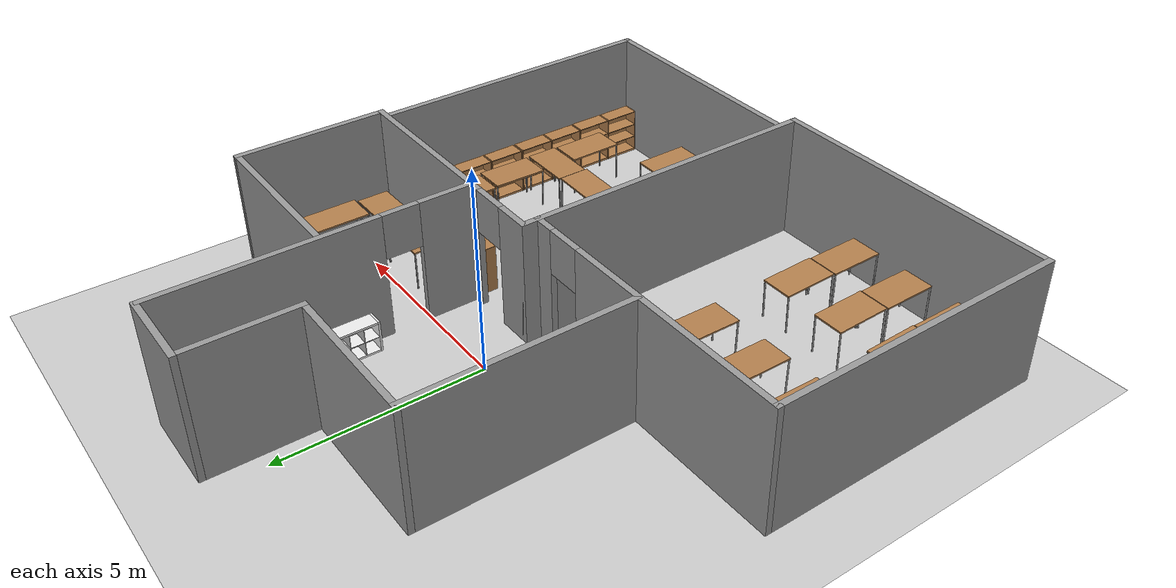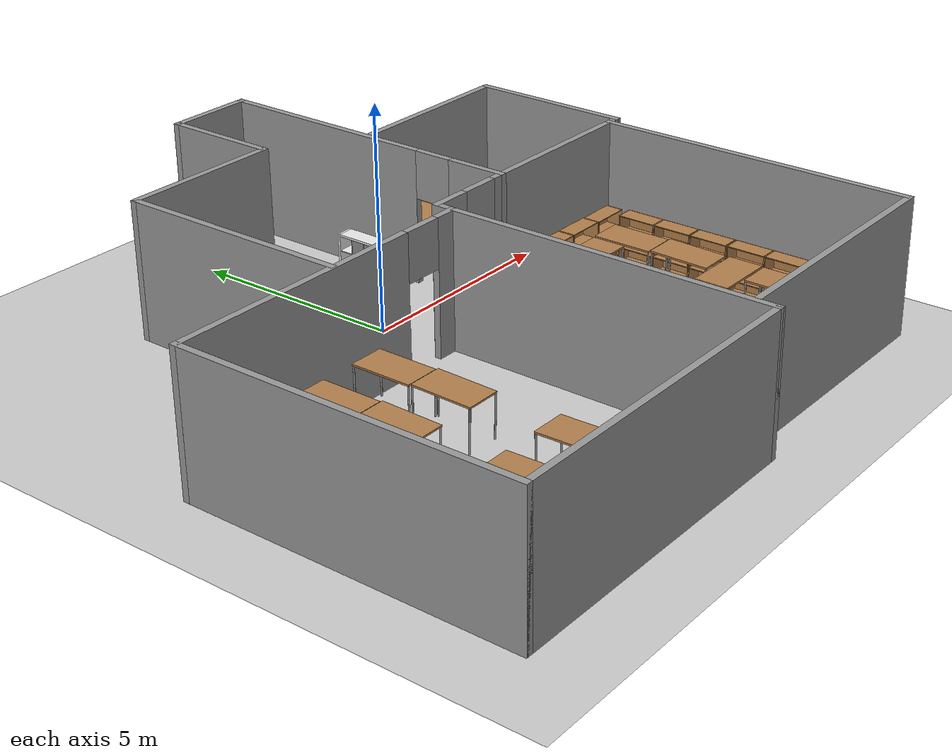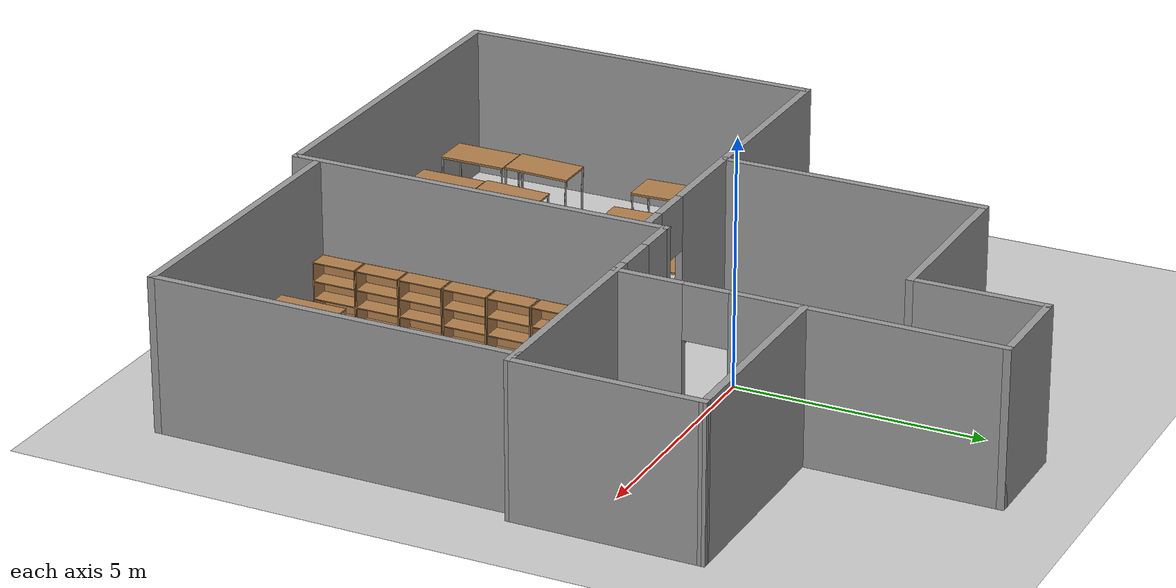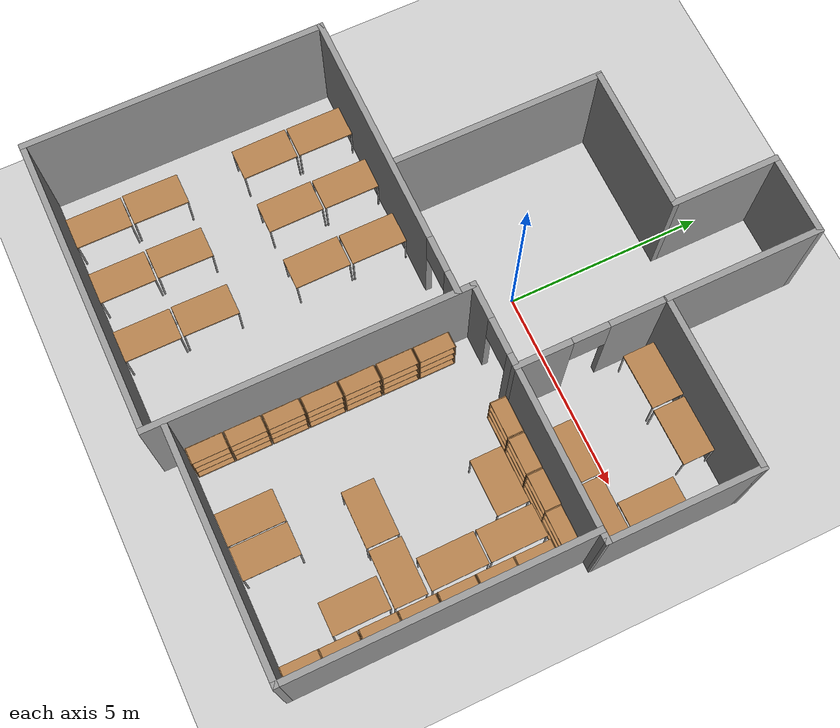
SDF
<sdf version="1.6">
 <world name="default">
  <light name="sun" type="directional">
   <pose>0 0 10 0 -0 0</pose>
   <diffuse>0.8 0.8 0.8 1</diffuse>
   <specular>0.1 0.1 0.1 1</specular>
   <attenuation>
    <range>1000</range>
    <constant>0.9</constant>
    <linear>0.01</linear>
    <quadratic>0.001</quadratic>
   </attenuation>
   <direction>-0.5 0.5 -1</direction>
  </light>
  <model name="ground_plane">
   <static>1</static>
   <link name="link">
    <collision name="collision">
     <geometry><plane><normal>0 0 1</normal><size>100 100</size></plane></geometry>
     <surface><friction><ode><mu>100</mu><mu2>50</mu2></ode></friction></surface>
    </collision>
    <visual name="visual">
     <cast_shadows>0</cast_shadows>
     <geometry><plane><normal>0 0 1</normal><size>100 100</size></plane></geometry>
     <material>
      <script><uri>file://media/materials/scripts/gazebo.material</uri><name>Gazebo/Grey</name></script>
     </material>
    </visual>
   </link>
  </model>
  <gravity>0 0 -9.8</gravity>
  <magnetic_field>6e-06 2.3e-05 -4.2e-05</magnetic_field>
  <atmosphere type="adiabatic"/>
  <physics name="default_physics" default="0" type="ode">
   <max_step_size>0.001</max_step_size>
   <real_time_factor>1</real_time_factor>
   <real_time_update_rate>1000</real_time_update_rate>
  </physics>
  <scene><ambient>0.4 0.4 0.4 1</ambient><background>0.7 0.7 0.7 1</background><shadows>1</shadows></scene>
  <spherical_coordinates>
   <surface_model>EARTH_WGS84</surface_model>
   <latitude_deg>0</latitude_deg>
   <longitude_deg>0</longitude_deg>
   <elevation>0</elevation>
   <heading_deg>0</heading_deg>
  </spherical_coordinates>
  <model name="bh9f_lab_1">
   <pose>-0.27016 -1.43191 0 0 -0 0</pose>
   <link name="Wall_0">
    <pose>-3.1331 -0.253 0 0 -0 3.14159</pose>
    <visual name="Wall_0_Visual_0">
     <pose>-3.46145 0 1.55 0 -0 0</pose>
     <geometry><box><size>0.601096 0.15 3.1</size></box></geometry>
     <material>
      <script><uri>file://media/materials/scripts/gazebo.material</uri><name>Gazebo/Grey</name></script>
      <ambient>1 1 1 1</ambient>
     </material>
    </visual>
    <collision name="Wall_0_Collision_0">
     <geometry><box><size>0.601096 0.15 3.1</size></box></geometry>
     <pose>-3.46145 0 1.55 0 -0 0</pose>
    </collision>
    <visual name="Wall_0_Visual_1">
     <pose>0.750548 0 1.55 0 -0 0</pose>
     <geometry><box><size>6.0229 0.15 3.1</size></box></geometry>
     <material>
      <script><uri>file://media/materials/scripts/gazebo.material</uri><name>Gazebo/Grey</name></script>
      <ambient>1 1 1 1</ambient>
     </material>
    </visual>
    <collision name="Wall_0_Collision_1">
     <geometry><box><size>6.0229 0.15 3.1</size></box></geometry>
     <pose>0.750548 0 1.55 0 -0 0</pose>
    </collision>
    <visual name="Wall_0_Visual_3">
     <pose>-2.7109 0 2.55 0 -0 0</pose>
     <geometry><box><size>0.9 0.15 1.1</size></box></geometry>
     <material>
      <script><uri>file://media/materials/scripts/gazebo.material</uri><name>Gazebo/Grey</name></script>
      <ambient>1 1 1 1</ambient>
     </material>
    </visual>
    <collision name="Wall_0_Collision_3">
     <geometry><box><size>0.9 0.15 1.1</size></box></geometry>
     <pose>-2.7109 0 2.55 0 -0 0</pose>
    </collision>
   </link>
   <link name="Wall_12">
    <collision name="Wall_12_Collision">
     <geometry><box><size>7.44 0.15 3.1</size></box></geometry>
     <pose>0 0 1.55 0 -0 0</pose>
    </collision>
    <visual name="Wall_12_Visual">
     <pose>0 0 1.55 0 -0 0</pose>
     <geometry><box><size>7.44 0.15 3.1</size></box></geometry>
     <material>
      <script><uri>file://media/materials/scripts/gazebo.material</uri><name>Gazebo/Grey</name></script>
      <ambient>1 1 1 1</ambient>
     </material>
    </visual>
    <pose>6.5499 -3.516 0 0 0 -1.5708</pose>
   </link>
   <link name="Wall_14">
    <collision name="Wall_14_Collision">
     <geometry><box><size>6 0.15 3.1</size></box></geometry>
     <pose>0 0 1.55 0 -0 0</pose>
    </collision>
    <visual name="Wall_14_Visual">
     <pose>0 0 1.55 0 -0 0</pose>
     <geometry><box><size>6 0.15 3.1</size></box></geometry>
     <material>
      <script><uri>file://media/materials/scripts/gazebo.material</uri><name>Gazebo/Grey</name></script>
      <ambient>1 1 1 1</ambient>
     </material>
    </visual>
    <pose>3.6249 -7.161 0 0 -0 3.14159</pose>
   </link>
   <link name="Wall_16">
    <collision name="Wall_16_Collision">
     <geometry><box><size>3.83 0.15 3.1</size></box></geometry>
     <pose>0 0 1.55 0 -0 0</pose>
    </collision>
    <visual name="Wall_16_Visual">
     <pose>0 0 1.55 0 -0 0</pose>
     <geometry><box><size>3.83 0.15 3.1</size></box></geometry>
     <material>
      <script><uri>file://media/materials/scripts/gazebo.material</uri><name>Gazebo/Grey</name></script>
      <ambient>1 1 1 1</ambient>
     </material>
    </visual>
    <pose>6.8149 1.975 0 0 -0 1.56808</pose>
   </link>
   <link name="Wall_18">
    <collision name="Wall_18_Collision">
     <geometry><box><size>4.33 0.15 3.1</size></box></geometry>
     <pose>0 0 1.55 0 -0 0</pose>
    </collision>
    <visual name="Wall_18_Visual">
     <pose>0 0 1.55 0 -0 0</pose>
     <geometry><box><size>4.33 0.15 3.1</size></box></geometry>
     <material>
      <script><uri>file://media/materials/scripts/gazebo.material</uri><name>Gazebo/Grey</name></script>
      <ambient>1 1 1 1</ambient>
     </material>
    </visual>
    <pose>4.7299 3.815 0 0 -0 3.14159</pose>
   </link>
   <link name="Wall_2">
    <collision name="Wall_2_Collision">
     <geometry><box><size>7.542 0.15 3.1</size></box></geometry>
     <pose>0 0 1.55 0 -0 0</pose>
    </collision>
    <visual name="Wall_2_Visual">
     <pose>0 0 1.55 0 -0 0</pose>
     <geometry><box><size>7.542 0.15 3.1</size></box></geometry>
     <material>
      <script><uri>file://media/materials/scripts/gazebo.material</uri><name>Gazebo/Grey</name></script>
      <ambient>1 1 1 1</ambient>
     </material>
    </visual>
    <pose>-6.8201 -3.949 0 0 0 -1.5708</pose>
   </link>
   <link name="Wall_20">
    <pose>2.6379 3.89 0 0 -0 1.5708</pose>
    <visual name="Wall_20_Visual_0">
     <pose>-3.11825 0 1.55 0 -0 0</pose>
     <geometry><box><size>1.42351 0.15 3.1</size></box></geometry>
     <material>
      <script><uri>file://media/materials/scripts/gazebo.material</uri><name>Gazebo/Grey</name></script>
      <ambient>1 1 1 1</ambient>
     </material>
    </visual>
    <collision name="Wall_20_Collision_0">
     <geometry><box><size>1.42351 0.15 3.1</size></box></geometry>
     <pose>-3.11825 0 1.55 0 -0 0</pose>
    </collision>
    <visual name="Wall_20_Visual_1">
     <pose>1.16175 0 1.55 0 -0 0</pose>
     <geometry><box><size>5.33649 0.15 3.1</size></box></geometry>
     <material>
      <script><uri>file://media/materials/scripts/gazebo.material</uri><name>Gazebo/Grey</name></script>
      <ambient>1 1 1 1</ambient>
     </material>
    </visual>
    <collision name="Wall_20_Collision_1">
     <geometry><box><size>5.33649 0.15 3.1</size></box></geometry>
     <pose>1.16175 0 1.55 0 -0 0</pose>
    </collision>
    <visual name="Wall_20_Visual_3">
     <pose>-1.95649 0 2.55 0 -0 0</pose>
     <geometry><box><size>0.9 0.15 1.1</size></box></geometry>
     <material>
      <script><uri>file://media/materials/scripts/gazebo.material</uri><name>Gazebo/Grey</name></script>
      <ambient>1 1 1 1</ambient>
     </material>
    </visual>
    <collision name="Wall_20_Collision_3">
     <geometry><box><size>0.9 0.15 1.1</size></box></geometry>
     <pose>-1.95649 0 2.55 0 -0 0</pose>
    </collision>
   </link>
   <link name="Wall_24">
    <collision name="Wall_24_Collision">
     <geometry><box><size>2.089 0.15 3.1</size></box></geometry>
     <pose>0 0 1.55 0 -0 0</pose>
    </collision>
    <visual name="Wall_24_Visual">
     <pose>0 0 1.55 0 -0 0</pose>
     <geometry><box><size>2.089 0.15 3.1</size></box></geometry>
     <material>
      <script><uri>file://media/materials/scripts/gazebo.material</uri><name>Gazebo/Grey</name></script>
      <ambient>1 1 1 1</ambient>
     </material>
    </visual>
    <pose>1.6684 7.645 0 0 -0 3.14159</pose>
   </link>
   <link name="Wall_26">
    <collision name="Wall_26_Collision">
     <geometry><box><size>2.75 0.15 3.1</size></box></geometry>
     <pose>0 0 1.55 0 -0 0</pose>
    </collision>
    <visual name="Wall_26_Visual">
     <pose>0 0 1.55 0 -0 0</pose>
     <geometry><box><size>2.75 0.15 3.1</size></box></geometry>
     <material>
      <script><uri>file://media/materials/scripts/gazebo.material</uri><name>Gazebo/Grey</name></script>
      <ambient>1 1 1 1</ambient>
     </material>
    </visual>
    <pose>0.698898 6.345 0 0 0 -1.5708</pose>
   </link>
   <link name="Wall_28">
    <collision name="Wall_28_Collision">
     <geometry><box><size>3.75 0.15 3.1</size></box></geometry>
     <pose>0 0 1.55 0 -0 0</pose>
    </collision>
    <visual name="Wall_28_Visual">
     <pose>0 0 1.55 0 -0 0</pose>
     <geometry><box><size>3.75 0.15 3.1</size></box></geometry>
     <material>
      <script><uri>file://media/materials/scripts/gazebo.material</uri><name>Gazebo/Grey</name></script>
      <ambient>1 1 1 1</ambient>
     </material>
    </visual>
    <pose>-1.1011 5.045 0 0 -0 3.14159</pose>
   </link>
   <link name="Wall_30">
    <collision name="Wall_30_Collision">
     <geometry><box><size>5.41 0.15 3.1</size></box></geometry>
     <pose>0 0 1.55 0 -0 0</pose>
    </collision>
    <visual name="Wall_30_Visual">
     <pose>0 0 1.55 0 -0 0</pose>
     <geometry><box><size>5.41 0.15 3.1</size></box></geometry>
     <material>
      <script><uri>file://media/materials/scripts/gazebo.material</uri><name>Gazebo/Grey</name></script>
      <ambient>1 1 1 1</ambient>
     </material>
    </visual>
    <pose>-2.9011 2.415 0 0 0 -1.5708</pose>
   </link>
   <link name="Wall_4">
    <collision name="Wall_4_Collision">
     <geometry><box><size>7.53 0.15 3.1</size></box></geometry>
     <pose>0 0 1.55 0 -0 0</pose>
    </collision>
    <visual name="Wall_4_Visual">
     <pose>0 0 1.55 0 -0 0</pose>
     <geometry><box><size>7.53 0.15 3.1</size></box></geometry>
     <material>
      <script><uri>file://media/materials/scripts/gazebo.material</uri><name>Gazebo/Grey</name></script>
      <ambient>1 1 1 1</ambient>
     </material>
    </visual>
    <pose>-3.1301 -7.645 0 0 -0 0</pose>
   </link>
   <link name="Wall_6">
    <collision name="Wall_6_Collision">
     <geometry><box><size>7.93 0.15 3.1</size></box></geometry>
     <pose>0 0 1.55 0 -0 0</pose>
    </collision>
    <visual name="Wall_6_Visual">
     <pose>0 0 1.55 0 -0 0</pose>
     <geometry><box><size>7.93 0.15 3.1</size></box></geometry>
     <material>
      <script><uri>file://media/materials/scripts/gazebo.material</uri><name>Gazebo/Grey</name></script>
      <ambient>1 1 1 1</ambient>
     </material>
    </visual>
    <pose>0.559898 -3.755 0 0 -0 1.5708</pose>
   </link>
   <link name="Wall_8">
    <pose>3.6849 0.135 0 0 -0 0</pose>
    <visual name="Wall_8_Visual_0">
     <pose>-2.73161 0 1.55 0 -0 0</pose>
     <geometry><box><size>0.936778 0.15 3.1</size></box></geometry>
     <material>
      <script><uri>file://media/materials/scripts/gazebo.material</uri><name>Gazebo/Grey</name></script>
      <ambient>1 1 1 1</ambient>
     </material>
    </visual>
    <collision name="Wall_8_Collision_0">
     <geometry><box><size>0.936778 0.15 3.1</size></box></geometry>
     <pose>-2.73161 0 1.55 0 -0 0</pose>
    </collision>
    <visual name="Wall_8_Visual_1">
     <pose>0.918389 0 1.55 0 -0 0</pose>
     <geometry><box><size>4.56322 0.15 3.1</size></box></geometry>
     <material>
      <script><uri>file://media/materials/scripts/gazebo.material</uri><name>Gazebo/Grey</name></script>
      <ambient>1 1 1 1</ambient>
     </material>
    </visual>
    <collision name="Wall_8_Collision_1">
     <geometry><box><size>4.56322 0.15 3.1</size></box></geometry>
     <pose>0.918389 0 1.55 0 -0 0</pose>
    </collision>
    <visual name="Wall_8_Visual_3">
     <pose>-1.81322 0 2.55 0 -0 0</pose>
     <geometry><box><size>0.9 0.15 1.1</size></box></geometry>
     <material>
      <script><uri>file://media/materials/scripts/gazebo.material</uri><name>Gazebo/Grey</name></script>
      <ambient>1 1 1 1</ambient>
     </material>
    </visual>
    <collision name="Wall_8_Collision_3">
     <geometry><box><size>0.9 0.15 1.1</size></box></geometry>
     <pose>-1.81322 0 2.55 0 -0 0</pose>
    </collision>
   </link>
   <static>1</static>
  </model>
  <model name="bookshelf_0">
   <static>1</static>
   <link name="link">
    <inertial><mass>1</mass></inertial>
    <collision name="back">
     <pose>0 0.005 0.6 0 -0 0</pose>
     <geometry><box><size>0.9 0.01 1.2</size></box></geometry>
    </collision>
    <visual name="visual1">
     <pose>0 0.005 0.6 0 -0 0</pose>
     <geometry><box><size>0.9 0.01 1.2</size></box></geometry>
     <material>
      <script><uri>file://media/materials/scripts/gazebo.material</uri><name>Gazebo/Wood</name></script>
     </material>
    </visual>
    <collision name="left_side">
     <pose>0.45 -0.195 0.6 0 -0 0</pose>
     <geometry><box><size>0.02 0.4 1.2</size></box></geometry>
    </collision>
    <visual name="visual2">
     <pose>0.45 -0.195 0.6 0 -0 0</pose>
     <geometry><box><size>0.02 0.4 1.2</size></box></geometry>
     <material>
      <script><uri>file://media/materials/scripts/gazebo.material</uri><name>Gazebo/Wood</name></script>
     </material>
    </visual>
    <collision name="right_side">
     <pose>-0.45 -0.195 0.6 0 -0 0</pose>
     <geometry><box><size>0.02 0.4 1.2</size></box></geometry>
    </collision>
    <visual name="visual3">
     <pose>-0.45 -0.195 0.6 0 -0 0</pose>
     <geometry><box><size>0.02 0.4 1.2</size></box></geometry>
     <material>
      <script><uri>file://media/materials/scripts/gazebo.material</uri><name>Gazebo/Wood</name></script>
     </material>
    </visual>
    <collision name="bottom">
     <pose>0 -0.195 0.03 0 -0 0</pose>
     <geometry><box><size>0.88 0.4 0.06</size></box></geometry>
    </collision>
    <visual name="visual4">
     <pose>0 -0.195 0.03 0 -0 0</pose>
     <geometry><box><size>0.88 0.4 0.06</size></box></geometry>
     <material>
      <script><uri>file://media/materials/scripts/gazebo.material</uri><name>Gazebo/Wood</name></script>
     </material>
    </visual>
    <collision name="top">
     <pose>0 -0.195 1.19 0 -0 0</pose>
     <geometry><box><size>0.88 0.4 0.02</size></box></geometry>
    </collision>
    <visual name="visual5">
     <pose>0 -0.195 1.19 0 -0 0</pose>
     <geometry><box><size>0.88 0.4 0.02</size></box></geometry>
     <material>
      <script><uri>file://media/materials/scripts/gazebo.material</uri><name>Gazebo/Wood</name></script>
     </material>
    </visual>
    <collision name="low_shelf">
     <pose>0 -0.195 0.43 0 -0 0</pose>
     <geometry><box><size>0.88 0.4 0.02</size></box></geometry>
    </collision>
    <visual name="visual6">
     <pose>0 -0.195 0.43 0 -0 0</pose>
     <geometry><box><size>0.88 0.4 0.02</size></box></geometry>
     <material>
      <script><uri>file://media/materials/scripts/gazebo.material</uri><name>Gazebo/Wood</name></script>
     </material>
    </visual>
    <collision name="high_shelf">
     <pose>0 -0.195 0.8 0 -0 0</pose>
     <geometry><box><size>0.88 0.4 0.02</size></box></geometry>
    </collision>
    <visual name="visual7">
     <pose>0 -0.195 0.8 0 -0 0</pose>
     <geometry><box><size>0.88 0.4 0.02</size></box></geometry>
     <material>
      <script><uri>file://media/materials/scripts/gazebo.material</uri><name>Gazebo/Wood</name></script>
     </material>
    </visual>
   </link>
   <pose>5.60698 -1.45081 0 0 -0 0</pose>
  </model>
  <model name="bookshelf_0_clone">
   <static>1</static>
   <link name="link">
    <inertial><mass>1</mass></inertial>
    <collision name="back">
     <pose>0 0.005 0.6 0 -0 0</pose>
     <geometry><box><size>0.9 0.01 1.2</size></box></geometry>
    </collision>
    <visual name="visual1">
     <pose>0 0.005 0.6 0 -0 0</pose>
     <geometry><box><size>0.9 0.01 1.2</size></box></geometry>
     <material>
      <script><uri>file://media/materials/scripts/gazebo.material</uri><name>Gazebo/Wood</name></script>
     </material>
    </visual>
    <collision name="left_side">
     <pose>0.45 -0.195 0.6 0 -0 0</pose>
     <geometry><box><size>0.02 0.4 1.2</size></box></geometry>
    </collision>
    <visual name="visual2">
     <pose>0.45 -0.195 0.6 0 -0 0</pose>
     <geometry><box><size>0.02 0.4 1.2</size></box></geometry>
     <material>
      <script><uri>file://media/materials/scripts/gazebo.material</uri><name>Gazebo/Wood</name></script>
     </material>
    </visual>
    <collision name="right_side">
     <pose>-0.45 -0.195 0.6 0 -0 0</pose>
     <geometry><box><size>0.02 0.4 1.2</size></box></geometry>
    </collision>
    <visual name="visual3">
     <pose>-0.45 -0.195 0.6 0 -0 0</pose>
     <geometry><box><size>0.02 0.4 1.2</size></box></geometry>
     <material>
      <script><uri>file://media/materials/scripts/gazebo.material</uri><name>Gazebo/Wood</name></script>
     </material>
    </visual>
    <collision name="bottom">
     <pose>0 -0.195 0.03 0 -0 0</pose>
     <geometry><box><size>0.88 0.4 0.06</size></box></geometry>
    </collision>
    <visual name="visual4">
     <pose>0 -0.195 0.03 0 -0 0</pose>
     <geometry><box><size>0.88 0.4 0.06</size></box></geometry>
     <material>
      <script><uri>file://media/materials/scripts/gazebo.material</uri><name>Gazebo/Wood</name></script>
     </material>
    </visual>
    <collision name="top">
     <pose>0 -0.195 1.19 0 -0 0</pose>
     <geometry><box><size>0.88 0.4 0.02</size></box></geometry>
    </collision>
    <visual name="visual5">
     <pose>0 -0.195 1.19 0 -0 0</pose>
     <geometry><box><size>0.88 0.4 0.02</size></box></geometry>
     <material>
      <script><uri>file://media/materials/scripts/gazebo.material</uri><name>Gazebo/Wood</name></script>
     </material>
    </visual>
    <collision name="low_shelf">
     <pose>0 -0.195 0.43 0 -0 0</pose>
     <geometry><box><size>0.88 0.4 0.02</size></box></geometry>
    </collision>
    <visual name="visual6">
     <pose>0 -0.195 0.43 0 -0 0</pose>
     <geometry><box><size>0.88 0.4 0.02</size></box></geometry>
     <material>
      <script><uri>file://media/materials/scripts/gazebo.material</uri><name>Gazebo/Wood</name></script>
     </material>
    </visual>
    <collision name="high_shelf">
     <pose>0 -0.195 0.8 0 -0 0</pose>
     <geometry><box><size>0.88 0.4 0.02</size></box></geometry>
    </collision>
    <visual name="visual7">
     <pose>0 -0.195 0.8 0 -0 0</pose>
     <geometry><box><size>0.88 0.4 0.02</size></box></geometry>
     <material>
      <script><uri>file://media/materials/scripts/gazebo.material</uri><name>Gazebo/Wood</name></script>
     </material>
    </visual>
   </link>
   <pose>4.69369 -1.43695 0 0 -0 0</pose>
  </model>
  <model name="bookshelf_0_clone_0">
   <static>1</static>
   <link name="link">
    <inertial><mass>1</mass></inertial>
    <collision name="back">
     <pose>0 0.005 0.6 0 -0 0</pose>
     <geometry><box><size>0.9 0.01 1.2</size></box></geometry>
    </collision>
    <visual name="visual1">
     <pose>0 0.005 0.6 0 -0 0</pose>
     <geometry><box><size>0.9 0.01 1.2</size></box></geometry>
     <material>
      <script><uri>file://media/materials/scripts/gazebo.material</uri><name>Gazebo/Wood</name></script>
     </material>
    </visual>
    <collision name="left_side">
     <pose>0.45 -0.195 0.6 0 -0 0</pose>
     <geometry><box><size>0.02 0.4 1.2</size></box></geometry>
    </collision>
    <visual name="visual2">
     <pose>0.45 -0.195 0.6 0 -0 0</pose>
     <geometry><box><size>0.02 0.4 1.2</size></box></geometry>
     <material>
      <script><uri>file://media/materials/scripts/gazebo.material</uri><name>Gazebo/Wood</name></script>
     </material>
    </visual>
    <collision name="right_side">
     <pose>-0.45 -0.195 0.6 0 -0 0</pose>
     <geometry><box><size>0.02 0.4 1.2</size></box></geometry>
    </collision>
    <visual name="visual3">
     <pose>-0.45 -0.195 0.6 0 -0 0</pose>
     <geometry><box><size>0.02 0.4 1.2</size></box></geometry>
     <material>
      <script><uri>file://media/materials/scripts/gazebo.material</uri><name>Gazebo/Wood</name></script>
     </material>
    </visual>
    <collision name="bottom">
     <pose>0 -0.195 0.03 0 -0 0</pose>
     <geometry><box><size>0.88 0.4 0.06</size></box></geometry>
    </collision>
    <visual name="visual4">
     <pose>0 -0.195 0.03 0 -0 0</pose>
     <geometry><box><size>0.88 0.4 0.06</size></box></geometry>
     <material>
      <script><uri>file://media/materials/scripts/gazebo.material</uri><name>Gazebo/Wood</name></script>
     </material>
    </visual>
    <collision name="top">
     <pose>0 -0.195 1.19 0 -0 0</pose>
     <geometry><box><size>0.88 0.4 0.02</size></box></geometry>
    </collision>
    <visual name="visual5">
     <pose>0 -0.195 1.19 0 -0 0</pose>
     <geometry><box><size>0.88 0.4 0.02</size></box></geometry>
     <material>
      <script><uri>file://media/materials/scripts/gazebo.material</uri><name>Gazebo/Wood</name></script>
     </material>
    </visual>
    <collision name="low_shelf">
     <pose>0 -0.195 0.43 0 -0 0</pose>
     <geometry><box><size>0.88 0.4 0.02</size></box></geometry>
    </collision>
    <visual name="visual6">
     <pose>0 -0.195 0.43 0 -0 0</pose>
     <geometry><box><size>0.88 0.4 0.02</size></box></geometry>
     <material>
      <script><uri>file://media/materials/scripts/gazebo.material</uri><name>Gazebo/Wood</name></script>
     </material>
    </visual>
    <collision name="high_shelf">
     <pose>0 -0.195 0.8 0 -0 0</pose>
     <geometry><box><size>0.88 0.4 0.02</size></box></geometry>
    </collision>
    <visual name="visual7">
     <pose>0 -0.195 0.8 0 -0 0</pose>
     <geometry><box><size>0.88 0.4 0.02</size></box></geometry>
     <material>
      <script><uri>file://media/materials/scripts/gazebo.material</uri><name>Gazebo/Wood</name></script>
     </material>
    </visual>
   </link>
   <pose>3.76739 -1.438 0 0 -0 0</pose>
  </model>
  <model name="bookshelf_0_clone_1">
   <static>1</static>
   <link name="link">
    <inertial><mass>1</mass></inertial>
    <collision name="back">
     <pose>0 0.005 0.6 0 -0 0</pose>
     <geometry><box><size>0.9 0.01 1.2</size></box></geometry>
    </collision>
    <visual name="visual1">
     <pose>0 0.005 0.6 0 -0 0</pose>
     <geometry><box><size>0.9 0.01 1.2</size></box></geometry>
     <material>
      <script><uri>file://media/materials/scripts/gazebo.material</uri><name>Gazebo/Wood</name></script>
     </material>
    </visual>
    <collision name="left_side">
     <pose>0.45 -0.195 0.6 0 -0 0</pose>
     <geometry><box><size>0.02 0.4 1.2</size></box></geometry>
    </collision>
    <visual name="visual2">
     <pose>0.45 -0.195 0.6 0 -0 0</pose>
     <geometry><box><size>0.02 0.4 1.2</size></box></geometry>
     <material>
      <script><uri>file://media/materials/scripts/gazebo.material</uri><name>Gazebo/Wood</name></script>
     </material>
    </visual>
    <collision name="right_side">
     <pose>-0.45 -0.195 0.6 0 -0 0</pose>
     <geometry><box><size>0.02 0.4 1.2</size></box></geometry>
    </collision>
    <visual name="visual3">
     <pose>-0.45 -0.195 0.6 0 -0 0</pose>
     <geometry><box><size>0.02 0.4 1.2</size></box></geometry>
     <material>
      <script><uri>file://media/materials/scripts/gazebo.material</uri><name>Gazebo/Wood</name></script>
     </material>
    </visual>
    <collision name="bottom">
     <pose>0 -0.195 0.03 0 -0 0</pose>
     <geometry><box><size>0.88 0.4 0.06</size></box></geometry>
    </collision>
    <visual name="visual4">
     <pose>0 -0.195 0.03 0 -0 0</pose>
     <geometry><box><size>0.88 0.4 0.06</size></box></geometry>
     <material>
      <script><uri>file://media/materials/scripts/gazebo.material</uri><name>Gazebo/Wood</name></script>
     </material>
    </visual>
    <collision name="top">
     <pose>0 -0.195 1.19 0 -0 0</pose>
     <geometry><box><size>0.88 0.4 0.02</size></box></geometry>
    </collision>
    <visual name="visual5">
     <pose>0 -0.195 1.19 0 -0 0</pose>
     <geometry><box><size>0.88 0.4 0.02</size></box></geometry>
     <material>
      <script><uri>file://media/materials/scripts/gazebo.material</uri><name>Gazebo/Wood</name></script>
     </material>
    </visual>
    <collision name="low_shelf">
     <pose>0 -0.195 0.43 0 -0 0</pose>
     <geometry><box><size>0.88 0.4 0.02</size></box></geometry>
    </collision>
    <visual name="visual6">
     <pose>0 -0.195 0.43 0 -0 0</pose>
     <geometry><box><size>0.88 0.4 0.02</size></box></geometry>
     <material>
      <script><uri>file://media/materials/scripts/gazebo.material</uri><name>Gazebo/Wood</name></script>
     </material>
    </visual>
    <collision name="high_shelf">
     <pose>0 -0.195 0.8 0 -0 0</pose>
     <geometry><box><size>0.88 0.4 0.02</size></box></geometry>
    </collision>
    <visual name="visual7">
     <pose>0 -0.195 0.8 0 -0 0</pose>
     <geometry><box><size>0.88 0.4 0.02</size></box></geometry>
     <material>
      <script><uri>file://media/materials/scripts/gazebo.material</uri><name>Gazebo/Wood</name></script>
     </material>
    </visual>
   </link>
   <pose>2.83762 -1.43529 0 0 -0 0</pose>
  </model>
  <model name="bookshelf_sidepose">
   <link name="link">
    <pose>0.214811 -0.123316 0 0 0 -1.57547</pose>
    <inertial><mass>1</mass></inertial>
    <visual name="visual1">
     <pose>0 0.005 0.6 0 -0 0</pose>
     <geometry><box><size>0.9 0.01 1.2</size></box></geometry>
     <material>
      <script><uri>file://media/materials/scripts/gazebo.material</uri><name>Gazebo/Wood</name></script>
      <ambient>1 1 1 1</ambient>
      <diffuse>1 1 1 1</diffuse>
      <specular>0.2 0.2 0.2 1</specular>
      <emissive>0 0 0 1</emissive>
     </material>
    </visual>
    <visual name="visual2">
     <pose>0.45 -0.195 0.6 0 -0 0</pose>
     <geometry><box><size>0.02 0.4 1.2</size></box></geometry>
     <material>
      <script><uri>file://media/materials/scripts/gazebo.material</uri><name>Gazebo/Wood</name></script>
      <ambient>1 1 1 1</ambient>
      <diffuse>1 1 1 1</diffuse>
      <specular>0.2 0.2 0.2 1</specular>
      <emissive>0 0 0 1</emissive>
     </material>
    </visual>
    <visual name="visual3">
     <pose>-0.45 -0.195 0.6 0 -0 0</pose>
     <geometry><box><size>0.02 0.4 1.2</size></box></geometry>
     <material>
      <script><uri>file://media/materials/scripts/gazebo.material</uri><name>Gazebo/Wood</name></script>
      <ambient>1 1 1 1</ambient>
      <diffuse>1 1 1 1</diffuse>
      <specular>0.2 0.2 0.2 1</specular>
      <emissive>0 0 0 1</emissive>
     </material>
    </visual>
    <visual name="visual4">
     <pose>0 -0.195 0.03 0 -0 0</pose>
     <geometry><box><size>0.88 0.4 0.06</size></box></geometry>
     <material>
      <script><uri>file://media/materials/scripts/gazebo.material</uri><name>Gazebo/Wood</name></script>
      <ambient>1 1 1 1</ambient>
      <diffuse>1 1 1 1</diffuse>
      <specular>0.2 0.2 0.2 1</specular>
      <emissive>0 0 0 1</emissive>
     </material>
    </visual>
    <visual name="visual6">
     <pose>0 -0.195 0.43 0 -0 0</pose>
     <geometry><box><size>0.88 0.4 0.02</size></box></geometry>
     <material>
      <script><uri>file://media/materials/scripts/gazebo.material</uri><name>Gazebo/Wood</name></script>
      <ambient>1 1 1 1</ambient>
      <diffuse>1 1 1 1</diffuse>
      <specular>0.2 0.2 0.2 1</specular>
      <emissive>0 0 0 1</emissive>
     </material>
    </visual>
    <visual name="visual5">
     <pose>0 -0.195 1.19 0 -0 0</pose>
     <geometry><box><size>0.88 0.4 0.02</size></box></geometry>
     <material>
      <script><uri>file://media/materials/scripts/gazebo.material</uri><name>Gazebo/Wood</name></script>
      <ambient>1 1 1 1</ambient>
      <diffuse>1 1 1 1</diffuse>
      <specular>0.2 0.2 0.2 1</specular>
      <emissive>0 0 0 1</emissive>
     </material>
    </visual>
    <visual name="visual7">
     <pose>0 -0.195 0.8 0 -0 0</pose>
     <geometry><box><size>0.88 0.4 0.02</size></box></geometry>
     <material>
      <script><uri>file://media/materials/scripts/gazebo.material</uri><name>Gazebo/Wood</name></script>
      <ambient>1 1 1 1</ambient>
      <diffuse>1 1 1 1</diffuse>
      <specular>0.2 0.2 0.2 1</specular>
      <emissive>0 0 0 1</emissive>
     </material>
    </visual>
    <collision name="back">
     <pose>0 0.005 0.6 0 -0 0</pose>
     <geometry><box><size>0.9 0.01 1.2</size></box></geometry>
     <surface>
      <friction>
       <ode><mu>1</mu><mu2>1</mu2><fdir1>0 0 0</fdir1><slip1>0</slip1><slip2>0</slip2></ode>
       <torsional>
        <coefficient>1</coefficient>
        <patch_radius>0</patch_radius>
        <surface_radius>0</surface_radius>
        <use_patch_radius>1</use_patch_radius>
        <ode><slip>0</slip></ode>
       </torsional>
      </friction>
      <bounce><restitution_coefficient>0</restitution_coefficient><threshold>1e+06</threshold></bounce>
      <contact>
       <collide_without_contact>0</collide_without_contact>
       <collide_without_contact_bitmask>1</collide_without_contact_bitmask>
       <collide_bitmask>1</collide_bitmask>
       <ode>
        <soft_cfm>0</soft_cfm>
        <soft_erp>0.2</soft_erp>
        <kp>1e+13</kp>
        <kd>1</kd>
        <max_vel>0.01</max_vel>
        <min_depth>0</min_depth>
       </ode>
       <bullet>
        <split_impulse>1</split_impulse>
        <split_impulse_penetration_threshold>-0.01</split_impulse_penetration_threshold>
        <soft_cfm>0</soft_cfm>
        <soft_erp>0.2</soft_erp>
        <kp>1e+13</kp>
        <kd>1</kd>
       </bullet>
      </contact>
     </surface>
    </collision>
    <collision name="left_side">
     <pose>0.45 -0.195 0.6 0 -0 0</pose>
     <geometry><box><size>0.02 0.4 1.2</size></box></geometry>
     <surface>
      <friction>
       <ode><mu>1</mu><mu2>1</mu2><fdir1>0 0 0</fdir1><slip1>0</slip1><slip2>0</slip2></ode>
       <torsional>
        <coefficient>1</coefficient>
        <patch_radius>0</patch_radius>
        <surface_radius>0</surface_radius>
        <use_patch_radius>1</use_patch_radius>
        <ode><slip>0</slip></ode>
       </torsional>
      </friction>
      <bounce><restitution_coefficient>0</restitution_coefficient><threshold>1e+06</threshold></bounce>
      <contact>
       <collide_without_contact>0</collide_without_contact>
       <collide_without_contact_bitmask>1</collide_without_contact_bitmask>
       <collide_bitmask>1</collide_bitmask>
       <ode>
        <soft_cfm>0</soft_cfm>
        <soft_erp>0.2</soft_erp>
        <kp>1e+13</kp>
        <kd>1</kd>
        <max_vel>0.01</max_vel>
        <min_depth>0</min_depth>
       </ode>
       <bullet>
        <split_impulse>1</split_impulse>
        <split_impulse_penetration_threshold>-0.01</split_impulse_penetration_threshold>
        <soft_cfm>0</soft_cfm>
        <soft_erp>0.2</soft_erp>
        <kp>1e+13</kp>
        <kd>1</kd>
       </bullet>
      </contact>
     </surface>
    </collision>
    <collision name="right_side">
     <pose>-0.45 -0.195 0.6 0 -0 0</pose>
     <geometry><box><size>0.02 0.4 1.2</size></box></geometry>
     <surface>
      <friction>
       <ode><mu>1</mu><mu2>1</mu2><fdir1>0 0 0</fdir1><slip1>0</slip1><slip2>0</slip2></ode>
       <torsional>
        <coefficient>1</coefficient>
        <patch_radius>0</patch_radius>
        <surface_radius>0</surface_radius>
        <use_patch_radius>1</use_patch_radius>
        <ode><slip>0</slip></ode>
       </torsional>
      </friction>
      <bounce><restitution_coefficient>0</restitution_coefficient><threshold>1e+06</threshold></bounce>
      <contact>
       <collide_without_contact>0</collide_without_contact>
       <collide_without_contact_bitmask>1</collide_without_contact_bitmask>
       <collide_bitmask>1</collide_bitmask>
       <ode>
        <soft_cfm>0</soft_cfm>
        <soft_erp>0.2</soft_erp>
        <kp>1e+13</kp>
        <kd>1</kd>
        <max_vel>0.01</max_vel>
        <min_depth>0</min_depth>
       </ode>
       <bullet>
        <split_impulse>1</split_impulse>
        <split_impulse_penetration_threshold>-0.01</split_impulse_penetration_threshold>
        <soft_cfm>0</soft_cfm>
        <soft_erp>0.2</soft_erp>
        <kp>1e+13</kp>
        <kd>1</kd>
       </bullet>
      </contact>
     </surface>
    </collision>
    <collision name="bottom">
     <pose>0 -0.195 0.03 0 -0 0</pose>
     <geometry><box><size>0.88 0.4 0.06</size></box></geometry>
     <surface>
      <friction>
       <ode><mu>1</mu><mu2>1</mu2><fdir1>0 0 0</fdir1><slip1>0</slip1><slip2>0</slip2></ode>
       <torsional>
        <coefficient>1</coefficient>
        <patch_radius>0</patch_radius>
        <surface_radius>0</surface_radius>
        <use_patch_radius>1</use_patch_radius>
        <ode><slip>0</slip></ode>
       </torsional>
      </friction>
      <bounce><restitution_coefficient>0</restitution_coefficient><threshold>1e+06</threshold></bounce>
      <contact>
       <collide_without_contact>0</collide_without_contact>
       <collide_without_contact_bitmask>1</collide_without_contact_bitmask>
       <collide_bitmask>1</collide_bitmask>
       <ode>
        <soft_cfm>0</soft_cfm>
        <soft_erp>0.2</soft_erp>
        <kp>1e+13</kp>
        <kd>1</kd>
        <max_vel>0.01</max_vel>
        <min_depth>0</min_depth>
       </ode>
       <bullet>
        <split_impulse>1</split_impulse>
        <split_impulse_penetration_threshold>-0.01</split_impulse_penetration_threshold>
        <soft_cfm>0</soft_cfm>
        <soft_erp>0.2</soft_erp>
        <kp>1e+13</kp>
        <kd>1</kd>
       </bullet>
      </contact>
     </surface>
    </collision>
    <collision name="low_shelf">
     <pose>0 -0.195 0.43 0 -0 0</pose>
     <geometry><box><size>0.88 0.4 0.02</size></box></geometry>
     <surface>
      <friction>
       <ode><mu>1</mu><mu2>1</mu2><fdir1>0 0 0</fdir1><slip1>0</slip1><slip2>0</slip2></ode>
       <torsional>
        <coefficient>1</coefficient>
        <patch_radius>0</patch_radius>
        <surface_radius>0</surface_radius>
        <use_patch_radius>1</use_patch_radius>
        <ode><slip>0</slip></ode>
       </torsional>
      </friction>
      <bounce><restitution_coefficient>0</restitution_coefficient><threshold>1e+06</threshold></bounce>
      <contact>
       <collide_without_contact>0</collide_without_contact>
       <collide_without_contact_bitmask>1</collide_without_contact_bitmask>
       <collide_bitmask>1</collide_bitmask>
       <ode>
        <soft_cfm>0</soft_cfm>
        <soft_erp>0.2</soft_erp>
        <kp>1e+13</kp>
        <kd>1</kd>
        <max_vel>0.01</max_vel>
        <min_depth>0</min_depth>
       </ode>
       <bullet>
        <split_impulse>1</split_impulse>
        <split_impulse_penetration_threshold>-0.01</split_impulse_penetration_threshold>
        <soft_cfm>0</soft_cfm>
        <soft_erp>0.2</soft_erp>
        <kp>1e+13</kp>
        <kd>1</kd>
       </bullet>
      </contact>
     </surface>
    </collision>
    <collision name="top">
     <pose>0 -0.195 1.19 0 -0 0</pose>
     <geometry><box><size>0.88 0.4 0.02</size></box></geometry>
     <surface>
      <friction>
       <ode><mu>1</mu><mu2>1</mu2><fdir1>0 0 0</fdir1><slip1>0</slip1><slip2>0</slip2></ode>
       <torsional>
        <coefficient>1</coefficient>
        <patch_radius>0</patch_radius>
        <surface_radius>0</surface_radius>
        <use_patch_radius>1</use_patch_radius>
        <ode><slip>0</slip></ode>
       </torsional>
      </friction>
      <bounce><restitution_coefficient>0</restitution_coefficient><threshold>1e+06</threshold></bounce>
      <contact>
       <collide_without_contact>0</collide_without_contact>
       <collide_without_contact_bitmask>1</collide_without_contact_bitmask>
       <collide_bitmask>1</collide_bitmask>
       <ode>
        <soft_cfm>0</soft_cfm>
        <soft_erp>0.2</soft_erp>
        <kp>1e+13</kp>
        <kd>1</kd>
        <max_vel>0.01</max_vel>
        <min_depth>0</min_depth>
       </ode>
       <bullet>
        <split_impulse>1</split_impulse>
        <split_impulse_penetration_threshold>-0.01</split_impulse_penetration_threshold>
        <soft_cfm>0</soft_cfm>
        <soft_erp>0.2</soft_erp>
        <kp>1e+13</kp>
        <kd>1</kd>
       </bullet>
      </contact>
     </surface>
    </collision>
    <collision name="high_shelf">
     <pose>0 -0.195 0.8 0 -0 0</pose>
     <geometry><box><size>0.88 0.4 0.02</size></box></geometry>
     <surface>
      <friction>
       <ode><mu>1</mu><mu2>1</mu2><fdir1>0 0 0</fdir1><slip1>0</slip1><slip2>0</slip2></ode>
       <torsional>
        <coefficient>1</coefficient>
        <patch_radius>0</patch_radius>
        <surface_radius>0</surface_radius>
        <use_patch_radius>1</use_patch_radius>
        <ode><slip>0</slip></ode>
       </torsional>
      </friction>
      <bounce><restitution_coefficient>0</restitution_coefficient><threshold>1e+06</threshold></bounce>
      <contact>
       <collide_without_contact>0</collide_without_contact>
       <collide_without_contact_bitmask>1</collide_without_contact_bitmask>
       <collide_bitmask>1</collide_bitmask>
       <ode>
        <soft_cfm>0</soft_cfm>
        <soft_erp>0.2</soft_erp>
        <kp>1e+13</kp>
        <kd>1</kd>
        <max_vel>0.01</max_vel>
        <min_depth>0</min_depth>
       </ode>
       <bullet>
        <split_impulse>1</split_impulse>
        <split_impulse_penetration_threshold>-0.01</split_impulse_penetration_threshold>
        <soft_cfm>0</soft_cfm>
        <soft_erp>0.2</soft_erp>
        <kp>1e+13</kp>
        <kd>1</kd>
       </bullet>
      </contact>
     </surface>
    </collision>
   </link>
   <static>1</static>
   <pose>5.91657 -7.89874 0 0 -0 0</pose>
  </model>
  <model name="bookshelf_sidepose_clone">
   <link name="link">
    <pose>0.214811 -0.123316 0 0 0 -1.57547</pose>
    <inertial><mass>1</mass></inertial>
    <visual name="visual1">
     <pose>0 0.005 0.6 0 -0 0</pose>
     <geometry><box><size>0.9 0.01 1.2</size></box></geometry>
     <material>
      <script><uri>file://media/materials/scripts/gazebo.material</uri><name>Gazebo/Wood</name></script>
      <ambient>1 1 1 1</ambient>
      <diffuse>1 1 1 1</diffuse>
      <specular>0.2 0.2 0.2 1</specular>
      <emissive>0 0 0 1</emissive>
     </material>
    </visual>
    <visual name="visual2">
     <pose>0.45 -0.195 0.6 0 -0 0</pose>
     <geometry><box><size>0.02 0.4 1.2</size></box></geometry>
     <material>
      <script><uri>file://media/materials/scripts/gazebo.material</uri><name>Gazebo/Wood</name></script>
      <ambient>1 1 1 1</ambient>
      <diffuse>1 1 1 1</diffuse>
      <specular>0.2 0.2 0.2 1</specular>
      <emissive>0 0 0 1</emissive>
     </material>
    </visual>
    <visual name="visual3">
     <pose>-0.45 -0.195 0.6 0 -0 0</pose>
     <geometry><box><size>0.02 0.4 1.2</size></box></geometry>
     <material>
      <script><uri>file://media/materials/scripts/gazebo.material</uri><name>Gazebo/Wood</name></script>
      <ambient>1 1 1 1</ambient>
      <diffuse>1 1 1 1</diffuse>
      <specular>0.2 0.2 0.2 1</specular>
      <emissive>0 0 0 1</emissive>
     </material>
    </visual>
    <visual name="visual4">
     <pose>0 -0.195 0.03 0 -0 0</pose>
     <geometry><box><size>0.88 0.4 0.06</size></box></geometry>
     <material>
      <script><uri>file://media/materials/scripts/gazebo.material</uri><name>Gazebo/Wood</name></script>
      <ambient>1 1 1 1</ambient>
      <diffuse>1 1 1 1</diffuse>
      <specular>0.2 0.2 0.2 1</specular>
      <emissive>0 0 0 1</emissive>
     </material>
    </visual>
    <visual name="visual6">
     <pose>0 -0.195 0.43 0 -0 0</pose>
     <geometry><box><size>0.88 0.4 0.02</size></box></geometry>
     <material>
      <script><uri>file://media/materials/scripts/gazebo.material</uri><name>Gazebo/Wood</name></script>
      <ambient>1 1 1 1</ambient>
      <diffuse>1 1 1 1</diffuse>
      <specular>0.2 0.2 0.2 1</specular>
      <emissive>0 0 0 1</emissive>
     </material>
    </visual>
    <visual name="visual5">
     <pose>0 -0.195 1.19 0 -0 0</pose>
     <geometry><box><size>0.88 0.4 0.02</size></box></geometry>
     <material>
      <script><uri>file://media/materials/scripts/gazebo.material</uri><name>Gazebo/Wood</name></script>
      <ambient>1 1 1 1</ambient>
      <diffuse>1 1 1 1</diffuse>
      <specular>0.2 0.2 0.2 1</specular>
      <emissive>0 0 0 1</emissive>
     </material>
    </visual>
    <visual name="visual7">
     <pose>0 -0.195 0.8 0 -0 0</pose>
     <geometry><box><size>0.88 0.4 0.02</size></box></geometry>
     <material>
      <script><uri>file://media/materials/scripts/gazebo.material</uri><name>Gazebo/Wood</name></script>
      <ambient>1 1 1 1</ambient>
      <diffuse>1 1 1 1</diffuse>
      <specular>0.2 0.2 0.2 1</specular>
      <emissive>0 0 0 1</emissive>
     </material>
    </visual>
    <collision name="back">
     <pose>0 0.005 0.6 0 -0 0</pose>
     <geometry><box><size>0.9 0.01 1.2</size></box></geometry>
     <surface>
      <friction>
       <ode><mu>1</mu><mu2>1</mu2><fdir1>0 0 0</fdir1><slip1>0</slip1><slip2>0</slip2></ode>
       <torsional>
        <coefficient>1</coefficient>
        <patch_radius>0</patch_radius>
        <surface_radius>0</surface_radius>
        <use_patch_radius>1</use_patch_radius>
        <ode><slip>0</slip></ode>
       </torsional>
      </friction>
      <bounce><restitution_coefficient>0</restitution_coefficient><threshold>1e+06</threshold></bounce>
      <contact>
       <collide_without_contact>0</collide_without_contact>
       <collide_without_contact_bitmask>1</collide_without_contact_bitmask>
       <collide_bitmask>1</collide_bitmask>
       <ode>
        <soft_cfm>0</soft_cfm>
        <soft_erp>0.2</soft_erp>
        <kp>1e+13</kp>
        <kd>1</kd>
        <max_vel>0.01</max_vel>
        <min_depth>0</min_depth>
       </ode>
       <bullet>
        <split_impulse>1</split_impulse>
        <split_impulse_penetration_threshold>-0.01</split_impulse_penetration_threshold>
        <soft_cfm>0</soft_cfm>
        <soft_erp>0.2</soft_erp>
        <kp>1e+13</kp>
        <kd>1</kd>
       </bullet>
      </contact>
     </surface>
    </collision>
    <collision name="left_side">
     <pose>0.45 -0.195 0.6 0 -0 0</pose>
     <geometry><box><size>0.02 0.4 1.2</size></box></geometry>
     <surface>
      <friction>
       <ode><mu>1</mu><mu2>1</mu2><fdir1>0 0 0</fdir1><slip1>0</slip1><slip2>0</slip2></ode>
       <torsional>
        <coefficient>1</coefficient>
        <patch_radius>0</patch_radius>
        <surface_radius>0</surface_radius>
        <use_patch_radius>1</use_patch_radius>
        <ode><slip>0</slip></ode>
       </torsional>
      </friction>
      <bounce><restitution_coefficient>0</restitution_coefficient><threshold>1e+06</threshold></bounce>
      <contact>
       <collide_without_contact>0</collide_without_contact>
       <collide_without_contact_bitmask>1</collide_without_contact_bitmask>
       <collide_bitmask>1</collide_bitmask>
       <ode>
        <soft_cfm>0</soft_cfm>
        <soft_erp>0.2</soft_erp>
        <kp>1e+13</kp>
        <kd>1</kd>
        <max_vel>0.01</max_vel>
        <min_depth>0</min_depth>
       </ode>
       <bullet>
        <split_impulse>1</split_impulse>
        <split_impulse_penetration_threshold>-0.01</split_impulse_penetration_threshold>
        <soft_cfm>0</soft_cfm>
        <soft_erp>0.2</soft_erp>
        <kp>1e+13</kp>
        <kd>1</kd>
       </bullet>
      </contact>
     </surface>
    </collision>
    <collision name="right_side">
     <pose>-0.45 -0.195 0.6 0 -0 0</pose>
     <geometry><box><size>0.02 0.4 1.2</size></box></geometry>
     <surface>
      <friction>
       <ode><mu>1</mu><mu2>1</mu2><fdir1>0 0 0</fdir1><slip1>0</slip1><slip2>0</slip2></ode>
       <torsional>
        <coefficient>1</coefficient>
        <patch_radius>0</patch_radius>
        <surface_radius>0</surface_radius>
        <use_patch_radius>1</use_patch_radius>
        <ode><slip>0</slip></ode>
       </torsional>
      </friction>
      <bounce><restitution_coefficient>0</restitution_coefficient><threshold>1e+06</threshold></bounce>
      <contact>
       <collide_without_contact>0</collide_without_contact>
       <collide_without_contact_bitmask>1</collide_without_contact_bitmask>
       <collide_bitmask>1</collide_bitmask>
       <ode>
        <soft_cfm>0</soft_cfm>
        <soft_erp>0.2</soft_erp>
        <kp>1e+13</kp>
        <kd>1</kd>
        <max_vel>0.01</max_vel>
        <min_depth>0</min_depth>
       </ode>
       <bullet>
        <split_impulse>1</split_impulse>
        <split_impulse_penetration_threshold>-0.01</split_impulse_penetration_threshold>
        <soft_cfm>0</soft_cfm>
        <soft_erp>0.2</soft_erp>
        <kp>1e+13</kp>
        <kd>1</kd>
       </bullet>
      </contact>
     </surface>
    </collision>
    <collision name="bottom">
     <pose>0 -0.195 0.03 0 -0 0</pose>
     <geometry><box><size>0.88 0.4 0.06</size></box></geometry>
     <surface>
      <friction>
       <ode><mu>1</mu><mu2>1</mu2><fdir1>0 0 0</fdir1><slip1>0</slip1><slip2>0</slip2></ode>
       <torsional>
        <coefficient>1</coefficient>
        <patch_radius>0</patch_radius>
        <surface_radius>0</surface_radius>
        <use_patch_radius>1</use_patch_radius>
        <ode><slip>0</slip></ode>
       </torsional>
      </friction>
      <bounce><restitution_coefficient>0</restitution_coefficient><threshold>1e+06</threshold></bounce>
      <contact>
       <collide_without_contact>0</collide_without_contact>
       <collide_without_contact_bitmask>1</collide_without_contact_bitmask>
       <collide_bitmask>1</collide_bitmask>
       <ode>
        <soft_cfm>0</soft_cfm>
        <soft_erp>0.2</soft_erp>
        <kp>1e+13</kp>
        <kd>1</kd>
        <max_vel>0.01</max_vel>
        <min_depth>0</min_depth>
       </ode>
       <bullet>
        <split_impulse>1</split_impulse>
        <split_impulse_penetration_threshold>-0.01</split_impulse_penetration_threshold>
        <soft_cfm>0</soft_cfm>
        <soft_erp>0.2</soft_erp>
        <kp>1e+13</kp>
        <kd>1</kd>
       </bullet>
      </contact>
     </surface>
    </collision>
    <collision name="low_shelf">
     <pose>0 -0.195 0.43 0 -0 0</pose>
     <geometry><box><size>0.88 0.4 0.02</size></box></geometry>
     <surface>
      <friction>
       <ode><mu>1</mu><mu2>1</mu2><fdir1>0 0 0</fdir1><slip1>0</slip1><slip2>0</slip2></ode>
       <torsional>
        <coefficient>1</coefficient>
        <patch_radius>0</patch_radius>
        <surface_radius>0</surface_radius>
        <use_patch_radius>1</use_patch_radius>
        <ode><slip>0</slip></ode>
       </torsional>
      </friction>
      <bounce><restitution_coefficient>0</restitution_coefficient><threshold>1e+06</threshold></bounce>
      <contact>
       <collide_without_contact>0</collide_without_contact>
       <collide_without_contact_bitmask>1</collide_without_contact_bitmask>
       <collide_bitmask>1</collide_bitmask>
       <ode>
        <soft_cfm>0</soft_cfm>
        <soft_erp>0.2</soft_erp>
        <kp>1e+13</kp>
        <kd>1</kd>
        <max_vel>0.01</max_vel>
        <min_depth>0</min_depth>
       </ode>
       <bullet>
        <split_impulse>1</split_impulse>
        <split_impulse_penetration_threshold>-0.01</split_impulse_penetration_threshold>
        <soft_cfm>0</soft_cfm>
        <soft_erp>0.2</soft_erp>
        <kp>1e+13</kp>
        <kd>1</kd>
       </bullet>
      </contact>
     </surface>
    </collision>
    <collision name="top">
     <pose>0 -0.195 1.19 0 -0 0</pose>
     <geometry><box><size>0.88 0.4 0.02</size></box></geometry>
     <surface>
      <friction>
       <ode><mu>1</mu><mu2>1</mu2><fdir1>0 0 0</fdir1><slip1>0</slip1><slip2>0</slip2></ode>
       <torsional>
        <coefficient>1</coefficient>
        <patch_radius>0</patch_radius>
        <surface_radius>0</surface_radius>
        <use_patch_radius>1</use_patch_radius>
        <ode><slip>0</slip></ode>
       </torsional>
      </friction>
      <bounce><restitution_coefficient>0</restitution_coefficient><threshold>1e+06</threshold></bounce>
      <contact>
       <collide_without_contact>0</collide_without_contact>
       <collide_without_contact_bitmask>1</collide_without_contact_bitmask>
       <collide_bitmask>1</collide_bitmask>
       <ode>
        <soft_cfm>0</soft_cfm>
        <soft_erp>0.2</soft_erp>
        <kp>1e+13</kp>
        <kd>1</kd>
        <max_vel>0.01</max_vel>
        <min_depth>0</min_depth>
       </ode>
       <bullet>
        <split_impulse>1</split_impulse>
        <split_impulse_penetration_threshold>-0.01</split_impulse_penetration_threshold>
        <soft_cfm>0</soft_cfm>
        <soft_erp>0.2</soft_erp>
        <kp>1e+13</kp>
        <kd>1</kd>
       </bullet>
      </contact>
     </surface>
    </collision>
    <collision name="high_shelf">
     <pose>0 -0.195 0.8 0 -0 0</pose>
     <geometry><box><size>0.88 0.4 0.02</size></box></geometry>
     <surface>
      <friction>
       <ode><mu>1</mu><mu2>1</mu2><fdir1>0 0 0</fdir1><slip1>0</slip1><slip2>0</slip2></ode>
       <torsional>
        <coefficient>1</coefficient>
        <patch_radius>0</patch_radius>
        <surface_radius>0</surface_radius>
        <use_patch_radius>1</use_patch_radius>
        <ode><slip>0</slip></ode>
       </torsional>
      </friction>
      <bounce><restitution_coefficient>0</restitution_coefficient><threshold>1e+06</threshold></bounce>
      <contact>
       <collide_without_contact>0</collide_without_contact>
       <collide_without_contact_bitmask>1</collide_without_contact_bitmask>
       <collide_bitmask>1</collide_bitmask>
       <ode>
        <soft_cfm>0</soft_cfm>
        <soft_erp>0.2</soft_erp>
        <kp>1e+13</kp>
        <kd>1</kd>
        <max_vel>0.01</max_vel>
        <min_depth>0</min_depth>
       </ode>
       <bullet>
        <split_impulse>1</split_impulse>
        <split_impulse_penetration_threshold>-0.01</split_impulse_penetration_threshold>
        <soft_cfm>0</soft_cfm>
        <soft_erp>0.2</soft_erp>
        <kp>1e+13</kp>
        <kd>1</kd>
       </bullet>
      </contact>
     </surface>
    </collision>
   </link>
   <static>1</static>
   <pose>5.92407 -6.97829 0 0 -0 0</pose>
  </model>
  <model name="bookshelf_sidepose_clone_0">
   <link name="link">
    <pose>0.214811 -0.123316 0 0 0 -1.57547</pose>
    <inertial><mass>1</mass></inertial>
    <visual name="visual1">
     <pose>0 0.005 0.6 0 -0 0</pose>
     <geometry><box><size>0.9 0.01 1.2</size></box></geometry>
     <material>
      <script><uri>file://media/materials/scripts/gazebo.material</uri><name>Gazebo/Wood</name></script>
      <ambient>1 1 1 1</ambient>
      <diffuse>1 1 1 1</diffuse>
      <specular>0.2 0.2 0.2 1</specular>
      <emissive>0 0 0 1</emissive>
     </material>
    </visual>
    <visual name="visual2">
     <pose>0.45 -0.195 0.6 0 -0 0</pose>
     <geometry><box><size>0.02 0.4 1.2</size></box></geometry>
     <material>
      <script><uri>file://media/materials/scripts/gazebo.material</uri><name>Gazebo/Wood</name></script>
      <ambient>1 1 1 1</ambient>
      <diffuse>1 1 1 1</diffuse>
      <specular>0.2 0.2 0.2 1</specular>
      <emissive>0 0 0 1</emissive>
     </material>
    </visual>
    <visual name="visual3">
     <pose>-0.45 -0.195 0.6 0 -0 0</pose>
     <geometry><box><size>0.02 0.4 1.2</size></box></geometry>
     <material>
      <script><uri>file://media/materials/scripts/gazebo.material</uri><name>Gazebo/Wood</name></script>
      <ambient>1 1 1 1</ambient>
      <diffuse>1 1 1 1</diffuse>
      <specular>0.2 0.2 0.2 1</specular>
      <emissive>0 0 0 1</emissive>
     </material>
    </visual>
    <visual name="visual4">
     <pose>0 -0.195 0.03 0 -0 0</pose>
     <geometry><box><size>0.88 0.4 0.06</size></box></geometry>
     <material>
      <script><uri>file://media/materials/scripts/gazebo.material</uri><name>Gazebo/Wood</name></script>
      <ambient>1 1 1 1</ambient>
      <diffuse>1 1 1 1</diffuse>
      <specular>0.2 0.2 0.2 1</specular>
      <emissive>0 0 0 1</emissive>
     </material>
    </visual>
    <visual name="visual6">
     <pose>0 -0.195 0.43 0 -0 0</pose>
     <geometry><box><size>0.88 0.4 0.02</size></box></geometry>
     <material>
      <script><uri>file://media/materials/scripts/gazebo.material</uri><name>Gazebo/Wood</name></script>
      <ambient>1 1 1 1</ambient>
      <diffuse>1 1 1 1</diffuse>
      <specular>0.2 0.2 0.2 1</specular>
      <emissive>0 0 0 1</emissive>
     </material>
    </visual>
    <visual name="visual5">
     <pose>0 -0.195 1.19 0 -0 0</pose>
     <geometry><box><size>0.88 0.4 0.02</size></box></geometry>
     <material>
      <script><uri>file://media/materials/scripts/gazebo.material</uri><name>Gazebo/Wood</name></script>
      <ambient>1 1 1 1</ambient>
      <diffuse>1 1 1 1</diffuse>
      <specular>0.2 0.2 0.2 1</specular>
      <emissive>0 0 0 1</emissive>
     </material>
    </visual>
    <visual name="visual7">
     <pose>0 -0.195 0.8 0 -0 0</pose>
     <geometry><box><size>0.88 0.4 0.02</size></box></geometry>
     <material>
      <script><uri>file://media/materials/scripts/gazebo.material</uri><name>Gazebo/Wood</name></script>
      <ambient>1 1 1 1</ambient>
      <diffuse>1 1 1 1</diffuse>
      <specular>0.2 0.2 0.2 1</specular>
      <emissive>0 0 0 1</emissive>
     </material>
    </visual>
    <collision name="back">
     <pose>0 0.005 0.6 0 -0 0</pose>
     <geometry><box><size>0.9 0.01 1.2</size></box></geometry>
     <surface>
      <friction>
       <ode><mu>1</mu><mu2>1</mu2><fdir1>0 0 0</fdir1><slip1>0</slip1><slip2>0</slip2></ode>
       <torsional>
        <coefficient>1</coefficient>
        <patch_radius>0</patch_radius>
        <surface_radius>0</surface_radius>
        <use_patch_radius>1</use_patch_radius>
        <ode><slip>0</slip></ode>
       </torsional>
      </friction>
      <bounce><restitution_coefficient>0</restitution_coefficient><threshold>1e+06</threshold></bounce>
      <contact>
       <collide_without_contact>0</collide_without_contact>
       <collide_without_contact_bitmask>1</collide_without_contact_bitmask>
       <collide_bitmask>1</collide_bitmask>
       <ode>
        <soft_cfm>0</soft_cfm>
        <soft_erp>0.2</soft_erp>
        <kp>1e+13</kp>
        <kd>1</kd>
        <max_vel>0.01</max_vel>
        <min_depth>0</min_depth>
       </ode>
       <bullet>
        <split_impulse>1</split_impulse>
        <split_impulse_penetration_threshold>-0.01</split_impulse_penetration_threshold>
        <soft_cfm>0</soft_cfm>
        <soft_erp>0.2</soft_erp>
        <kp>1e+13</kp>
        <kd>1</kd>
       </bullet>
      </contact>
     </surface>
    </collision>
    <collision name="left_side">
     <pose>0.45 -0.195 0.6 0 -0 0</pose>
     <geometry><box><size>0.02 0.4 1.2</size></box></geometry>
     <surface>
      <friction>
       <ode><mu>1</mu><mu2>1</mu2><fdir1>0 0 0</fdir1><slip1>0</slip1><slip2>0</slip2></ode>
       <torsional>
        <coefficient>1</coefficient>
        <patch_radius>0</patch_radius>
        <surface_radius>0</surface_radius>
        <use_patch_radius>1</use_patch_radius>
        <ode><slip>0</slip></ode>
       </torsional>
      </friction>
      <bounce><restitution_coefficient>0</restitution_coefficient><threshold>1e+06</threshold></bounce>
      <contact>
       <collide_without_contact>0</collide_without_contact>
       <collide_without_contact_bitmask>1</collide_without_contact_bitmask>
       <collide_bitmask>1</collide_bitmask>
       <ode>
        <soft_cfm>0</soft_cfm>
        <soft_erp>0.2</soft_erp>
        <kp>1e+13</kp>
        <kd>1</kd>
        <max_vel>0.01</max_vel>
        <min_depth>0</min_depth>
       </ode>
       <bullet>
        <split_impulse>1</split_impulse>
        <split_impulse_penetration_threshold>-0.01</split_impulse_penetration_threshold>
        <soft_cfm>0</soft_cfm>
        <soft_erp>0.2</soft_erp>
        <kp>1e+13</kp>
        <kd>1</kd>
       </bullet>
      </contact>
     </surface>
    </collision>
    <collision name="right_side">
     <pose>-0.45 -0.195 0.6 0 -0 0</pose>
     <geometry><box><size>0.02 0.4 1.2</size></box></geometry>
     <surface>
      <friction>
       <ode><mu>1</mu><mu2>1</mu2><fdir1>0 0 0</fdir1><slip1>0</slip1><slip2>0</slip2></ode>
       <torsional>
        <coefficient>1</coefficient>
        <patch_radius>0</patch_radius>
        <surface_radius>0</surface_radius>
        <use_patch_radius>1</use_patch_radius>
        <ode><slip>0</slip></ode>
       </torsional>
      </friction>
      <bounce><restitution_coefficient>0</restitution_coefficient><threshold>1e+06</threshold></bounce>
      <contact>
       <collide_without_contact>0</collide_without_contact>
       <collide_without_contact_bitmask>1</collide_without_contact_bitmask>
       <collide_bitmask>1</collide_bitmask>
       <ode>
        <soft_cfm>0</soft_cfm>
        <soft_erp>0.2</soft_erp>
        <kp>1e+13</kp>
        <kd>1</kd>
        <max_vel>0.01</max_vel>
        <min_depth>0</min_depth>
       </ode>
       <bullet>
        <split_impulse>1</split_impulse>
        <split_impulse_penetration_threshold>-0.01</split_impulse_penetration_threshold>
        <soft_cfm>0</soft_cfm>
        <soft_erp>0.2</soft_erp>
        <kp>1e+13</kp>
        <kd>1</kd>
       </bullet>
      </contact>
     </surface>
    </collision>
    <collision name="bottom">
     <pose>0 -0.195 0.03 0 -0 0</pose>
     <geometry><box><size>0.88 0.4 0.06</size></box></geometry>
     <surface>
      <friction>
       <ode><mu>1</mu><mu2>1</mu2><fdir1>0 0 0</fdir1><slip1>0</slip1><slip2>0</slip2></ode>
       <torsional>
        <coefficient>1</coefficient>
        <patch_radius>0</patch_radius>
        <surface_radius>0</surface_radius>
        <use_patch_radius>1</use_patch_radius>
        <ode><slip>0</slip></ode>
       </torsional>
      </friction>
      <bounce><restitution_coefficient>0</restitution_coefficient><threshold>1e+06</threshold></bounce>
      <contact>
       <collide_without_contact>0</collide_without_contact>
       <collide_without_contact_bitmask>1</collide_without_contact_bitmask>
       <collide_bitmask>1</collide_bitmask>
       <ode>
        <soft_cfm>0</soft_cfm>
        <soft_erp>0.2</soft_erp>
        <kp>1e+13</kp>
        <kd>1</kd>
        <max_vel>0.01</max_vel>
        <min_depth>0</min_depth>
       </ode>
       <bullet>
        <split_impulse>1</split_impulse>
        <split_impulse_penetration_threshold>-0.01</split_impulse_penetration_threshold>
        <soft_cfm>0</soft_cfm>
        <soft_erp>0.2</soft_erp>
        <kp>1e+13</kp>
        <kd>1</kd>
       </bullet>
      </contact>
     </surface>
    </collision>
    <collision name="low_shelf">
     <pose>0 -0.195 0.43 0 -0 0</pose>
     <geometry><box><size>0.88 0.4 0.02</size></box></geometry>
     <surface>
      <friction>
       <ode><mu>1</mu><mu2>1</mu2><fdir1>0 0 0</fdir1><slip1>0</slip1><slip2>0</slip2></ode>
       <torsional>
        <coefficient>1</coefficient>
        <patch_radius>0</patch_radius>
        <surface_radius>0</surface_radius>
        <use_patch_radius>1</use_patch_radius>
        <ode><slip>0</slip></ode>
       </torsional>
      </friction>
      <bounce><restitution_coefficient>0</restitution_coefficient><threshold>1e+06</threshold></bounce>
      <contact>
       <collide_without_contact>0</collide_without_contact>
       <collide_without_contact_bitmask>1</collide_without_contact_bitmask>
       <collide_bitmask>1</collide_bitmask>
       <ode>
        <soft_cfm>0</soft_cfm>
        <soft_erp>0.2</soft_erp>
        <kp>1e+13</kp>
        <kd>1</kd>
        <max_vel>0.01</max_vel>
        <min_depth>0</min_depth>
       </ode>
       <bullet>
        <split_impulse>1</split_impulse>
        <split_impulse_penetration_threshold>-0.01</split_impulse_penetration_threshold>
        <soft_cfm>0</soft_cfm>
        <soft_erp>0.2</soft_erp>
        <kp>1e+13</kp>
        <kd>1</kd>
       </bullet>
      </contact>
     </surface>
    </collision>
    <collision name="top">
     <pose>0 -0.195 1.19 0 -0 0</pose>
     <geometry><box><size>0.88 0.4 0.02</size></box></geometry>
     <surface>
      <friction>
       <ode><mu>1</mu><mu2>1</mu2><fdir1>0 0 0</fdir1><slip1>0</slip1><slip2>0</slip2></ode>
       <torsional>
        <coefficient>1</coefficient>
        <patch_radius>0</patch_radius>
        <surface_radius>0</surface_radius>
        <use_patch_radius>1</use_patch_radius>
        <ode><slip>0</slip></ode>
       </torsional>
      </friction>
      <bounce><restitution_coefficient>0</restitution_coefficient><threshold>1e+06</threshold></bounce>
      <contact>
       <collide_without_contact>0</collide_without_contact>
       <collide_without_contact_bitmask>1</collide_without_contact_bitmask>
       <collide_bitmask>1</collide_bitmask>
       <ode>
        <soft_cfm>0</soft_cfm>
        <soft_erp>0.2</soft_erp>
        <kp>1e+13</kp>
        <kd>1</kd>
        <max_vel>0.01</max_vel>
        <min_depth>0</min_depth>
       </ode>
       <bullet>
        <split_impulse>1</split_impulse>
        <split_impulse_penetration_threshold>-0.01</split_impulse_penetration_threshold>
        <soft_cfm>0</soft_cfm>
        <soft_erp>0.2</soft_erp>
        <kp>1e+13</kp>
        <kd>1</kd>
       </bullet>
      </contact>
     </surface>
    </collision>
    <collision name="high_shelf">
     <pose>0 -0.195 0.8 0 -0 0</pose>
     <geometry><box><size>0.88 0.4 0.02</size></box></geometry>
     <surface>
      <friction>
       <ode><mu>1</mu><mu2>1</mu2><fdir1>0 0 0</fdir1><slip1>0</slip1><slip2>0</slip2></ode>
       <torsional>
        <coefficient>1</coefficient>
        <patch_radius>0</patch_radius>
        <surface_radius>0</surface_radius>
        <use_patch_radius>1</use_patch_radius>
        <ode><slip>0</slip></ode>
       </torsional>
      </friction>
      <bounce><restitution_coefficient>0</restitution_coefficient><threshold>1e+06</threshold></bounce>
      <contact>
       <collide_without_contact>0</collide_without_contact>
       <collide_without_contact_bitmask>1</collide_without_contact_bitmask>
       <collide_bitmask>1</collide_bitmask>
       <ode>
        <soft_cfm>0</soft_cfm>
        <soft_erp>0.2</soft_erp>
        <kp>1e+13</kp>
        <kd>1</kd>
        <max_vel>0.01</max_vel>
        <min_depth>0</min_depth>
       </ode>
       <bullet>
        <split_impulse>1</split_impulse>
        <split_impulse_penetration_threshold>-0.01</split_impulse_penetration_threshold>
        <soft_cfm>0</soft_cfm>
        <soft_erp>0.2</soft_erp>
        <kp>1e+13</kp>
        <kd>1</kd>
       </bullet>
      </contact>
     </surface>
    </collision>
   </link>
   <static>1</static>
   <pose>5.91709 -6.04119 0 0 -0 0</pose>
  </model>
  <model name="bookshelf_sidepose_clone_1">
   <link name="link">
    <pose>0.214811 -0.123316 0 0 0 -1.57547</pose>
    <inertial><mass>1</mass></inertial>
    <visual name="visual1">
     <pose>0 0.005 0.6 0 -0 0</pose>
     <geometry><box><size>0.9 0.01 1.2</size></box></geometry>
     <material>
      <script><uri>file://media/materials/scripts/gazebo.material</uri><name>Gazebo/Wood</name></script>
      <ambient>1 1 1 1</ambient>
      <diffuse>1 1 1 1</diffuse>
      <specular>0.2 0.2 0.2 1</specular>
      <emissive>0 0 0 1</emissive>
     </material>
    </visual>
    <visual name="visual2">
     <pose>0.45 -0.195 0.6 0 -0 0</pose>
     <geometry><box><size>0.02 0.4 1.2</size></box></geometry>
     <material>
      <script><uri>file://media/materials/scripts/gazebo.material</uri><name>Gazebo/Wood</name></script>
      <ambient>1 1 1 1</ambient>
      <diffuse>1 1 1 1</diffuse>
      <specular>0.2 0.2 0.2 1</specular>
      <emissive>0 0 0 1</emissive>
     </material>
    </visual>
    <visual name="visual3">
     <pose>-0.45 -0.195 0.6 0 -0 0</pose>
     <geometry><box><size>0.02 0.4 1.2</size></box></geometry>
     <material>
      <script><uri>file://media/materials/scripts/gazebo.material</uri><name>Gazebo/Wood</name></script>
      <ambient>1 1 1 1</ambient>
      <diffuse>1 1 1 1</diffuse>
      <specular>0.2 0.2 0.2 1</specular>
      <emissive>0 0 0 1</emissive>
     </material>
    </visual>
    <visual name="visual4">
     <pose>0 -0.195 0.03 0 -0 0</pose>
     <geometry><box><size>0.88 0.4 0.06</size></box></geometry>
     <material>
      <script><uri>file://media/materials/scripts/gazebo.material</uri><name>Gazebo/Wood</name></script>
      <ambient>1 1 1 1</ambient>
      <diffuse>1 1 1 1</diffuse>
      <specular>0.2 0.2 0.2 1</specular>
      <emissive>0 0 0 1</emissive>
     </material>
    </visual>
    <visual name="visual6">
     <pose>0 -0.195 0.43 0 -0 0</pose>
     <geometry><box><size>0.88 0.4 0.02</size></box></geometry>
     <material>
      <script><uri>file://media/materials/scripts/gazebo.material</uri><name>Gazebo/Wood</name></script>
      <ambient>1 1 1 1</ambient>
      <diffuse>1 1 1 1</diffuse>
      <specular>0.2 0.2 0.2 1</specular>
      <emissive>0 0 0 1</emissive>
     </material>
    </visual>
    <visual name="visual5">
     <pose>0 -0.195 1.19 0 -0 0</pose>
     <geometry><box><size>0.88 0.4 0.02</size></box></geometry>
     <material>
      <script><uri>file://media/materials/scripts/gazebo.material</uri><name>Gazebo/Wood</name></script>
      <ambient>1 1 1 1</ambient>
      <diffuse>1 1 1 1</diffuse>
      <specular>0.2 0.2 0.2 1</specular>
      <emissive>0 0 0 1</emissive>
     </material>
    </visual>
    <visual name="visual7">
     <pose>0 -0.195 0.8 0 -0 0</pose>
     <geometry><box><size>0.88 0.4 0.02</size></box></geometry>
     <material>
      <script><uri>file://media/materials/scripts/gazebo.material</uri><name>Gazebo/Wood</name></script>
      <ambient>1 1 1 1</ambient>
      <diffuse>1 1 1 1</diffuse>
      <specular>0.2 0.2 0.2 1</specular>
      <emissive>0 0 0 1</emissive>
     </material>
    </visual>
    <collision name="back">
     <pose>0 0.005 0.6 0 -0 0</pose>
     <geometry><box><size>0.9 0.01 1.2</size></box></geometry>
     <surface>
      <friction>
       <ode><mu>1</mu><mu2>1</mu2><fdir1>0 0 0</fdir1><slip1>0</slip1><slip2>0</slip2></ode>
       <torsional>
        <coefficient>1</coefficient>
        <patch_radius>0</patch_radius>
        <surface_radius>0</surface_radius>
        <use_patch_radius>1</use_patch_radius>
        <ode><slip>0</slip></ode>
       </torsional>
      </friction>
      <bounce><restitution_coefficient>0</restitution_coefficient><threshold>1e+06</threshold></bounce>
      <contact>
       <collide_without_contact>0</collide_without_contact>
       <collide_without_contact_bitmask>1</collide_without_contact_bitmask>
       <collide_bitmask>1</collide_bitmask>
       <ode>
        <soft_cfm>0</soft_cfm>
        <soft_erp>0.2</soft_erp>
        <kp>1e+13</kp>
        <kd>1</kd>
        <max_vel>0.01</max_vel>
        <min_depth>0</min_depth>
       </ode>
       <bullet>
        <split_impulse>1</split_impulse>
        <split_impulse_penetration_threshold>-0.01</split_impulse_penetration_threshold>
        <soft_cfm>0</soft_cfm>
        <soft_erp>0.2</soft_erp>
        <kp>1e+13</kp>
        <kd>1</kd>
       </bullet>
      </contact>
     </surface>
    </collision>
    <collision name="left_side">
     <pose>0.45 -0.195 0.6 0 -0 0</pose>
     <geometry><box><size>0.02 0.4 1.2</size></box></geometry>
     <surface>
      <friction>
       <ode><mu>1</mu><mu2>1</mu2><fdir1>0 0 0</fdir1><slip1>0</slip1><slip2>0</slip2></ode>
       <torsional>
        <coefficient>1</coefficient>
        <patch_radius>0</patch_radius>
        <surface_radius>0</surface_radius>
        <use_patch_radius>1</use_patch_radius>
        <ode><slip>0</slip></ode>
       </torsional>
      </friction>
      <bounce><restitution_coefficient>0</restitution_coefficient><threshold>1e+06</threshold></bounce>
      <contact>
       <collide_without_contact>0</collide_without_contact>
       <collide_without_contact_bitmask>1</collide_without_contact_bitmask>
       <collide_bitmask>1</collide_bitmask>
       <ode>
        <soft_cfm>0</soft_cfm>
        <soft_erp>0.2</soft_erp>
        <kp>1e+13</kp>
        <kd>1</kd>
        <max_vel>0.01</max_vel>
        <min_depth>0</min_depth>
       </ode>
       <bullet>
        <split_impulse>1</split_impulse>
        <split_impulse_penetration_threshold>-0.01</split_impulse_penetration_threshold>
        <soft_cfm>0</soft_cfm>
        <soft_erp>0.2</soft_erp>
        <kp>1e+13</kp>
        <kd>1</kd>
       </bullet>
      </contact>
     </surface>
    </collision>
    <collision name="right_side">
     <pose>-0.45 -0.195 0.6 0 -0 0</pose>
     <geometry><box><size>0.02 0.4 1.2</size></box></geometry>
     <surface>
      <friction>
       <ode><mu>1</mu><mu2>1</mu2><fdir1>0 0 0</fdir1><slip1>0</slip1><slip2>0</slip2></ode>
       <torsional>
        <coefficient>1</coefficient>
        <patch_radius>0</patch_radius>
        <surface_radius>0</surface_radius>
        <use_patch_radius>1</use_patch_radius>
        <ode><slip>0</slip></ode>
       </torsional>
      </friction>
      <bounce><restitution_coefficient>0</restitution_coefficient><threshold>1e+06</threshold></bounce>
      <contact>
       <collide_without_contact>0</collide_without_contact>
       <collide_without_contact_bitmask>1</collide_without_contact_bitmask>
       <collide_bitmask>1</collide_bitmask>
       <ode>
        <soft_cfm>0</soft_cfm>
        <soft_erp>0.2</soft_erp>
        <kp>1e+13</kp>
        <kd>1</kd>
        <max_vel>0.01</max_vel>
        <min_depth>0</min_depth>
       </ode>
       <bullet>
        <split_impulse>1</split_impulse>
        <split_impulse_penetration_threshold>-0.01</split_impulse_penetration_threshold>
        <soft_cfm>0</soft_cfm>
        <soft_erp>0.2</soft_erp>
        <kp>1e+13</kp>
        <kd>1</kd>
       </bullet>
      </contact>
     </surface>
    </collision>
    <collision name="bottom">
     <pose>0 -0.195 0.03 0 -0 0</pose>
     <geometry><box><size>0.88 0.4 0.06</size></box></geometry>
     <surface>
      <friction>
       <ode><mu>1</mu><mu2>1</mu2><fdir1>0 0 0</fdir1><slip1>0</slip1><slip2>0</slip2></ode>
       <torsional>
        <coefficient>1</coefficient>
        <patch_radius>0</patch_radius>
        <surface_radius>0</surface_radius>
        <use_patch_radius>1</use_patch_radius>
        <ode><slip>0</slip></ode>
       </torsional>
      </friction>
      <bounce><restitution_coefficient>0</restitution_coefficient><threshold>1e+06</threshold></bounce>
      <contact>
       <collide_without_contact>0</collide_without_contact>
       <collide_without_contact_bitmask>1</collide_without_contact_bitmask>
       <collide_bitmask>1</collide_bitmask>
       <ode>
        <soft_cfm>0</soft_cfm>
        <soft_erp>0.2</soft_erp>
        <kp>1e+13</kp>
        <kd>1</kd>
        <max_vel>0.01</max_vel>
        <min_depth>0</min_depth>
       </ode>
       <bullet>
        <split_impulse>1</split_impulse>
        <split_impulse_penetration_threshold>-0.01</split_impulse_penetration_threshold>
        <soft_cfm>0</soft_cfm>
        <soft_erp>0.2</soft_erp>
        <kp>1e+13</kp>
        <kd>1</kd>
       </bullet>
      </contact>
     </surface>
    </collision>
    <collision name="low_shelf">
     <pose>0 -0.195 0.43 0 -0 0</pose>
     <geometry><box><size>0.88 0.4 0.02</size></box></geometry>
     <surface>
      <friction>
       <ode><mu>1</mu><mu2>1</mu2><fdir1>0 0 0</fdir1><slip1>0</slip1><slip2>0</slip2></ode>
       <torsional>
        <coefficient>1</coefficient>
        <patch_radius>0</patch_radius>
        <surface_radius>0</surface_radius>
        <use_patch_radius>1</use_patch_radius>
        <ode><slip>0</slip></ode>
       </torsional>
      </friction>
      <bounce><restitution_coefficient>0</restitution_coefficient><threshold>1e+06</threshold></bounce>
      <contact>
       <collide_without_contact>0</collide_without_contact>
       <collide_without_contact_bitmask>1</collide_without_contact_bitmask>
       <collide_bitmask>1</collide_bitmask>
       <ode>
        <soft_cfm>0</soft_cfm>
        <soft_erp>0.2</soft_erp>
        <kp>1e+13</kp>
        <kd>1</kd>
        <max_vel>0.01</max_vel>
        <min_depth>0</min_depth>
       </ode>
       <bullet>
        <split_impulse>1</split_impulse>
        <split_impulse_penetration_threshold>-0.01</split_impulse_penetration_threshold>
        <soft_cfm>0</soft_cfm>
        <soft_erp>0.2</soft_erp>
        <kp>1e+13</kp>
        <kd>1</kd>
       </bullet>
      </contact>
     </surface>
    </collision>
    <collision name="top">
     <pose>0 -0.195 1.19 0 -0 0</pose>
     <geometry><box><size>0.88 0.4 0.02</size></box></geometry>
     <surface>
      <friction>
       <ode><mu>1</mu><mu2>1</mu2><fdir1>0 0 0</fdir1><slip1>0</slip1><slip2>0</slip2></ode>
       <torsional>
        <coefficient>1</coefficient>
        <patch_radius>0</patch_radius>
        <surface_radius>0</surface_radius>
        <use_patch_radius>1</use_patch_radius>
        <ode><slip>0</slip></ode>
       </torsional>
      </friction>
      <bounce><restitution_coefficient>0</restitution_coefficient><threshold>1e+06</threshold></bounce>
      <contact>
       <collide_without_contact>0</collide_without_contact>
       <collide_without_contact_bitmask>1</collide_without_contact_bitmask>
       <collide_bitmask>1</collide_bitmask>
       <ode>
        <soft_cfm>0</soft_cfm>
        <soft_erp>0.2</soft_erp>
        <kp>1e+13</kp>
        <kd>1</kd>
        <max_vel>0.01</max_vel>
        <min_depth>0</min_depth>
       </ode>
       <bullet>
        <split_impulse>1</split_impulse>
        <split_impulse_penetration_threshold>-0.01</split_impulse_penetration_threshold>
        <soft_cfm>0</soft_cfm>
        <soft_erp>0.2</soft_erp>
        <kp>1e+13</kp>
        <kd>1</kd>
       </bullet>
      </contact>
     </surface>
    </collision>
    <collision name="high_shelf">
     <pose>0 -0.195 0.8 0 -0 0</pose>
     <geometry><box><size>0.88 0.4 0.02</size></box></geometry>
     <surface>
      <friction>
       <ode><mu>1</mu><mu2>1</mu2><fdir1>0 0 0</fdir1><slip1>0</slip1><slip2>0</slip2></ode>
       <torsional>
        <coefficient>1</coefficient>
        <patch_radius>0</patch_radius>
        <surface_radius>0</surface_radius>
        <use_patch_radius>1</use_patch_radius>
        <ode><slip>0</slip></ode>
       </torsional>
      </friction>
      <bounce><restitution_coefficient>0</restitution_coefficient><threshold>1e+06</threshold></bounce>
      <contact>
       <collide_without_contact>0</collide_without_contact>
       <collide_without_contact_bitmask>1</collide_without_contact_bitmask>
       <collide_bitmask>1</collide_bitmask>
       <ode>
        <soft_cfm>0</soft_cfm>
        <soft_erp>0.2</soft_erp>
        <kp>1e+13</kp>
        <kd>1</kd>
        <max_vel>0.01</max_vel>
        <min_depth>0</min_depth>
       </ode>
       <bullet>
        <split_impulse>1</split_impulse>
        <split_impulse_penetration_threshold>-0.01</split_impulse_penetration_threshold>
        <soft_cfm>0</soft_cfm>
        <soft_erp>0.2</soft_erp>
        <kp>1e+13</kp>
        <kd>1</kd>
       </bullet>
      </contact>
     </surface>
    </collision>
   </link>
   <static>1</static>
   <pose>5.91709 -5.11369 0 0 -0 0</pose>
  </model>
  <model name="bookshelf_sidepose_clone_2">
   <link name="link">
    <pose>0.214811 -0.123316 0 0 0 -1.57547</pose>
    <inertial><mass>1</mass></inertial>
    <visual name="visual1">
     <pose>0 0.005 0.6 0 -0 0</pose>
     <geometry><box><size>0.9 0.01 1.2</size></box></geometry>
     <material>
      <script><uri>file://media/materials/scripts/gazebo.material</uri><name>Gazebo/Wood</name></script>
      <ambient>1 1 1 1</ambient>
      <diffuse>1 1 1 1</diffuse>
      <specular>0.2 0.2 0.2 1</specular>
      <emissive>0 0 0 1</emissive>
     </material>
    </visual>
    <visual name="visual2">
     <pose>0.45 -0.195 0.6 0 -0 0</pose>
     <geometry><box><size>0.02 0.4 1.2</size></box></geometry>
     <material>
      <script><uri>file://media/materials/scripts/gazebo.material</uri><name>Gazebo/Wood</name></script>
      <ambient>1 1 1 1</ambient>
      <diffuse>1 1 1 1</diffuse>
      <specular>0.2 0.2 0.2 1</specular>
      <emissive>0 0 0 1</emissive>
     </material>
    </visual>
    <visual name="visual3">
     <pose>-0.45 -0.195 0.6 0 -0 0</pose>
     <geometry><box><size>0.02 0.4 1.2</size></box></geometry>
     <material>
      <script><uri>file://media/materials/scripts/gazebo.material</uri><name>Gazebo/Wood</name></script>
      <ambient>1 1 1 1</ambient>
      <diffuse>1 1 1 1</diffuse>
      <specular>0.2 0.2 0.2 1</specular>
      <emissive>0 0 0 1</emissive>
     </material>
    </visual>
    <visual name="visual4">
     <pose>0 -0.195 0.03 0 -0 0</pose>
     <geometry><box><size>0.88 0.4 0.06</size></box></geometry>
     <material>
      <script><uri>file://media/materials/scripts/gazebo.material</uri><name>Gazebo/Wood</name></script>
      <ambient>1 1 1 1</ambient>
      <diffuse>1 1 1 1</diffuse>
      <specular>0.2 0.2 0.2 1</specular>
      <emissive>0 0 0 1</emissive>
     </material>
    </visual>
    <visual name="visual6">
     <pose>0 -0.195 0.43 0 -0 0</pose>
     <geometry><box><size>0.88 0.4 0.02</size></box></geometry>
     <material>
      <script><uri>file://media/materials/scripts/gazebo.material</uri><name>Gazebo/Wood</name></script>
      <ambient>1 1 1 1</ambient>
      <diffuse>1 1 1 1</diffuse>
      <specular>0.2 0.2 0.2 1</specular>
      <emissive>0 0 0 1</emissive>
     </material>
    </visual>
    <visual name="visual5">
     <pose>0 -0.195 1.19 0 -0 0</pose>
     <geometry><box><size>0.88 0.4 0.02</size></box></geometry>
     <material>
      <script><uri>file://media/materials/scripts/gazebo.material</uri><name>Gazebo/Wood</name></script>
      <ambient>1 1 1 1</ambient>
      <diffuse>1 1 1 1</diffuse>
      <specular>0.2 0.2 0.2 1</specular>
      <emissive>0 0 0 1</emissive>
     </material>
    </visual>
    <visual name="visual7">
     <pose>0 -0.195 0.8 0 -0 0</pose>
     <geometry><box><size>0.88 0.4 0.02</size></box></geometry>
     <material>
      <script><uri>file://media/materials/scripts/gazebo.material</uri><name>Gazebo/Wood</name></script>
      <ambient>1 1 1 1</ambient>
      <diffuse>1 1 1 1</diffuse>
      <specular>0.2 0.2 0.2 1</specular>
      <emissive>0 0 0 1</emissive>
     </material>
    </visual>
    <collision name="back">
     <pose>0 0.005 0.6 0 -0 0</pose>
     <geometry><box><size>0.9 0.01 1.2</size></box></geometry>
     <surface>
      <friction>
       <ode><mu>1</mu><mu2>1</mu2><fdir1>0 0 0</fdir1><slip1>0</slip1><slip2>0</slip2></ode>
       <torsional>
        <coefficient>1</coefficient>
        <patch_radius>0</patch_radius>
        <surface_radius>0</surface_radius>
        <use_patch_radius>1</use_patch_radius>
        <ode><slip>0</slip></ode>
       </torsional>
      </friction>
      <bounce><restitution_coefficient>0</restitution_coefficient><threshold>1e+06</threshold></bounce>
      <contact>
       <collide_without_contact>0</collide_without_contact>
       <collide_without_contact_bitmask>1</collide_without_contact_bitmask>
       <collide_bitmask>1</collide_bitmask>
       <ode>
        <soft_cfm>0</soft_cfm>
        <soft_erp>0.2</soft_erp>
        <kp>1e+13</kp>
        <kd>1</kd>
        <max_vel>0.01</max_vel>
        <min_depth>0</min_depth>
       </ode>
       <bullet>
        <split_impulse>1</split_impulse>
        <split_impulse_penetration_threshold>-0.01</split_impulse_penetration_threshold>
        <soft_cfm>0</soft_cfm>
        <soft_erp>0.2</soft_erp>
        <kp>1e+13</kp>
        <kd>1</kd>
       </bullet>
      </contact>
     </surface>
    </collision>
    <collision name="left_side">
     <pose>0.45 -0.195 0.6 0 -0 0</pose>
     <geometry><box><size>0.02 0.4 1.2</size></box></geometry>
     <surface>
      <friction>
       <ode><mu>1</mu><mu2>1</mu2><fdir1>0 0 0</fdir1><slip1>0</slip1><slip2>0</slip2></ode>
       <torsional>
        <coefficient>1</coefficient>
        <patch_radius>0</patch_radius>
        <surface_radius>0</surface_radius>
        <use_patch_radius>1</use_patch_radius>
        <ode><slip>0</slip></ode>
       </torsional>
      </friction>
      <bounce><restitution_coefficient>0</restitution_coefficient><threshold>1e+06</threshold></bounce>
      <contact>
       <collide_without_contact>0</collide_without_contact>
       <collide_without_contact_bitmask>1</collide_without_contact_bitmask>
       <collide_bitmask>1</collide_bitmask>
       <ode>
        <soft_cfm>0</soft_cfm>
        <soft_erp>0.2</soft_erp>
        <kp>1e+13</kp>
        <kd>1</kd>
        <max_vel>0.01</max_vel>
        <min_depth>0</min_depth>
       </ode>
       <bullet>
        <split_impulse>1</split_impulse>
        <split_impulse_penetration_threshold>-0.01</split_impulse_penetration_threshold>
        <soft_cfm>0</soft_cfm>
        <soft_erp>0.2</soft_erp>
        <kp>1e+13</kp>
        <kd>1</kd>
       </bullet>
      </contact>
     </surface>
    </collision>
    <collision name="right_side">
     <pose>-0.45 -0.195 0.6 0 -0 0</pose>
     <geometry><box><size>0.02 0.4 1.2</size></box></geometry>
     <surface>
      <friction>
       <ode><mu>1</mu><mu2>1</mu2><fdir1>0 0 0</fdir1><slip1>0</slip1><slip2>0</slip2></ode>
       <torsional>
        <coefficient>1</coefficient>
        <patch_radius>0</patch_radius>
        <surface_radius>0</surface_radius>
        <use_patch_radius>1</use_patch_radius>
        <ode><slip>0</slip></ode>
       </torsional>
      </friction>
      <bounce><restitution_coefficient>0</restitution_coefficient><threshold>1e+06</threshold></bounce>
      <contact>
       <collide_without_contact>0</collide_without_contact>
       <collide_without_contact_bitmask>1</collide_without_contact_bitmask>
       <collide_bitmask>1</collide_bitmask>
       <ode>
        <soft_cfm>0</soft_cfm>
        <soft_erp>0.2</soft_erp>
        <kp>1e+13</kp>
        <kd>1</kd>
        <max_vel>0.01</max_vel>
        <min_depth>0</min_depth>
       </ode>
       <bullet>
        <split_impulse>1</split_impulse>
        <split_impulse_penetration_threshold>-0.01</split_impulse_penetration_threshold>
        <soft_cfm>0</soft_cfm>
        <soft_erp>0.2</soft_erp>
        <kp>1e+13</kp>
        <kd>1</kd>
       </bullet>
      </contact>
     </surface>
    </collision>
    <collision name="bottom">
     <pose>0 -0.195 0.03 0 -0 0</pose>
     <geometry><box><size>0.88 0.4 0.06</size></box></geometry>
     <surface>
      <friction>
       <ode><mu>1</mu><mu2>1</mu2><fdir1>0 0 0</fdir1><slip1>0</slip1><slip2>0</slip2></ode>
       <torsional>
        <coefficient>1</coefficient>
        <patch_radius>0</patch_radius>
        <surface_radius>0</surface_radius>
        <use_patch_radius>1</use_patch_radius>
        <ode><slip>0</slip></ode>
       </torsional>
      </friction>
      <bounce><restitution_coefficient>0</restitution_coefficient><threshold>1e+06</threshold></bounce>
      <contact>
       <collide_without_contact>0</collide_without_contact>
       <collide_without_contact_bitmask>1</collide_without_contact_bitmask>
       <collide_bitmask>1</collide_bitmask>
       <ode>
        <soft_cfm>0</soft_cfm>
        <soft_erp>0.2</soft_erp>
        <kp>1e+13</kp>
        <kd>1</kd>
        <max_vel>0.01</max_vel>
        <min_depth>0</min_depth>
       </ode>
       <bullet>
        <split_impulse>1</split_impulse>
        <split_impulse_penetration_threshold>-0.01</split_impulse_penetration_threshold>
        <soft_cfm>0</soft_cfm>
        <soft_erp>0.2</soft_erp>
        <kp>1e+13</kp>
        <kd>1</kd>
       </bullet>
      </contact>
     </surface>
    </collision>
    <collision name="low_shelf">
     <pose>0 -0.195 0.43 0 -0 0</pose>
     <geometry><box><size>0.88 0.4 0.02</size></box></geometry>
     <surface>
      <friction>
       <ode><mu>1</mu><mu2>1</mu2><fdir1>0 0 0</fdir1><slip1>0</slip1><slip2>0</slip2></ode>
       <torsional>
        <coefficient>1</coefficient>
        <patch_radius>0</patch_radius>
        <surface_radius>0</surface_radius>
        <use_patch_radius>1</use_patch_radius>
        <ode><slip>0</slip></ode>
       </torsional>
      </friction>
      <bounce><restitution_coefficient>0</restitution_coefficient><threshold>1e+06</threshold></bounce>
      <contact>
       <collide_without_contact>0</collide_without_contact>
       <collide_without_contact_bitmask>1</collide_without_contact_bitmask>
       <collide_bitmask>1</collide_bitmask>
       <ode>
        <soft_cfm>0</soft_cfm>
        <soft_erp>0.2</soft_erp>
        <kp>1e+13</kp>
        <kd>1</kd>
        <max_vel>0.01</max_vel>
        <min_depth>0</min_depth>
       </ode>
       <bullet>
        <split_impulse>1</split_impulse>
        <split_impulse_penetration_threshold>-0.01</split_impulse_penetration_threshold>
        <soft_cfm>0</soft_cfm>
        <soft_erp>0.2</soft_erp>
        <kp>1e+13</kp>
        <kd>1</kd>
       </bullet>
      </contact>
     </surface>
    </collision>
    <collision name="top">
     <pose>0 -0.195 1.19 0 -0 0</pose>
     <geometry><box><size>0.88 0.4 0.02</size></box></geometry>
     <surface>
      <friction>
       <ode><mu>1</mu><mu2>1</mu2><fdir1>0 0 0</fdir1><slip1>0</slip1><slip2>0</slip2></ode>
       <torsional>
        <coefficient>1</coefficient>
        <patch_radius>0</patch_radius>
        <surface_radius>0</surface_radius>
        <use_patch_radius>1</use_patch_radius>
        <ode><slip>0</slip></ode>
       </torsional>
      </friction>
      <bounce><restitution_coefficient>0</restitution_coefficient><threshold>1e+06</threshold></bounce>
      <contact>
       <collide_without_contact>0</collide_without_contact>
       <collide_without_contact_bitmask>1</collide_without_contact_bitmask>
       <collide_bitmask>1</collide_bitmask>
       <ode>
        <soft_cfm>0</soft_cfm>
        <soft_erp>0.2</soft_erp>
        <kp>1e+13</kp>
        <kd>1</kd>
        <max_vel>0.01</max_vel>
        <min_depth>0</min_depth>
       </ode>
       <bullet>
        <split_impulse>1</split_impulse>
        <split_impulse_penetration_threshold>-0.01</split_impulse_penetration_threshold>
        <soft_cfm>0</soft_cfm>
        <soft_erp>0.2</soft_erp>
        <kp>1e+13</kp>
        <kd>1</kd>
       </bullet>
      </contact>
     </surface>
    </collision>
    <collision name="high_shelf">
     <pose>0 -0.195 0.8 0 -0 0</pose>
     <geometry><box><size>0.88 0.4 0.02</size></box></geometry>
     <surface>
      <friction>
       <ode><mu>1</mu><mu2>1</mu2><fdir1>0 0 0</fdir1><slip1>0</slip1><slip2>0</slip2></ode>
       <torsional>
        <coefficient>1</coefficient>
        <patch_radius>0</patch_radius>
        <surface_radius>0</surface_radius>
        <use_patch_radius>1</use_patch_radius>
        <ode><slip>0</slip></ode>
       </torsional>
      </friction>
      <bounce><restitution_coefficient>0</restitution_coefficient><threshold>1e+06</threshold></bounce>
      <contact>
       <collide_without_contact>0</collide_without_contact>
       <collide_without_contact_bitmask>1</collide_without_contact_bitmask>
       <collide_bitmask>1</collide_bitmask>
       <ode>
        <soft_cfm>0</soft_cfm>
        <soft_erp>0.2</soft_erp>
        <kp>1e+13</kp>
        <kd>1</kd>
        <max_vel>0.01</max_vel>
        <min_depth>0</min_depth>
       </ode>
       <bullet>
        <split_impulse>1</split_impulse>
        <split_impulse_penetration_threshold>-0.01</split_impulse_penetration_threshold>
        <soft_cfm>0</soft_cfm>
        <soft_erp>0.2</soft_erp>
        <kp>1e+13</kp>
        <kd>1</kd>
       </bullet>
      </contact>
     </surface>
    </collision>
   </link>
   <static>1</static>
   <pose>5.91709 -4.17374 0 0 -0 0</pose>
  </model>
  <model name="bookshelf_sidepose_clone_3">
   <link name="link">
    <pose>0.214811 -0.123316 0 0 0 -1.57547</pose>
    <inertial><mass>1</mass></inertial>
    <visual name="visual1">
     <pose>0 0.005 0.6 0 -0 0</pose>
     <geometry><box><size>0.9 0.01 1.2</size></box></geometry>
     <material>
      <script><uri>file://media/materials/scripts/gazebo.material</uri><name>Gazebo/Wood</name></script>
      <ambient>1 1 1 1</ambient>
      <diffuse>1 1 1 1</diffuse>
      <specular>0.2 0.2 0.2 1</specular>
      <emissive>0 0 0 1</emissive>
     </material>
    </visual>
    <visual name="visual2">
     <pose>0.45 -0.195 0.6 0 -0 0</pose>
     <geometry><box><size>0.02 0.4 1.2</size></box></geometry>
     <material>
      <script><uri>file://media/materials/scripts/gazebo.material</uri><name>Gazebo/Wood</name></script>
      <ambient>1 1 1 1</ambient>
      <diffuse>1 1 1 1</diffuse>
      <specular>0.2 0.2 0.2 1</specular>
      <emissive>0 0 0 1</emissive>
     </material>
    </visual>
    <visual name="visual3">
     <pose>-0.45 -0.195 0.6 0 -0 0</pose>
     <geometry><box><size>0.02 0.4 1.2</size></box></geometry>
     <material>
      <script><uri>file://media/materials/scripts/gazebo.material</uri><name>Gazebo/Wood</name></script>
      <ambient>1 1 1 1</ambient>
      <diffuse>1 1 1 1</diffuse>
      <specular>0.2 0.2 0.2 1</specular>
      <emissive>0 0 0 1</emissive>
     </material>
    </visual>
    <visual name="visual4">
     <pose>0 -0.195 0.03 0 -0 0</pose>
     <geometry><box><size>0.88 0.4 0.06</size></box></geometry>
     <material>
      <script><uri>file://media/materials/scripts/gazebo.material</uri><name>Gazebo/Wood</name></script>
      <ambient>1 1 1 1</ambient>
      <diffuse>1 1 1 1</diffuse>
      <specular>0.2 0.2 0.2 1</specular>
      <emissive>0 0 0 1</emissive>
     </material>
    </visual>
    <visual name="visual6">
     <pose>0 -0.195 0.43 0 -0 0</pose>
     <geometry><box><size>0.88 0.4 0.02</size></box></geometry>
     <material>
      <script><uri>file://media/materials/scripts/gazebo.material</uri><name>Gazebo/Wood</name></script>
      <ambient>1 1 1 1</ambient>
      <diffuse>1 1 1 1</diffuse>
      <specular>0.2 0.2 0.2 1</specular>
      <emissive>0 0 0 1</emissive>
     </material>
    </visual>
    <visual name="visual5">
     <pose>0 -0.195 1.19 0 -0 0</pose>
     <geometry><box><size>0.88 0.4 0.02</size></box></geometry>
     <material>
      <script><uri>file://media/materials/scripts/gazebo.material</uri><name>Gazebo/Wood</name></script>
      <ambient>1 1 1 1</ambient>
      <diffuse>1 1 1 1</diffuse>
      <specular>0.2 0.2 0.2 1</specular>
      <emissive>0 0 0 1</emissive>
     </material>
    </visual>
    <visual name="visual7">
     <pose>0 -0.195 0.8 0 -0 0</pose>
     <geometry><box><size>0.88 0.4 0.02</size></box></geometry>
     <material>
      <script><uri>file://media/materials/scripts/gazebo.material</uri><name>Gazebo/Wood</name></script>
      <ambient>1 1 1 1</ambient>
      <diffuse>1 1 1 1</diffuse>
      <specular>0.2 0.2 0.2 1</specular>
      <emissive>0 0 0 1</emissive>
     </material>
    </visual>
    <collision name="back">
     <pose>0 0.005 0.6 0 -0 0</pose>
     <geometry><box><size>0.9 0.01 1.2</size></box></geometry>
     <surface>
      <friction>
       <ode><mu>1</mu><mu2>1</mu2><fdir1>0 0 0</fdir1><slip1>0</slip1><slip2>0</slip2></ode>
       <torsional>
        <coefficient>1</coefficient>
        <patch_radius>0</patch_radius>
        <surface_radius>0</surface_radius>
        <use_patch_radius>1</use_patch_radius>
        <ode><slip>0</slip></ode>
       </torsional>
      </friction>
      <bounce><restitution_coefficient>0</restitution_coefficient><threshold>1e+06</threshold></bounce>
      <contact>
       <collide_without_contact>0</collide_without_contact>
       <collide_without_contact_bitmask>1</collide_without_contact_bitmask>
       <collide_bitmask>1</collide_bitmask>
       <ode>
        <soft_cfm>0</soft_cfm>
        <soft_erp>0.2</soft_erp>
        <kp>1e+13</kp>
        <kd>1</kd>
        <max_vel>0.01</max_vel>
        <min_depth>0</min_depth>
       </ode>
       <bullet>
        <split_impulse>1</split_impulse>
        <split_impulse_penetration_threshold>-0.01</split_impulse_penetration_threshold>
        <soft_cfm>0</soft_cfm>
        <soft_erp>0.2</soft_erp>
        <kp>1e+13</kp>
        <kd>1</kd>
       </bullet>
      </contact>
     </surface>
    </collision>
    <collision name="left_side">
     <pose>0.45 -0.195 0.6 0 -0 0</pose>
     <geometry><box><size>0.02 0.4 1.2</size></box></geometry>
     <surface>
      <friction>
       <ode><mu>1</mu><mu2>1</mu2><fdir1>0 0 0</fdir1><slip1>0</slip1><slip2>0</slip2></ode>
       <torsional>
        <coefficient>1</coefficient>
        <patch_radius>0</patch_radius>
        <surface_radius>0</surface_radius>
        <use_patch_radius>1</use_patch_radius>
        <ode><slip>0</slip></ode>
       </torsional>
      </friction>
      <bounce><restitution_coefficient>0</restitution_coefficient><threshold>1e+06</threshold></bounce>
      <contact>
       <collide_without_contact>0</collide_without_contact>
       <collide_without_contact_bitmask>1</collide_without_contact_bitmask>
       <collide_bitmask>1</collide_bitmask>
       <ode>
        <soft_cfm>0</soft_cfm>
        <soft_erp>0.2</soft_erp>
        <kp>1e+13</kp>
        <kd>1</kd>
        <max_vel>0.01</max_vel>
        <min_depth>0</min_depth>
       </ode>
       <bullet>
        <split_impulse>1</split_impulse>
        <split_impulse_penetration_threshold>-0.01</split_impulse_penetration_threshold>
        <soft_cfm>0</soft_cfm>
        <soft_erp>0.2</soft_erp>
        <kp>1e+13</kp>
        <kd>1</kd>
       </bullet>
      </contact>
     </surface>
    </collision>
    <collision name="right_side">
     <pose>-0.45 -0.195 0.6 0 -0 0</pose>
     <geometry><box><size>0.02 0.4 1.2</size></box></geometry>
     <surface>
      <friction>
       <ode><mu>1</mu><mu2>1</mu2><fdir1>0 0 0</fdir1><slip1>0</slip1><slip2>0</slip2></ode>
       <torsional>
        <coefficient>1</coefficient>
        <patch_radius>0</patch_radius>
        <surface_radius>0</surface_radius>
        <use_patch_radius>1</use_patch_radius>
        <ode><slip>0</slip></ode>
       </torsional>
      </friction>
      <bounce><restitution_coefficient>0</restitution_coefficient><threshold>1e+06</threshold></bounce>
      <contact>
       <collide_without_contact>0</collide_without_contact>
       <collide_without_contact_bitmask>1</collide_without_contact_bitmask>
       <collide_bitmask>1</collide_bitmask>
       <ode>
        <soft_cfm>0</soft_cfm>
        <soft_erp>0.2</soft_erp>
        <kp>1e+13</kp>
        <kd>1</kd>
        <max_vel>0.01</max_vel>
        <min_depth>0</min_depth>
       </ode>
       <bullet>
        <split_impulse>1</split_impulse>
        <split_impulse_penetration_threshold>-0.01</split_impulse_penetration_threshold>
        <soft_cfm>0</soft_cfm>
        <soft_erp>0.2</soft_erp>
        <kp>1e+13</kp>
        <kd>1</kd>
       </bullet>
      </contact>
     </surface>
    </collision>
    <collision name="bottom">
     <pose>0 -0.195 0.03 0 -0 0</pose>
     <geometry><box><size>0.88 0.4 0.06</size></box></geometry>
     <surface>
      <friction>
       <ode><mu>1</mu><mu2>1</mu2><fdir1>0 0 0</fdir1><slip1>0</slip1><slip2>0</slip2></ode>
       <torsional>
        <coefficient>1</coefficient>
        <patch_radius>0</patch_radius>
        <surface_radius>0</surface_radius>
        <use_patch_radius>1</use_patch_radius>
        <ode><slip>0</slip></ode>
       </torsional>
      </friction>
      <bounce><restitution_coefficient>0</restitution_coefficient><threshold>1e+06</threshold></bounce>
      <contact>
       <collide_without_contact>0</collide_without_contact>
       <collide_without_contact_bitmask>1</collide_without_contact_bitmask>
       <collide_bitmask>1</collide_bitmask>
       <ode>
        <soft_cfm>0</soft_cfm>
        <soft_erp>0.2</soft_erp>
        <kp>1e+13</kp>
        <kd>1</kd>
        <max_vel>0.01</max_vel>
        <min_depth>0</min_depth>
       </ode>
       <bullet>
        <split_impulse>1</split_impulse>
        <split_impulse_penetration_threshold>-0.01</split_impulse_penetration_threshold>
        <soft_cfm>0</soft_cfm>
        <soft_erp>0.2</soft_erp>
        <kp>1e+13</kp>
        <kd>1</kd>
       </bullet>
      </contact>
     </surface>
    </collision>
    <collision name="low_shelf">
     <pose>0 -0.195 0.43 0 -0 0</pose>
     <geometry><box><size>0.88 0.4 0.02</size></box></geometry>
     <surface>
      <friction>
       <ode><mu>1</mu><mu2>1</mu2><fdir1>0 0 0</fdir1><slip1>0</slip1><slip2>0</slip2></ode>
       <torsional>
        <coefficient>1</coefficient>
        <patch_radius>0</patch_radius>
        <surface_radius>0</surface_radius>
        <use_patch_radius>1</use_patch_radius>
        <ode><slip>0</slip></ode>
       </torsional>
      </friction>
      <bounce><restitution_coefficient>0</restitution_coefficient><threshold>1e+06</threshold></bounce>
      <contact>
       <collide_without_contact>0</collide_without_contact>
       <collide_without_contact_bitmask>1</collide_without_contact_bitmask>
       <collide_bitmask>1</collide_bitmask>
       <ode>
        <soft_cfm>0</soft_cfm>
        <soft_erp>0.2</soft_erp>
        <kp>1e+13</kp>
        <kd>1</kd>
        <max_vel>0.01</max_vel>
        <min_depth>0</min_depth>
       </ode>
       <bullet>
        <split_impulse>1</split_impulse>
        <split_impulse_penetration_threshold>-0.01</split_impulse_penetration_threshold>
        <soft_cfm>0</soft_cfm>
        <soft_erp>0.2</soft_erp>
        <kp>1e+13</kp>
        <kd>1</kd>
       </bullet>
      </contact>
     </surface>
    </collision>
    <collision name="top">
     <pose>0 -0.195 1.19 0 -0 0</pose>
     <geometry><box><size>0.88 0.4 0.02</size></box></geometry>
     <surface>
      <friction>
       <ode><mu>1</mu><mu2>1</mu2><fdir1>0 0 0</fdir1><slip1>0</slip1><slip2>0</slip2></ode>
       <torsional>
        <coefficient>1</coefficient>
        <patch_radius>0</patch_radius>
        <surface_radius>0</surface_radius>
        <use_patch_radius>1</use_patch_radius>
        <ode><slip>0</slip></ode>
       </torsional>
      </friction>
      <bounce><restitution_coefficient>0</restitution_coefficient><threshold>1e+06</threshold></bounce>
      <contact>
       <collide_without_contact>0</collide_without_contact>
       <collide_without_contact_bitmask>1</collide_without_contact_bitmask>
       <collide_bitmask>1</collide_bitmask>
       <ode>
        <soft_cfm>0</soft_cfm>
        <soft_erp>0.2</soft_erp>
        <kp>1e+13</kp>
        <kd>1</kd>
        <max_vel>0.01</max_vel>
        <min_depth>0</min_depth>
       </ode>
       <bullet>
        <split_impulse>1</split_impulse>
        <split_impulse_penetration_threshold>-0.01</split_impulse_penetration_threshold>
        <soft_cfm>0</soft_cfm>
        <soft_erp>0.2</soft_erp>
        <kp>1e+13</kp>
        <kd>1</kd>
       </bullet>
      </contact>
     </surface>
    </collision>
    <collision name="high_shelf">
     <pose>0 -0.195 0.8 0 -0 0</pose>
     <geometry><box><size>0.88 0.4 0.02</size></box></geometry>
     <surface>
      <friction>
       <ode><mu>1</mu><mu2>1</mu2><fdir1>0 0 0</fdir1><slip1>0</slip1><slip2>0</slip2></ode>
       <torsional>
        <coefficient>1</coefficient>
        <patch_radius>0</patch_radius>
        <surface_radius>0</surface_radius>
        <use_patch_radius>1</use_patch_radius>
        <ode><slip>0</slip></ode>
       </torsional>
      </friction>
      <bounce><restitution_coefficient>0</restitution_coefficient><threshold>1e+06</threshold></bounce>
      <contact>
       <collide_without_contact>0</collide_without_contact>
       <collide_without_contact_bitmask>1</collide_without_contact_bitmask>
       <collide_bitmask>1</collide_bitmask>
       <ode>
        <soft_cfm>0</soft_cfm>
        <soft_erp>0.2</soft_erp>
        <kp>1e+13</kp>
        <kd>1</kd>
        <max_vel>0.01</max_vel>
        <min_depth>0</min_depth>
       </ode>
       <bullet>
        <split_impulse>1</split_impulse>
        <split_impulse_penetration_threshold>-0.01</split_impulse_penetration_threshold>
        <soft_cfm>0</soft_cfm>
        <soft_erp>0.2</soft_erp>
        <kp>1e+13</kp>
        <kd>1</kd>
       </bullet>
      </contact>
     </surface>
    </collision>
   </link>
   <static>1</static>
   <pose>5.91709 -3.24234 0 0 -0 0</pose>
  </model>
  <model name="bookshelf_sidepose_clone_4">
   <link name="link">
    <pose>0.214811 -0.123316 0 0 0 -1.57547</pose>
    <inertial><mass>1</mass></inertial>
    <visual name="visual1">
     <pose>0 0.005 0.6 0 -0 0</pose>
     <geometry><box><size>0.9 0.01 1.2</size></box></geometry>
     <material>
      <script><uri>file://media/materials/scripts/gazebo.material</uri><name>Gazebo/Wood</name></script>
      <ambient>1 1 1 1</ambient>
      <diffuse>1 1 1 1</diffuse>
      <specular>0.2 0.2 0.2 1</specular>
      <emissive>0 0 0 1</emissive>
     </material>
    </visual>
    <visual name="visual2">
     <pose>0.45 -0.195 0.6 0 -0 0</pose>
     <geometry><box><size>0.02 0.4 1.2</size></box></geometry>
     <material>
      <script><uri>file://media/materials/scripts/gazebo.material</uri><name>Gazebo/Wood</name></script>
      <ambient>1 1 1 1</ambient>
      <diffuse>1 1 1 1</diffuse>
      <specular>0.2 0.2 0.2 1</specular>
      <emissive>0 0 0 1</emissive>
     </material>
    </visual>
    <visual name="visual3">
     <pose>-0.45 -0.195 0.6 0 -0 0</pose>
     <geometry><box><size>0.02 0.4 1.2</size></box></geometry>
     <material>
      <script><uri>file://media/materials/scripts/gazebo.material</uri><name>Gazebo/Wood</name></script>
      <ambient>1 1 1 1</ambient>
      <diffuse>1 1 1 1</diffuse>
      <specular>0.2 0.2 0.2 1</specular>
      <emissive>0 0 0 1</emissive>
     </material>
    </visual>
    <visual name="visual4">
     <pose>0 -0.195 0.03 0 -0 0</pose>
     <geometry><box><size>0.88 0.4 0.06</size></box></geometry>
     <material>
      <script><uri>file://media/materials/scripts/gazebo.material</uri><name>Gazebo/Wood</name></script>
      <ambient>1 1 1 1</ambient>
      <diffuse>1 1 1 1</diffuse>
      <specular>0.2 0.2 0.2 1</specular>
      <emissive>0 0 0 1</emissive>
     </material>
    </visual>
    <visual name="visual6">
     <pose>0 -0.195 0.43 0 -0 0</pose>
     <geometry><box><size>0.88 0.4 0.02</size></box></geometry>
     <material>
      <script><uri>file://media/materials/scripts/gazebo.material</uri><name>Gazebo/Wood</name></script>
      <ambient>1 1 1 1</ambient>
      <diffuse>1 1 1 1</diffuse>
      <specular>0.2 0.2 0.2 1</specular>
      <emissive>0 0 0 1</emissive>
     </material>
    </visual>
    <visual name="visual5">
     <pose>0 -0.195 1.19 0 -0 0</pose>
     <geometry><box><size>0.88 0.4 0.02</size></box></geometry>
     <material>
      <script><uri>file://media/materials/scripts/gazebo.material</uri><name>Gazebo/Wood</name></script>
      <ambient>1 1 1 1</ambient>
      <diffuse>1 1 1 1</diffuse>
      <specular>0.2 0.2 0.2 1</specular>
      <emissive>0 0 0 1</emissive>
     </material>
    </visual>
    <visual name="visual7">
     <pose>0 -0.195 0.8 0 -0 0</pose>
     <geometry><box><size>0.88 0.4 0.02</size></box></geometry>
     <material>
      <script><uri>file://media/materials/scripts/gazebo.material</uri><name>Gazebo/Wood</name></script>
      <ambient>1 1 1 1</ambient>
      <diffuse>1 1 1 1</diffuse>
      <specular>0.2 0.2 0.2 1</specular>
      <emissive>0 0 0 1</emissive>
     </material>
    </visual>
    <collision name="back">
     <pose>0 0.005 0.6 0 -0 0</pose>
     <geometry><box><size>0.9 0.01 1.2</size></box></geometry>
     <surface>
      <friction>
       <ode><mu>1</mu><mu2>1</mu2><fdir1>0 0 0</fdir1><slip1>0</slip1><slip2>0</slip2></ode>
       <torsional>
        <coefficient>1</coefficient>
        <patch_radius>0</patch_radius>
        <surface_radius>0</surface_radius>
        <use_patch_radius>1</use_patch_radius>
        <ode><slip>0</slip></ode>
       </torsional>
      </friction>
      <bounce><restitution_coefficient>0</restitution_coefficient><threshold>1e+06</threshold></bounce>
      <contact>
       <collide_without_contact>0</collide_without_contact>
       <collide_without_contact_bitmask>1</collide_without_contact_bitmask>
       <collide_bitmask>1</collide_bitmask>
       <ode>
        <soft_cfm>0</soft_cfm>
        <soft_erp>0.2</soft_erp>
        <kp>1e+13</kp>
        <kd>1</kd>
        <max_vel>0.01</max_vel>
        <min_depth>0</min_depth>
       </ode>
       <bullet>
        <split_impulse>1</split_impulse>
        <split_impulse_penetration_threshold>-0.01</split_impulse_penetration_threshold>
        <soft_cfm>0</soft_cfm>
        <soft_erp>0.2</soft_erp>
        <kp>1e+13</kp>
        <kd>1</kd>
       </bullet>
      </contact>
     </surface>
    </collision>
    <collision name="left_side">
     <pose>0.45 -0.195 0.6 0 -0 0</pose>
     <geometry><box><size>0.02 0.4 1.2</size></box></geometry>
     <surface>
      <friction>
       <ode><mu>1</mu><mu2>1</mu2><fdir1>0 0 0</fdir1><slip1>0</slip1><slip2>0</slip2></ode>
       <torsional>
        <coefficient>1</coefficient>
        <patch_radius>0</patch_radius>
        <surface_radius>0</surface_radius>
        <use_patch_radius>1</use_patch_radius>
        <ode><slip>0</slip></ode>
       </torsional>
      </friction>
      <bounce><restitution_coefficient>0</restitution_coefficient><threshold>1e+06</threshold></bounce>
      <contact>
       <collide_without_contact>0</collide_without_contact>
       <collide_without_contact_bitmask>1</collide_without_contact_bitmask>
       <collide_bitmask>1</collide_bitmask>
       <ode>
        <soft_cfm>0</soft_cfm>
        <soft_erp>0.2</soft_erp>
        <kp>1e+13</kp>
        <kd>1</kd>
        <max_vel>0.01</max_vel>
        <min_depth>0</min_depth>
       </ode>
       <bullet>
        <split_impulse>1</split_impulse>
        <split_impulse_penetration_threshold>-0.01</split_impulse_penetration_threshold>
        <soft_cfm>0</soft_cfm>
        <soft_erp>0.2</soft_erp>
        <kp>1e+13</kp>
        <kd>1</kd>
       </bullet>
      </contact>
     </surface>
    </collision>
    <collision name="right_side">
     <pose>-0.45 -0.195 0.6 0 -0 0</pose>
     <geometry><box><size>0.02 0.4 1.2</size></box></geometry>
     <surface>
      <friction>
       <ode><mu>1</mu><mu2>1</mu2><fdir1>0 0 0</fdir1><slip1>0</slip1><slip2>0</slip2></ode>
       <torsional>
        <coefficient>1</coefficient>
        <patch_radius>0</patch_radius>
        <surface_radius>0</surface_radius>
        <use_patch_radius>1</use_patch_radius>
        <ode><slip>0</slip></ode>
       </torsional>
      </friction>
      <bounce><restitution_coefficient>0</restitution_coefficient><threshold>1e+06</threshold></bounce>
      <contact>
       <collide_without_contact>0</collide_without_contact>
       <collide_without_contact_bitmask>1</collide_without_contact_bitmask>
       <collide_bitmask>1</collide_bitmask>
       <ode>
        <soft_cfm>0</soft_cfm>
        <soft_erp>0.2</soft_erp>
        <kp>1e+13</kp>
        <kd>1</kd>
        <max_vel>0.01</max_vel>
        <min_depth>0</min_depth>
       </ode>
       <bullet>
        <split_impulse>1</split_impulse>
        <split_impulse_penetration_threshold>-0.01</split_impulse_penetration_threshold>
        <soft_cfm>0</soft_cfm>
        <soft_erp>0.2</soft_erp>
        <kp>1e+13</kp>
        <kd>1</kd>
       </bullet>
      </contact>
     </surface>
    </collision>
    <collision name="bottom">
     <pose>0 -0.195 0.03 0 -0 0</pose>
     <geometry><box><size>0.88 0.4 0.06</size></box></geometry>
     <surface>
      <friction>
       <ode><mu>1</mu><mu2>1</mu2><fdir1>0 0 0</fdir1><slip1>0</slip1><slip2>0</slip2></ode>
       <torsional>
        <coefficient>1</coefficient>
        <patch_radius>0</patch_radius>
        <surface_radius>0</surface_radius>
        <use_patch_radius>1</use_patch_radius>
        <ode><slip>0</slip></ode>
       </torsional>
      </friction>
      <bounce><restitution_coefficient>0</restitution_coefficient><threshold>1e+06</threshold></bounce>
      <contact>
       <collide_without_contact>0</collide_without_contact>
       <collide_without_contact_bitmask>1</collide_without_contact_bitmask>
       <collide_bitmask>1</collide_bitmask>
       <ode>
        <soft_cfm>0</soft_cfm>
        <soft_erp>0.2</soft_erp>
        <kp>1e+13</kp>
        <kd>1</kd>
        <max_vel>0.01</max_vel>
        <min_depth>0</min_depth>
       </ode>
       <bullet>
        <split_impulse>1</split_impulse>
        <split_impulse_penetration_threshold>-0.01</split_impulse_penetration_threshold>
        <soft_cfm>0</soft_cfm>
        <soft_erp>0.2</soft_erp>
        <kp>1e+13</kp>
        <kd>1</kd>
       </bullet>
      </contact>
     </surface>
    </collision>
    <collision name="low_shelf">
     <pose>0 -0.195 0.43 0 -0 0</pose>
     <geometry><box><size>0.88 0.4 0.02</size></box></geometry>
     <surface>
      <friction>
       <ode><mu>1</mu><mu2>1</mu2><fdir1>0 0 0</fdir1><slip1>0</slip1><slip2>0</slip2></ode>
       <torsional>
        <coefficient>1</coefficient>
        <patch_radius>0</patch_radius>
        <surface_radius>0</surface_radius>
        <use_patch_radius>1</use_patch_radius>
        <ode><slip>0</slip></ode>
       </torsional>
      </friction>
      <bounce><restitution_coefficient>0</restitution_coefficient><threshold>1e+06</threshold></bounce>
      <contact>
       <collide_without_contact>0</collide_without_contact>
       <collide_without_contact_bitmask>1</collide_without_contact_bitmask>
       <collide_bitmask>1</collide_bitmask>
       <ode>
        <soft_cfm>0</soft_cfm>
        <soft_erp>0.2</soft_erp>
        <kp>1e+13</kp>
        <kd>1</kd>
        <max_vel>0.01</max_vel>
        <min_depth>0</min_depth>
       </ode>
       <bullet>
        <split_impulse>1</split_impulse>
        <split_impulse_penetration_threshold>-0.01</split_impulse_penetration_threshold>
        <soft_cfm>0</soft_cfm>
        <soft_erp>0.2</soft_erp>
        <kp>1e+13</kp>
        <kd>1</kd>
       </bullet>
      </contact>
     </surface>
    </collision>
    <collision name="top">
     <pose>0 -0.195 1.19 0 -0 0</pose>
     <geometry><box><size>0.88 0.4 0.02</size></box></geometry>
     <surface>
      <friction>
       <ode><mu>1</mu><mu2>1</mu2><fdir1>0 0 0</fdir1><slip1>0</slip1><slip2>0</slip2></ode>
       <torsional>
        <coefficient>1</coefficient>
        <patch_radius>0</patch_radius>
        <surface_radius>0</surface_radius>
        <use_patch_radius>1</use_patch_radius>
        <ode><slip>0</slip></ode>
       </torsional>
      </friction>
      <bounce><restitution_coefficient>0</restitution_coefficient><threshold>1e+06</threshold></bounce>
      <contact>
       <collide_without_contact>0</collide_without_contact>
       <collide_without_contact_bitmask>1</collide_without_contact_bitmask>
       <collide_bitmask>1</collide_bitmask>
       <ode>
        <soft_cfm>0</soft_cfm>
        <soft_erp>0.2</soft_erp>
        <kp>1e+13</kp>
        <kd>1</kd>
        <max_vel>0.01</max_vel>
        <min_depth>0</min_depth>
       </ode>
       <bullet>
        <split_impulse>1</split_impulse>
        <split_impulse_penetration_threshold>-0.01</split_impulse_penetration_threshold>
        <soft_cfm>0</soft_cfm>
        <soft_erp>0.2</soft_erp>
        <kp>1e+13</kp>
        <kd>1</kd>
       </bullet>
      </contact>
     </surface>
    </collision>
    <collision name="high_shelf">
     <pose>0 -0.195 0.8 0 -0 0</pose>
     <geometry><box><size>0.88 0.4 0.02</size></box></geometry>
     <surface>
      <friction>
       <ode><mu>1</mu><mu2>1</mu2><fdir1>0 0 0</fdir1><slip1>0</slip1><slip2>0</slip2></ode>
       <torsional>
        <coefficient>1</coefficient>
        <patch_radius>0</patch_radius>
        <surface_radius>0</surface_radius>
        <use_patch_radius>1</use_patch_radius>
        <ode><slip>0</slip></ode>
       </torsional>
      </friction>
      <bounce><restitution_coefficient>0</restitution_coefficient><threshold>1e+06</threshold></bounce>
      <contact>
       <collide_without_contact>0</collide_without_contact>
       <collide_without_contact_bitmask>1</collide_without_contact_bitmask>
       <collide_bitmask>1</collide_bitmask>
       <ode>
        <soft_cfm>0</soft_cfm>
        <soft_erp>0.2</soft_erp>
        <kp>1e+13</kp>
        <kd>1</kd>
        <max_vel>0.01</max_vel>
        <min_depth>0</min_depth>
       </ode>
       <bullet>
        <split_impulse>1</split_impulse>
        <split_impulse_penetration_threshold>-0.01</split_impulse_penetration_threshold>
        <soft_cfm>0</soft_cfm>
        <soft_erp>0.2</soft_erp>
        <kp>1e+13</kp>
        <kd>1</kd>
       </bullet>
      </contact>
     </surface>
    </collision>
   </link>
   <static>1</static>
   <pose>5.91709 -2.32084 0 0 -0 0</pose>
  </model>
  <model name="bookshelf_side2">
   <link name="link">
    <pose>0 0 0 0 -0 1.57268</pose>
    <inertial><mass>1</mass></inertial>
    <visual name="visual1">
     <pose>0 0.005 0.6 0 -0 0</pose>
     <geometry><box><size>0.9 0.01 1.2</size></box></geometry>
     <material>
      <script><uri>file://media/materials/scripts/gazebo.material</uri><name>Gazebo/Wood</name></script>
      <ambient>1 1 1 1</ambient>
      <diffuse>1 1 1 1</diffuse>
      <specular>0.2 0.2 0.2 1</specular>
      <emissive>0 0 0 1</emissive>
     </material>
    </visual>
    <visual name="visual2">
     <pose>0.45 -0.195 0.6 0 -0 0</pose>
     <geometry><box><size>0.02 0.4 1.2</size></box></geometry>
     <material>
      <script><uri>file://media/materials/scripts/gazebo.material</uri><name>Gazebo/Wood</name></script>
      <ambient>1 1 1 1</ambient>
      <diffuse>1 1 1 1</diffuse>
      <specular>0.2 0.2 0.2 1</specular>
      <emissive>0 0 0 1</emissive>
     </material>
    </visual>
    <visual name="visual4">
     <pose>0 -0.195 0.03 0 -0 0</pose>
     <geometry><box><size>0.88 0.4 0.06</size></box></geometry>
     <material>
      <script><uri>file://media/materials/scripts/gazebo.material</uri><name>Gazebo/Wood</name></script>
      <ambient>1 1 1 1</ambient>
      <diffuse>1 1 1 1</diffuse>
      <specular>0.2 0.2 0.2 1</specular>
      <emissive>0 0 0 1</emissive>
     </material>
    </visual>
    <visual name="visual3">
     <pose>-0.45 -0.195 0.6 0 -0 0</pose>
     <geometry><box><size>0.02 0.4 1.2</size></box></geometry>
     <material>
      <script><uri>file://media/materials/scripts/gazebo.material</uri><name>Gazebo/Wood</name></script>
      <ambient>1 1 1 1</ambient>
      <diffuse>1 1 1 1</diffuse>
      <specular>0.2 0.2 0.2 1</specular>
      <emissive>0 0 0 1</emissive>
     </material>
    </visual>
    <visual name="visual5">
     <pose>0 -0.195 1.19 0 -0 0</pose>
     <geometry><box><size>0.88 0.4 0.02</size></box></geometry>
     <material>
      <script><uri>file://media/materials/scripts/gazebo.material</uri><name>Gazebo/Wood</name></script>
      <ambient>1 1 1 1</ambient>
      <diffuse>1 1 1 1</diffuse>
      <specular>0.2 0.2 0.2 1</specular>
      <emissive>0 0 0 1</emissive>
     </material>
    </visual>
    <visual name="visual6">
     <pose>0 -0.195 0.43 0 -0 0</pose>
     <geometry><box><size>0.88 0.4 0.02</size></box></geometry>
     <material>
      <script><uri>file://media/materials/scripts/gazebo.material</uri><name>Gazebo/Wood</name></script>
      <ambient>1 1 1 1</ambient>
      <diffuse>1 1 1 1</diffuse>
      <specular>0.2 0.2 0.2 1</specular>
      <emissive>0 0 0 1</emissive>
     </material>
    </visual>
    <visual name="visual7">
     <pose>0 -0.195 0.8 0 -0 0</pose>
     <geometry><box><size>0.88 0.4 0.02</size></box></geometry>
     <material>
      <script><uri>file://media/materials/scripts/gazebo.material</uri><name>Gazebo/Wood</name></script>
      <ambient>1 1 1 1</ambient>
      <diffuse>1 1 1 1</diffuse>
      <specular>0.2 0.2 0.2 1</specular>
      <emissive>0 0 0 1</emissive>
     </material>
    </visual>
    <collision name="right_side">
     <pose>-0.45 -0.195 0.6 0 -0 0</pose>
     <geometry><box><size>0.02 0.4 1.2</size></box></geometry>
     <surface>
      <friction>
       <ode><mu>1</mu><mu2>1</mu2><fdir1>0 0 0</fdir1><slip1>0</slip1><slip2>0</slip2></ode>
       <torsional>
        <coefficient>1</coefficient>
        <patch_radius>0</patch_radius>
        <surface_radius>0</surface_radius>
        <use_patch_radius>1</use_patch_radius>
        <ode><slip>0</slip></ode>
       </torsional>
      </friction>
      <bounce><restitution_coefficient>0</restitution_coefficient><threshold>1e+06</threshold></bounce>
      <contact>
       <collide_without_contact>0</collide_without_contact>
       <collide_without_contact_bitmask>1</collide_without_contact_bitmask>
       <collide_bitmask>1</collide_bitmask>
       <ode>
        <soft_cfm>0</soft_cfm>
        <soft_erp>0.2</soft_erp>
        <kp>1e+13</kp>
        <kd>1</kd>
        <max_vel>0.01</max_vel>
        <min_depth>0</min_depth>
       </ode>
       <bullet>
        <split_impulse>1</split_impulse>
        <split_impulse_penetration_threshold>-0.01</split_impulse_penetration_threshold>
        <soft_cfm>0</soft_cfm>
        <soft_erp>0.2</soft_erp>
        <kp>1e+13</kp>
        <kd>1</kd>
       </bullet>
      </contact>
     </surface>
    </collision>
    <collision name="bottom">
     <pose>0 -0.195 0.03 0 -0 0</pose>
     <geometry><box><size>0.88 0.4 0.06</size></box></geometry>
     <surface>
      <friction>
       <ode><mu>1</mu><mu2>1</mu2><fdir1>0 0 0</fdir1><slip1>0</slip1><slip2>0</slip2></ode>
       <torsional>
        <coefficient>1</coefficient>
        <patch_radius>0</patch_radius>
        <surface_radius>0</surface_radius>
        <use_patch_radius>1</use_patch_radius>
        <ode><slip>0</slip></ode>
       </torsional>
      </friction>
      <bounce><restitution_coefficient>0</restitution_coefficient><threshold>1e+06</threshold></bounce>
      <contact>
       <collide_without_contact>0</collide_without_contact>
       <collide_without_contact_bitmask>1</collide_without_contact_bitmask>
       <collide_bitmask>1</collide_bitmask>
       <ode>
        <soft_cfm>0</soft_cfm>
        <soft_erp>0.2</soft_erp>
        <kp>1e+13</kp>
        <kd>1</kd>
        <max_vel>0.01</max_vel>
        <min_depth>0</min_depth>
       </ode>
       <bullet>
        <split_impulse>1</split_impulse>
        <split_impulse_penetration_threshold>-0.01</split_impulse_penetration_threshold>
        <soft_cfm>0</soft_cfm>
        <soft_erp>0.2</soft_erp>
        <kp>1e+13</kp>
        <kd>1</kd>
       </bullet>
      </contact>
     </surface>
    </collision>
    <collision name="back">
     <pose>0 0.005 0.6 0 -0 0</pose>
     <geometry><box><size>0.9 0.01 1.2</size></box></geometry>
     <surface>
      <friction>
       <ode><mu>1</mu><mu2>1</mu2><fdir1>0 0 0</fdir1><slip1>0</slip1><slip2>0</slip2></ode>
       <torsional>
        <coefficient>1</coefficient>
        <patch_radius>0</patch_radius>
        <surface_radius>0</surface_radius>
        <use_patch_radius>1</use_patch_radius>
        <ode><slip>0</slip></ode>
       </torsional>
      </friction>
      <bounce><restitution_coefficient>0</restitution_coefficient><threshold>1e+06</threshold></bounce>
      <contact>
       <collide_without_contact>0</collide_without_contact>
       <collide_without_contact_bitmask>1</collide_without_contact_bitmask>
       <collide_bitmask>1</collide_bitmask>
       <ode>
        <soft_cfm>0</soft_cfm>
        <soft_erp>0.2</soft_erp>
        <kp>1e+13</kp>
        <kd>1</kd>
        <max_vel>0.01</max_vel>
        <min_depth>0</min_depth>
       </ode>
       <bullet>
        <split_impulse>1</split_impulse>
        <split_impulse_penetration_threshold>-0.01</split_impulse_penetration_threshold>
        <soft_cfm>0</soft_cfm>
        <soft_erp>0.2</soft_erp>
        <kp>1e+13</kp>
        <kd>1</kd>
       </bullet>
      </contact>
     </surface>
    </collision>
    <collision name="left_side">
     <pose>0.45 -0.195 0.6 0 -0 0</pose>
     <geometry><box><size>0.02 0.4 1.2</size></box></geometry>
     <surface>
      <friction>
       <ode><mu>1</mu><mu2>1</mu2><fdir1>0 0 0</fdir1><slip1>0</slip1><slip2>0</slip2></ode>
       <torsional>
        <coefficient>1</coefficient>
        <patch_radius>0</patch_radius>
        <surface_radius>0</surface_radius>
        <use_patch_radius>1</use_patch_radius>
        <ode><slip>0</slip></ode>
       </torsional>
      </friction>
      <bounce><restitution_coefficient>0</restitution_coefficient><threshold>1e+06</threshold></bounce>
      <contact>
       <collide_without_contact>0</collide_without_contact>
       <collide_without_contact_bitmask>1</collide_without_contact_bitmask>
       <collide_bitmask>1</collide_bitmask>
       <ode>
        <soft_cfm>0</soft_cfm>
        <soft_erp>0.2</soft_erp>
        <kp>1e+13</kp>
        <kd>1</kd>
        <max_vel>0.01</max_vel>
        <min_depth>0</min_depth>
       </ode>
       <bullet>
        <split_impulse>1</split_impulse>
        <split_impulse_penetration_threshold>-0.01</split_impulse_penetration_threshold>
        <soft_cfm>0</soft_cfm>
        <soft_erp>0.2</soft_erp>
        <kp>1e+13</kp>
        <kd>1</kd>
       </bullet>
      </contact>
     </surface>
    </collision>
    <collision name="top">
     <pose>0 -0.195 1.19 0 -0 0</pose>
     <geometry><box><size>0.88 0.4 0.02</size></box></geometry>
     <surface>
      <friction>
       <ode><mu>1</mu><mu2>1</mu2><fdir1>0 0 0</fdir1><slip1>0</slip1><slip2>0</slip2></ode>
       <torsional>
        <coefficient>1</coefficient>
        <patch_radius>0</patch_radius>
        <surface_radius>0</surface_radius>
        <use_patch_radius>1</use_patch_radius>
        <ode><slip>0</slip></ode>
       </torsional>
      </friction>
      <bounce><restitution_coefficient>0</restitution_coefficient><threshold>1e+06</threshold></bounce>
      <contact>
       <collide_without_contact>0</collide_without_contact>
       <collide_without_contact_bitmask>1</collide_without_contact_bitmask>
       <collide_bitmask>1</collide_bitmask>
       <ode>
        <soft_cfm>0</soft_cfm>
        <soft_erp>0.2</soft_erp>
        <kp>1e+13</kp>
        <kd>1</kd>
        <max_vel>0.01</max_vel>
        <min_depth>0</min_depth>
       </ode>
       <bullet>
        <split_impulse>1</split_impulse>
        <split_impulse_penetration_threshold>-0.01</split_impulse_penetration_threshold>
        <soft_cfm>0</soft_cfm>
        <soft_erp>0.2</soft_erp>
        <kp>1e+13</kp>
        <kd>1</kd>
       </bullet>
      </contact>
     </surface>
    </collision>
    <collision name="low_shelf">
     <pose>0 -0.195 0.43 0 -0 0</pose>
     <geometry><box><size>0.88 0.4 0.02</size></box></geometry>
     <surface>
      <friction>
       <ode><mu>1</mu><mu2>1</mu2><fdir1>0 0 0</fdir1><slip1>0</slip1><slip2>0</slip2></ode>
       <torsional>
        <coefficient>1</coefficient>
        <patch_radius>0</patch_radius>
        <surface_radius>0</surface_radius>
        <use_patch_radius>1</use_patch_radius>
        <ode><slip>0</slip></ode>
       </torsional>
      </friction>
      <bounce><restitution_coefficient>0</restitution_coefficient><threshold>1e+06</threshold></bounce>
      <contact>
       <collide_without_contact>0</collide_without_contact>
       <collide_without_contact_bitmask>1</collide_without_contact_bitmask>
       <collide_bitmask>1</collide_bitmask>
       <ode>
        <soft_cfm>0</soft_cfm>
        <soft_erp>0.2</soft_erp>
        <kp>1e+13</kp>
        <kd>1</kd>
        <max_vel>0.01</max_vel>
        <min_depth>0</min_depth>
       </ode>
       <bullet>
        <split_impulse>1</split_impulse>
        <split_impulse_penetration_threshold>-0.01</split_impulse_penetration_threshold>
        <soft_cfm>0</soft_cfm>
        <soft_erp>0.2</soft_erp>
        <kp>1e+13</kp>
        <kd>1</kd>
       </bullet>
      </contact>
     </surface>
    </collision>
    <collision name="high_shelf">
     <pose>0 -0.195 0.8 0 -0 0</pose>
     <geometry><box><size>0.88 0.4 0.02</size></box></geometry>
     <surface>
      <friction>
       <ode><mu>1</mu><mu2>1</mu2><fdir1>0 0 0</fdir1><slip1>0</slip1><slip2>0</slip2></ode>
       <torsional>
        <coefficient>1</coefficient>
        <patch_radius>0</patch_radius>
        <surface_radius>0</surface_radius>
        <use_patch_radius>1</use_patch_radius>
        <ode><slip>0</slip></ode>
       </torsional>
      </friction>
      <bounce><restitution_coefficient>0</restitution_coefficient><threshold>1e+06</threshold></bounce>
      <contact>
       <collide_without_contact>0</collide_without_contact>
       <collide_without_contact_bitmask>1</collide_without_contact_bitmask>
       <collide_bitmask>1</collide_bitmask>
       <ode>
        <soft_cfm>0</soft_cfm>
        <soft_erp>0.2</soft_erp>
        <kp>1e+13</kp>
        <kd>1</kd>
        <max_vel>0.01</max_vel>
        <min_depth>0</min_depth>
       </ode>
       <bullet>
        <split_impulse>1</split_impulse>
        <split_impulse_penetration_threshold>-0.01</split_impulse_penetration_threshold>
        <soft_cfm>0</soft_cfm>
        <soft_erp>0.2</soft_erp>
        <kp>1e+13</kp>
        <kd>1</kd>
       </bullet>
      </contact>
     </surface>
    </collision>
   </link>
   <static>1</static>
   <pose>0.44647 -8.02672 0 0 -0 0</pose>
  </model>
  <model name="bookshelf_side2_clone">
   <link name="link">
    <pose>0 0 0 0 -0 1.57268</pose>
    <inertial><mass>1</mass></inertial>
    <visual name="visual1">
     <pose>0 0.005 0.6 0 -0 0</pose>
     <geometry><box><size>0.9 0.01 1.2</size></box></geometry>
     <material>
      <script><uri>file://media/materials/scripts/gazebo.material</uri><name>Gazebo/Wood</name></script>
      <ambient>1 1 1 1</ambient>
      <diffuse>1 1 1 1</diffuse>
      <specular>0.2 0.2 0.2 1</specular>
      <emissive>0 0 0 1</emissive>
     </material>
    </visual>
    <visual name="visual2">
     <pose>0.45 -0.195 0.6 0 -0 0</pose>
     <geometry><box><size>0.02 0.4 1.2</size></box></geometry>
     <material>
      <script><uri>file://media/materials/scripts/gazebo.material</uri><name>Gazebo/Wood</name></script>
      <ambient>1 1 1 1</ambient>
      <diffuse>1 1 1 1</diffuse>
      <specular>0.2 0.2 0.2 1</specular>
      <emissive>0 0 0 1</emissive>
     </material>
    </visual>
    <visual name="visual4">
     <pose>0 -0.195 0.03 0 -0 0</pose>
     <geometry><box><size>0.88 0.4 0.06</size></box></geometry>
     <material>
      <script><uri>file://media/materials/scripts/gazebo.material</uri><name>Gazebo/Wood</name></script>
      <ambient>1 1 1 1</ambient>
      <diffuse>1 1 1 1</diffuse>
      <specular>0.2 0.2 0.2 1</specular>
      <emissive>0 0 0 1</emissive>
     </material>
    </visual>
    <visual name="visual3">
     <pose>-0.45 -0.195 0.6 0 -0 0</pose>
     <geometry><box><size>0.02 0.4 1.2</size></box></geometry>
     <material>
      <script><uri>file://media/materials/scripts/gazebo.material</uri><name>Gazebo/Wood</name></script>
      <ambient>1 1 1 1</ambient>
      <diffuse>1 1 1 1</diffuse>
      <specular>0.2 0.2 0.2 1</specular>
      <emissive>0 0 0 1</emissive>
     </material>
    </visual>
    <visual name="visual5">
     <pose>0 -0.195 1.19 0 -0 0</pose>
     <geometry><box><size>0.88 0.4 0.02</size></box></geometry>
     <material>
      <script><uri>file://media/materials/scripts/gazebo.material</uri><name>Gazebo/Wood</name></script>
      <ambient>1 1 1 1</ambient>
      <diffuse>1 1 1 1</diffuse>
      <specular>0.2 0.2 0.2 1</specular>
      <emissive>0 0 0 1</emissive>
     </material>
    </visual>
    <visual name="visual6">
     <pose>0 -0.195 0.43 0 -0 0</pose>
     <geometry><box><size>0.88 0.4 0.02</size></box></geometry>
     <material>
      <script><uri>file://media/materials/scripts/gazebo.material</uri><name>Gazebo/Wood</name></script>
      <ambient>1 1 1 1</ambient>
      <diffuse>1 1 1 1</diffuse>
      <specular>0.2 0.2 0.2 1</specular>
      <emissive>0 0 0 1</emissive>
     </material>
    </visual>
    <visual name="visual7">
     <pose>0 -0.195 0.8 0 -0 0</pose>
     <geometry><box><size>0.88 0.4 0.02</size></box></geometry>
     <material>
      <script><uri>file://media/materials/scripts/gazebo.material</uri><name>Gazebo/Wood</name></script>
      <ambient>1 1 1 1</ambient>
      <diffuse>1 1 1 1</diffuse>
      <specular>0.2 0.2 0.2 1</specular>
      <emissive>0 0 0 1</emissive>
     </material>
    </visual>
    <collision name="right_side">
     <pose>-0.45 -0.195 0.6 0 -0 0</pose>
     <geometry><box><size>0.02 0.4 1.2</size></box></geometry>
     <surface>
      <friction>
       <ode><mu>1</mu><mu2>1</mu2><fdir1>0 0 0</fdir1><slip1>0</slip1><slip2>0</slip2></ode>
       <torsional>
        <coefficient>1</coefficient>
        <patch_radius>0</patch_radius>
        <surface_radius>0</surface_radius>
        <use_patch_radius>1</use_patch_radius>
        <ode><slip>0</slip></ode>
       </torsional>
      </friction>
      <bounce><restitution_coefficient>0</restitution_coefficient><threshold>1e+06</threshold></bounce>
      <contact>
       <collide_without_contact>0</collide_without_contact>
       <collide_without_contact_bitmask>1</collide_without_contact_bitmask>
       <collide_bitmask>1</collide_bitmask>
       <ode>
        <soft_cfm>0</soft_cfm>
        <soft_erp>0.2</soft_erp>
        <kp>1e+13</kp>
        <kd>1</kd>
        <max_vel>0.01</max_vel>
        <min_depth>0</min_depth>
       </ode>
       <bullet>
        <split_impulse>1</split_impulse>
        <split_impulse_penetration_threshold>-0.01</split_impulse_penetration_threshold>
        <soft_cfm>0</soft_cfm>
        <soft_erp>0.2</soft_erp>
        <kp>1e+13</kp>
        <kd>1</kd>
       </bullet>
      </contact>
     </surface>
    </collision>
    <collision name="bottom">
     <pose>0 -0.195 0.03 0 -0 0</pose>
     <geometry><box><size>0.88 0.4 0.06</size></box></geometry>
     <surface>
      <friction>
       <ode><mu>1</mu><mu2>1</mu2><fdir1>0 0 0</fdir1><slip1>0</slip1><slip2>0</slip2></ode>
       <torsional>
        <coefficient>1</coefficient>
        <patch_radius>0</patch_radius>
        <surface_radius>0</surface_radius>
        <use_patch_radius>1</use_patch_radius>
        <ode><slip>0</slip></ode>
       </torsional>
      </friction>
      <bounce><restitution_coefficient>0</restitution_coefficient><threshold>1e+06</threshold></bounce>
      <contact>
       <collide_without_contact>0</collide_without_contact>
       <collide_without_contact_bitmask>1</collide_without_contact_bitmask>
       <collide_bitmask>1</collide_bitmask>
       <ode>
        <soft_cfm>0</soft_cfm>
        <soft_erp>0.2</soft_erp>
        <kp>1e+13</kp>
        <kd>1</kd>
        <max_vel>0.01</max_vel>
        <min_depth>0</min_depth>
       </ode>
       <bullet>
        <split_impulse>1</split_impulse>
        <split_impulse_penetration_threshold>-0.01</split_impulse_penetration_threshold>
        <soft_cfm>0</soft_cfm>
        <soft_erp>0.2</soft_erp>
        <kp>1e+13</kp>
        <kd>1</kd>
       </bullet>
      </contact>
     </surface>
    </collision>
    <collision name="back">
     <pose>0 0.005 0.6 0 -0 0</pose>
     <geometry><box><size>0.9 0.01 1.2</size></box></geometry>
     <surface>
      <friction>
       <ode><mu>1</mu><mu2>1</mu2><fdir1>0 0 0</fdir1><slip1>0</slip1><slip2>0</slip2></ode>
       <torsional>
        <coefficient>1</coefficient>
        <patch_radius>0</patch_radius>
        <surface_radius>0</surface_radius>
        <use_patch_radius>1</use_patch_radius>
        <ode><slip>0</slip></ode>
       </torsional>
      </friction>
      <bounce><restitution_coefficient>0</restitution_coefficient><threshold>1e+06</threshold></bounce>
      <contact>
       <collide_without_contact>0</collide_without_contact>
       <collide_without_contact_bitmask>1</collide_without_contact_bitmask>
       <collide_bitmask>1</collide_bitmask>
       <ode>
        <soft_cfm>0</soft_cfm>
        <soft_erp>0.2</soft_erp>
        <kp>1e+13</kp>
        <kd>1</kd>
        <max_vel>0.01</max_vel>
        <min_depth>0</min_depth>
       </ode>
       <bullet>
        <split_impulse>1</split_impulse>
        <split_impulse_penetration_threshold>-0.01</split_impulse_penetration_threshold>
        <soft_cfm>0</soft_cfm>
        <soft_erp>0.2</soft_erp>
        <kp>1e+13</kp>
        <kd>1</kd>
       </bullet>
      </contact>
     </surface>
    </collision>
    <collision name="left_side">
     <pose>0.45 -0.195 0.6 0 -0 0</pose>
     <geometry><box><size>0.02 0.4 1.2</size></box></geometry>
     <surface>
      <friction>
       <ode><mu>1</mu><mu2>1</mu2><fdir1>0 0 0</fdir1><slip1>0</slip1><slip2>0</slip2></ode>
       <torsional>
        <coefficient>1</coefficient>
        <patch_radius>0</patch_radius>
        <surface_radius>0</surface_radius>
        <use_patch_radius>1</use_patch_radius>
        <ode><slip>0</slip></ode>
       </torsional>
      </friction>
      <bounce><restitution_coefficient>0</restitution_coefficient><threshold>1e+06</threshold></bounce>
      <contact>
       <collide_without_contact>0</collide_without_contact>
       <collide_without_contact_bitmask>1</collide_without_contact_bitmask>
       <collide_bitmask>1</collide_bitmask>
       <ode>
        <soft_cfm>0</soft_cfm>
        <soft_erp>0.2</soft_erp>
        <kp>1e+13</kp>
        <kd>1</kd>
        <max_vel>0.01</max_vel>
        <min_depth>0</min_depth>
       </ode>
       <bullet>
        <split_impulse>1</split_impulse>
        <split_impulse_penetration_threshold>-0.01</split_impulse_penetration_threshold>
        <soft_cfm>0</soft_cfm>
        <soft_erp>0.2</soft_erp>
        <kp>1e+13</kp>
        <kd>1</kd>
       </bullet>
      </contact>
     </surface>
    </collision>
    <collision name="top">
     <pose>0 -0.195 1.19 0 -0 0</pose>
     <geometry><box><size>0.88 0.4 0.02</size></box></geometry>
     <surface>
      <friction>
       <ode><mu>1</mu><mu2>1</mu2><fdir1>0 0 0</fdir1><slip1>0</slip1><slip2>0</slip2></ode>
       <torsional>
        <coefficient>1</coefficient>
        <patch_radius>0</patch_radius>
        <surface_radius>0</surface_radius>
        <use_patch_radius>1</use_patch_radius>
        <ode><slip>0</slip></ode>
       </torsional>
      </friction>
      <bounce><restitution_coefficient>0</restitution_coefficient><threshold>1e+06</threshold></bounce>
      <contact>
       <collide_without_contact>0</collide_without_contact>
       <collide_without_contact_bitmask>1</collide_without_contact_bitmask>
       <collide_bitmask>1</collide_bitmask>
       <ode>
        <soft_cfm>0</soft_cfm>
        <soft_erp>0.2</soft_erp>
        <kp>1e+13</kp>
        <kd>1</kd>
        <max_vel>0.01</max_vel>
        <min_depth>0</min_depth>
       </ode>
       <bullet>
        <split_impulse>1</split_impulse>
        <split_impulse_penetration_threshold>-0.01</split_impulse_penetration_threshold>
        <soft_cfm>0</soft_cfm>
        <soft_erp>0.2</soft_erp>
        <kp>1e+13</kp>
        <kd>1</kd>
       </bullet>
      </contact>
     </surface>
    </collision>
    <collision name="low_shelf">
     <pose>0 -0.195 0.43 0 -0 0</pose>
     <geometry><box><size>0.88 0.4 0.02</size></box></geometry>
     <surface>
      <friction>
       <ode><mu>1</mu><mu2>1</mu2><fdir1>0 0 0</fdir1><slip1>0</slip1><slip2>0</slip2></ode>
       <torsional>
        <coefficient>1</coefficient>
        <patch_radius>0</patch_radius>
        <surface_radius>0</surface_radius>
        <use_patch_radius>1</use_patch_radius>
        <ode><slip>0</slip></ode>
       </torsional>
      </friction>
      <bounce><restitution_coefficient>0</restitution_coefficient><threshold>1e+06</threshold></bounce>
      <contact>
       <collide_without_contact>0</collide_without_contact>
       <collide_without_contact_bitmask>1</collide_without_contact_bitmask>
       <collide_bitmask>1</collide_bitmask>
       <ode>
        <soft_cfm>0</soft_cfm>
        <soft_erp>0.2</soft_erp>
        <kp>1e+13</kp>
        <kd>1</kd>
        <max_vel>0.01</max_vel>
        <min_depth>0</min_depth>
       </ode>
       <bullet>
        <split_impulse>1</split_impulse>
        <split_impulse_penetration_threshold>-0.01</split_impulse_penetration_threshold>
        <soft_cfm>0</soft_cfm>
        <soft_erp>0.2</soft_erp>
        <kp>1e+13</kp>
        <kd>1</kd>
       </bullet>
      </contact>
     </surface>
    </collision>
    <collision name="high_shelf">
     <pose>0 -0.195 0.8 0 -0 0</pose>
     <geometry><box><size>0.88 0.4 0.02</size></box></geometry>
     <surface>
      <friction>
       <ode><mu>1</mu><mu2>1</mu2><fdir1>0 0 0</fdir1><slip1>0</slip1><slip2>0</slip2></ode>
       <torsional>
        <coefficient>1</coefficient>
        <patch_radius>0</patch_radius>
        <surface_radius>0</surface_radius>
        <use_patch_radius>1</use_patch_radius>
        <ode><slip>0</slip></ode>
       </torsional>
      </friction>
      <bounce><restitution_coefficient>0</restitution_coefficient><threshold>1e+06</threshold></bounce>
      <contact>
       <collide_without_contact>0</collide_without_contact>
       <collide_without_contact_bitmask>1</collide_without_contact_bitmask>
       <collide_bitmask>1</collide_bitmask>
       <ode>
        <soft_cfm>0</soft_cfm>
        <soft_erp>0.2</soft_erp>
        <kp>1e+13</kp>
        <kd>1</kd>
        <max_vel>0.01</max_vel>
        <min_depth>0</min_depth>
       </ode>
       <bullet>
        <split_impulse>1</split_impulse>
        <split_impulse_penetration_threshold>-0.01</split_impulse_penetration_threshold>
        <soft_cfm>0</soft_cfm>
        <soft_erp>0.2</soft_erp>
        <kp>1e+13</kp>
        <kd>1</kd>
       </bullet>
      </contact>
     </surface>
    </collision>
   </link>
   <static>1</static>
   <pose>0.44647 -7.09235 0 0 -0 0</pose>
  </model>
  <model name="bookshelf_side2_clone_0">
   <link name="link">
    <pose>0 0 0 0 -0 1.57268</pose>
    <inertial><mass>1</mass></inertial>
    <visual name="visual1">
     <pose>0 0.005 0.6 0 -0 0</pose>
     <geometry><box><size>0.9 0.01 1.2</size></box></geometry>
     <material>
      <script><uri>file://media/materials/scripts/gazebo.material</uri><name>Gazebo/Wood</name></script>
      <ambient>1 1 1 1</ambient>
      <diffuse>1 1 1 1</diffuse>
      <specular>0.2 0.2 0.2 1</specular>
      <emissive>0 0 0 1</emissive>
     </material>
    </visual>
    <visual name="visual2">
     <pose>0.45 -0.195 0.6 0 -0 0</pose>
     <geometry><box><size>0.02 0.4 1.2</size></box></geometry>
     <material>
      <script><uri>file://media/materials/scripts/gazebo.material</uri><name>Gazebo/Wood</name></script>
      <ambient>1 1 1 1</ambient>
      <diffuse>1 1 1 1</diffuse>
      <specular>0.2 0.2 0.2 1</specular>
      <emissive>0 0 0 1</emissive>
     </material>
    </visual>
    <visual name="visual4">
     <pose>0 -0.195 0.03 0 -0 0</pose>
     <geometry><box><size>0.88 0.4 0.06</size></box></geometry>
     <material>
      <script><uri>file://media/materials/scripts/gazebo.material</uri><name>Gazebo/Wood</name></script>
      <ambient>1 1 1 1</ambient>
      <diffuse>1 1 1 1</diffuse>
      <specular>0.2 0.2 0.2 1</specular>
      <emissive>0 0 0 1</emissive>
     </material>
    </visual>
    <visual name="visual3">
     <pose>-0.45 -0.195 0.6 0 -0 0</pose>
     <geometry><box><size>0.02 0.4 1.2</size></box></geometry>
     <material>
      <script><uri>file://media/materials/scripts/gazebo.material</uri><name>Gazebo/Wood</name></script>
      <ambient>1 1 1 1</ambient>
      <diffuse>1 1 1 1</diffuse>
      <specular>0.2 0.2 0.2 1</specular>
      <emissive>0 0 0 1</emissive>
     </material>
    </visual>
    <visual name="visual5">
     <pose>0 -0.195 1.19 0 -0 0</pose>
     <geometry><box><size>0.88 0.4 0.02</size></box></geometry>
     <material>
      <script><uri>file://media/materials/scripts/gazebo.material</uri><name>Gazebo/Wood</name></script>
      <ambient>1 1 1 1</ambient>
      <diffuse>1 1 1 1</diffuse>
      <specular>0.2 0.2 0.2 1</specular>
      <emissive>0 0 0 1</emissive>
     </material>
    </visual>
    <visual name="visual6">
     <pose>0 -0.195 0.43 0 -0 0</pose>
     <geometry><box><size>0.88 0.4 0.02</size></box></geometry>
     <material>
      <script><uri>file://media/materials/scripts/gazebo.material</uri><name>Gazebo/Wood</name></script>
      <ambient>1 1 1 1</ambient>
      <diffuse>1 1 1 1</diffuse>
      <specular>0.2 0.2 0.2 1</specular>
      <emissive>0 0 0 1</emissive>
     </material>
    </visual>
    <visual name="visual7">
     <pose>0 -0.195 0.8 0 -0 0</pose>
     <geometry><box><size>0.88 0.4 0.02</size></box></geometry>
     <material>
      <script><uri>file://media/materials/scripts/gazebo.material</uri><name>Gazebo/Wood</name></script>
      <ambient>1 1 1 1</ambient>
      <diffuse>1 1 1 1</diffuse>
      <specular>0.2 0.2 0.2 1</specular>
      <emissive>0 0 0 1</emissive>
     </material>
    </visual>
    <collision name="right_side">
     <pose>-0.45 -0.195 0.6 0 -0 0</pose>
     <geometry><box><size>0.02 0.4 1.2</size></box></geometry>
     <surface>
      <friction>
       <ode><mu>1</mu><mu2>1</mu2><fdir1>0 0 0</fdir1><slip1>0</slip1><slip2>0</slip2></ode>
       <torsional>
        <coefficient>1</coefficient>
        <patch_radius>0</patch_radius>
        <surface_radius>0</surface_radius>
        <use_patch_radius>1</use_patch_radius>
        <ode><slip>0</slip></ode>
       </torsional>
      </friction>
      <bounce><restitution_coefficient>0</restitution_coefficient><threshold>1e+06</threshold></bounce>
      <contact>
       <collide_without_contact>0</collide_without_contact>
       <collide_without_contact_bitmask>1</collide_without_contact_bitmask>
       <collide_bitmask>1</collide_bitmask>
       <ode>
        <soft_cfm>0</soft_cfm>
        <soft_erp>0.2</soft_erp>
        <kp>1e+13</kp>
        <kd>1</kd>
        <max_vel>0.01</max_vel>
        <min_depth>0</min_depth>
       </ode>
       <bullet>
        <split_impulse>1</split_impulse>
        <split_impulse_penetration_threshold>-0.01</split_impulse_penetration_threshold>
        <soft_cfm>0</soft_cfm>
        <soft_erp>0.2</soft_erp>
        <kp>1e+13</kp>
        <kd>1</kd>
       </bullet>
      </contact>
     </surface>
    </collision>
    <collision name="bottom">
     <pose>0 -0.195 0.03 0 -0 0</pose>
     <geometry><box><size>0.88 0.4 0.06</size></box></geometry>
     <surface>
      <friction>
       <ode><mu>1</mu><mu2>1</mu2><fdir1>0 0 0</fdir1><slip1>0</slip1><slip2>0</slip2></ode>
       <torsional>
        <coefficient>1</coefficient>
        <patch_radius>0</patch_radius>
        <surface_radius>0</surface_radius>
        <use_patch_radius>1</use_patch_radius>
        <ode><slip>0</slip></ode>
       </torsional>
      </friction>
      <bounce><restitution_coefficient>0</restitution_coefficient><threshold>1e+06</threshold></bounce>
      <contact>
       <collide_without_contact>0</collide_without_contact>
       <collide_without_contact_bitmask>1</collide_without_contact_bitmask>
       <collide_bitmask>1</collide_bitmask>
       <ode>
        <soft_cfm>0</soft_cfm>
        <soft_erp>0.2</soft_erp>
        <kp>1e+13</kp>
        <kd>1</kd>
        <max_vel>0.01</max_vel>
        <min_depth>0</min_depth>
       </ode>
       <bullet>
        <split_impulse>1</split_impulse>
        <split_impulse_penetration_threshold>-0.01</split_impulse_penetration_threshold>
        <soft_cfm>0</soft_cfm>
        <soft_erp>0.2</soft_erp>
        <kp>1e+13</kp>
        <kd>1</kd>
       </bullet>
      </contact>
     </surface>
    </collision>
    <collision name="back">
     <pose>0 0.005 0.6 0 -0 0</pose>
     <geometry><box><size>0.9 0.01 1.2</size></box></geometry>
     <surface>
      <friction>
       <ode><mu>1</mu><mu2>1</mu2><fdir1>0 0 0</fdir1><slip1>0</slip1><slip2>0</slip2></ode>
       <torsional>
        <coefficient>1</coefficient>
        <patch_radius>0</patch_radius>
        <surface_radius>0</surface_radius>
        <use_patch_radius>1</use_patch_radius>
        <ode><slip>0</slip></ode>
       </torsional>
      </friction>
      <bounce><restitution_coefficient>0</restitution_coefficient><threshold>1e+06</threshold></bounce>
      <contact>
       <collide_without_contact>0</collide_without_contact>
       <collide_without_contact_bitmask>1</collide_without_contact_bitmask>
       <collide_bitmask>1</collide_bitmask>
       <ode>
        <soft_cfm>0</soft_cfm>
        <soft_erp>0.2</soft_erp>
        <kp>1e+13</kp>
        <kd>1</kd>
        <max_vel>0.01</max_vel>
        <min_depth>0</min_depth>
       </ode>
       <bullet>
        <split_impulse>1</split_impulse>
        <split_impulse_penetration_threshold>-0.01</split_impulse_penetration_threshold>
        <soft_cfm>0</soft_cfm>
        <soft_erp>0.2</soft_erp>
        <kp>1e+13</kp>
        <kd>1</kd>
       </bullet>
      </contact>
     </surface>
    </collision>
    <collision name="left_side">
     <pose>0.45 -0.195 0.6 0 -0 0</pose>
     <geometry><box><size>0.02 0.4 1.2</size></box></geometry>
     <surface>
      <friction>
       <ode><mu>1</mu><mu2>1</mu2><fdir1>0 0 0</fdir1><slip1>0</slip1><slip2>0</slip2></ode>
       <torsional>
        <coefficient>1</coefficient>
        <patch_radius>0</patch_radius>
        <surface_radius>0</surface_radius>
        <use_patch_radius>1</use_patch_radius>
        <ode><slip>0</slip></ode>
       </torsional>
      </friction>
      <bounce><restitution_coefficient>0</restitution_coefficient><threshold>1e+06</threshold></bounce>
      <contact>
       <collide_without_contact>0</collide_without_contact>
       <collide_without_contact_bitmask>1</collide_without_contact_bitmask>
       <collide_bitmask>1</collide_bitmask>
       <ode>
        <soft_cfm>0</soft_cfm>
        <soft_erp>0.2</soft_erp>
        <kp>1e+13</kp>
        <kd>1</kd>
        <max_vel>0.01</max_vel>
        <min_depth>0</min_depth>
       </ode>
       <bullet>
        <split_impulse>1</split_impulse>
        <split_impulse_penetration_threshold>-0.01</split_impulse_penetration_threshold>
        <soft_cfm>0</soft_cfm>
        <soft_erp>0.2</soft_erp>
        <kp>1e+13</kp>
        <kd>1</kd>
       </bullet>
      </contact>
     </surface>
    </collision>
    <collision name="top">
     <pose>0 -0.195 1.19 0 -0 0</pose>
     <geometry><box><size>0.88 0.4 0.02</size></box></geometry>
     <surface>
      <friction>
       <ode><mu>1</mu><mu2>1</mu2><fdir1>0 0 0</fdir1><slip1>0</slip1><slip2>0</slip2></ode>
       <torsional>
        <coefficient>1</coefficient>
        <patch_radius>0</patch_radius>
        <surface_radius>0</surface_radius>
        <use_patch_radius>1</use_patch_radius>
        <ode><slip>0</slip></ode>
       </torsional>
      </friction>
      <bounce><restitution_coefficient>0</restitution_coefficient><threshold>1e+06</threshold></bounce>
      <contact>
       <collide_without_contact>0</collide_without_contact>
       <collide_without_contact_bitmask>1</collide_without_contact_bitmask>
       <collide_bitmask>1</collide_bitmask>
       <ode>
        <soft_cfm>0</soft_cfm>
        <soft_erp>0.2</soft_erp>
        <kp>1e+13</kp>
        <kd>1</kd>
        <max_vel>0.01</max_vel>
        <min_depth>0</min_depth>
       </ode>
       <bullet>
        <split_impulse>1</split_impulse>
        <split_impulse_penetration_threshold>-0.01</split_impulse_penetration_threshold>
        <soft_cfm>0</soft_cfm>
        <soft_erp>0.2</soft_erp>
        <kp>1e+13</kp>
        <kd>1</kd>
       </bullet>
      </contact>
     </surface>
    </collision>
    <collision name="low_shelf">
     <pose>0 -0.195 0.43 0 -0 0</pose>
     <geometry><box><size>0.88 0.4 0.02</size></box></geometry>
     <surface>
      <friction>
       <ode><mu>1</mu><mu2>1</mu2><fdir1>0 0 0</fdir1><slip1>0</slip1><slip2>0</slip2></ode>
       <torsional>
        <coefficient>1</coefficient>
        <patch_radius>0</patch_radius>
        <surface_radius>0</surface_radius>
        <use_patch_radius>1</use_patch_radius>
        <ode><slip>0</slip></ode>
       </torsional>
      </friction>
      <bounce><restitution_coefficient>0</restitution_coefficient><threshold>1e+06</threshold></bounce>
      <contact>
       <collide_without_contact>0</collide_without_contact>
       <collide_without_contact_bitmask>1</collide_without_contact_bitmask>
       <collide_bitmask>1</collide_bitmask>
       <ode>
        <soft_cfm>0</soft_cfm>
        <soft_erp>0.2</soft_erp>
        <kp>1e+13</kp>
        <kd>1</kd>
        <max_vel>0.01</max_vel>
        <min_depth>0</min_depth>
       </ode>
       <bullet>
        <split_impulse>1</split_impulse>
        <split_impulse_penetration_threshold>-0.01</split_impulse_penetration_threshold>
        <soft_cfm>0</soft_cfm>
        <soft_erp>0.2</soft_erp>
        <kp>1e+13</kp>
        <kd>1</kd>
       </bullet>
      </contact>
     </surface>
    </collision>
    <collision name="high_shelf">
     <pose>0 -0.195 0.8 0 -0 0</pose>
     <geometry><box><size>0.88 0.4 0.02</size></box></geometry>
     <surface>
      <friction>
       <ode><mu>1</mu><mu2>1</mu2><fdir1>0 0 0</fdir1><slip1>0</slip1><slip2>0</slip2></ode>
       <torsional>
        <coefficient>1</coefficient>
        <patch_radius>0</patch_radius>
        <surface_radius>0</surface_radius>
        <use_patch_radius>1</use_patch_radius>
        <ode><slip>0</slip></ode>
       </torsional>
      </friction>
      <bounce><restitution_coefficient>0</restitution_coefficient><threshold>1e+06</threshold></bounce>
      <contact>
       <collide_without_contact>0</collide_without_contact>
       <collide_without_contact_bitmask>1</collide_without_contact_bitmask>
       <collide_bitmask>1</collide_bitmask>
       <ode>
        <soft_cfm>0</soft_cfm>
        <soft_erp>0.2</soft_erp>
        <kp>1e+13</kp>
        <kd>1</kd>
        <max_vel>0.01</max_vel>
        <min_depth>0</min_depth>
       </ode>
       <bullet>
        <split_impulse>1</split_impulse>
        <split_impulse_penetration_threshold>-0.01</split_impulse_penetration_threshold>
        <soft_cfm>0</soft_cfm>
        <soft_erp>0.2</soft_erp>
        <kp>1e+13</kp>
        <kd>1</kd>
       </bullet>
      </contact>
     </surface>
    </collision>
   </link>
   <static>1</static>
   <pose>0.44647 -6.157 0 0 -0 0</pose>
  </model>
  <model name="bookshelf_side2_clone_1">
   <link name="link">
    <pose>0 0 0 0 -0 1.57268</pose>
    <inertial><mass>1</mass></inertial>
    <visual name="visual1">
     <pose>0 0.005 0.6 0 -0 0</pose>
     <geometry><box><size>0.9 0.01 1.2</size></box></geometry>
     <material>
      <script><uri>file://media/materials/scripts/gazebo.material</uri><name>Gazebo/Wood</name></script>
      <ambient>1 1 1 1</ambient>
      <diffuse>1 1 1 1</diffuse>
      <specular>0.2 0.2 0.2 1</specular>
      <emissive>0 0 0 1</emissive>
     </material>
    </visual>
    <visual name="visual2">
     <pose>0.45 -0.195 0.6 0 -0 0</pose>
     <geometry><box><size>0.02 0.4 1.2</size></box></geometry>
     <material>
      <script><uri>file://media/materials/scripts/gazebo.material</uri><name>Gazebo/Wood</name></script>
      <ambient>1 1 1 1</ambient>
      <diffuse>1 1 1 1</diffuse>
      <specular>0.2 0.2 0.2 1</specular>
      <emissive>0 0 0 1</emissive>
     </material>
    </visual>
    <visual name="visual4">
     <pose>0 -0.195 0.03 0 -0 0</pose>
     <geometry><box><size>0.88 0.4 0.06</size></box></geometry>
     <material>
      <script><uri>file://media/materials/scripts/gazebo.material</uri><name>Gazebo/Wood</name></script>
      <ambient>1 1 1 1</ambient>
      <diffuse>1 1 1 1</diffuse>
      <specular>0.2 0.2 0.2 1</specular>
      <emissive>0 0 0 1</emissive>
     </material>
    </visual>
    <visual name="visual3">
     <pose>-0.45 -0.195 0.6 0 -0 0</pose>
     <geometry><box><size>0.02 0.4 1.2</size></box></geometry>
     <material>
      <script><uri>file://media/materials/scripts/gazebo.material</uri><name>Gazebo/Wood</name></script>
      <ambient>1 1 1 1</ambient>
      <diffuse>1 1 1 1</diffuse>
      <specular>0.2 0.2 0.2 1</specular>
      <emissive>0 0 0 1</emissive>
     </material>
    </visual>
    <visual name="visual5">
     <pose>0 -0.195 1.19 0 -0 0</pose>
     <geometry><box><size>0.88 0.4 0.02</size></box></geometry>
     <material>
      <script><uri>file://media/materials/scripts/gazebo.material</uri><name>Gazebo/Wood</name></script>
      <ambient>1 1 1 1</ambient>
      <diffuse>1 1 1 1</diffuse>
      <specular>0.2 0.2 0.2 1</specular>
      <emissive>0 0 0 1</emissive>
     </material>
    </visual>
    <visual name="visual6">
     <pose>0 -0.195 0.43 0 -0 0</pose>
     <geometry><box><size>0.88 0.4 0.02</size></box></geometry>
     <material>
      <script><uri>file://media/materials/scripts/gazebo.material</uri><name>Gazebo/Wood</name></script>
      <ambient>1 1 1 1</ambient>
      <diffuse>1 1 1 1</diffuse>
      <specular>0.2 0.2 0.2 1</specular>
      <emissive>0 0 0 1</emissive>
     </material>
    </visual>
    <visual name="visual7">
     <pose>0 -0.195 0.8 0 -0 0</pose>
     <geometry><box><size>0.88 0.4 0.02</size></box></geometry>
     <material>
      <script><uri>file://media/materials/scripts/gazebo.material</uri><name>Gazebo/Wood</name></script>
      <ambient>1 1 1 1</ambient>
      <diffuse>1 1 1 1</diffuse>
      <specular>0.2 0.2 0.2 1</specular>
      <emissive>0 0 0 1</emissive>
     </material>
    </visual>
    <collision name="right_side">
     <pose>-0.45 -0.195 0.6 0 -0 0</pose>
     <geometry><box><size>0.02 0.4 1.2</size></box></geometry>
     <surface>
      <friction>
       <ode><mu>1</mu><mu2>1</mu2><fdir1>0 0 0</fdir1><slip1>0</slip1><slip2>0</slip2></ode>
       <torsional>
        <coefficient>1</coefficient>
        <patch_radius>0</patch_radius>
        <surface_radius>0</surface_radius>
        <use_patch_radius>1</use_patch_radius>
        <ode><slip>0</slip></ode>
       </torsional>
      </friction>
      <bounce><restitution_coefficient>0</restitution_coefficient><threshold>1e+06</threshold></bounce>
      <contact>
       <collide_without_contact>0</collide_without_contact>
       <collide_without_contact_bitmask>1</collide_without_contact_bitmask>
       <collide_bitmask>1</collide_bitmask>
       <ode>
        <soft_cfm>0</soft_cfm>
        <soft_erp>0.2</soft_erp>
        <kp>1e+13</kp>
        <kd>1</kd>
        <max_vel>0.01</max_vel>
        <min_depth>0</min_depth>
       </ode>
       <bullet>
        <split_impulse>1</split_impulse>
        <split_impulse_penetration_threshold>-0.01</split_impulse_penetration_threshold>
        <soft_cfm>0</soft_cfm>
        <soft_erp>0.2</soft_erp>
        <kp>1e+13</kp>
        <kd>1</kd>
       </bullet>
      </contact>
     </surface>
    </collision>
    <collision name="bottom">
     <pose>0 -0.195 0.03 0 -0 0</pose>
     <geometry><box><size>0.88 0.4 0.06</size></box></geometry>
     <surface>
      <friction>
       <ode><mu>1</mu><mu2>1</mu2><fdir1>0 0 0</fdir1><slip1>0</slip1><slip2>0</slip2></ode>
       <torsional>
        <coefficient>1</coefficient>
        <patch_radius>0</patch_radius>
        <surface_radius>0</surface_radius>
        <use_patch_radius>1</use_patch_radius>
        <ode><slip>0</slip></ode>
       </torsional>
      </friction>
      <bounce><restitution_coefficient>0</restitution_coefficient><threshold>1e+06</threshold></bounce>
      <contact>
       <collide_without_contact>0</collide_without_contact>
       <collide_without_contact_bitmask>1</collide_without_contact_bitmask>
       <collide_bitmask>1</collide_bitmask>
       <ode>
        <soft_cfm>0</soft_cfm>
        <soft_erp>0.2</soft_erp>
        <kp>1e+13</kp>
        <kd>1</kd>
        <max_vel>0.01</max_vel>
        <min_depth>0</min_depth>
       </ode>
       <bullet>
        <split_impulse>1</split_impulse>
        <split_impulse_penetration_threshold>-0.01</split_impulse_penetration_threshold>
        <soft_cfm>0</soft_cfm>
        <soft_erp>0.2</soft_erp>
        <kp>1e+13</kp>
        <kd>1</kd>
       </bullet>
      </contact>
     </surface>
    </collision>
    <collision name="back">
     <pose>0 0.005 0.6 0 -0 0</pose>
     <geometry><box><size>0.9 0.01 1.2</size></box></geometry>
     <surface>
      <friction>
       <ode><mu>1</mu><mu2>1</mu2><fdir1>0 0 0</fdir1><slip1>0</slip1><slip2>0</slip2></ode>
       <torsional>
        <coefficient>1</coefficient>
        <patch_radius>0</patch_radius>
        <surface_radius>0</surface_radius>
        <use_patch_radius>1</use_patch_radius>
        <ode><slip>0</slip></ode>
       </torsional>
      </friction>
      <bounce><restitution_coefficient>0</restitution_coefficient><threshold>1e+06</threshold></bounce>
      <contact>
       <collide_without_contact>0</collide_without_contact>
       <collide_without_contact_bitmask>1</collide_without_contact_bitmask>
       <collide_bitmask>1</collide_bitmask>
       <ode>
        <soft_cfm>0</soft_cfm>
        <soft_erp>0.2</soft_erp>
        <kp>1e+13</kp>
        <kd>1</kd>
        <max_vel>0.01</max_vel>
        <min_depth>0</min_depth>
       </ode>
       <bullet>
        <split_impulse>1</split_impulse>
        <split_impulse_penetration_threshold>-0.01</split_impulse_penetration_threshold>
        <soft_cfm>0</soft_cfm>
        <soft_erp>0.2</soft_erp>
        <kp>1e+13</kp>
        <kd>1</kd>
       </bullet>
      </contact>
     </surface>
    </collision>
    <collision name="left_side">
     <pose>0.45 -0.195 0.6 0 -0 0</pose>
     <geometry><box><size>0.02 0.4 1.2</size></box></geometry>
     <surface>
      <friction>
       <ode><mu>1</mu><mu2>1</mu2><fdir1>0 0 0</fdir1><slip1>0</slip1><slip2>0</slip2></ode>
       <torsional>
        <coefficient>1</coefficient>
        <patch_radius>0</patch_radius>
        <surface_radius>0</surface_radius>
        <use_patch_radius>1</use_patch_radius>
        <ode><slip>0</slip></ode>
       </torsional>
      </friction>
      <bounce><restitution_coefficient>0</restitution_coefficient><threshold>1e+06</threshold></bounce>
      <contact>
       <collide_without_contact>0</collide_without_contact>
       <collide_without_contact_bitmask>1</collide_without_contact_bitmask>
       <collide_bitmask>1</collide_bitmask>
       <ode>
        <soft_cfm>0</soft_cfm>
        <soft_erp>0.2</soft_erp>
        <kp>1e+13</kp>
        <kd>1</kd>
        <max_vel>0.01</max_vel>
        <min_depth>0</min_depth>
       </ode>
       <bullet>
        <split_impulse>1</split_impulse>
        <split_impulse_penetration_threshold>-0.01</split_impulse_penetration_threshold>
        <soft_cfm>0</soft_cfm>
        <soft_erp>0.2</soft_erp>
        <kp>1e+13</kp>
        <kd>1</kd>
       </bullet>
      </contact>
     </surface>
    </collision>
    <collision name="top">
     <pose>0 -0.195 1.19 0 -0 0</pose>
     <geometry><box><size>0.88 0.4 0.02</size></box></geometry>
     <surface>
      <friction>
       <ode><mu>1</mu><mu2>1</mu2><fdir1>0 0 0</fdir1><slip1>0</slip1><slip2>0</slip2></ode>
       <torsional>
        <coefficient>1</coefficient>
        <patch_radius>0</patch_radius>
        <surface_radius>0</surface_radius>
        <use_patch_radius>1</use_patch_radius>
        <ode><slip>0</slip></ode>
       </torsional>
      </friction>
      <bounce><restitution_coefficient>0</restitution_coefficient><threshold>1e+06</threshold></bounce>
      <contact>
       <collide_without_contact>0</collide_without_contact>
       <collide_without_contact_bitmask>1</collide_without_contact_bitmask>
       <collide_bitmask>1</collide_bitmask>
       <ode>
        <soft_cfm>0</soft_cfm>
        <soft_erp>0.2</soft_erp>
        <kp>1e+13</kp>
        <kd>1</kd>
        <max_vel>0.01</max_vel>
        <min_depth>0</min_depth>
       </ode>
       <bullet>
        <split_impulse>1</split_impulse>
        <split_impulse_penetration_threshold>-0.01</split_impulse_penetration_threshold>
        <soft_cfm>0</soft_cfm>
        <soft_erp>0.2</soft_erp>
        <kp>1e+13</kp>
        <kd>1</kd>
       </bullet>
      </contact>
     </surface>
    </collision>
    <collision name="low_shelf">
     <pose>0 -0.195 0.43 0 -0 0</pose>
     <geometry><box><size>0.88 0.4 0.02</size></box></geometry>
     <surface>
      <friction>
       <ode><mu>1</mu><mu2>1</mu2><fdir1>0 0 0</fdir1><slip1>0</slip1><slip2>0</slip2></ode>
       <torsional>
        <coefficient>1</coefficient>
        <patch_radius>0</patch_radius>
        <surface_radius>0</surface_radius>
        <use_patch_radius>1</use_patch_radius>
        <ode><slip>0</slip></ode>
       </torsional>
      </friction>
      <bounce><restitution_coefficient>0</restitution_coefficient><threshold>1e+06</threshold></bounce>
      <contact>
       <collide_without_contact>0</collide_without_contact>
       <collide_without_contact_bitmask>1</collide_without_contact_bitmask>
       <collide_bitmask>1</collide_bitmask>
       <ode>
        <soft_cfm>0</soft_cfm>
        <soft_erp>0.2</soft_erp>
        <kp>1e+13</kp>
        <kd>1</kd>
        <max_vel>0.01</max_vel>
        <min_depth>0</min_depth>
       </ode>
       <bullet>
        <split_impulse>1</split_impulse>
        <split_impulse_penetration_threshold>-0.01</split_impulse_penetration_threshold>
        <soft_cfm>0</soft_cfm>
        <soft_erp>0.2</soft_erp>
        <kp>1e+13</kp>
        <kd>1</kd>
       </bullet>
      </contact>
     </surface>
    </collision>
    <collision name="high_shelf">
     <pose>0 -0.195 0.8 0 -0 0</pose>
     <geometry><box><size>0.88 0.4 0.02</size></box></geometry>
     <surface>
      <friction>
       <ode><mu>1</mu><mu2>1</mu2><fdir1>0 0 0</fdir1><slip1>0</slip1><slip2>0</slip2></ode>
       <torsional>
        <coefficient>1</coefficient>
        <patch_radius>0</patch_radius>
        <surface_radius>0</surface_radius>
        <use_patch_radius>1</use_patch_radius>
        <ode><slip>0</slip></ode>
       </torsional>
      </friction>
      <bounce><restitution_coefficient>0</restitution_coefficient><threshold>1e+06</threshold></bounce>
      <contact>
       <collide_without_contact>0</collide_without_contact>
       <collide_without_contact_bitmask>1</collide_without_contact_bitmask>
       <collide_bitmask>1</collide_bitmask>
       <ode>
        <soft_cfm>0</soft_cfm>
        <soft_erp>0.2</soft_erp>
        <kp>1e+13</kp>
        <kd>1</kd>
        <max_vel>0.01</max_vel>
        <min_depth>0</min_depth>
       </ode>
       <bullet>
        <split_impulse>1</split_impulse>
        <split_impulse_penetration_threshold>-0.01</split_impulse_penetration_threshold>
        <soft_cfm>0</soft_cfm>
        <soft_erp>0.2</soft_erp>
        <kp>1e+13</kp>
        <kd>1</kd>
       </bullet>
      </contact>
     </surface>
    </collision>
   </link>
   <static>1</static>
   <pose>0.44647 -5.21741 0 0 -0 0</pose>
  </model>
  <model name="bookshelf_side2_clone_2">
   <link name="link">
    <pose>0 0 0 0 -0 1.57268</pose>
    <inertial><mass>1</mass></inertial>
    <visual name="visual1">
     <pose>0 0.005 0.6 0 -0 0</pose>
     <geometry><box><size>0.9 0.01 1.2</size></box></geometry>
     <material>
      <script><uri>file://media/materials/scripts/gazebo.material</uri><name>Gazebo/Wood</name></script>
      <ambient>1 1 1 1</ambient>
      <diffuse>1 1 1 1</diffuse>
      <specular>0.2 0.2 0.2 1</specular>
      <emissive>0 0 0 1</emissive>
     </material>
    </visual>
    <visual name="visual2">
     <pose>0.45 -0.195 0.6 0 -0 0</pose>
     <geometry><box><size>0.02 0.4 1.2</size></box></geometry>
     <material>
      <script><uri>file://media/materials/scripts/gazebo.material</uri><name>Gazebo/Wood</name></script>
      <ambient>1 1 1 1</ambient>
      <diffuse>1 1 1 1</diffuse>
      <specular>0.2 0.2 0.2 1</specular>
      <emissive>0 0 0 1</emissive>
     </material>
    </visual>
    <visual name="visual4">
     <pose>0 -0.195 0.03 0 -0 0</pose>
     <geometry><box><size>0.88 0.4 0.06</size></box></geometry>
     <material>
      <script><uri>file://media/materials/scripts/gazebo.material</uri><name>Gazebo/Wood</name></script>
      <ambient>1 1 1 1</ambient>
      <diffuse>1 1 1 1</diffuse>
      <specular>0.2 0.2 0.2 1</specular>
      <emissive>0 0 0 1</emissive>
     </material>
    </visual>
    <visual name="visual3">
     <pose>-0.45 -0.195 0.6 0 -0 0</pose>
     <geometry><box><size>0.02 0.4 1.2</size></box></geometry>
     <material>
      <script><uri>file://media/materials/scripts/gazebo.material</uri><name>Gazebo/Wood</name></script>
      <ambient>1 1 1 1</ambient>
      <diffuse>1 1 1 1</diffuse>
      <specular>0.2 0.2 0.2 1</specular>
      <emissive>0 0 0 1</emissive>
     </material>
    </visual>
    <visual name="visual5">
     <pose>0 -0.195 1.19 0 -0 0</pose>
     <geometry><box><size>0.88 0.4 0.02</size></box></geometry>
     <material>
      <script><uri>file://media/materials/scripts/gazebo.material</uri><name>Gazebo/Wood</name></script>
      <ambient>1 1 1 1</ambient>
      <diffuse>1 1 1 1</diffuse>
      <specular>0.2 0.2 0.2 1</specular>
      <emissive>0 0 0 1</emissive>
     </material>
    </visual>
    <visual name="visual6">
     <pose>0 -0.195 0.43 0 -0 0</pose>
     <geometry><box><size>0.88 0.4 0.02</size></box></geometry>
     <material>
      <script><uri>file://media/materials/scripts/gazebo.material</uri><name>Gazebo/Wood</name></script>
      <ambient>1 1 1 1</ambient>
      <diffuse>1 1 1 1</diffuse>
      <specular>0.2 0.2 0.2 1</specular>
      <emissive>0 0 0 1</emissive>
     </material>
    </visual>
    <visual name="visual7">
     <pose>0 -0.195 0.8 0 -0 0</pose>
     <geometry><box><size>0.88 0.4 0.02</size></box></geometry>
     <material>
      <script><uri>file://media/materials/scripts/gazebo.material</uri><name>Gazebo/Wood</name></script>
      <ambient>1 1 1 1</ambient>
      <diffuse>1 1 1 1</diffuse>
      <specular>0.2 0.2 0.2 1</specular>
      <emissive>0 0 0 1</emissive>
     </material>
    </visual>
    <collision name="right_side">
     <pose>-0.45 -0.195 0.6 0 -0 0</pose>
     <geometry><box><size>0.02 0.4 1.2</size></box></geometry>
     <surface>
      <friction>
       <ode><mu>1</mu><mu2>1</mu2><fdir1>0 0 0</fdir1><slip1>0</slip1><slip2>0</slip2></ode>
       <torsional>
        <coefficient>1</coefficient>
        <patch_radius>0</patch_radius>
        <surface_radius>0</surface_radius>
        <use_patch_radius>1</use_patch_radius>
        <ode><slip>0</slip></ode>
       </torsional>
      </friction>
      <bounce><restitution_coefficient>0</restitution_coefficient><threshold>1e+06</threshold></bounce>
      <contact>
       <collide_without_contact>0</collide_without_contact>
       <collide_without_contact_bitmask>1</collide_without_contact_bitmask>
       <collide_bitmask>1</collide_bitmask>
       <ode>
        <soft_cfm>0</soft_cfm>
        <soft_erp>0.2</soft_erp>
        <kp>1e+13</kp>
        <kd>1</kd>
        <max_vel>0.01</max_vel>
        <min_depth>0</min_depth>
       </ode>
       <bullet>
        <split_impulse>1</split_impulse>
        <split_impulse_penetration_threshold>-0.01</split_impulse_penetration_threshold>
        <soft_cfm>0</soft_cfm>
        <soft_erp>0.2</soft_erp>
        <kp>1e+13</kp>
        <kd>1</kd>
       </bullet>
      </contact>
     </surface>
    </collision>
    <collision name="bottom">
     <pose>0 -0.195 0.03 0 -0 0</pose>
     <geometry><box><size>0.88 0.4 0.06</size></box></geometry>
     <surface>
      <friction>
       <ode><mu>1</mu><mu2>1</mu2><fdir1>0 0 0</fdir1><slip1>0</slip1><slip2>0</slip2></ode>
       <torsional>
        <coefficient>1</coefficient>
        <patch_radius>0</patch_radius>
        <surface_radius>0</surface_radius>
        <use_patch_radius>1</use_patch_radius>
        <ode><slip>0</slip></ode>
       </torsional>
      </friction>
      <bounce><restitution_coefficient>0</restitution_coefficient><threshold>1e+06</threshold></bounce>
      <contact>
       <collide_without_contact>0</collide_without_contact>
       <collide_without_contact_bitmask>1</collide_without_contact_bitmask>
       <collide_bitmask>1</collide_bitmask>
       <ode>
        <soft_cfm>0</soft_cfm>
        <soft_erp>0.2</soft_erp>
        <kp>1e+13</kp>
        <kd>1</kd>
        <max_vel>0.01</max_vel>
        <min_depth>0</min_depth>
       </ode>
       <bullet>
        <split_impulse>1</split_impulse>
        <split_impulse_penetration_threshold>-0.01</split_impulse_penetration_threshold>
        <soft_cfm>0</soft_cfm>
        <soft_erp>0.2</soft_erp>
        <kp>1e+13</kp>
        <kd>1</kd>
       </bullet>
      </contact>
     </surface>
    </collision>
    <collision name="back">
     <pose>0 0.005 0.6 0 -0 0</pose>
     <geometry><box><size>0.9 0.01 1.2</size></box></geometry>
     <surface>
      <friction>
       <ode><mu>1</mu><mu2>1</mu2><fdir1>0 0 0</fdir1><slip1>0</slip1><slip2>0</slip2></ode>
       <torsional>
        <coefficient>1</coefficient>
        <patch_radius>0</patch_radius>
        <surface_radius>0</surface_radius>
        <use_patch_radius>1</use_patch_radius>
        <ode><slip>0</slip></ode>
       </torsional>
      </friction>
      <bounce><restitution_coefficient>0</restitution_coefficient><threshold>1e+06</threshold></bounce>
      <contact>
       <collide_without_contact>0</collide_without_contact>
       <collide_without_contact_bitmask>1</collide_without_contact_bitmask>
       <collide_bitmask>1</collide_bitmask>
       <ode>
        <soft_cfm>0</soft_cfm>
        <soft_erp>0.2</soft_erp>
        <kp>1e+13</kp>
        <kd>1</kd>
        <max_vel>0.01</max_vel>
        <min_depth>0</min_depth>
       </ode>
       <bullet>
        <split_impulse>1</split_impulse>
        <split_impulse_penetration_threshold>-0.01</split_impulse_penetration_threshold>
        <soft_cfm>0</soft_cfm>
        <soft_erp>0.2</soft_erp>
        <kp>1e+13</kp>
        <kd>1</kd>
       </bullet>
      </contact>
     </surface>
    </collision>
    <collision name="left_side">
     <pose>0.45 -0.195 0.6 0 -0 0</pose>
     <geometry><box><size>0.02 0.4 1.2</size></box></geometry>
     <surface>
      <friction>
       <ode><mu>1</mu><mu2>1</mu2><fdir1>0 0 0</fdir1><slip1>0</slip1><slip2>0</slip2></ode>
       <torsional>
        <coefficient>1</coefficient>
        <patch_radius>0</patch_radius>
        <surface_radius>0</surface_radius>
        <use_patch_radius>1</use_patch_radius>
        <ode><slip>0</slip></ode>
       </torsional>
      </friction>
      <bounce><restitution_coefficient>0</restitution_coefficient><threshold>1e+06</threshold></bounce>
      <contact>
       <collide_without_contact>0</collide_without_contact>
       <collide_without_contact_bitmask>1</collide_without_contact_bitmask>
       <collide_bitmask>1</collide_bitmask>
       <ode>
        <soft_cfm>0</soft_cfm>
        <soft_erp>0.2</soft_erp>
        <kp>1e+13</kp>
        <kd>1</kd>
        <max_vel>0.01</max_vel>
        <min_depth>0</min_depth>
       </ode>
       <bullet>
        <split_impulse>1</split_impulse>
        <split_impulse_penetration_threshold>-0.01</split_impulse_penetration_threshold>
        <soft_cfm>0</soft_cfm>
        <soft_erp>0.2</soft_erp>
        <kp>1e+13</kp>
        <kd>1</kd>
       </bullet>
      </contact>
     </surface>
    </collision>
    <collision name="top">
     <pose>0 -0.195 1.19 0 -0 0</pose>
     <geometry><box><size>0.88 0.4 0.02</size></box></geometry>
     <surface>
      <friction>
       <ode><mu>1</mu><mu2>1</mu2><fdir1>0 0 0</fdir1><slip1>0</slip1><slip2>0</slip2></ode>
       <torsional>
        <coefficient>1</coefficient>
        <patch_radius>0</patch_radius>
        <surface_radius>0</surface_radius>
        <use_patch_radius>1</use_patch_radius>
        <ode><slip>0</slip></ode>
       </torsional>
      </friction>
      <bounce><restitution_coefficient>0</restitution_coefficient><threshold>1e+06</threshold></bounce>
      <contact>
       <collide_without_contact>0</collide_without_contact>
       <collide_without_contact_bitmask>1</collide_without_contact_bitmask>
       <collide_bitmask>1</collide_bitmask>
       <ode>
        <soft_cfm>0</soft_cfm>
        <soft_erp>0.2</soft_erp>
        <kp>1e+13</kp>
        <kd>1</kd>
        <max_vel>0.01</max_vel>
        <min_depth>0</min_depth>
       </ode>
       <bullet>
        <split_impulse>1</split_impulse>
        <split_impulse_penetration_threshold>-0.01</split_impulse_penetration_threshold>
        <soft_cfm>0</soft_cfm>
        <soft_erp>0.2</soft_erp>
        <kp>1e+13</kp>
        <kd>1</kd>
       </bullet>
      </contact>
     </surface>
    </collision>
    <collision name="low_shelf">
     <pose>0 -0.195 0.43 0 -0 0</pose>
     <geometry><box><size>0.88 0.4 0.02</size></box></geometry>
     <surface>
      <friction>
       <ode><mu>1</mu><mu2>1</mu2><fdir1>0 0 0</fdir1><slip1>0</slip1><slip2>0</slip2></ode>
       <torsional>
        <coefficient>1</coefficient>
        <patch_radius>0</patch_radius>
        <surface_radius>0</surface_radius>
        <use_patch_radius>1</use_patch_radius>
        <ode><slip>0</slip></ode>
       </torsional>
      </friction>
      <bounce><restitution_coefficient>0</restitution_coefficient><threshold>1e+06</threshold></bounce>
      <contact>
       <collide_without_contact>0</collide_without_contact>
       <collide_without_contact_bitmask>1</collide_without_contact_bitmask>
       <collide_bitmask>1</collide_bitmask>
       <ode>
        <soft_cfm>0</soft_cfm>
        <soft_erp>0.2</soft_erp>
        <kp>1e+13</kp>
        <kd>1</kd>
        <max_vel>0.01</max_vel>
        <min_depth>0</min_depth>
       </ode>
       <bullet>
        <split_impulse>1</split_impulse>
        <split_impulse_penetration_threshold>-0.01</split_impulse_penetration_threshold>
        <soft_cfm>0</soft_cfm>
        <soft_erp>0.2</soft_erp>
        <kp>1e+13</kp>
        <kd>1</kd>
       </bullet>
      </contact>
     </surface>
    </collision>
    <collision name="high_shelf">
     <pose>0 -0.195 0.8 0 -0 0</pose>
     <geometry><box><size>0.88 0.4 0.02</size></box></geometry>
     <surface>
      <friction>
       <ode><mu>1</mu><mu2>1</mu2><fdir1>0 0 0</fdir1><slip1>0</slip1><slip2>0</slip2></ode>
       <torsional>
        <coefficient>1</coefficient>
        <patch_radius>0</patch_radius>
        <surface_radius>0</surface_radius>
        <use_patch_radius>1</use_patch_radius>
        <ode><slip>0</slip></ode>
       </torsional>
      </friction>
      <bounce><restitution_coefficient>0</restitution_coefficient><threshold>1e+06</threshold></bounce>
      <contact>
       <collide_without_contact>0</collide_without_contact>
       <collide_without_contact_bitmask>1</collide_without_contact_bitmask>
       <collide_bitmask>1</collide_bitmask>
       <ode>
        <soft_cfm>0</soft_cfm>
        <soft_erp>0.2</soft_erp>
        <kp>1e+13</kp>
        <kd>1</kd>
        <max_vel>0.01</max_vel>
        <min_depth>0</min_depth>
       </ode>
       <bullet>
        <split_impulse>1</split_impulse>
        <split_impulse_penetration_threshold>-0.01</split_impulse_penetration_threshold>
        <soft_cfm>0</soft_cfm>
        <soft_erp>0.2</soft_erp>
        <kp>1e+13</kp>
        <kd>1</kd>
       </bullet>
      </contact>
     </surface>
    </collision>
   </link>
   <static>1</static>
   <pose>0.44647 -4.27838 0 0 -0 0</pose>
  </model>
  <model name="bookshelf_side2_clone_3">
   <link name="link">
    <pose>0 0 0 0 -0 1.57268</pose>
    <inertial><mass>1</mass></inertial>
    <visual name="visual1">
     <pose>0 0.005 0.6 0 -0 0</pose>
     <geometry><box><size>0.9 0.01 1.2</size></box></geometry>
     <material>
      <script><uri>file://media/materials/scripts/gazebo.material</uri><name>Gazebo/Wood</name></script>
      <ambient>1 1 1 1</ambient>
      <diffuse>1 1 1 1</diffuse>
      <specular>0.2 0.2 0.2 1</specular>
      <emissive>0 0 0 1</emissive>
     </material>
    </visual>
    <visual name="visual2">
     <pose>0.45 -0.195 0.6 0 -0 0</pose>
     <geometry><box><size>0.02 0.4 1.2</size></box></geometry>
     <material>
      <script><uri>file://media/materials/scripts/gazebo.material</uri><name>Gazebo/Wood</name></script>
      <ambient>1 1 1 1</ambient>
      <diffuse>1 1 1 1</diffuse>
      <specular>0.2 0.2 0.2 1</specular>
      <emissive>0 0 0 1</emissive>
     </material>
    </visual>
    <visual name="visual4">
     <pose>0 -0.195 0.03 0 -0 0</pose>
     <geometry><box><size>0.88 0.4 0.06</size></box></geometry>
     <material>
      <script><uri>file://media/materials/scripts/gazebo.material</uri><name>Gazebo/Wood</name></script>
      <ambient>1 1 1 1</ambient>
      <diffuse>1 1 1 1</diffuse>
      <specular>0.2 0.2 0.2 1</specular>
      <emissive>0 0 0 1</emissive>
     </material>
    </visual>
    <visual name="visual3">
     <pose>-0.45 -0.195 0.6 0 -0 0</pose>
     <geometry><box><size>0.02 0.4 1.2</size></box></geometry>
     <material>
      <script><uri>file://media/materials/scripts/gazebo.material</uri><name>Gazebo/Wood</name></script>
      <ambient>1 1 1 1</ambient>
      <diffuse>1 1 1 1</diffuse>
      <specular>0.2 0.2 0.2 1</specular>
      <emissive>0 0 0 1</emissive>
     </material>
    </visual>
    <visual name="visual5">
     <pose>0 -0.195 1.19 0 -0 0</pose>
     <geometry><box><size>0.88 0.4 0.02</size></box></geometry>
     <material>
      <script><uri>file://media/materials/scripts/gazebo.material</uri><name>Gazebo/Wood</name></script>
      <ambient>1 1 1 1</ambient>
      <diffuse>1 1 1 1</diffuse>
      <specular>0.2 0.2 0.2 1</specular>
      <emissive>0 0 0 1</emissive>
     </material>
    </visual>
    <visual name="visual6">
     <pose>0 -0.195 0.43 0 -0 0</pose>
     <geometry><box><size>0.88 0.4 0.02</size></box></geometry>
     <material>
      <script><uri>file://media/materials/scripts/gazebo.material</uri><name>Gazebo/Wood</name></script>
      <ambient>1 1 1 1</ambient>
      <diffuse>1 1 1 1</diffuse>
      <specular>0.2 0.2 0.2 1</specular>
      <emissive>0 0 0 1</emissive>
     </material>
    </visual>
    <visual name="visual7">
     <pose>0 -0.195 0.8 0 -0 0</pose>
     <geometry><box><size>0.88 0.4 0.02</size></box></geometry>
     <material>
      <script><uri>file://media/materials/scripts/gazebo.material</uri><name>Gazebo/Wood</name></script>
      <ambient>1 1 1 1</ambient>
      <diffuse>1 1 1 1</diffuse>
      <specular>0.2 0.2 0.2 1</specular>
      <emissive>0 0 0 1</emissive>
     </material>
    </visual>
    <collision name="right_side">
     <pose>-0.45 -0.195 0.6 0 -0 0</pose>
     <geometry><box><size>0.02 0.4 1.2</size></box></geometry>
     <surface>
      <friction>
       <ode><mu>1</mu><mu2>1</mu2><fdir1>0 0 0</fdir1><slip1>0</slip1><slip2>0</slip2></ode>
       <torsional>
        <coefficient>1</coefficient>
        <patch_radius>0</patch_radius>
        <surface_radius>0</surface_radius>
        <use_patch_radius>1</use_patch_radius>
        <ode><slip>0</slip></ode>
       </torsional>
      </friction>
      <bounce><restitution_coefficient>0</restitution_coefficient><threshold>1e+06</threshold></bounce>
      <contact>
       <collide_without_contact>0</collide_without_contact>
       <collide_without_contact_bitmask>1</collide_without_contact_bitmask>
       <collide_bitmask>1</collide_bitmask>
       <ode>
        <soft_cfm>0</soft_cfm>
        <soft_erp>0.2</soft_erp>
        <kp>1e+13</kp>
        <kd>1</kd>
        <max_vel>0.01</max_vel>
        <min_depth>0</min_depth>
       </ode>
       <bullet>
        <split_impulse>1</split_impulse>
        <split_impulse_penetration_threshold>-0.01</split_impulse_penetration_threshold>
        <soft_cfm>0</soft_cfm>
        <soft_erp>0.2</soft_erp>
        <kp>1e+13</kp>
        <kd>1</kd>
       </bullet>
      </contact>
     </surface>
    </collision>
    <collision name="bottom">
     <pose>0 -0.195 0.03 0 -0 0</pose>
     <geometry><box><size>0.88 0.4 0.06</size></box></geometry>
     <surface>
      <friction>
       <ode><mu>1</mu><mu2>1</mu2><fdir1>0 0 0</fdir1><slip1>0</slip1><slip2>0</slip2></ode>
       <torsional>
        <coefficient>1</coefficient>
        <patch_radius>0</patch_radius>
        <surface_radius>0</surface_radius>
        <use_patch_radius>1</use_patch_radius>
        <ode><slip>0</slip></ode>
       </torsional>
      </friction>
      <bounce><restitution_coefficient>0</restitution_coefficient><threshold>1e+06</threshold></bounce>
      <contact>
       <collide_without_contact>0</collide_without_contact>
       <collide_without_contact_bitmask>1</collide_without_contact_bitmask>
       <collide_bitmask>1</collide_bitmask>
       <ode>
        <soft_cfm>0</soft_cfm>
        <soft_erp>0.2</soft_erp>
        <kp>1e+13</kp>
        <kd>1</kd>
        <max_vel>0.01</max_vel>
        <min_depth>0</min_depth>
       </ode>
       <bullet>
        <split_impulse>1</split_impulse>
        <split_impulse_penetration_threshold>-0.01</split_impulse_penetration_threshold>
        <soft_cfm>0</soft_cfm>
        <soft_erp>0.2</soft_erp>
        <kp>1e+13</kp>
        <kd>1</kd>
       </bullet>
      </contact>
     </surface>
    </collision>
    <collision name="back">
     <pose>0 0.005 0.6 0 -0 0</pose>
     <geometry><box><size>0.9 0.01 1.2</size></box></geometry>
     <surface>
      <friction>
       <ode><mu>1</mu><mu2>1</mu2><fdir1>0 0 0</fdir1><slip1>0</slip1><slip2>0</slip2></ode>
       <torsional>
        <coefficient>1</coefficient>
        <patch_radius>0</patch_radius>
        <surface_radius>0</surface_radius>
        <use_patch_radius>1</use_patch_radius>
        <ode><slip>0</slip></ode>
       </torsional>
      </friction>
      <bounce><restitution_coefficient>0</restitution_coefficient><threshold>1e+06</threshold></bounce>
      <contact>
       <collide_without_contact>0</collide_without_contact>
       <collide_without_contact_bitmask>1</collide_without_contact_bitmask>
       <collide_bitmask>1</collide_bitmask>
       <ode>
        <soft_cfm>0</soft_cfm>
        <soft_erp>0.2</soft_erp>
        <kp>1e+13</kp>
        <kd>1</kd>
        <max_vel>0.01</max_vel>
        <min_depth>0</min_depth>
       </ode>
       <bullet>
        <split_impulse>1</split_impulse>
        <split_impulse_penetration_threshold>-0.01</split_impulse_penetration_threshold>
        <soft_cfm>0</soft_cfm>
        <soft_erp>0.2</soft_erp>
        <kp>1e+13</kp>
        <kd>1</kd>
       </bullet>
      </contact>
     </surface>
    </collision>
    <collision name="left_side">
     <pose>0.45 -0.195 0.6 0 -0 0</pose>
     <geometry><box><size>0.02 0.4 1.2</size></box></geometry>
     <surface>
      <friction>
       <ode><mu>1</mu><mu2>1</mu2><fdir1>0 0 0</fdir1><slip1>0</slip1><slip2>0</slip2></ode>
       <torsional>
        <coefficient>1</coefficient>
        <patch_radius>0</patch_radius>
        <surface_radius>0</surface_radius>
        <use_patch_radius>1</use_patch_radius>
        <ode><slip>0</slip></ode>
       </torsional>
      </friction>
      <bounce><restitution_coefficient>0</restitution_coefficient><threshold>1e+06</threshold></bounce>
      <contact>
       <collide_without_contact>0</collide_without_contact>
       <collide_without_contact_bitmask>1</collide_without_contact_bitmask>
       <collide_bitmask>1</collide_bitmask>
       <ode>
        <soft_cfm>0</soft_cfm>
        <soft_erp>0.2</soft_erp>
        <kp>1e+13</kp>
        <kd>1</kd>
        <max_vel>0.01</max_vel>
        <min_depth>0</min_depth>
       </ode>
       <bullet>
        <split_impulse>1</split_impulse>
        <split_impulse_penetration_threshold>-0.01</split_impulse_penetration_threshold>
        <soft_cfm>0</soft_cfm>
        <soft_erp>0.2</soft_erp>
        <kp>1e+13</kp>
        <kd>1</kd>
       </bullet>
      </contact>
     </surface>
    </collision>
    <collision name="top">
     <pose>0 -0.195 1.19 0 -0 0</pose>
     <geometry><box><size>0.88 0.4 0.02</size></box></geometry>
     <surface>
      <friction>
       <ode><mu>1</mu><mu2>1</mu2><fdir1>0 0 0</fdir1><slip1>0</slip1><slip2>0</slip2></ode>
       <torsional>
        <coefficient>1</coefficient>
        <patch_radius>0</patch_radius>
        <surface_radius>0</surface_radius>
        <use_patch_radius>1</use_patch_radius>
        <ode><slip>0</slip></ode>
       </torsional>
      </friction>
      <bounce><restitution_coefficient>0</restitution_coefficient><threshold>1e+06</threshold></bounce>
      <contact>
       <collide_without_contact>0</collide_without_contact>
       <collide_without_contact_bitmask>1</collide_without_contact_bitmask>
       <collide_bitmask>1</collide_bitmask>
       <ode>
        <soft_cfm>0</soft_cfm>
        <soft_erp>0.2</soft_erp>
        <kp>1e+13</kp>
        <kd>1</kd>
        <max_vel>0.01</max_vel>
        <min_depth>0</min_depth>
       </ode>
       <bullet>
        <split_impulse>1</split_impulse>
        <split_impulse_penetration_threshold>-0.01</split_impulse_penetration_threshold>
        <soft_cfm>0</soft_cfm>
        <soft_erp>0.2</soft_erp>
        <kp>1e+13</kp>
        <kd>1</kd>
       </bullet>
      </contact>
     </surface>
    </collision>
    <collision name="low_shelf">
     <pose>0 -0.195 0.43 0 -0 0</pose>
     <geometry><box><size>0.88 0.4 0.02</size></box></geometry>
     <surface>
      <friction>
       <ode><mu>1</mu><mu2>1</mu2><fdir1>0 0 0</fdir1><slip1>0</slip1><slip2>0</slip2></ode>
       <torsional>
        <coefficient>1</coefficient>
        <patch_radius>0</patch_radius>
        <surface_radius>0</surface_radius>
        <use_patch_radius>1</use_patch_radius>
        <ode><slip>0</slip></ode>
       </torsional>
      </friction>
      <bounce><restitution_coefficient>0</restitution_coefficient><threshold>1e+06</threshold></bounce>
      <contact>
       <collide_without_contact>0</collide_without_contact>
       <collide_without_contact_bitmask>1</collide_without_contact_bitmask>
       <collide_bitmask>1</collide_bitmask>
       <ode>
        <soft_cfm>0</soft_cfm>
        <soft_erp>0.2</soft_erp>
        <kp>1e+13</kp>
        <kd>1</kd>
        <max_vel>0.01</max_vel>
        <min_depth>0</min_depth>
       </ode>
       <bullet>
        <split_impulse>1</split_impulse>
        <split_impulse_penetration_threshold>-0.01</split_impulse_penetration_threshold>
        <soft_cfm>0</soft_cfm>
        <soft_erp>0.2</soft_erp>
        <kp>1e+13</kp>
        <kd>1</kd>
       </bullet>
      </contact>
     </surface>
    </collision>
    <collision name="high_shelf">
     <pose>0 -0.195 0.8 0 -0 0</pose>
     <geometry><box><size>0.88 0.4 0.02</size></box></geometry>
     <surface>
      <friction>
       <ode><mu>1</mu><mu2>1</mu2><fdir1>0 0 0</fdir1><slip1>0</slip1><slip2>0</slip2></ode>
       <torsional>
        <coefficient>1</coefficient>
        <patch_radius>0</patch_radius>
        <surface_radius>0</surface_radius>
        <use_patch_radius>1</use_patch_radius>
        <ode><slip>0</slip></ode>
       </torsional>
      </friction>
      <bounce><restitution_coefficient>0</restitution_coefficient><threshold>1e+06</threshold></bounce>
      <contact>
       <collide_without_contact>0</collide_without_contact>
       <collide_without_contact_bitmask>1</collide_without_contact_bitmask>
       <collide_bitmask>1</collide_bitmask>
       <ode>
        <soft_cfm>0</soft_cfm>
        <soft_erp>0.2</soft_erp>
        <kp>1e+13</kp>
        <kd>1</kd>
        <max_vel>0.01</max_vel>
        <min_depth>0</min_depth>
       </ode>
       <bullet>
        <split_impulse>1</split_impulse>
        <split_impulse_penetration_threshold>-0.01</split_impulse_penetration_threshold>
        <soft_cfm>0</soft_cfm>
        <soft_erp>0.2</soft_erp>
        <kp>1e+13</kp>
        <kd>1</kd>
       </bullet>
      </contact>
     </surface>
    </collision>
   </link>
   <static>1</static>
   <pose>0.44647 -3.3338 0 0 -0 0</pose>
  </model>
  <model name="bookshelf_side2_clone_4">
   <link name="link">
    <pose>0 0 0 0 -0 1.57268</pose>
    <inertial><mass>1</mass></inertial>
    <visual name="visual1">
     <pose>0 0.005 0.6 0 -0 0</pose>
     <geometry><box><size>0.9 0.01 1.2</size></box></geometry>
     <material>
      <script><uri>file://media/materials/scripts/gazebo.material</uri><name>Gazebo/Wood</name></script>
      <ambient>1 1 1 1</ambient>
      <diffuse>1 1 1 1</diffuse>
      <specular>0.2 0.2 0.2 1</specular>
      <emissive>0 0 0 1</emissive>
     </material>
    </visual>
    <visual name="visual2">
     <pose>0.45 -0.195 0.6 0 -0 0</pose>
     <geometry><box><size>0.02 0.4 1.2</size></box></geometry>
     <material>
      <script><uri>file://media/materials/scripts/gazebo.material</uri><name>Gazebo/Wood</name></script>
      <ambient>1 1 1 1</ambient>
      <diffuse>1 1 1 1</diffuse>
      <specular>0.2 0.2 0.2 1</specular>
      <emissive>0 0 0 1</emissive>
     </material>
    </visual>
    <visual name="visual4">
     <pose>0 -0.195 0.03 0 -0 0</pose>
     <geometry><box><size>0.88 0.4 0.06</size></box></geometry>
     <material>
      <script><uri>file://media/materials/scripts/gazebo.material</uri><name>Gazebo/Wood</name></script>
      <ambient>1 1 1 1</ambient>
      <diffuse>1 1 1 1</diffuse>
      <specular>0.2 0.2 0.2 1</specular>
      <emissive>0 0 0 1</emissive>
     </material>
    </visual>
    <visual name="visual3">
     <pose>-0.45 -0.195 0.6 0 -0 0</pose>
     <geometry><box><size>0.02 0.4 1.2</size></box></geometry>
     <material>
      <script><uri>file://media/materials/scripts/gazebo.material</uri><name>Gazebo/Wood</name></script>
      <ambient>1 1 1 1</ambient>
      <diffuse>1 1 1 1</diffuse>
      <specular>0.2 0.2 0.2 1</specular>
      <emissive>0 0 0 1</emissive>
     </material>
    </visual>
    <visual name="visual5">
     <pose>0 -0.195 1.19 0 -0 0</pose>
     <geometry><box><size>0.88 0.4 0.02</size></box></geometry>
     <material>
      <script><uri>file://media/materials/scripts/gazebo.material</uri><name>Gazebo/Wood</name></script>
      <ambient>1 1 1 1</ambient>
      <diffuse>1 1 1 1</diffuse>
      <specular>0.2 0.2 0.2 1</specular>
      <emissive>0 0 0 1</emissive>
     </material>
    </visual>
    <visual name="visual6">
     <pose>0 -0.195 0.43 0 -0 0</pose>
     <geometry><box><size>0.88 0.4 0.02</size></box></geometry>
     <material>
      <script><uri>file://media/materials/scripts/gazebo.material</uri><name>Gazebo/Wood</name></script>
      <ambient>1 1 1 1</ambient>
      <diffuse>1 1 1 1</diffuse>
      <specular>0.2 0.2 0.2 1</specular>
      <emissive>0 0 0 1</emissive>
     </material>
    </visual>
    <visual name="visual7">
     <pose>0 -0.195 0.8 0 -0 0</pose>
     <geometry><box><size>0.88 0.4 0.02</size></box></geometry>
     <material>
      <script><uri>file://media/materials/scripts/gazebo.material</uri><name>Gazebo/Wood</name></script>
      <ambient>1 1 1 1</ambient>
      <diffuse>1 1 1 1</diffuse>
      <specular>0.2 0.2 0.2 1</specular>
      <emissive>0 0 0 1</emissive>
     </material>
    </visual>
    <collision name="right_side">
     <pose>-0.45 -0.195 0.6 0 -0 0</pose>
     <geometry><box><size>0.02 0.4 1.2</size></box></geometry>
     <surface>
      <friction>
       <ode><mu>1</mu><mu2>1</mu2><fdir1>0 0 0</fdir1><slip1>0</slip1><slip2>0</slip2></ode>
       <torsional>
        <coefficient>1</coefficient>
        <patch_radius>0</patch_radius>
        <surface_radius>0</surface_radius>
        <use_patch_radius>1</use_patch_radius>
        <ode><slip>0</slip></ode>
       </torsional>
      </friction>
      <bounce><restitution_coefficient>0</restitution_coefficient><threshold>1e+06</threshold></bounce>
      <contact>
       <collide_without_contact>0</collide_without_contact>
       <collide_without_contact_bitmask>1</collide_without_contact_bitmask>
       <collide_bitmask>1</collide_bitmask>
       <ode>
        <soft_cfm>0</soft_cfm>
        <soft_erp>0.2</soft_erp>
        <kp>1e+13</kp>
        <kd>1</kd>
        <max_vel>0.01</max_vel>
        <min_depth>0</min_depth>
       </ode>
       <bullet>
        <split_impulse>1</split_impulse>
        <split_impulse_penetration_threshold>-0.01</split_impulse_penetration_threshold>
        <soft_cfm>0</soft_cfm>
        <soft_erp>0.2</soft_erp>
        <kp>1e+13</kp>
        <kd>1</kd>
       </bullet>
      </contact>
     </surface>
    </collision>
    <collision name="bottom">
     <pose>0 -0.195 0.03 0 -0 0</pose>
     <geometry><box><size>0.88 0.4 0.06</size></box></geometry>
     <surface>
      <friction>
       <ode><mu>1</mu><mu2>1</mu2><fdir1>0 0 0</fdir1><slip1>0</slip1><slip2>0</slip2></ode>
       <torsional>
        <coefficient>1</coefficient>
        <patch_radius>0</patch_radius>
        <surface_radius>0</surface_radius>
        <use_patch_radius>1</use_patch_radius>
        <ode><slip>0</slip></ode>
       </torsional>
      </friction>
      <bounce><restitution_coefficient>0</restitution_coefficient><threshold>1e+06</threshold></bounce>
      <contact>
       <collide_without_contact>0</collide_without_contact>
       <collide_without_contact_bitmask>1</collide_without_contact_bitmask>
       <collide_bitmask>1</collide_bitmask>
       <ode>
        <soft_cfm>0</soft_cfm>
        <soft_erp>0.2</soft_erp>
        <kp>1e+13</kp>
        <kd>1</kd>
        <max_vel>0.01</max_vel>
        <min_depth>0</min_depth>
       </ode>
       <bullet>
        <split_impulse>1</split_impulse>
        <split_impulse_penetration_threshold>-0.01</split_impulse_penetration_threshold>
        <soft_cfm>0</soft_cfm>
        <soft_erp>0.2</soft_erp>
        <kp>1e+13</kp>
        <kd>1</kd>
       </bullet>
      </contact>
     </surface>
    </collision>
    <collision name="back">
     <pose>0 0.005 0.6 0 -0 0</pose>
     <geometry><box><size>0.9 0.01 1.2</size></box></geometry>
     <surface>
      <friction>
       <ode><mu>1</mu><mu2>1</mu2><fdir1>0 0 0</fdir1><slip1>0</slip1><slip2>0</slip2></ode>
       <torsional>
        <coefficient>1</coefficient>
        <patch_radius>0</patch_radius>
        <surface_radius>0</surface_radius>
        <use_patch_radius>1</use_patch_radius>
        <ode><slip>0</slip></ode>
       </torsional>
      </friction>
      <bounce><restitution_coefficient>0</restitution_coefficient><threshold>1e+06</threshold></bounce>
      <contact>
       <collide_without_contact>0</collide_without_contact>
       <collide_without_contact_bitmask>1</collide_without_contact_bitmask>
       <collide_bitmask>1</collide_bitmask>
       <ode>
        <soft_cfm>0</soft_cfm>
        <soft_erp>0.2</soft_erp>
        <kp>1e+13</kp>
        <kd>1</kd>
        <max_vel>0.01</max_vel>
        <min_depth>0</min_depth>
       </ode>
       <bullet>
        <split_impulse>1</split_impulse>
        <split_impulse_penetration_threshold>-0.01</split_impulse_penetration_threshold>
        <soft_cfm>0</soft_cfm>
        <soft_erp>0.2</soft_erp>
        <kp>1e+13</kp>
        <kd>1</kd>
       </bullet>
      </contact>
     </surface>
    </collision>
    <collision name="left_side">
     <pose>0.45 -0.195 0.6 0 -0 0</pose>
     <geometry><box><size>0.02 0.4 1.2</size></box></geometry>
     <surface>
      <friction>
       <ode><mu>1</mu><mu2>1</mu2><fdir1>0 0 0</fdir1><slip1>0</slip1><slip2>0</slip2></ode>
       <torsional>
        <coefficient>1</coefficient>
        <patch_radius>0</patch_radius>
        <surface_radius>0</surface_radius>
        <use_patch_radius>1</use_patch_radius>
        <ode><slip>0</slip></ode>
       </torsional>
      </friction>
      <bounce><restitution_coefficient>0</restitution_coefficient><threshold>1e+06</threshold></bounce>
      <contact>
       <collide_without_contact>0</collide_without_contact>
       <collide_without_contact_bitmask>1</collide_without_contact_bitmask>
       <collide_bitmask>1</collide_bitmask>
       <ode>
        <soft_cfm>0</soft_cfm>
        <soft_erp>0.2</soft_erp>
        <kp>1e+13</kp>
        <kd>1</kd>
        <max_vel>0.01</max_vel>
        <min_depth>0</min_depth>
       </ode>
       <bullet>
        <split_impulse>1</split_impulse>
        <split_impulse_penetration_threshold>-0.01</split_impulse_penetration_threshold>
        <soft_cfm>0</soft_cfm>
        <soft_erp>0.2</soft_erp>
        <kp>1e+13</kp>
        <kd>1</kd>
       </bullet>
      </contact>
     </surface>
    </collision>
    <collision name="top">
     <pose>0 -0.195 1.19 0 -0 0</pose>
     <geometry><box><size>0.88 0.4 0.02</size></box></geometry>
     <surface>
      <friction>
       <ode><mu>1</mu><mu2>1</mu2><fdir1>0 0 0</fdir1><slip1>0</slip1><slip2>0</slip2></ode>
       <torsional>
        <coefficient>1</coefficient>
        <patch_radius>0</patch_radius>
        <surface_radius>0</surface_radius>
        <use_patch_radius>1</use_patch_radius>
        <ode><slip>0</slip></ode>
       </torsional>
      </friction>
      <bounce><restitution_coefficient>0</restitution_coefficient><threshold>1e+06</threshold></bounce>
      <contact>
       <collide_without_contact>0</collide_without_contact>
       <collide_without_contact_bitmask>1</collide_without_contact_bitmask>
       <collide_bitmask>1</collide_bitmask>
       <ode>
        <soft_cfm>0</soft_cfm>
        <soft_erp>0.2</soft_erp>
        <kp>1e+13</kp>
        <kd>1</kd>
        <max_vel>0.01</max_vel>
        <min_depth>0</min_depth>
       </ode>
       <bullet>
        <split_impulse>1</split_impulse>
        <split_impulse_penetration_threshold>-0.01</split_impulse_penetration_threshold>
        <soft_cfm>0</soft_cfm>
        <soft_erp>0.2</soft_erp>
        <kp>1e+13</kp>
        <kd>1</kd>
       </bullet>
      </contact>
     </surface>
    </collision>
    <collision name="low_shelf">
     <pose>0 -0.195 0.43 0 -0 0</pose>
     <geometry><box><size>0.88 0.4 0.02</size></box></geometry>
     <surface>
      <friction>
       <ode><mu>1</mu><mu2>1</mu2><fdir1>0 0 0</fdir1><slip1>0</slip1><slip2>0</slip2></ode>
       <torsional>
        <coefficient>1</coefficient>
        <patch_radius>0</patch_radius>
        <surface_radius>0</surface_radius>
        <use_patch_radius>1</use_patch_radius>
        <ode><slip>0</slip></ode>
       </torsional>
      </friction>
      <bounce><restitution_coefficient>0</restitution_coefficient><threshold>1e+06</threshold></bounce>
      <contact>
       <collide_without_contact>0</collide_without_contact>
       <collide_without_contact_bitmask>1</collide_without_contact_bitmask>
       <collide_bitmask>1</collide_bitmask>
       <ode>
        <soft_cfm>0</soft_cfm>
        <soft_erp>0.2</soft_erp>
        <kp>1e+13</kp>
        <kd>1</kd>
        <max_vel>0.01</max_vel>
        <min_depth>0</min_depth>
       </ode>
       <bullet>
        <split_impulse>1</split_impulse>
        <split_impulse_penetration_threshold>-0.01</split_impulse_penetration_threshold>
        <soft_cfm>0</soft_cfm>
        <soft_erp>0.2</soft_erp>
        <kp>1e+13</kp>
        <kd>1</kd>
       </bullet>
      </contact>
     </surface>
    </collision>
    <collision name="high_shelf">
     <pose>0 -0.195 0.8 0 -0 0</pose>
     <geometry><box><size>0.88 0.4 0.02</size></box></geometry>
     <surface>
      <friction>
       <ode><mu>1</mu><mu2>1</mu2><fdir1>0 0 0</fdir1><slip1>0</slip1><slip2>0</slip2></ode>
       <torsional>
        <coefficient>1</coefficient>
        <patch_radius>0</patch_radius>
        <surface_radius>0</surface_radius>
        <use_patch_radius>1</use_patch_radius>
        <ode><slip>0</slip></ode>
       </torsional>
      </friction>
      <bounce><restitution_coefficient>0</restitution_coefficient><threshold>1e+06</threshold></bounce>
      <contact>
       <collide_without_contact>0</collide_without_contact>
       <collide_without_contact_bitmask>1</collide_without_contact_bitmask>
       <collide_bitmask>1</collide_bitmask>
       <ode>
        <soft_cfm>0</soft_cfm>
        <soft_erp>0.2</soft_erp>
        <kp>1e+13</kp>
        <kd>1</kd>
        <max_vel>0.01</max_vel>
        <min_depth>0</min_depth>
       </ode>
       <bullet>
        <split_impulse>1</split_impulse>
        <split_impulse_penetration_threshold>-0.01</split_impulse_penetration_threshold>
        <soft_cfm>0</soft_cfm>
        <soft_erp>0.2</soft_erp>
        <kp>1e+13</kp>
        <kd>1</kd>
       </bullet>
      </contact>
     </surface>
    </collision>
   </link>
   <static>1</static>
   <pose>0.44647 -2.39513 0 0 -0 0</pose>
  </model>
  <model name="table_vert_0_clone">
   <link name="link">
    <pose>0 0 0 0 0 -1.56614</pose>
    <inertial>
     <inertia><ixx>1</ixx><ixy>0</ixy><ixz>0</ixz><iyy>1</iyy><iyz>0</iyz><izz>1</izz></inertia>
     <mass>1</mass>
    </inertial>
    <visual name="visual1">
     <pose>0 0 1 0 -0 0</pose>
     <geometry><box><size>1.4 0.8 0.04</size></box></geometry>
     <material>
      <script><uri>file://media/materials/scripts/gazebo.material</uri><name>Gazebo/Wood</name></script>
      <ambient>1 1 1 1</ambient>
      <diffuse>1 1 1 1</diffuse>
      <specular>0.2 0.2 0.2 1</specular>
      <emissive>0 0 0 1</emissive>
     </material>
    </visual>
    <visual name="front_left_leg">
     <pose>0.68 0.38 0.5 0 -0 0</pose>
     <geometry><cylinder><radius>0.02</radius><length>1</length></cylinder></geometry>
     <material>
      <script><uri>file://media/materials/scripts/gazebo.material</uri><name>Gazebo/Grey</name></script>
      <ambient>0.3 0.3 0.3 1</ambient>
      <diffuse>0.7 0.7 0.7 1</diffuse>
      <specular>0.01 0.01 0.01 1</specular>
      <emissive>0 0 0 1</emissive>
     </material>
    </visual>
    <visual name="front_right_leg">
     <pose>0.68 -0.38 0.5 0 -0 0</pose>
     <geometry><cylinder><radius>0.02</radius><length>1</length></cylinder></geometry>
     <material>
      <script><uri>file://media/materials/scripts/gazebo.material</uri><name>Gazebo/Grey</name></script>
      <ambient>0.3 0.3 0.3 1</ambient>
      <diffuse>0.7 0.7 0.7 1</diffuse>
      <specular>0.01 0.01 0.01 1</specular>
      <emissive>0 0 0 1</emissive>
     </material>
    </visual>
    <visual name="back_right_leg">
     <pose>-0.68 -0.38 0.5 0 -0 0</pose>
     <geometry><cylinder><radius>0.02</radius><length>1</length></cylinder></geometry>
     <material>
      <script><uri>file://media/materials/scripts/gazebo.material</uri><name>Gazebo/Grey</name></script>
      <ambient>0.3 0.3 0.3 1</ambient>
      <diffuse>0.7 0.7 0.7 1</diffuse>
      <specular>0.01 0.01 0.01 1</specular>
      <emissive>0 0 0 1</emissive>
     </material>
    </visual>
    <visual name="back_left_leg">
     <pose>-0.68 0.38 0.5 0 -0 0</pose>
     <geometry><cylinder><radius>0.02</radius><length>1</length></cylinder></geometry>
     <material>
      <script><uri>file://media/materials/scripts/gazebo.material</uri><name>Gazebo/Grey</name></script>
      <ambient>0.3 0.3 0.3 1</ambient>
      <diffuse>0.7 0.7 0.7 1</diffuse>
      <specular>0.01 0.01 0.01 1</specular>
      <emissive>0 0 0 1</emissive>
     </material>
    </visual>
    <collision name="surface">
     <pose>0 0 1 0 -0 0</pose>
     <geometry><box><size>1.5 0.8 0.03</size></box></geometry>
     <surface>
      <friction>
       <ode><mu>0.6</mu><mu2>0.6</mu2><fdir1>0 0 0</fdir1><slip1>0</slip1><slip2>0</slip2></ode>
       <torsional>
        <coefficient>1</coefficient>
        <patch_radius>0</patch_radius>
        <surface_radius>0</surface_radius>
        <use_patch_radius>1</use_patch_radius>
        <ode><slip>0</slip></ode>
       </torsional>
      </friction>
      <bounce><restitution_coefficient>0</restitution_coefficient><threshold>1e+06</threshold></bounce>
      <contact>
       <collide_without_contact>0</collide_without_contact>
       <collide_without_contact_bitmask>1</collide_without_contact_bitmask>
       <collide_bitmask>1</collide_bitmask>
       <ode>
        <soft_cfm>0</soft_cfm>
        <soft_erp>0.2</soft_erp>
        <kp>1e+13</kp>
        <kd>1</kd>
        <max_vel>0.01</max_vel>
        <min_depth>0</min_depth>
       </ode>
       <bullet>
        <split_impulse>1</split_impulse>
        <split_impulse_penetration_threshold>-0.01</split_impulse_penetration_threshold>
        <soft_cfm>0</soft_cfm>
        <soft_erp>0.2</soft_erp>
        <kp>1e+13</kp>
        <kd>1</kd>
       </bullet>
      </contact>
     </surface>
    </collision>
    <collision name="front_left_leg">
     <pose>0.68 0.38 0.5 0 -0 0</pose>
     <geometry><cylinder><radius>0.02</radius><length>1</length></cylinder></geometry>
     <surface>
      <friction>
       <ode><mu>1</mu><mu2>1</mu2><fdir1>0 0 0</fdir1><slip1>0</slip1><slip2>0</slip2></ode>
       <torsional>
        <coefficient>1</coefficient>
        <patch_radius>0</patch_radius>
        <surface_radius>0</surface_radius>
        <use_patch_radius>1</use_patch_radius>
        <ode><slip>0</slip></ode>
       </torsional>
      </friction>
      <bounce><restitution_coefficient>0</restitution_coefficient><threshold>1e+06</threshold></bounce>
      <contact>
       <collide_without_contact>0</collide_without_contact>
       <collide_without_contact_bitmask>1</collide_without_contact_bitmask>
       <collide_bitmask>1</collide_bitmask>
       <ode>
        <soft_cfm>0</soft_cfm>
        <soft_erp>0.2</soft_erp>
        <kp>1e+13</kp>
        <kd>1</kd>
        <max_vel>0.01</max_vel>
        <min_depth>0</min_depth>
       </ode>
       <bullet>
        <split_impulse>1</split_impulse>
        <split_impulse_penetration_threshold>-0.01</split_impulse_penetration_threshold>
        <soft_cfm>0</soft_cfm>
        <soft_erp>0.2</soft_erp>
        <kp>1e+13</kp>
        <kd>1</kd>
       </bullet>
      </contact>
     </surface>
    </collision>
    <collision name="front_right_leg">
     <pose>0.68 -0.38 0.5 0 -0 0</pose>
     <geometry><cylinder><radius>0.02</radius><length>1</length></cylinder></geometry>
     <surface>
      <friction>
       <ode><mu>1</mu><mu2>1</mu2><fdir1>0 0 0</fdir1><slip1>0</slip1><slip2>0</slip2></ode>
       <torsional>
        <coefficient>1</coefficient>
        <patch_radius>0</patch_radius>
        <surface_radius>0</surface_radius>
        <use_patch_radius>1</use_patch_radius>
        <ode><slip>0</slip></ode>
       </torsional>
      </friction>
      <bounce><restitution_coefficient>0</restitution_coefficient><threshold>1e+06</threshold></bounce>
      <contact>
       <collide_without_contact>0</collide_without_contact>
       <collide_without_contact_bitmask>1</collide_without_contact_bitmask>
       <collide_bitmask>1</collide_bitmask>
       <ode>
        <soft_cfm>0</soft_cfm>
        <soft_erp>0.2</soft_erp>
        <kp>1e+13</kp>
        <kd>1</kd>
        <max_vel>0.01</max_vel>
        <min_depth>0</min_depth>
       </ode>
       <bullet>
        <split_impulse>1</split_impulse>
        <split_impulse_penetration_threshold>-0.01</split_impulse_penetration_threshold>
        <soft_cfm>0</soft_cfm>
        <soft_erp>0.2</soft_erp>
        <kp>1e+13</kp>
        <kd>1</kd>
       </bullet>
      </contact>
     </surface>
    </collision>
    <collision name="back_right_leg">
     <pose>-0.68 -0.38 0.5 0 -0 0</pose>
     <geometry><cylinder><radius>0.02</radius><length>1</length></cylinder></geometry>
     <surface>
      <friction>
       <ode><mu>1</mu><mu2>1</mu2><fdir1>0 0 0</fdir1><slip1>0</slip1><slip2>0</slip2></ode>
       <torsional>
        <coefficient>1</coefficient>
        <patch_radius>0</patch_radius>
        <surface_radius>0</surface_radius>
        <use_patch_radius>1</use_patch_radius>
        <ode><slip>0</slip></ode>
       </torsional>
      </friction>
      <bounce><restitution_coefficient>0</restitution_coefficient><threshold>1e+06</threshold></bounce>
      <contact>
       <collide_without_contact>0</collide_without_contact>
       <collide_without_contact_bitmask>1</collide_without_contact_bitmask>
       <collide_bitmask>1</collide_bitmask>
       <ode>
        <soft_cfm>0</soft_cfm>
        <soft_erp>0.2</soft_erp>
        <kp>1e+13</kp>
        <kd>1</kd>
        <max_vel>0.01</max_vel>
        <min_depth>0</min_depth>
       </ode>
       <bullet>
        <split_impulse>1</split_impulse>
        <split_impulse_penetration_threshold>-0.01</split_impulse_penetration_threshold>
        <soft_cfm>0</soft_cfm>
        <soft_erp>0.2</soft_erp>
        <kp>1e+13</kp>
        <kd>1</kd>
       </bullet>
      </contact>
     </surface>
    </collision>
    <collision name="back_left_leg">
     <pose>-0.68 0.38 0.5 0 -0 0</pose>
     <geometry><cylinder><radius>0.02</radius><length>1</length></cylinder></geometry>
     <surface>
      <friction>
       <ode><mu>1</mu><mu2>1</mu2><fdir1>0 0 0</fdir1><slip1>0</slip1><slip2>0</slip2></ode>
       <torsional>
        <coefficient>1</coefficient>
        <patch_radius>0</patch_radius>
        <surface_radius>0</surface_radius>
        <use_patch_radius>1</use_patch_radius>
        <ode><slip>0</slip></ode>
       </torsional>
      </friction>
      <bounce><restitution_coefficient>0</restitution_coefficient><threshold>1e+06</threshold></bounce>
      <contact>
       <collide_without_contact>0</collide_without_contact>
       <collide_without_contact_bitmask>1</collide_without_contact_bitmask>
       <collide_bitmask>1</collide_bitmask>
       <ode>
        <soft_cfm>0</soft_cfm>
        <soft_erp>0.2</soft_erp>
        <kp>1e+13</kp>
        <kd>1</kd>
        <max_vel>0.01</max_vel>
        <min_depth>0</min_depth>
       </ode>
       <bullet>
        <split_impulse>1</split_impulse>
        <split_impulse_penetration_threshold>-0.01</split_impulse_penetration_threshold>
        <soft_cfm>0</soft_cfm>
        <soft_erp>0.2</soft_erp>
        <kp>1e+13</kp>
        <kd>1</kd>
       </bullet>
      </contact>
     </surface>
    </collision>
   </link>
   <static>0</static>
   <pose>5.22557 -2.67583 -1e-06 2e-06 -0 9e-05</pose>
  </model>
  <model name="table_vert_0_clone_clone">
   <link name="link">
    <pose>0 0 0 0 0 -1.56614</pose>
    <inertial>
     <inertia><ixx>1</ixx><ixy>0</ixy><ixz>0</ixz><iyy>1</iyy><iyz>0</iyz><izz>1</izz></inertia>
     <mass>1</mass>
    </inertial>
    <visual name="visual1">
     <pose>0 0 1 0 -0 0</pose>
     <geometry><box><size>1.4 0.8 0.04</size></box></geometry>
     <material>
      <script><uri>file://media/materials/scripts/gazebo.material</uri><name>Gazebo/Wood</name></script>
      <ambient>1 1 1 1</ambient>
      <diffuse>1 1 1 1</diffuse>
      <specular>0.2 0.2 0.2 1</specular>
      <emissive>0 0 0 1</emissive>
     </material>
    </visual>
    <visual name="front_left_leg">
     <pose>0.68 0.38 0.5 0 -0 0</pose>
     <geometry><cylinder><radius>0.02</radius><length>1</length></cylinder></geometry>
     <material>
      <script><uri>file://media/materials/scripts/gazebo.material</uri><name>Gazebo/Grey</name></script>
      <ambient>0.3 0.3 0.3 1</ambient>
      <diffuse>0.7 0.7 0.7 1</diffuse>
      <specular>0.01 0.01 0.01 1</specular>
      <emissive>0 0 0 1</emissive>
     </material>
    </visual>
    <visual name="front_right_leg">
     <pose>0.68 -0.38 0.5 0 -0 0</pose>
     <geometry><cylinder><radius>0.02</radius><length>1</length></cylinder></geometry>
     <material>
      <script><uri>file://media/materials/scripts/gazebo.material</uri><name>Gazebo/Grey</name></script>
      <ambient>0.3 0.3 0.3 1</ambient>
      <diffuse>0.7 0.7 0.7 1</diffuse>
      <specular>0.01 0.01 0.01 1</specular>
      <emissive>0 0 0 1</emissive>
     </material>
    </visual>
    <visual name="back_right_leg">
     <pose>-0.68 -0.38 0.5 0 -0 0</pose>
     <geometry><cylinder><radius>0.02</radius><length>1</length></cylinder></geometry>
     <material>
      <script><uri>file://media/materials/scripts/gazebo.material</uri><name>Gazebo/Grey</name></script>
      <ambient>0.3 0.3 0.3 1</ambient>
      <diffuse>0.7 0.7 0.7 1</diffuse>
      <specular>0.01 0.01 0.01 1</specular>
      <emissive>0 0 0 1</emissive>
     </material>
    </visual>
    <visual name="back_left_leg">
     <pose>-0.68 0.38 0.5 0 -0 0</pose>
     <geometry><cylinder><radius>0.02</radius><length>1</length></cylinder></geometry>
     <material>
      <script><uri>file://media/materials/scripts/gazebo.material</uri><name>Gazebo/Grey</name></script>
      <ambient>0.3 0.3 0.3 1</ambient>
      <diffuse>0.7 0.7 0.7 1</diffuse>
      <specular>0.01 0.01 0.01 1</specular>
      <emissive>0 0 0 1</emissive>
     </material>
    </visual>
    <collision name="surface">
     <pose>0 0 1 0 -0 0</pose>
     <geometry><box><size>1.5 0.8 0.03</size></box></geometry>
     <surface>
      <friction>
       <ode><mu>0.6</mu><mu2>0.6</mu2><fdir1>0 0 0</fdir1><slip1>0</slip1><slip2>0</slip2></ode>
       <torsional>
        <coefficient>1</coefficient>
        <patch_radius>0</patch_radius>
        <surface_radius>0</surface_radius>
        <use_patch_radius>1</use_patch_radius>
        <ode><slip>0</slip></ode>
       </torsional>
      </friction>
      <bounce><restitution_coefficient>0</restitution_coefficient><threshold>1e+06</threshold></bounce>
      <contact>
       <collide_without_contact>0</collide_without_contact>
       <collide_without_contact_bitmask>1</collide_without_contact_bitmask>
       <collide_bitmask>1</collide_bitmask>
       <ode>
        <soft_cfm>0</soft_cfm>
        <soft_erp>0.2</soft_erp>
        <kp>1e+13</kp>
        <kd>1</kd>
        <max_vel>0.01</max_vel>
        <min_depth>0</min_depth>
       </ode>
       <bullet>
        <split_impulse>1</split_impulse>
        <split_impulse_penetration_threshold>-0.01</split_impulse_penetration_threshold>
        <soft_cfm>0</soft_cfm>
        <soft_erp>0.2</soft_erp>
        <kp>1e+13</kp>
        <kd>1</kd>
       </bullet>
      </contact>
     </surface>
    </collision>
    <collision name="front_left_leg">
     <pose>0.68 0.38 0.5 0 -0 0</pose>
     <geometry><cylinder><radius>0.02</radius><length>1</length></cylinder></geometry>
     <surface>
      <friction>
       <ode><mu>1</mu><mu2>1</mu2><fdir1>0 0 0</fdir1><slip1>0</slip1><slip2>0</slip2></ode>
       <torsional>
        <coefficient>1</coefficient>
        <patch_radius>0</patch_radius>
        <surface_radius>0</surface_radius>
        <use_patch_radius>1</use_patch_radius>
        <ode><slip>0</slip></ode>
       </torsional>
      </friction>
      <bounce><restitution_coefficient>0</restitution_coefficient><threshold>1e+06</threshold></bounce>
      <contact>
       <collide_without_contact>0</collide_without_contact>
       <collide_without_contact_bitmask>1</collide_without_contact_bitmask>
       <collide_bitmask>1</collide_bitmask>
       <ode>
        <soft_cfm>0</soft_cfm>
        <soft_erp>0.2</soft_erp>
        <kp>1e+13</kp>
        <kd>1</kd>
        <max_vel>0.01</max_vel>
        <min_depth>0</min_depth>
       </ode>
       <bullet>
        <split_impulse>1</split_impulse>
        <split_impulse_penetration_threshold>-0.01</split_impulse_penetration_threshold>
        <soft_cfm>0</soft_cfm>
        <soft_erp>0.2</soft_erp>
        <kp>1e+13</kp>
        <kd>1</kd>
       </bullet>
      </contact>
     </surface>
    </collision>
    <collision name="front_right_leg">
     <pose>0.68 -0.38 0.5 0 -0 0</pose>
     <geometry><cylinder><radius>0.02</radius><length>1</length></cylinder></geometry>
     <surface>
      <friction>
       <ode><mu>1</mu><mu2>1</mu2><fdir1>0 0 0</fdir1><slip1>0</slip1><slip2>0</slip2></ode>
       <torsional>
        <coefficient>1</coefficient>
        <patch_radius>0</patch_radius>
        <surface_radius>0</surface_radius>
        <use_patch_radius>1</use_patch_radius>
        <ode><slip>0</slip></ode>
       </torsional>
      </friction>
      <bounce><restitution_coefficient>0</restitution_coefficient><threshold>1e+06</threshold></bounce>
      <contact>
       <collide_without_contact>0</collide_without_contact>
       <collide_without_contact_bitmask>1</collide_without_contact_bitmask>
       <collide_bitmask>1</collide_bitmask>
       <ode>
        <soft_cfm>0</soft_cfm>
        <soft_erp>0.2</soft_erp>
        <kp>1e+13</kp>
        <kd>1</kd>
        <max_vel>0.01</max_vel>
        <min_depth>0</min_depth>
       </ode>
       <bullet>
        <split_impulse>1</split_impulse>
        <split_impulse_penetration_threshold>-0.01</split_impulse_penetration_threshold>
        <soft_cfm>0</soft_cfm>
        <soft_erp>0.2</soft_erp>
        <kp>1e+13</kp>
        <kd>1</kd>
       </bullet>
      </contact>
     </surface>
    </collision>
    <collision name="back_right_leg">
     <pose>-0.68 -0.38 0.5 0 -0 0</pose>
     <geometry><cylinder><radius>0.02</radius><length>1</length></cylinder></geometry>
     <surface>
      <friction>
       <ode><mu>1</mu><mu2>1</mu2><fdir1>0 0 0</fdir1><slip1>0</slip1><slip2>0</slip2></ode>
       <torsional>
        <coefficient>1</coefficient>
        <patch_radius>0</patch_radius>
        <surface_radius>0</surface_radius>
        <use_patch_radius>1</use_patch_radius>
        <ode><slip>0</slip></ode>
       </torsional>
      </friction>
      <bounce><restitution_coefficient>0</restitution_coefficient><threshold>1e+06</threshold></bounce>
      <contact>
       <collide_without_contact>0</collide_without_contact>
       <collide_without_contact_bitmask>1</collide_without_contact_bitmask>
       <collide_bitmask>1</collide_bitmask>
       <ode>
        <soft_cfm>0</soft_cfm>
        <soft_erp>0.2</soft_erp>
        <kp>1e+13</kp>
        <kd>1</kd>
        <max_vel>0.01</max_vel>
        <min_depth>0</min_depth>
       </ode>
       <bullet>
        <split_impulse>1</split_impulse>
        <split_impulse_penetration_threshold>-0.01</split_impulse_penetration_threshold>
        <soft_cfm>0</soft_cfm>
        <soft_erp>0.2</soft_erp>
        <kp>1e+13</kp>
        <kd>1</kd>
       </bullet>
      </contact>
     </surface>
    </collision>
    <collision name="back_left_leg">
     <pose>-0.68 0.38 0.5 0 -0 0</pose>
     <geometry><cylinder><radius>0.02</radius><length>1</length></cylinder></geometry>
     <surface>
      <friction>
       <ode><mu>1</mu><mu2>1</mu2><fdir1>0 0 0</fdir1><slip1>0</slip1><slip2>0</slip2></ode>
       <torsional>
        <coefficient>1</coefficient>
        <patch_radius>0</patch_radius>
        <surface_radius>0</surface_radius>
        <use_patch_radius>1</use_patch_radius>
        <ode><slip>0</slip></ode>
       </torsional>
      </friction>
      <bounce><restitution_coefficient>0</restitution_coefficient><threshold>1e+06</threshold></bounce>
      <contact>
       <collide_without_contact>0</collide_without_contact>
       <collide_without_contact_bitmask>1</collide_without_contact_bitmask>
       <collide_bitmask>1</collide_bitmask>
       <ode>
        <soft_cfm>0</soft_cfm>
        <soft_erp>0.2</soft_erp>
        <kp>1e+13</kp>
        <kd>1</kd>
        <max_vel>0.01</max_vel>
        <min_depth>0</min_depth>
       </ode>
       <bullet>
        <split_impulse>1</split_impulse>
        <split_impulse_penetration_threshold>-0.01</split_impulse_penetration_threshold>
        <soft_cfm>0</soft_cfm>
        <soft_erp>0.2</soft_erp>
        <kp>1e+13</kp>
        <kd>1</kd>
       </bullet>
      </contact>
     </surface>
    </collision>
   </link>
   <static>0</static>
   <pose>5.23548 -4.10503 0.015109 0.021584 0.000113 9.3e-05</pose>
  </model>
  <model name="table_0">
   <static>0</static>
   <link name="link">
    <collision name="surface">
     <pose>0 0 1 0 -0 0</pose>
     <geometry><box><size>1.5 0.8 0.03</size></box></geometry>
     <surface><friction><ode><mu>0.6</mu><mu2>0.6</mu2></ode></friction></surface>
    </collision>
    <visual name="visual1">
     <pose>0 0 1 0 -0 0</pose>
     <geometry><box><size>1.4 0.8 0.04</size></box></geometry>
     <material>
      <script><uri>file://media/materials/scripts/gazebo.material</uri><name>Gazebo/Wood</name></script>
     </material>
    </visual>
    <collision name="front_left_leg">
     <pose>0.68 0.38 0.5 0 -0 0</pose>
     <geometry><cylinder><radius>0.02</radius><length>1</length></cylinder></geometry>
    </collision>
    <visual name="front_left_leg">
     <pose>0.68 0.38 0.5 0 -0 0</pose>
     <geometry><cylinder><radius>0.02</radius><length>1</length></cylinder></geometry>
     <material>
      <script><uri>file://media/materials/scripts/gazebo.material</uri><name>Gazebo/Grey</name></script>
     </material>
    </visual>
    <collision name="front_right_leg">
     <pose>0.68 -0.38 0.5 0 -0 0</pose>
     <geometry><cylinder><radius>0.02</radius><length>1</length></cylinder></geometry>
    </collision>
    <visual name="front_right_leg">
     <pose>0.68 -0.38 0.5 0 -0 0</pose>
     <geometry><cylinder><radius>0.02</radius><length>1</length></cylinder></geometry>
     <material>
      <script><uri>file://media/materials/scripts/gazebo.material</uri><name>Gazebo/Grey</name></script>
     </material>
    </visual>
    <collision name="back_right_leg">
     <pose>-0.68 -0.38 0.5 0 -0 0</pose>
     <geometry><cylinder><radius>0.02</radius><length>1</length></cylinder></geometry>
    </collision>
    <visual name="back_right_leg">
     <pose>-0.68 -0.38 0.5 0 -0 0</pose>
     <geometry><cylinder><radius>0.02</radius><length>1</length></cylinder></geometry>
     <material>
      <script><uri>file://media/materials/scripts/gazebo.material</uri><name>Gazebo/Grey</name></script>
     </material>
    </visual>
    <collision name="back_left_leg">
     <pose>-0.68 0.38 0.5 0 -0 0</pose>
     <geometry><cylinder><radius>0.02</radius><length>1</length></cylinder></geometry>
    </collision>
    <visual name="back_left_leg">
     <pose>-0.68 0.38 0.5 0 -0 0</pose>
     <geometry><cylinder><radius>0.02</radius><length>1</length></cylinder></geometry>
     <material>
      <script><uri>file://media/materials/scripts/gazebo.material</uri><name>Gazebo/Grey</name></script>
     </material>
    </visual>
    <inertial>
     <inertia><ixx>1</ixx><ixy>0</ixy><ixz>0</ixz><iyy>1</iyy><iyz>0</iyz><izz>1</izz></inertia>
     <mass>1</mass>
    </inertial>
   </link>
   <pose>4.95109 -5.31344 0 0 0 -0.005937</pose>
  </model>
  <model name="table_vert_1">
   <link name="link">
    <pose>0 0 0 0 0 -1.56614</pose>
    <inertial>
     <inertia><ixx>1</ixx><ixy>0</ixy><ixz>0</ixz><iyy>1</iyy><iyz>0</iyz><izz>1</izz></inertia>
     <mass>1</mass>
    </inertial>
    <visual name="visual1">
     <pose>0 0 1 0 -0 0</pose>
     <geometry><box><size>1.4 0.8 0.04</size></box></geometry>
     <material>
      <script><uri>file://media/materials/scripts/gazebo.material</uri><name>Gazebo/Wood</name></script>
      <ambient>1 1 1 1</ambient>
      <diffuse>1 1 1 1</diffuse>
      <specular>0.2 0.2 0.2 1</specular>
      <emissive>0 0 0 1</emissive>
     </material>
    </visual>
    <visual name="front_left_leg">
     <pose>0.68 0.38 0.5 0 -0 0</pose>
     <geometry><cylinder><radius>0.02</radius><length>1</length></cylinder></geometry>
     <material>
      <script><uri>file://media/materials/scripts/gazebo.material</uri><name>Gazebo/Grey</name></script>
      <ambient>0.3 0.3 0.3 1</ambient>
      <diffuse>0.7 0.7 0.7 1</diffuse>
      <specular>0.01 0.01 0.01 1</specular>
      <emissive>0 0 0 1</emissive>
     </material>
    </visual>
    <visual name="front_right_leg">
     <pose>0.68 -0.38 0.5 0 -0 0</pose>
     <geometry><cylinder><radius>0.02</radius><length>1</length></cylinder></geometry>
     <material>
      <script><uri>file://media/materials/scripts/gazebo.material</uri><name>Gazebo/Grey</name></script>
      <ambient>0.3 0.3 0.3 1</ambient>
      <diffuse>0.7 0.7 0.7 1</diffuse>
      <specular>0.01 0.01 0.01 1</specular>
      <emissive>0 0 0 1</emissive>
     </material>
    </visual>
    <visual name="back_right_leg">
     <pose>-0.68 -0.38 0.5 0 -0 0</pose>
     <geometry><cylinder><radius>0.02</radius><length>1</length></cylinder></geometry>
     <material>
      <script><uri>file://media/materials/scripts/gazebo.material</uri><name>Gazebo/Grey</name></script>
      <ambient>0.3 0.3 0.3 1</ambient>
      <diffuse>0.7 0.7 0.7 1</diffuse>
      <specular>0.01 0.01 0.01 1</specular>
      <emissive>0 0 0 1</emissive>
     </material>
    </visual>
    <visual name="back_left_leg">
     <pose>-0.68 0.38 0.5 0 -0 0</pose>
     <geometry><cylinder><radius>0.02</radius><length>1</length></cylinder></geometry>
     <material>
      <script><uri>file://media/materials/scripts/gazebo.material</uri><name>Gazebo/Grey</name></script>
      <ambient>0.3 0.3 0.3 1</ambient>
      <diffuse>0.7 0.7 0.7 1</diffuse>
      <specular>0.01 0.01 0.01 1</specular>
      <emissive>0 0 0 1</emissive>
     </material>
    </visual>
    <collision name="surface">
     <pose>0 0 1 0 -0 0</pose>
     <geometry><box><size>1.5 0.8 0.03</size></box></geometry>
     <surface>
      <friction>
       <ode><mu>0.6</mu><mu2>0.6</mu2><fdir1>0 0 0</fdir1><slip1>0</slip1><slip2>0</slip2></ode>
       <torsional>
        <coefficient>1</coefficient>
        <patch_radius>0</patch_radius>
        <surface_radius>0</surface_radius>
        <use_patch_radius>1</use_patch_radius>
        <ode><slip>0</slip></ode>
       </torsional>
      </friction>
      <bounce><restitution_coefficient>0</restitution_coefficient><threshold>1e+06</threshold></bounce>
      <contact>
       <collide_without_contact>0</collide_without_contact>
       <collide_without_contact_bitmask>1</collide_without_contact_bitmask>
       <collide_bitmask>1</collide_bitmask>
       <ode>
        <soft_cfm>0</soft_cfm>
        <soft_erp>0.2</soft_erp>
        <kp>1e+13</kp>
        <kd>1</kd>
        <max_vel>0.01</max_vel>
        <min_depth>0</min_depth>
       </ode>
       <bullet>
        <split_impulse>1</split_impulse>
        <split_impulse_penetration_threshold>-0.01</split_impulse_penetration_threshold>
        <soft_cfm>0</soft_cfm>
        <soft_erp>0.2</soft_erp>
        <kp>1e+13</kp>
        <kd>1</kd>
       </bullet>
      </contact>
     </surface>
    </collision>
    <collision name="front_left_leg">
     <pose>0.68 0.38 0.5 0 -0 0</pose>
     <geometry><cylinder><radius>0.02</radius><length>1</length></cylinder></geometry>
     <surface>
      <friction>
       <ode><mu>1</mu><mu2>1</mu2><fdir1>0 0 0</fdir1><slip1>0</slip1><slip2>0</slip2></ode>
       <torsional>
        <coefficient>1</coefficient>
        <patch_radius>0</patch_radius>
        <surface_radius>0</surface_radius>
        <use_patch_radius>1</use_patch_radius>
        <ode><slip>0</slip></ode>
       </torsional>
      </friction>
      <bounce><restitution_coefficient>0</restitution_coefficient><threshold>1e+06</threshold></bounce>
      <contact>
       <collide_without_contact>0</collide_without_contact>
       <collide_without_contact_bitmask>1</collide_without_contact_bitmask>
       <collide_bitmask>1</collide_bitmask>
       <ode>
        <soft_cfm>0</soft_cfm>
        <soft_erp>0.2</soft_erp>
        <kp>1e+13</kp>
        <kd>1</kd>
        <max_vel>0.01</max_vel>
        <min_depth>0</min_depth>
       </ode>
       <bullet>
        <split_impulse>1</split_impulse>
        <split_impulse_penetration_threshold>-0.01</split_impulse_penetration_threshold>
        <soft_cfm>0</soft_cfm>
        <soft_erp>0.2</soft_erp>
        <kp>1e+13</kp>
        <kd>1</kd>
       </bullet>
      </contact>
     </surface>
    </collision>
    <collision name="front_right_leg">
     <pose>0.68 -0.38 0.5 0 -0 0</pose>
     <geometry><cylinder><radius>0.02</radius><length>1</length></cylinder></geometry>
     <surface>
      <friction>
       <ode><mu>1</mu><mu2>1</mu2><fdir1>0 0 0</fdir1><slip1>0</slip1><slip2>0</slip2></ode>
       <torsional>
        <coefficient>1</coefficient>
        <patch_radius>0</patch_radius>
        <surface_radius>0</surface_radius>
        <use_patch_radius>1</use_patch_radius>
        <ode><slip>0</slip></ode>
       </torsional>
      </friction>
      <bounce><restitution_coefficient>0</restitution_coefficient><threshold>1e+06</threshold></bounce>
      <contact>
       <collide_without_contact>0</collide_without_contact>
       <collide_without_contact_bitmask>1</collide_without_contact_bitmask>
       <collide_bitmask>1</collide_bitmask>
       <ode>
        <soft_cfm>0</soft_cfm>
        <soft_erp>0.2</soft_erp>
        <kp>1e+13</kp>
        <kd>1</kd>
        <max_vel>0.01</max_vel>
        <min_depth>0</min_depth>
       </ode>
       <bullet>
        <split_impulse>1</split_impulse>
        <split_impulse_penetration_threshold>-0.01</split_impulse_penetration_threshold>
        <soft_cfm>0</soft_cfm>
        <soft_erp>0.2</soft_erp>
        <kp>1e+13</kp>
        <kd>1</kd>
       </bullet>
      </contact>
     </surface>
    </collision>
    <collision name="back_right_leg">
     <pose>-0.68 -0.38 0.5 0 -0 0</pose>
     <geometry><cylinder><radius>0.02</radius><length>1</length></cylinder></geometry>
     <surface>
      <friction>
       <ode><mu>1</mu><mu2>1</mu2><fdir1>0 0 0</fdir1><slip1>0</slip1><slip2>0</slip2></ode>
       <torsional>
        <coefficient>1</coefficient>
        <patch_radius>0</patch_radius>
        <surface_radius>0</surface_radius>
        <use_patch_radius>1</use_patch_radius>
        <ode><slip>0</slip></ode>
       </torsional>
      </friction>
      <bounce><restitution_coefficient>0</restitution_coefficient><threshold>1e+06</threshold></bounce>
      <contact>
       <collide_without_contact>0</collide_without_contact>
       <collide_without_contact_bitmask>1</collide_without_contact_bitmask>
       <collide_bitmask>1</collide_bitmask>
       <ode>
        <soft_cfm>0</soft_cfm>
        <soft_erp>0.2</soft_erp>
        <kp>1e+13</kp>
        <kd>1</kd>
        <max_vel>0.01</max_vel>
        <min_depth>0</min_depth>
       </ode>
       <bullet>
        <split_impulse>1</split_impulse>
        <split_impulse_penetration_threshold>-0.01</split_impulse_penetration_threshold>
        <soft_cfm>0</soft_cfm>
        <soft_erp>0.2</soft_erp>
        <kp>1e+13</kp>
        <kd>1</kd>
       </bullet>
      </contact>
     </surface>
    </collision>
    <collision name="back_left_leg">
     <pose>-0.68 0.38 0.5 0 -0 0</pose>
     <geometry><cylinder><radius>0.02</radius><length>1</length></cylinder></geometry>
     <surface>
      <friction>
       <ode><mu>1</mu><mu2>1</mu2><fdir1>0 0 0</fdir1><slip1>0</slip1><slip2>0</slip2></ode>
       <torsional>
        <coefficient>1</coefficient>
        <patch_radius>0</patch_radius>
        <surface_radius>0</surface_radius>
        <use_patch_radius>1</use_patch_radius>
        <ode><slip>0</slip></ode>
       </torsional>
      </friction>
      <bounce><restitution_coefficient>0</restitution_coefficient><threshold>1e+06</threshold></bounce>
      <contact>
       <collide_without_contact>0</collide_without_contact>
       <collide_without_contact_bitmask>1</collide_without_contact_bitmask>
       <collide_bitmask>1</collide_bitmask>
       <ode>
        <soft_cfm>0</soft_cfm>
        <soft_erp>0.2</soft_erp>
        <kp>1e+13</kp>
        <kd>1</kd>
        <max_vel>0.01</max_vel>
        <min_depth>0</min_depth>
       </ode>
       <bullet>
        <split_impulse>1</split_impulse>
        <split_impulse_penetration_threshold>-0.01</split_impulse_penetration_threshold>
        <soft_cfm>0</soft_cfm>
        <soft_erp>0.2</soft_erp>
        <kp>1e+13</kp>
        <kd>1</kd>
       </bullet>
      </contact>
     </surface>
    </collision>
   </link>
   <static>0</static>
   <pose>3.29421 -7.75907 -9e-06 0 0 -0.00466</pose>
  </model>
  <model name="table_vert_1_clone">
   <link name="link">
    <pose>0 0 0 0 0 -1.56614</pose>
    <inertial>
     <inertia><ixx>1</ixx><ixy>0</ixy><ixz>0</ixz><iyy>1</iyy><iyz>0</iyz><izz>1</izz></inertia>
     <mass>1</mass>
    </inertial>
    <visual name="visual1">
     <pose>0 0 1 0 -0 0</pose>
     <geometry><box><size>1.4 0.8 0.04</size></box></geometry>
     <material>
      <script><uri>file://media/materials/scripts/gazebo.material</uri><name>Gazebo/Wood</name></script>
      <ambient>1 1 1 1</ambient>
      <diffuse>1 1 1 1</diffuse>
      <specular>0.2 0.2 0.2 1</specular>
      <emissive>0 0 0 1</emissive>
     </material>
    </visual>
    <visual name="front_left_leg">
     <pose>0.68 0.38 0.5 0 -0 0</pose>
     <geometry><cylinder><radius>0.02</radius><length>1</length></cylinder></geometry>
     <material>
      <script><uri>file://media/materials/scripts/gazebo.material</uri><name>Gazebo/Grey</name></script>
      <ambient>0.3 0.3 0.3 1</ambient>
      <diffuse>0.7 0.7 0.7 1</diffuse>
      <specular>0.01 0.01 0.01 1</specular>
      <emissive>0 0 0 1</emissive>
     </material>
    </visual>
    <visual name="front_right_leg">
     <pose>0.68 -0.38 0.5 0 -0 0</pose>
     <geometry><cylinder><radius>0.02</radius><length>1</length></cylinder></geometry>
     <material>
      <script><uri>file://media/materials/scripts/gazebo.material</uri><name>Gazebo/Grey</name></script>
      <ambient>0.3 0.3 0.3 1</ambient>
      <diffuse>0.7 0.7 0.7 1</diffuse>
      <specular>0.01 0.01 0.01 1</specular>
      <emissive>0 0 0 1</emissive>
     </material>
    </visual>
    <visual name="back_right_leg">
     <pose>-0.68 -0.38 0.5 0 -0 0</pose>
     <geometry><cylinder><radius>0.02</radius><length>1</length></cylinder></geometry>
     <material>
      <script><uri>file://media/materials/scripts/gazebo.material</uri><name>Gazebo/Grey</name></script>
      <ambient>0.3 0.3 0.3 1</ambient>
      <diffuse>0.7 0.7 0.7 1</diffuse>
      <specular>0.01 0.01 0.01 1</specular>
      <emissive>0 0 0 1</emissive>
     </material>
    </visual>
    <visual name="back_left_leg">
     <pose>-0.68 0.38 0.5 0 -0 0</pose>
     <geometry><cylinder><radius>0.02</radius><length>1</length></cylinder></geometry>
     <material>
      <script><uri>file://media/materials/scripts/gazebo.material</uri><name>Gazebo/Grey</name></script>
      <ambient>0.3 0.3 0.3 1</ambient>
      <diffuse>0.7 0.7 0.7 1</diffuse>
      <specular>0.01 0.01 0.01 1</specular>
      <emissive>0 0 0 1</emissive>
     </material>
    </visual>
    <collision name="surface">
     <pose>0 0 1 0 -0 0</pose>
     <geometry><box><size>1.5 0.8 0.03</size></box></geometry>
     <surface>
      <friction>
       <ode><mu>0.6</mu><mu2>0.6</mu2><fdir1>0 0 0</fdir1><slip1>0</slip1><slip2>0</slip2></ode>
       <torsional>
        <coefficient>1</coefficient>
        <patch_radius>0</patch_radius>
        <surface_radius>0</surface_radius>
        <use_patch_radius>1</use_patch_radius>
        <ode><slip>0</slip></ode>
       </torsional>
      </friction>
      <bounce><restitution_coefficient>0</restitution_coefficient><threshold>1e+06</threshold></bounce>
      <contact>
       <collide_without_contact>0</collide_without_contact>
       <collide_without_contact_bitmask>1</collide_without_contact_bitmask>
       <collide_bitmask>1</collide_bitmask>
       <ode>
        <soft_cfm>0</soft_cfm>
        <soft_erp>0.2</soft_erp>
        <kp>1e+13</kp>
        <kd>1</kd>
        <max_vel>0.01</max_vel>
        <min_depth>0</min_depth>
       </ode>
       <bullet>
        <split_impulse>1</split_impulse>
        <split_impulse_penetration_threshold>-0.01</split_impulse_penetration_threshold>
        <soft_cfm>0</soft_cfm>
        <soft_erp>0.2</soft_erp>
        <kp>1e+13</kp>
        <kd>1</kd>
       </bullet>
      </contact>
     </surface>
    </collision>
    <collision name="front_left_leg">
     <pose>0.68 0.38 0.5 0 -0 0</pose>
     <geometry><cylinder><radius>0.02</radius><length>1</length></cylinder></geometry>
     <surface>
      <friction>
       <ode><mu>1</mu><mu2>1</mu2><fdir1>0 0 0</fdir1><slip1>0</slip1><slip2>0</slip2></ode>
       <torsional>
        <coefficient>1</coefficient>
        <patch_radius>0</patch_radius>
        <surface_radius>0</surface_radius>
        <use_patch_radius>1</use_patch_radius>
        <ode><slip>0</slip></ode>
       </torsional>
      </friction>
      <bounce><restitution_coefficient>0</restitution_coefficient><threshold>1e+06</threshold></bounce>
      <contact>
       <collide_without_contact>0</collide_without_contact>
       <collide_without_contact_bitmask>1</collide_without_contact_bitmask>
       <collide_bitmask>1</collide_bitmask>
       <ode>
        <soft_cfm>0</soft_cfm>
        <soft_erp>0.2</soft_erp>
        <kp>1e+13</kp>
        <kd>1</kd>
        <max_vel>0.01</max_vel>
        <min_depth>0</min_depth>
       </ode>
       <bullet>
        <split_impulse>1</split_impulse>
        <split_impulse_penetration_threshold>-0.01</split_impulse_penetration_threshold>
        <soft_cfm>0</soft_cfm>
        <soft_erp>0.2</soft_erp>
        <kp>1e+13</kp>
        <kd>1</kd>
       </bullet>
      </contact>
     </surface>
    </collision>
    <collision name="front_right_leg">
     <pose>0.68 -0.38 0.5 0 -0 0</pose>
     <geometry><cylinder><radius>0.02</radius><length>1</length></cylinder></geometry>
     <surface>
      <friction>
       <ode><mu>1</mu><mu2>1</mu2><fdir1>0 0 0</fdir1><slip1>0</slip1><slip2>0</slip2></ode>
       <torsional>
        <coefficient>1</coefficient>
        <patch_radius>0</patch_radius>
        <surface_radius>0</surface_radius>
        <use_patch_radius>1</use_patch_radius>
        <ode><slip>0</slip></ode>
       </torsional>
      </friction>
      <bounce><restitution_coefficient>0</restitution_coefficient><threshold>1e+06</threshold></bounce>
      <contact>
       <collide_without_contact>0</collide_without_contact>
       <collide_without_contact_bitmask>1</collide_without_contact_bitmask>
       <collide_bitmask>1</collide_bitmask>
       <ode>
        <soft_cfm>0</soft_cfm>
        <soft_erp>0.2</soft_erp>
        <kp>1e+13</kp>
        <kd>1</kd>
        <max_vel>0.01</max_vel>
        <min_depth>0</min_depth>
       </ode>
       <bullet>
        <split_impulse>1</split_impulse>
        <split_impulse_penetration_threshold>-0.01</split_impulse_penetration_threshold>
        <soft_cfm>0</soft_cfm>
        <soft_erp>0.2</soft_erp>
        <kp>1e+13</kp>
        <kd>1</kd>
       </bullet>
      </contact>
     </surface>
    </collision>
    <collision name="back_right_leg">
     <pose>-0.68 -0.38 0.5 0 -0 0</pose>
     <geometry><cylinder><radius>0.02</radius><length>1</length></cylinder></geometry>
     <surface>
      <friction>
       <ode><mu>1</mu><mu2>1</mu2><fdir1>0 0 0</fdir1><slip1>0</slip1><slip2>0</slip2></ode>
       <torsional>
        <coefficient>1</coefficient>
        <patch_radius>0</patch_radius>
        <surface_radius>0</surface_radius>
        <use_patch_radius>1</use_patch_radius>
        <ode><slip>0</slip></ode>
       </torsional>
      </friction>
      <bounce><restitution_coefficient>0</restitution_coefficient><threshold>1e+06</threshold></bounce>
      <contact>
       <collide_without_contact>0</collide_without_contact>
       <collide_without_contact_bitmask>1</collide_without_contact_bitmask>
       <collide_bitmask>1</collide_bitmask>
       <ode>
        <soft_cfm>0</soft_cfm>
        <soft_erp>0.2</soft_erp>
        <kp>1e+13</kp>
        <kd>1</kd>
        <max_vel>0.01</max_vel>
        <min_depth>0</min_depth>
       </ode>
       <bullet>
        <split_impulse>1</split_impulse>
        <split_impulse_penetration_threshold>-0.01</split_impulse_penetration_threshold>
        <soft_cfm>0</soft_cfm>
        <soft_erp>0.2</soft_erp>
        <kp>1e+13</kp>
        <kd>1</kd>
       </bullet>
      </contact>
     </surface>
    </collision>
    <collision name="back_left_leg">
     <pose>-0.68 0.38 0.5 0 -0 0</pose>
     <geometry><cylinder><radius>0.02</radius><length>1</length></cylinder></geometry>
     <surface>
      <friction>
       <ode><mu>1</mu><mu2>1</mu2><fdir1>0 0 0</fdir1><slip1>0</slip1><slip2>0</slip2></ode>
       <torsional>
        <coefficient>1</coefficient>
        <patch_radius>0</patch_radius>
        <surface_radius>0</surface_radius>
        <use_patch_radius>1</use_patch_radius>
        <ode><slip>0</slip></ode>
       </torsional>
      </friction>
      <bounce><restitution_coefficient>0</restitution_coefficient><threshold>1e+06</threshold></bounce>
      <contact>
       <collide_without_contact>0</collide_without_contact>
       <collide_without_contact_bitmask>1</collide_without_contact_bitmask>
       <collide_bitmask>1</collide_bitmask>
       <ode>
        <soft_cfm>0</soft_cfm>
        <soft_erp>0.2</soft_erp>
        <kp>1e+13</kp>
        <kd>1</kd>
        <max_vel>0.01</max_vel>
        <min_depth>0</min_depth>
       </ode>
       <bullet>
        <split_impulse>1</split_impulse>
        <split_impulse_penetration_threshold>-0.01</split_impulse_penetration_threshold>
        <soft_cfm>0</soft_cfm>
        <soft_erp>0.2</soft_erp>
        <kp>1e+13</kp>
        <kd>1</kd>
       </bullet>
      </contact>
     </surface>
    </collision>
   </link>
   <static>0</static>
   <pose>2.4587 -7.76551 -9e-06 0 0 -0.00466</pose>
  </model>
  <model name="table_vert_0_clone_clone_clone">
   <link name="link">
    <pose>0 0 0 0 0 -1.56614</pose>
    <inertial>
     <inertia><ixx>1</ixx><ixy>0</ixy><ixz>0</ixz><iyy>1</iyy><iyz>0</iyz><izz>1</izz></inertia>
     <mass>1</mass>
    </inertial>
    <visual name="visual1">
     <pose>0 0 1 0 -0 0</pose>
     <geometry><box><size>1.4 0.8 0.04</size></box></geometry>
     <material>
      <script><uri>file://media/materials/scripts/gazebo.material</uri><name>Gazebo/Wood</name></script>
      <ambient>1 1 1 1</ambient>
      <diffuse>1 1 1 1</diffuse>
      <specular>0.2 0.2 0.2 1</specular>
      <emissive>0 0 0 1</emissive>
     </material>
    </visual>
    <visual name="front_left_leg">
     <pose>0.68 0.38 0.5 0 -0 0</pose>
     <geometry><cylinder><radius>0.02</radius><length>1</length></cylinder></geometry>
     <material>
      <script><uri>file://media/materials/scripts/gazebo.material</uri><name>Gazebo/Grey</name></script>
      <ambient>0.3 0.3 0.3 1</ambient>
      <diffuse>0.7 0.7 0.7 1</diffuse>
      <specular>0.01 0.01 0.01 1</specular>
      <emissive>0 0 0 1</emissive>
     </material>
    </visual>
    <visual name="front_right_leg">
     <pose>0.68 -0.38 0.5 0 -0 0</pose>
     <geometry><cylinder><radius>0.02</radius><length>1</length></cylinder></geometry>
     <material>
      <script><uri>file://media/materials/scripts/gazebo.material</uri><name>Gazebo/Grey</name></script>
      <ambient>0.3 0.3 0.3 1</ambient>
      <diffuse>0.7 0.7 0.7 1</diffuse>
      <specular>0.01 0.01 0.01 1</specular>
      <emissive>0 0 0 1</emissive>
     </material>
    </visual>
    <visual name="back_right_leg">
     <pose>-0.68 -0.38 0.5 0 -0 0</pose>
     <geometry><cylinder><radius>0.02</radius><length>1</length></cylinder></geometry>
     <material>
      <script><uri>file://media/materials/scripts/gazebo.material</uri><name>Gazebo/Grey</name></script>
      <ambient>0.3 0.3 0.3 1</ambient>
      <diffuse>0.7 0.7 0.7 1</diffuse>
      <specular>0.01 0.01 0.01 1</specular>
      <emissive>0 0 0 1</emissive>
     </material>
    </visual>
    <visual name="back_left_leg">
     <pose>-0.68 0.38 0.5 0 -0 0</pose>
     <geometry><cylinder><radius>0.02</radius><length>1</length></cylinder></geometry>
     <material>
      <script><uri>file://media/materials/scripts/gazebo.material</uri><name>Gazebo/Grey</name></script>
      <ambient>0.3 0.3 0.3 1</ambient>
      <diffuse>0.7 0.7 0.7 1</diffuse>
      <specular>0.01 0.01 0.01 1</specular>
      <emissive>0 0 0 1</emissive>
     </material>
    </visual>
    <collision name="surface">
     <pose>0 0 1 0 -0 0</pose>
     <geometry><box><size>1.5 0.8 0.03</size></box></geometry>
     <surface>
      <friction>
       <ode><mu>0.6</mu><mu2>0.6</mu2><fdir1>0 0 0</fdir1><slip1>0</slip1><slip2>0</slip2></ode>
       <torsional>
        <coefficient>1</coefficient>
        <patch_radius>0</patch_radius>
        <surface_radius>0</surface_radius>
        <use_patch_radius>1</use_patch_radius>
        <ode><slip>0</slip></ode>
       </torsional>
      </friction>
      <bounce><restitution_coefficient>0</restitution_coefficient><threshold>1e+06</threshold></bounce>
      <contact>
       <collide_without_contact>0</collide_without_contact>
       <collide_without_contact_bitmask>1</collide_without_contact_bitmask>
       <collide_bitmask>1</collide_bitmask>
       <ode>
        <soft_cfm>0</soft_cfm>
        <soft_erp>0.2</soft_erp>
        <kp>1e+13</kp>
        <kd>1</kd>
        <max_vel>0.01</max_vel>
        <min_depth>0</min_depth>
       </ode>
       <bullet>
        <split_impulse>1</split_impulse>
        <split_impulse_penetration_threshold>-0.01</split_impulse_penetration_threshold>
        <soft_cfm>0</soft_cfm>
        <soft_erp>0.2</soft_erp>
        <kp>1e+13</kp>
        <kd>1</kd>
       </bullet>
      </contact>
     </surface>
    </collision>
    <collision name="front_left_leg">
     <pose>0.68 0.38 0.5 0 -0 0</pose>
     <geometry><cylinder><radius>0.02</radius><length>1</length></cylinder></geometry>
     <surface>
      <friction>
       <ode><mu>1</mu><mu2>1</mu2><fdir1>0 0 0</fdir1><slip1>0</slip1><slip2>0</slip2></ode>
       <torsional>
        <coefficient>1</coefficient>
        <patch_radius>0</patch_radius>
        <surface_radius>0</surface_radius>
        <use_patch_radius>1</use_patch_radius>
        <ode><slip>0</slip></ode>
       </torsional>
      </friction>
      <bounce><restitution_coefficient>0</restitution_coefficient><threshold>1e+06</threshold></bounce>
      <contact>
       <collide_without_contact>0</collide_without_contact>
       <collide_without_contact_bitmask>1</collide_without_contact_bitmask>
       <collide_bitmask>1</collide_bitmask>
       <ode>
        <soft_cfm>0</soft_cfm>
        <soft_erp>0.2</soft_erp>
        <kp>1e+13</kp>
        <kd>1</kd>
        <max_vel>0.01</max_vel>
        <min_depth>0</min_depth>
       </ode>
       <bullet>
        <split_impulse>1</split_impulse>
        <split_impulse_penetration_threshold>-0.01</split_impulse_penetration_threshold>
        <soft_cfm>0</soft_cfm>
        <soft_erp>0.2</soft_erp>
        <kp>1e+13</kp>
        <kd>1</kd>
       </bullet>
      </contact>
     </surface>
    </collision>
    <collision name="front_right_leg">
     <pose>0.68 -0.38 0.5 0 -0 0</pose>
     <geometry><cylinder><radius>0.02</radius><length>1</length></cylinder></geometry>
     <surface>
      <friction>
       <ode><mu>1</mu><mu2>1</mu2><fdir1>0 0 0</fdir1><slip1>0</slip1><slip2>0</slip2></ode>
       <torsional>
        <coefficient>1</coefficient>
        <patch_radius>0</patch_radius>
        <surface_radius>0</surface_radius>
        <use_patch_radius>1</use_patch_radius>
        <ode><slip>0</slip></ode>
       </torsional>
      </friction>
      <bounce><restitution_coefficient>0</restitution_coefficient><threshold>1e+06</threshold></bounce>
      <contact>
       <collide_without_contact>0</collide_without_contact>
       <collide_without_contact_bitmask>1</collide_without_contact_bitmask>
       <collide_bitmask>1</collide_bitmask>
       <ode>
        <soft_cfm>0</soft_cfm>
        <soft_erp>0.2</soft_erp>
        <kp>1e+13</kp>
        <kd>1</kd>
        <max_vel>0.01</max_vel>
        <min_depth>0</min_depth>
       </ode>
       <bullet>
        <split_impulse>1</split_impulse>
        <split_impulse_penetration_threshold>-0.01</split_impulse_penetration_threshold>
        <soft_cfm>0</soft_cfm>
        <soft_erp>0.2</soft_erp>
        <kp>1e+13</kp>
        <kd>1</kd>
       </bullet>
      </contact>
     </surface>
    </collision>
    <collision name="back_right_leg">
     <pose>-0.68 -0.38 0.5 0 -0 0</pose>
     <geometry><cylinder><radius>0.02</radius><length>1</length></cylinder></geometry>
     <surface>
      <friction>
       <ode><mu>1</mu><mu2>1</mu2><fdir1>0 0 0</fdir1><slip1>0</slip1><slip2>0</slip2></ode>
       <torsional>
        <coefficient>1</coefficient>
        <patch_radius>0</patch_radius>
        <surface_radius>0</surface_radius>
        <use_patch_radius>1</use_patch_radius>
        <ode><slip>0</slip></ode>
       </torsional>
      </friction>
      <bounce><restitution_coefficient>0</restitution_coefficient><threshold>1e+06</threshold></bounce>
      <contact>
       <collide_without_contact>0</collide_without_contact>
       <collide_without_contact_bitmask>1</collide_without_contact_bitmask>
       <collide_bitmask>1</collide_bitmask>
       <ode>
        <soft_cfm>0</soft_cfm>
        <soft_erp>0.2</soft_erp>
        <kp>1e+13</kp>
        <kd>1</kd>
        <max_vel>0.01</max_vel>
        <min_depth>0</min_depth>
       </ode>
       <bullet>
        <split_impulse>1</split_impulse>
        <split_impulse_penetration_threshold>-0.01</split_impulse_penetration_threshold>
        <soft_cfm>0</soft_cfm>
        <soft_erp>0.2</soft_erp>
        <kp>1e+13</kp>
        <kd>1</kd>
       </bullet>
      </contact>
     </surface>
    </collision>
    <collision name="back_left_leg">
     <pose>-0.68 0.38 0.5 0 -0 0</pose>
     <geometry><cylinder><radius>0.02</radius><length>1</length></cylinder></geometry>
     <surface>
      <friction>
       <ode><mu>1</mu><mu2>1</mu2><fdir1>0 0 0</fdir1><slip1>0</slip1><slip2>0</slip2></ode>
       <torsional>
        <coefficient>1</coefficient>
        <patch_radius>0</patch_radius>
        <surface_radius>0</surface_radius>
        <use_patch_radius>1</use_patch_radius>
        <ode><slip>0</slip></ode>
       </torsional>
      </friction>
      <bounce><restitution_coefficient>0</restitution_coefficient><threshold>1e+06</threshold></bounce>
      <contact>
       <collide_without_contact>0</collide_without_contact>
       <collide_without_contact_bitmask>1</collide_without_contact_bitmask>
       <collide_bitmask>1</collide_bitmask>
       <ode>
        <soft_cfm>0</soft_cfm>
        <soft_erp>0.2</soft_erp>
        <kp>1e+13</kp>
        <kd>1</kd>
        <max_vel>0.01</max_vel>
        <min_depth>0</min_depth>
       </ode>
       <bullet>
        <split_impulse>1</split_impulse>
        <split_impulse_penetration_threshold>-0.01</split_impulse_penetration_threshold>
        <soft_cfm>0</soft_cfm>
        <soft_erp>0.2</soft_erp>
        <kp>1e+13</kp>
        <kd>1</kd>
       </bullet>
      </contact>
     </surface>
    </collision>
   </link>
   <static>0</static>
   <pose>5.21358 -6.47328 0 0 0 -0.00374</pose>
  </model>
  <model name="table_vert_0_clone_clone_clone_0">
   <link name="link">
    <pose>0 0 0 0 0 -1.56614</pose>
    <inertial>
     <inertia><ixx>1</ixx><ixy>0</ixy><ixz>0</ixz><iyy>1</iyy><iyz>0</iyz><izz>1</izz></inertia>
     <mass>1</mass>
    </inertial>
    <visual name="visual1">
     <pose>0 0 1 0 -0 0</pose>
     <geometry><box><size>1.4 0.8 0.04</size></box></geometry>
     <material>
      <script><uri>file://media/materials/scripts/gazebo.material</uri><name>Gazebo/Wood</name></script>
      <ambient>1 1 1 1</ambient>
      <diffuse>1 1 1 1</diffuse>
      <specular>0.2 0.2 0.2 1</specular>
      <emissive>0 0 0 1</emissive>
     </material>
    </visual>
    <visual name="front_left_leg">
     <pose>0.68 0.38 0.5 0 -0 0</pose>
     <geometry><cylinder><radius>0.02</radius><length>1</length></cylinder></geometry>
     <material>
      <script><uri>file://media/materials/scripts/gazebo.material</uri><name>Gazebo/Grey</name></script>
      <ambient>0.3 0.3 0.3 1</ambient>
      <diffuse>0.7 0.7 0.7 1</diffuse>
      <specular>0.01 0.01 0.01 1</specular>
      <emissive>0 0 0 1</emissive>
     </material>
    </visual>
    <visual name="front_right_leg">
     <pose>0.68 -0.38 0.5 0 -0 0</pose>
     <geometry><cylinder><radius>0.02</radius><length>1</length></cylinder></geometry>
     <material>
      <script><uri>file://media/materials/scripts/gazebo.material</uri><name>Gazebo/Grey</name></script>
      <ambient>0.3 0.3 0.3 1</ambient>
      <diffuse>0.7 0.7 0.7 1</diffuse>
      <specular>0.01 0.01 0.01 1</specular>
      <emissive>0 0 0 1</emissive>
     </material>
    </visual>
    <visual name="back_right_leg">
     <pose>-0.68 -0.38 0.5 0 -0 0</pose>
     <geometry><cylinder><radius>0.02</radius><length>1</length></cylinder></geometry>
     <material>
      <script><uri>file://media/materials/scripts/gazebo.material</uri><name>Gazebo/Grey</name></script>
      <ambient>0.3 0.3 0.3 1</ambient>
      <diffuse>0.7 0.7 0.7 1</diffuse>
      <specular>0.01 0.01 0.01 1</specular>
      <emissive>0 0 0 1</emissive>
     </material>
    </visual>
    <visual name="back_left_leg">
     <pose>-0.68 0.38 0.5 0 -0 0</pose>
     <geometry><cylinder><radius>0.02</radius><length>1</length></cylinder></geometry>
     <material>
      <script><uri>file://media/materials/scripts/gazebo.material</uri><name>Gazebo/Grey</name></script>
      <ambient>0.3 0.3 0.3 1</ambient>
      <diffuse>0.7 0.7 0.7 1</diffuse>
      <specular>0.01 0.01 0.01 1</specular>
      <emissive>0 0 0 1</emissive>
     </material>
    </visual>
    <collision name="surface">
     <pose>0 0 1 0 -0 0</pose>
     <geometry><box><size>1.5 0.8 0.03</size></box></geometry>
     <surface>
      <friction>
       <ode><mu>0.6</mu><mu2>0.6</mu2><fdir1>0 0 0</fdir1><slip1>0</slip1><slip2>0</slip2></ode>
       <torsional>
        <coefficient>1</coefficient>
        <patch_radius>0</patch_radius>
        <surface_radius>0</surface_radius>
        <use_patch_radius>1</use_patch_radius>
        <ode><slip>0</slip></ode>
       </torsional>
      </friction>
      <bounce><restitution_coefficient>0</restitution_coefficient><threshold>1e+06</threshold></bounce>
      <contact>
       <collide_without_contact>0</collide_without_contact>
       <collide_without_contact_bitmask>1</collide_without_contact_bitmask>
       <collide_bitmask>1</collide_bitmask>
       <ode>
        <soft_cfm>0</soft_cfm>
        <soft_erp>0.2</soft_erp>
        <kp>1e+13</kp>
        <kd>1</kd>
        <max_vel>0.01</max_vel>
        <min_depth>0</min_depth>
       </ode>
       <bullet>
        <split_impulse>1</split_impulse>
        <split_impulse_penetration_threshold>-0.01</split_impulse_penetration_threshold>
        <soft_cfm>0</soft_cfm>
        <soft_erp>0.2</soft_erp>
        <kp>1e+13</kp>
        <kd>1</kd>
       </bullet>
      </contact>
     </surface>
    </collision>
    <collision name="front_left_leg">
     <pose>0.68 0.38 0.5 0 -0 0</pose>
     <geometry><cylinder><radius>0.02</radius><length>1</length></cylinder></geometry>
     <surface>
      <friction>
       <ode><mu>1</mu><mu2>1</mu2><fdir1>0 0 0</fdir1><slip1>0</slip1><slip2>0</slip2></ode>
       <torsional>
        <coefficient>1</coefficient>
        <patch_radius>0</patch_radius>
        <surface_radius>0</surface_radius>
        <use_patch_radius>1</use_patch_radius>
        <ode><slip>0</slip></ode>
       </torsional>
      </friction>
      <bounce><restitution_coefficient>0</restitution_coefficient><threshold>1e+06</threshold></bounce>
      <contact>
       <collide_without_contact>0</collide_without_contact>
       <collide_without_contact_bitmask>1</collide_without_contact_bitmask>
       <collide_bitmask>1</collide_bitmask>
       <ode>
        <soft_cfm>0</soft_cfm>
        <soft_erp>0.2</soft_erp>
        <kp>1e+13</kp>
        <kd>1</kd>
        <max_vel>0.01</max_vel>
        <min_depth>0</min_depth>
       </ode>
       <bullet>
        <split_impulse>1</split_impulse>
        <split_impulse_penetration_threshold>-0.01</split_impulse_penetration_threshold>
        <soft_cfm>0</soft_cfm>
        <soft_erp>0.2</soft_erp>
        <kp>1e+13</kp>
        <kd>1</kd>
       </bullet>
      </contact>
     </surface>
    </collision>
    <collision name="front_right_leg">
     <pose>0.68 -0.38 0.5 0 -0 0</pose>
     <geometry><cylinder><radius>0.02</radius><length>1</length></cylinder></geometry>
     <surface>
      <friction>
       <ode><mu>1</mu><mu2>1</mu2><fdir1>0 0 0</fdir1><slip1>0</slip1><slip2>0</slip2></ode>
       <torsional>
        <coefficient>1</coefficient>
        <patch_radius>0</patch_radius>
        <surface_radius>0</surface_radius>
        <use_patch_radius>1</use_patch_radius>
        <ode><slip>0</slip></ode>
       </torsional>
      </friction>
      <bounce><restitution_coefficient>0</restitution_coefficient><threshold>1e+06</threshold></bounce>
      <contact>
       <collide_without_contact>0</collide_without_contact>
       <collide_without_contact_bitmask>1</collide_without_contact_bitmask>
       <collide_bitmask>1</collide_bitmask>
       <ode>
        <soft_cfm>0</soft_cfm>
        <soft_erp>0.2</soft_erp>
        <kp>1e+13</kp>
        <kd>1</kd>
        <max_vel>0.01</max_vel>
        <min_depth>0</min_depth>
       </ode>
       <bullet>
        <split_impulse>1</split_impulse>
        <split_impulse_penetration_threshold>-0.01</split_impulse_penetration_threshold>
        <soft_cfm>0</soft_cfm>
        <soft_erp>0.2</soft_erp>
        <kp>1e+13</kp>
        <kd>1</kd>
       </bullet>
      </contact>
     </surface>
    </collision>
    <collision name="back_right_leg">
     <pose>-0.68 -0.38 0.5 0 -0 0</pose>
     <geometry><cylinder><radius>0.02</radius><length>1</length></cylinder></geometry>
     <surface>
      <friction>
       <ode><mu>1</mu><mu2>1</mu2><fdir1>0 0 0</fdir1><slip1>0</slip1><slip2>0</slip2></ode>
       <torsional>
        <coefficient>1</coefficient>
        <patch_radius>0</patch_radius>
        <surface_radius>0</surface_radius>
        <use_patch_radius>1</use_patch_radius>
        <ode><slip>0</slip></ode>
       </torsional>
      </friction>
      <bounce><restitution_coefficient>0</restitution_coefficient><threshold>1e+06</threshold></bounce>
      <contact>
       <collide_without_contact>0</collide_without_contact>
       <collide_without_contact_bitmask>1</collide_without_contact_bitmask>
       <collide_bitmask>1</collide_bitmask>
       <ode>
        <soft_cfm>0</soft_cfm>
        <soft_erp>0.2</soft_erp>
        <kp>1e+13</kp>
        <kd>1</kd>
        <max_vel>0.01</max_vel>
        <min_depth>0</min_depth>
       </ode>
       <bullet>
        <split_impulse>1</split_impulse>
        <split_impulse_penetration_threshold>-0.01</split_impulse_penetration_threshold>
        <soft_cfm>0</soft_cfm>
        <soft_erp>0.2</soft_erp>
        <kp>1e+13</kp>
        <kd>1</kd>
       </bullet>
      </contact>
     </surface>
    </collision>
    <collision name="back_left_leg">
     <pose>-0.68 0.38 0.5 0 -0 0</pose>
     <geometry><cylinder><radius>0.02</radius><length>1</length></cylinder></geometry>
     <surface>
      <friction>
       <ode><mu>1</mu><mu2>1</mu2><fdir1>0 0 0</fdir1><slip1>0</slip1><slip2>0</slip2></ode>
       <torsional>
        <coefficient>1</coefficient>
        <patch_radius>0</patch_radius>
        <surface_radius>0</surface_radius>
        <use_patch_radius>1</use_patch_radius>
        <ode><slip>0</slip></ode>
       </torsional>
      </friction>
      <bounce><restitution_coefficient>0</restitution_coefficient><threshold>1e+06</threshold></bounce>
      <contact>
       <collide_without_contact>0</collide_without_contact>
       <collide_without_contact_bitmask>1</collide_without_contact_bitmask>
       <collide_bitmask>1</collide_bitmask>
       <ode>
        <soft_cfm>0</soft_cfm>
        <soft_erp>0.2</soft_erp>
        <kp>1e+13</kp>
        <kd>1</kd>
        <max_vel>0.01</max_vel>
        <min_depth>0</min_depth>
       </ode>
       <bullet>
        <split_impulse>1</split_impulse>
        <split_impulse_penetration_threshold>-0.01</split_impulse_penetration_threshold>
        <soft_cfm>0</soft_cfm>
        <soft_erp>0.2</soft_erp>
        <kp>1e+13</kp>
        <kd>1</kd>
       </bullet>
      </contact>
     </surface>
    </collision>
   </link>
   <static>0</static>
   <pose>-2.51933 -2.50991 -1e-05 1e-06 0 -0.004658</pose>
  </model>
  <model name="table_vert_0_clone_clone_clone_0_clone">
   <link name="link">
    <pose>0 0 0 0 0 -1.56614</pose>
    <inertial>
     <inertia><ixx>1</ixx><ixy>0</ixy><ixz>0</ixz><iyy>1</iyy><iyz>0</iyz><izz>1</izz></inertia>
     <mass>1</mass>
    </inertial>
    <visual name="visual1">
     <pose>0 0 1 0 -0 0</pose>
     <geometry><box><size>1.4 0.8 0.04</size></box></geometry>
     <material>
      <script><uri>file://media/materials/scripts/gazebo.material</uri><name>Gazebo/Wood</name></script>
      <ambient>1 1 1 1</ambient>
      <diffuse>1 1 1 1</diffuse>
      <specular>0.2 0.2 0.2 1</specular>
      <emissive>0 0 0 1</emissive>
     </material>
    </visual>
    <visual name="front_left_leg">
     <pose>0.68 0.38 0.5 0 -0 0</pose>
     <geometry><cylinder><radius>0.02</radius><length>1</length></cylinder></geometry>
     <material>
      <script><uri>file://media/materials/scripts/gazebo.material</uri><name>Gazebo/Grey</name></script>
      <ambient>0.3 0.3 0.3 1</ambient>
      <diffuse>0.7 0.7 0.7 1</diffuse>
      <specular>0.01 0.01 0.01 1</specular>
      <emissive>0 0 0 1</emissive>
     </material>
    </visual>
    <visual name="front_right_leg">
     <pose>0.68 -0.38 0.5 0 -0 0</pose>
     <geometry><cylinder><radius>0.02</radius><length>1</length></cylinder></geometry>
     <material>
      <script><uri>file://media/materials/scripts/gazebo.material</uri><name>Gazebo/Grey</name></script>
      <ambient>0.3 0.3 0.3 1</ambient>
      <diffuse>0.7 0.7 0.7 1</diffuse>
      <specular>0.01 0.01 0.01 1</specular>
      <emissive>0 0 0 1</emissive>
     </material>
    </visual>
    <visual name="back_right_leg">
     <pose>-0.68 -0.38 0.5 0 -0 0</pose>
     <geometry><cylinder><radius>0.02</radius><length>1</length></cylinder></geometry>
     <material>
      <script><uri>file://media/materials/scripts/gazebo.material</uri><name>Gazebo/Grey</name></script>
      <ambient>0.3 0.3 0.3 1</ambient>
      <diffuse>0.7 0.7 0.7 1</diffuse>
      <specular>0.01 0.01 0.01 1</specular>
      <emissive>0 0 0 1</emissive>
     </material>
    </visual>
    <visual name="back_left_leg">
     <pose>-0.68 0.38 0.5 0 -0 0</pose>
     <geometry><cylinder><radius>0.02</radius><length>1</length></cylinder></geometry>
     <material>
      <script><uri>file://media/materials/scripts/gazebo.material</uri><name>Gazebo/Grey</name></script>
      <ambient>0.3 0.3 0.3 1</ambient>
      <diffuse>0.7 0.7 0.7 1</diffuse>
      <specular>0.01 0.01 0.01 1</specular>
      <emissive>0 0 0 1</emissive>
     </material>
    </visual>
    <collision name="surface">
     <pose>0 0 1 0 -0 0</pose>
     <geometry><box><size>1.5 0.8 0.03</size></box></geometry>
     <surface>
      <friction>
       <ode><mu>0.6</mu><mu2>0.6</mu2><fdir1>0 0 0</fdir1><slip1>0</slip1><slip2>0</slip2></ode>
       <torsional>
        <coefficient>1</coefficient>
        <patch_radius>0</patch_radius>
        <surface_radius>0</surface_radius>
        <use_patch_radius>1</use_patch_radius>
        <ode><slip>0</slip></ode>
       </torsional>
      </friction>
      <bounce><restitution_coefficient>0</restitution_coefficient><threshold>1e+06</threshold></bounce>
      <contact>
       <collide_without_contact>0</collide_without_contact>
       <collide_without_contact_bitmask>1</collide_without_contact_bitmask>
       <collide_bitmask>1</collide_bitmask>
       <ode>
        <soft_cfm>0</soft_cfm>
        <soft_erp>0.2</soft_erp>
        <kp>1e+13</kp>
        <kd>1</kd>
        <max_vel>0.01</max_vel>
        <min_depth>0</min_depth>
       </ode>
       <bullet>
        <split_impulse>1</split_impulse>
        <split_impulse_penetration_threshold>-0.01</split_impulse_penetration_threshold>
        <soft_cfm>0</soft_cfm>
        <soft_erp>0.2</soft_erp>
        <kp>1e+13</kp>
        <kd>1</kd>
       </bullet>
      </contact>
     </surface>
    </collision>
    <collision name="front_left_leg">
     <pose>0.68 0.38 0.5 0 -0 0</pose>
     <geometry><cylinder><radius>0.02</radius><length>1</length></cylinder></geometry>
     <surface>
      <friction>
       <ode><mu>1</mu><mu2>1</mu2><fdir1>0 0 0</fdir1><slip1>0</slip1><slip2>0</slip2></ode>
       <torsional>
        <coefficient>1</coefficient>
        <patch_radius>0</patch_radius>
        <surface_radius>0</surface_radius>
        <use_patch_radius>1</use_patch_radius>
        <ode><slip>0</slip></ode>
       </torsional>
      </friction>
      <bounce><restitution_coefficient>0</restitution_coefficient><threshold>1e+06</threshold></bounce>
      <contact>
       <collide_without_contact>0</collide_without_contact>
       <collide_without_contact_bitmask>1</collide_without_contact_bitmask>
       <collide_bitmask>1</collide_bitmask>
       <ode>
        <soft_cfm>0</soft_cfm>
        <soft_erp>0.2</soft_erp>
        <kp>1e+13</kp>
        <kd>1</kd>
        <max_vel>0.01</max_vel>
        <min_depth>0</min_depth>
       </ode>
       <bullet>
        <split_impulse>1</split_impulse>
        <split_impulse_penetration_threshold>-0.01</split_impulse_penetration_threshold>
        <soft_cfm>0</soft_cfm>
        <soft_erp>0.2</soft_erp>
        <kp>1e+13</kp>
        <kd>1</kd>
       </bullet>
      </contact>
     </surface>
    </collision>
    <collision name="front_right_leg">
     <pose>0.68 -0.38 0.5 0 -0 0</pose>
     <geometry><cylinder><radius>0.02</radius><length>1</length></cylinder></geometry>
     <surface>
      <friction>
       <ode><mu>1</mu><mu2>1</mu2><fdir1>0 0 0</fdir1><slip1>0</slip1><slip2>0</slip2></ode>
       <torsional>
        <coefficient>1</coefficient>
        <patch_radius>0</patch_radius>
        <surface_radius>0</surface_radius>
        <use_patch_radius>1</use_patch_radius>
        <ode><slip>0</slip></ode>
       </torsional>
      </friction>
      <bounce><restitution_coefficient>0</restitution_coefficient><threshold>1e+06</threshold></bounce>
      <contact>
       <collide_without_contact>0</collide_without_contact>
       <collide_without_contact_bitmask>1</collide_without_contact_bitmask>
       <collide_bitmask>1</collide_bitmask>
       <ode>
        <soft_cfm>0</soft_cfm>
        <soft_erp>0.2</soft_erp>
        <kp>1e+13</kp>
        <kd>1</kd>
        <max_vel>0.01</max_vel>
        <min_depth>0</min_depth>
       </ode>
       <bullet>
        <split_impulse>1</split_impulse>
        <split_impulse_penetration_threshold>-0.01</split_impulse_penetration_threshold>
        <soft_cfm>0</soft_cfm>
        <soft_erp>0.2</soft_erp>
        <kp>1e+13</kp>
        <kd>1</kd>
       </bullet>
      </contact>
     </surface>
    </collision>
    <collision name="back_right_leg">
     <pose>-0.68 -0.38 0.5 0 -0 0</pose>
     <geometry><cylinder><radius>0.02</radius><length>1</length></cylinder></geometry>
     <surface>
      <friction>
       <ode><mu>1</mu><mu2>1</mu2><fdir1>0 0 0</fdir1><slip1>0</slip1><slip2>0</slip2></ode>
       <torsional>
        <coefficient>1</coefficient>
        <patch_radius>0</patch_radius>
        <surface_radius>0</surface_radius>
        <use_patch_radius>1</use_patch_radius>
        <ode><slip>0</slip></ode>
       </torsional>
      </friction>
      <bounce><restitution_coefficient>0</restitution_coefficient><threshold>1e+06</threshold></bounce>
      <contact>
       <collide_without_contact>0</collide_without_contact>
       <collide_without_contact_bitmask>1</collide_without_contact_bitmask>
       <collide_bitmask>1</collide_bitmask>
       <ode>
        <soft_cfm>0</soft_cfm>
        <soft_erp>0.2</soft_erp>
        <kp>1e+13</kp>
        <kd>1</kd>
        <max_vel>0.01</max_vel>
        <min_depth>0</min_depth>
       </ode>
       <bullet>
        <split_impulse>1</split_impulse>
        <split_impulse_penetration_threshold>-0.01</split_impulse_penetration_threshold>
        <soft_cfm>0</soft_cfm>
        <soft_erp>0.2</soft_erp>
        <kp>1e+13</kp>
        <kd>1</kd>
       </bullet>
      </contact>
     </surface>
    </collision>
    <collision name="back_left_leg">
     <pose>-0.68 0.38 0.5 0 -0 0</pose>
     <geometry><cylinder><radius>0.02</radius><length>1</length></cylinder></geometry>
     <surface>
      <friction>
       <ode><mu>1</mu><mu2>1</mu2><fdir1>0 0 0</fdir1><slip1>0</slip1><slip2>0</slip2></ode>
       <torsional>
        <coefficient>1</coefficient>
        <patch_radius>0</patch_radius>
        <surface_radius>0</surface_radius>
        <use_patch_radius>1</use_patch_radius>
        <ode><slip>0</slip></ode>
       </torsional>
      </friction>
      <bounce><restitution_coefficient>0</restitution_coefficient><threshold>1e+06</threshold></bounce>
      <contact>
       <collide_without_contact>0</collide_without_contact>
       <collide_without_contact_bitmask>1</collide_without_contact_bitmask>
       <collide_bitmask>1</collide_bitmask>
       <ode>
        <soft_cfm>0</soft_cfm>
        <soft_erp>0.2</soft_erp>
        <kp>1e+13</kp>
        <kd>1</kd>
        <max_vel>0.01</max_vel>
        <min_depth>0</min_depth>
       </ode>
       <bullet>
        <split_impulse>1</split_impulse>
        <split_impulse_penetration_threshold>-0.01</split_impulse_penetration_threshold>
        <soft_cfm>0</soft_cfm>
        <soft_erp>0.2</soft_erp>
        <kp>1e+13</kp>
        <kd>1</kd>
       </bullet>
      </contact>
     </surface>
    </collision>
   </link>
   <static>0</static>
   <pose>-4.10739 -2.5099 -1.1e-05 -3e-06 -1e-06 -0.004659</pose>
  </model>
  <model name="table_vert_0_clone_clone_clone_0_clone_0">
   <link name="link">
    <pose>0 0 0 0 0 -1.56614</pose>
    <inertial>
     <inertia><ixx>1</ixx><ixy>0</ixy><ixz>0</ixz><iyy>1</iyy><iyz>0</iyz><izz>1</izz></inertia>
     <mass>1</mass>
    </inertial>
    <visual name="visual1">
     <pose>0 0 1 0 -0 0</pose>
     <geometry><box><size>1.4 0.8 0.04</size></box></geometry>
     <material>
      <script><uri>file://media/materials/scripts/gazebo.material</uri><name>Gazebo/Wood</name></script>
      <ambient>1 1 1 1</ambient>
      <diffuse>1 1 1 1</diffuse>
      <specular>0.2 0.2 0.2 1</specular>
      <emissive>0 0 0 1</emissive>
     </material>
    </visual>
    <visual name="front_left_leg">
     <pose>0.68 0.38 0.5 0 -0 0</pose>
     <geometry><cylinder><radius>0.02</radius><length>1</length></cylinder></geometry>
     <material>
      <script><uri>file://media/materials/scripts/gazebo.material</uri><name>Gazebo/Grey</name></script>
      <ambient>0.3 0.3 0.3 1</ambient>
      <diffuse>0.7 0.7 0.7 1</diffuse>
      <specular>0.01 0.01 0.01 1</specular>
      <emissive>0 0 0 1</emissive>
     </material>
    </visual>
    <visual name="front_right_leg">
     <pose>0.68 -0.38 0.5 0 -0 0</pose>
     <geometry><cylinder><radius>0.02</radius><length>1</length></cylinder></geometry>
     <material>
      <script><uri>file://media/materials/scripts/gazebo.material</uri><name>Gazebo/Grey</name></script>
      <ambient>0.3 0.3 0.3 1</ambient>
      <diffuse>0.7 0.7 0.7 1</diffuse>
      <specular>0.01 0.01 0.01 1</specular>
      <emissive>0 0 0 1</emissive>
     </material>
    </visual>
    <visual name="back_right_leg">
     <pose>-0.68 -0.38 0.5 0 -0 0</pose>
     <geometry><cylinder><radius>0.02</radius><length>1</length></cylinder></geometry>
     <material>
      <script><uri>file://media/materials/scripts/gazebo.material</uri><name>Gazebo/Grey</name></script>
      <ambient>0.3 0.3 0.3 1</ambient>
      <diffuse>0.7 0.7 0.7 1</diffuse>
      <specular>0.01 0.01 0.01 1</specular>
      <emissive>0 0 0 1</emissive>
     </material>
    </visual>
    <visual name="back_left_leg">
     <pose>-0.68 0.38 0.5 0 -0 0</pose>
     <geometry><cylinder><radius>0.02</radius><length>1</length></cylinder></geometry>
     <material>
      <script><uri>file://media/materials/scripts/gazebo.material</uri><name>Gazebo/Grey</name></script>
      <ambient>0.3 0.3 0.3 1</ambient>
      <diffuse>0.7 0.7 0.7 1</diffuse>
      <specular>0.01 0.01 0.01 1</specular>
      <emissive>0 0 0 1</emissive>
     </material>
    </visual>
    <collision name="surface">
     <pose>0 0 1 0 -0 0</pose>
     <geometry><box><size>1.5 0.8 0.03</size></box></geometry>
     <surface>
      <friction>
       <ode><mu>0.6</mu><mu2>0.6</mu2><fdir1>0 0 0</fdir1><slip1>0</slip1><slip2>0</slip2></ode>
       <torsional>
        <coefficient>1</coefficient>
        <patch_radius>0</patch_radius>
        <surface_radius>0</surface_radius>
        <use_patch_radius>1</use_patch_radius>
        <ode><slip>0</slip></ode>
       </torsional>
      </friction>
      <bounce><restitution_coefficient>0</restitution_coefficient><threshold>1e+06</threshold></bounce>
      <contact>
       <collide_without_contact>0</collide_without_contact>
       <collide_without_contact_bitmask>1</collide_without_contact_bitmask>
       <collide_bitmask>1</collide_bitmask>
       <ode>
        <soft_cfm>0</soft_cfm>
        <soft_erp>0.2</soft_erp>
        <kp>1e+13</kp>
        <kd>1</kd>
        <max_vel>0.01</max_vel>
        <min_depth>0</min_depth>
       </ode>
       <bullet>
        <split_impulse>1</split_impulse>
        <split_impulse_penetration_threshold>-0.01</split_impulse_penetration_threshold>
        <soft_cfm>0</soft_cfm>
        <soft_erp>0.2</soft_erp>
        <kp>1e+13</kp>
        <kd>1</kd>
       </bullet>
      </contact>
     </surface>
    </collision>
    <collision name="front_left_leg">
     <pose>0.68 0.38 0.5 0 -0 0</pose>
     <geometry><cylinder><radius>0.02</radius><length>1</length></cylinder></geometry>
     <surface>
      <friction>
       <ode><mu>1</mu><mu2>1</mu2><fdir1>0 0 0</fdir1><slip1>0</slip1><slip2>0</slip2></ode>
       <torsional>
        <coefficient>1</coefficient>
        <patch_radius>0</patch_radius>
        <surface_radius>0</surface_radius>
        <use_patch_radius>1</use_patch_radius>
        <ode><slip>0</slip></ode>
       </torsional>
      </friction>
      <bounce><restitution_coefficient>0</restitution_coefficient><threshold>1e+06</threshold></bounce>
      <contact>
       <collide_without_contact>0</collide_without_contact>
       <collide_without_contact_bitmask>1</collide_without_contact_bitmask>
       <collide_bitmask>1</collide_bitmask>
       <ode>
        <soft_cfm>0</soft_cfm>
        <soft_erp>0.2</soft_erp>
        <kp>1e+13</kp>
        <kd>1</kd>
        <max_vel>0.01</max_vel>
        <min_depth>0</min_depth>
       </ode>
       <bullet>
        <split_impulse>1</split_impulse>
        <split_impulse_penetration_threshold>-0.01</split_impulse_penetration_threshold>
        <soft_cfm>0</soft_cfm>
        <soft_erp>0.2</soft_erp>
        <kp>1e+13</kp>
        <kd>1</kd>
       </bullet>
      </contact>
     </surface>
    </collision>
    <collision name="front_right_leg">
     <pose>0.68 -0.38 0.5 0 -0 0</pose>
     <geometry><cylinder><radius>0.02</radius><length>1</length></cylinder></geometry>
     <surface>
      <friction>
       <ode><mu>1</mu><mu2>1</mu2><fdir1>0 0 0</fdir1><slip1>0</slip1><slip2>0</slip2></ode>
       <torsional>
        <coefficient>1</coefficient>
        <patch_radius>0</patch_radius>
        <surface_radius>0</surface_radius>
        <use_patch_radius>1</use_patch_radius>
        <ode><slip>0</slip></ode>
       </torsional>
      </friction>
      <bounce><restitution_coefficient>0</restitution_coefficient><threshold>1e+06</threshold></bounce>
      <contact>
       <collide_without_contact>0</collide_without_contact>
       <collide_without_contact_bitmask>1</collide_without_contact_bitmask>
       <collide_bitmask>1</collide_bitmask>
       <ode>
        <soft_cfm>0</soft_cfm>
        <soft_erp>0.2</soft_erp>
        <kp>1e+13</kp>
        <kd>1</kd>
        <max_vel>0.01</max_vel>
        <min_depth>0</min_depth>
       </ode>
       <bullet>
        <split_impulse>1</split_impulse>
        <split_impulse_penetration_threshold>-0.01</split_impulse_penetration_threshold>
        <soft_cfm>0</soft_cfm>
        <soft_erp>0.2</soft_erp>
        <kp>1e+13</kp>
        <kd>1</kd>
       </bullet>
      </contact>
     </surface>
    </collision>
    <collision name="back_right_leg">
     <pose>-0.68 -0.38 0.5 0 -0 0</pose>
     <geometry><cylinder><radius>0.02</radius><length>1</length></cylinder></geometry>
     <surface>
      <friction>
       <ode><mu>1</mu><mu2>1</mu2><fdir1>0 0 0</fdir1><slip1>0</slip1><slip2>0</slip2></ode>
       <torsional>
        <coefficient>1</coefficient>
        <patch_radius>0</patch_radius>
        <surface_radius>0</surface_radius>
        <use_patch_radius>1</use_patch_radius>
        <ode><slip>0</slip></ode>
       </torsional>
      </friction>
      <bounce><restitution_coefficient>0</restitution_coefficient><threshold>1e+06</threshold></bounce>
      <contact>
       <collide_without_contact>0</collide_without_contact>
       <collide_without_contact_bitmask>1</collide_without_contact_bitmask>
       <collide_bitmask>1</collide_bitmask>
       <ode>
        <soft_cfm>0</soft_cfm>
        <soft_erp>0.2</soft_erp>
        <kp>1e+13</kp>
        <kd>1</kd>
        <max_vel>0.01</max_vel>
        <min_depth>0</min_depth>
       </ode>
       <bullet>
        <split_impulse>1</split_impulse>
        <split_impulse_penetration_threshold>-0.01</split_impulse_penetration_threshold>
        <soft_cfm>0</soft_cfm>
        <soft_erp>0.2</soft_erp>
        <kp>1e+13</kp>
        <kd>1</kd>
       </bullet>
      </contact>
     </surface>
    </collision>
    <collision name="back_left_leg">
     <pose>-0.68 0.38 0.5 0 -0 0</pose>
     <geometry><cylinder><radius>0.02</radius><length>1</length></cylinder></geometry>
     <surface>
      <friction>
       <ode><mu>1</mu><mu2>1</mu2><fdir1>0 0 0</fdir1><slip1>0</slip1><slip2>0</slip2></ode>
       <torsional>
        <coefficient>1</coefficient>
        <patch_radius>0</patch_radius>
        <surface_radius>0</surface_radius>
        <use_patch_radius>1</use_patch_radius>
        <ode><slip>0</slip></ode>
       </torsional>
      </friction>
      <bounce><restitution_coefficient>0</restitution_coefficient><threshold>1e+06</threshold></bounce>
      <contact>
       <collide_without_contact>0</collide_without_contact>
       <collide_without_contact_bitmask>1</collide_without_contact_bitmask>
       <collide_bitmask>1</collide_bitmask>
       <ode>
        <soft_cfm>0</soft_cfm>
        <soft_erp>0.2</soft_erp>
        <kp>1e+13</kp>
        <kd>1</kd>
        <max_vel>0.01</max_vel>
        <min_depth>0</min_depth>
       </ode>
       <bullet>
        <split_impulse>1</split_impulse>
        <split_impulse_penetration_threshold>-0.01</split_impulse_penetration_threshold>
        <soft_cfm>0</soft_cfm>
        <soft_erp>0.2</soft_erp>
        <kp>1e+13</kp>
        <kd>1</kd>
       </bullet>
      </contact>
     </surface>
    </collision>
   </link>
   <static>0</static>
   <pose>-5.66778 -2.5099 0 0 -1e-06 -0.004657</pose>
  </model>
  <model name="table_vert_0_clone_clone_clone_0_clone_0_clone">
   <link name="link">
    <pose>0 0 0 0 0 -1.56614</pose>
    <inertial>
     <inertia><ixx>1</ixx><ixy>0</ixy><ixz>0</ixz><iyy>1</iyy><iyz>0</iyz><izz>1</izz></inertia>
     <mass>1</mass>
    </inertial>
    <visual name="visual1">
     <pose>0 0 1 0 -0 0</pose>
     <geometry><box><size>1.4 0.8 0.04</size></box></geometry>
     <material>
      <script><uri>file://media/materials/scripts/gazebo.material</uri><name>Gazebo/Wood</name></script>
      <ambient>1 1 1 1</ambient>
      <diffuse>1 1 1 1</diffuse>
      <specular>0.2 0.2 0.2 1</specular>
      <emissive>0 0 0 1</emissive>
     </material>
    </visual>
    <visual name="front_left_leg">
     <pose>0.68 0.38 0.5 0 -0 0</pose>
     <geometry><cylinder><radius>0.02</radius><length>1</length></cylinder></geometry>
     <material>
      <script><uri>file://media/materials/scripts/gazebo.material</uri><name>Gazebo/Grey</name></script>
      <ambient>0.3 0.3 0.3 1</ambient>
      <diffuse>0.7 0.7 0.7 1</diffuse>
      <specular>0.01 0.01 0.01 1</specular>
      <emissive>0 0 0 1</emissive>
     </material>
    </visual>
    <visual name="front_right_leg">
     <pose>0.68 -0.38 0.5 0 -0 0</pose>
     <geometry><cylinder><radius>0.02</radius><length>1</length></cylinder></geometry>
     <material>
      <script><uri>file://media/materials/scripts/gazebo.material</uri><name>Gazebo/Grey</name></script>
      <ambient>0.3 0.3 0.3 1</ambient>
      <diffuse>0.7 0.7 0.7 1</diffuse>
      <specular>0.01 0.01 0.01 1</specular>
      <emissive>0 0 0 1</emissive>
     </material>
    </visual>
    <visual name="back_right_leg">
     <pose>-0.68 -0.38 0.5 0 -0 0</pose>
     <geometry><cylinder><radius>0.02</radius><length>1</length></cylinder></geometry>
     <material>
      <script><uri>file://media/materials/scripts/gazebo.material</uri><name>Gazebo/Grey</name></script>
      <ambient>0.3 0.3 0.3 1</ambient>
      <diffuse>0.7 0.7 0.7 1</diffuse>
      <specular>0.01 0.01 0.01 1</specular>
      <emissive>0 0 0 1</emissive>
     </material>
    </visual>
    <visual name="back_left_leg">
     <pose>-0.68 0.38 0.5 0 -0 0</pose>
     <geometry><cylinder><radius>0.02</radius><length>1</length></cylinder></geometry>
     <material>
      <script><uri>file://media/materials/scripts/gazebo.material</uri><name>Gazebo/Grey</name></script>
      <ambient>0.3 0.3 0.3 1</ambient>
      <diffuse>0.7 0.7 0.7 1</diffuse>
      <specular>0.01 0.01 0.01 1</specular>
      <emissive>0 0 0 1</emissive>
     </material>
    </visual>
    <collision name="surface">
     <pose>0 0 1 0 -0 0</pose>
     <geometry><box><size>1.5 0.8 0.03</size></box></geometry>
     <surface>
      <friction>
       <ode><mu>0.6</mu><mu2>0.6</mu2><fdir1>0 0 0</fdir1><slip1>0</slip1><slip2>0</slip2></ode>
       <torsional>
        <coefficient>1</coefficient>
        <patch_radius>0</patch_radius>
        <surface_radius>0</surface_radius>
        <use_patch_radius>1</use_patch_radius>
        <ode><slip>0</slip></ode>
       </torsional>
      </friction>
      <bounce><restitution_coefficient>0</restitution_coefficient><threshold>1e+06</threshold></bounce>
      <contact>
       <collide_without_contact>0</collide_without_contact>
       <collide_without_contact_bitmask>1</collide_without_contact_bitmask>
       <collide_bitmask>1</collide_bitmask>
       <ode>
        <soft_cfm>0</soft_cfm>
        <soft_erp>0.2</soft_erp>
        <kp>1e+13</kp>
        <kd>1</kd>
        <max_vel>0.01</max_vel>
        <min_depth>0</min_depth>
       </ode>
       <bullet>
        <split_impulse>1</split_impulse>
        <split_impulse_penetration_threshold>-0.01</split_impulse_penetration_threshold>
        <soft_cfm>0</soft_cfm>
        <soft_erp>0.2</soft_erp>
        <kp>1e+13</kp>
        <kd>1</kd>
       </bullet>
      </contact>
     </surface>
    </collision>
    <collision name="front_left_leg">
     <pose>0.68 0.38 0.5 0 -0 0</pose>
     <geometry><cylinder><radius>0.02</radius><length>1</length></cylinder></geometry>
     <surface>
      <friction>
       <ode><mu>1</mu><mu2>1</mu2><fdir1>0 0 0</fdir1><slip1>0</slip1><slip2>0</slip2></ode>
       <torsional>
        <coefficient>1</coefficient>
        <patch_radius>0</patch_radius>
        <surface_radius>0</surface_radius>
        <use_patch_radius>1</use_patch_radius>
        <ode><slip>0</slip></ode>
       </torsional>
      </friction>
      <bounce><restitution_coefficient>0</restitution_coefficient><threshold>1e+06</threshold></bounce>
      <contact>
       <collide_without_contact>0</collide_without_contact>
       <collide_without_contact_bitmask>1</collide_without_contact_bitmask>
       <collide_bitmask>1</collide_bitmask>
       <ode>
        <soft_cfm>0</soft_cfm>
        <soft_erp>0.2</soft_erp>
        <kp>1e+13</kp>
        <kd>1</kd>
        <max_vel>0.01</max_vel>
        <min_depth>0</min_depth>
       </ode>
       <bullet>
        <split_impulse>1</split_impulse>
        <split_impulse_penetration_threshold>-0.01</split_impulse_penetration_threshold>
        <soft_cfm>0</soft_cfm>
        <soft_erp>0.2</soft_erp>
        <kp>1e+13</kp>
        <kd>1</kd>
       </bullet>
      </contact>
     </surface>
    </collision>
    <collision name="front_right_leg">
     <pose>0.68 -0.38 0.5 0 -0 0</pose>
     <geometry><cylinder><radius>0.02</radius><length>1</length></cylinder></geometry>
     <surface>
      <friction>
       <ode><mu>1</mu><mu2>1</mu2><fdir1>0 0 0</fdir1><slip1>0</slip1><slip2>0</slip2></ode>
       <torsional>
        <coefficient>1</coefficient>
        <patch_radius>0</patch_radius>
        <surface_radius>0</surface_radius>
        <use_patch_radius>1</use_patch_radius>
        <ode><slip>0</slip></ode>
       </torsional>
      </friction>
      <bounce><restitution_coefficient>0</restitution_coefficient><threshold>1e+06</threshold></bounce>
      <contact>
       <collide_without_contact>0</collide_without_contact>
       <collide_without_contact_bitmask>1</collide_without_contact_bitmask>
       <collide_bitmask>1</collide_bitmask>
       <ode>
        <soft_cfm>0</soft_cfm>
        <soft_erp>0.2</soft_erp>
        <kp>1e+13</kp>
        <kd>1</kd>
        <max_vel>0.01</max_vel>
        <min_depth>0</min_depth>
       </ode>
       <bullet>
        <split_impulse>1</split_impulse>
        <split_impulse_penetration_threshold>-0.01</split_impulse_penetration_threshold>
        <soft_cfm>0</soft_cfm>
        <soft_erp>0.2</soft_erp>
        <kp>1e+13</kp>
        <kd>1</kd>
       </bullet>
      </contact>
     </surface>
    </collision>
    <collision name="back_right_leg">
     <pose>-0.68 -0.38 0.5 0 -0 0</pose>
     <geometry><cylinder><radius>0.02</radius><length>1</length></cylinder></geometry>
     <surface>
      <friction>
       <ode><mu>1</mu><mu2>1</mu2><fdir1>0 0 0</fdir1><slip1>0</slip1><slip2>0</slip2></ode>
       <torsional>
        <coefficient>1</coefficient>
        <patch_radius>0</patch_radius>
        <surface_radius>0</surface_radius>
        <use_patch_radius>1</use_patch_radius>
        <ode><slip>0</slip></ode>
       </torsional>
      </friction>
      <bounce><restitution_coefficient>0</restitution_coefficient><threshold>1e+06</threshold></bounce>
      <contact>
       <collide_without_contact>0</collide_without_contact>
       <collide_without_contact_bitmask>1</collide_without_contact_bitmask>
       <collide_bitmask>1</collide_bitmask>
       <ode>
        <soft_cfm>0</soft_cfm>
        <soft_erp>0.2</soft_erp>
        <kp>1e+13</kp>
        <kd>1</kd>
        <max_vel>0.01</max_vel>
        <min_depth>0</min_depth>
       </ode>
       <bullet>
        <split_impulse>1</split_impulse>
        <split_impulse_penetration_threshold>-0.01</split_impulse_penetration_threshold>
        <soft_cfm>0</soft_cfm>
        <soft_erp>0.2</soft_erp>
        <kp>1e+13</kp>
        <kd>1</kd>
       </bullet>
      </contact>
     </surface>
    </collision>
    <collision name="back_left_leg">
     <pose>-0.68 0.38 0.5 0 -0 0</pose>
     <geometry><cylinder><radius>0.02</radius><length>1</length></cylinder></geometry>
     <surface>
      <friction>
       <ode><mu>1</mu><mu2>1</mu2><fdir1>0 0 0</fdir1><slip1>0</slip1><slip2>0</slip2></ode>
       <torsional>
        <coefficient>1</coefficient>
        <patch_radius>0</patch_radius>
        <surface_radius>0</surface_radius>
        <use_patch_radius>1</use_patch_radius>
        <ode><slip>0</slip></ode>
       </torsional>
      </friction>
      <bounce><restitution_coefficient>0</restitution_coefficient><threshold>1e+06</threshold></bounce>
      <contact>
       <collide_without_contact>0</collide_without_contact>
       <collide_without_contact_bitmask>1</collide_without_contact_bitmask>
       <collide_bitmask>1</collide_bitmask>
       <ode>
        <soft_cfm>0</soft_cfm>
        <soft_erp>0.2</soft_erp>
        <kp>1e+13</kp>
        <kd>1</kd>
        <max_vel>0.01</max_vel>
        <min_depth>0</min_depth>
       </ode>
       <bullet>
        <split_impulse>1</split_impulse>
        <split_impulse_penetration_threshold>-0.01</split_impulse_penetration_threshold>
        <soft_cfm>0</soft_cfm>
        <soft_erp>0.2</soft_erp>
        <kp>1e+13</kp>
        <kd>1</kd>
       </bullet>
      </contact>
     </surface>
    </collision>
   </link>
   <static>0</static>
   <pose>-2.51287 -3.93914 0.015104 0.021576 9.5e-05 -0.004662</pose>
  </model>
  <model name="table_vert_0_clone_clone_clone_0_clone_0_clone_0">
   <link name="link">
    <pose>0 0 0 0 0 -1.56614</pose>
    <inertial>
     <inertia><ixx>1</ixx><ixy>0</ixy><ixz>0</ixz><iyy>1</iyy><iyz>0</iyz><izz>1</izz></inertia>
     <mass>1</mass>
    </inertial>
    <visual name="visual1">
     <pose>0 0 1 0 -0 0</pose>
     <geometry><box><size>1.4 0.8 0.04</size></box></geometry>
     <material>
      <script><uri>file://media/materials/scripts/gazebo.material</uri><name>Gazebo/Wood</name></script>
      <ambient>1 1 1 1</ambient>
      <diffuse>1 1 1 1</diffuse>
      <specular>0.2 0.2 0.2 1</specular>
      <emissive>0 0 0 1</emissive>
     </material>
    </visual>
    <visual name="front_left_leg">
     <pose>0.68 0.38 0.5 0 -0 0</pose>
     <geometry><cylinder><radius>0.02</radius><length>1</length></cylinder></geometry>
     <material>
      <script><uri>file://media/materials/scripts/gazebo.material</uri><name>Gazebo/Grey</name></script>
      <ambient>0.3 0.3 0.3 1</ambient>
      <diffuse>0.7 0.7 0.7 1</diffuse>
      <specular>0.01 0.01 0.01 1</specular>
      <emissive>0 0 0 1</emissive>
     </material>
    </visual>
    <visual name="front_right_leg">
     <pose>0.68 -0.38 0.5 0 -0 0</pose>
     <geometry><cylinder><radius>0.02</radius><length>1</length></cylinder></geometry>
     <material>
      <script><uri>file://media/materials/scripts/gazebo.material</uri><name>Gazebo/Grey</name></script>
      <ambient>0.3 0.3 0.3 1</ambient>
      <diffuse>0.7 0.7 0.7 1</diffuse>
      <specular>0.01 0.01 0.01 1</specular>
      <emissive>0 0 0 1</emissive>
     </material>
    </visual>
    <visual name="back_right_leg">
     <pose>-0.68 -0.38 0.5 0 -0 0</pose>
     <geometry><cylinder><radius>0.02</radius><length>1</length></cylinder></geometry>
     <material>
      <script><uri>file://media/materials/scripts/gazebo.material</uri><name>Gazebo/Grey</name></script>
      <ambient>0.3 0.3 0.3 1</ambient>
      <diffuse>0.7 0.7 0.7 1</diffuse>
      <specular>0.01 0.01 0.01 1</specular>
      <emissive>0 0 0 1</emissive>
     </material>
    </visual>
    <visual name="back_left_leg">
     <pose>-0.68 0.38 0.5 0 -0 0</pose>
     <geometry><cylinder><radius>0.02</radius><length>1</length></cylinder></geometry>
     <material>
      <script><uri>file://media/materials/scripts/gazebo.material</uri><name>Gazebo/Grey</name></script>
      <ambient>0.3 0.3 0.3 1</ambient>
      <diffuse>0.7 0.7 0.7 1</diffuse>
      <specular>0.01 0.01 0.01 1</specular>
      <emissive>0 0 0 1</emissive>
     </material>
    </visual>
    <collision name="surface">
     <pose>0 0 1 0 -0 0</pose>
     <geometry><box><size>1.5 0.8 0.03</size></box></geometry>
     <surface>
      <friction>
       <ode><mu>0.6</mu><mu2>0.6</mu2><fdir1>0 0 0</fdir1><slip1>0</slip1><slip2>0</slip2></ode>
       <torsional>
        <coefficient>1</coefficient>
        <patch_radius>0</patch_radius>
        <surface_radius>0</surface_radius>
        <use_patch_radius>1</use_patch_radius>
        <ode><slip>0</slip></ode>
       </torsional>
      </friction>
      <bounce><restitution_coefficient>0</restitution_coefficient><threshold>1e+06</threshold></bounce>
      <contact>
       <collide_without_contact>0</collide_without_contact>
       <collide_without_contact_bitmask>1</collide_without_contact_bitmask>
       <collide_bitmask>1</collide_bitmask>
       <ode>
        <soft_cfm>0</soft_cfm>
        <soft_erp>0.2</soft_erp>
        <kp>1e+13</kp>
        <kd>1</kd>
        <max_vel>0.01</max_vel>
        <min_depth>0</min_depth>
       </ode>
       <bullet>
        <split_impulse>1</split_impulse>
        <split_impulse_penetration_threshold>-0.01</split_impulse_penetration_threshold>
        <soft_cfm>0</soft_cfm>
        <soft_erp>0.2</soft_erp>
        <kp>1e+13</kp>
        <kd>1</kd>
       </bullet>
      </contact>
     </surface>
    </collision>
    <collision name="front_left_leg">
     <pose>0.68 0.38 0.5 0 -0 0</pose>
     <geometry><cylinder><radius>0.02</radius><length>1</length></cylinder></geometry>
     <surface>
      <friction>
       <ode><mu>1</mu><mu2>1</mu2><fdir1>0 0 0</fdir1><slip1>0</slip1><slip2>0</slip2></ode>
       <torsional>
        <coefficient>1</coefficient>
        <patch_radius>0</patch_radius>
        <surface_radius>0</surface_radius>
        <use_patch_radius>1</use_patch_radius>
        <ode><slip>0</slip></ode>
       </torsional>
      </friction>
      <bounce><restitution_coefficient>0</restitution_coefficient><threshold>1e+06</threshold></bounce>
      <contact>
       <collide_without_contact>0</collide_without_contact>
       <collide_without_contact_bitmask>1</collide_without_contact_bitmask>
       <collide_bitmask>1</collide_bitmask>
       <ode>
        <soft_cfm>0</soft_cfm>
        <soft_erp>0.2</soft_erp>
        <kp>1e+13</kp>
        <kd>1</kd>
        <max_vel>0.01</max_vel>
        <min_depth>0</min_depth>
       </ode>
       <bullet>
        <split_impulse>1</split_impulse>
        <split_impulse_penetration_threshold>-0.01</split_impulse_penetration_threshold>
        <soft_cfm>0</soft_cfm>
        <soft_erp>0.2</soft_erp>
        <kp>1e+13</kp>
        <kd>1</kd>
       </bullet>
      </contact>
     </surface>
    </collision>
    <collision name="front_right_leg">
     <pose>0.68 -0.38 0.5 0 -0 0</pose>
     <geometry><cylinder><radius>0.02</radius><length>1</length></cylinder></geometry>
     <surface>
      <friction>
       <ode><mu>1</mu><mu2>1</mu2><fdir1>0 0 0</fdir1><slip1>0</slip1><slip2>0</slip2></ode>
       <torsional>
        <coefficient>1</coefficient>
        <patch_radius>0</patch_radius>
        <surface_radius>0</surface_radius>
        <use_patch_radius>1</use_patch_radius>
        <ode><slip>0</slip></ode>
       </torsional>
      </friction>
      <bounce><restitution_coefficient>0</restitution_coefficient><threshold>1e+06</threshold></bounce>
      <contact>
       <collide_without_contact>0</collide_without_contact>
       <collide_without_contact_bitmask>1</collide_without_contact_bitmask>
       <collide_bitmask>1</collide_bitmask>
       <ode>
        <soft_cfm>0</soft_cfm>
        <soft_erp>0.2</soft_erp>
        <kp>1e+13</kp>
        <kd>1</kd>
        <max_vel>0.01</max_vel>
        <min_depth>0</min_depth>
       </ode>
       <bullet>
        <split_impulse>1</split_impulse>
        <split_impulse_penetration_threshold>-0.01</split_impulse_penetration_threshold>
        <soft_cfm>0</soft_cfm>
        <soft_erp>0.2</soft_erp>
        <kp>1e+13</kp>
        <kd>1</kd>
       </bullet>
      </contact>
     </surface>
    </collision>
    <collision name="back_right_leg">
     <pose>-0.68 -0.38 0.5 0 -0 0</pose>
     <geometry><cylinder><radius>0.02</radius><length>1</length></cylinder></geometry>
     <surface>
      <friction>
       <ode><mu>1</mu><mu2>1</mu2><fdir1>0 0 0</fdir1><slip1>0</slip1><slip2>0</slip2></ode>
       <torsional>
        <coefficient>1</coefficient>
        <patch_radius>0</patch_radius>
        <surface_radius>0</surface_radius>
        <use_patch_radius>1</use_patch_radius>
        <ode><slip>0</slip></ode>
       </torsional>
      </friction>
      <bounce><restitution_coefficient>0</restitution_coefficient><threshold>1e+06</threshold></bounce>
      <contact>
       <collide_without_contact>0</collide_without_contact>
       <collide_without_contact_bitmask>1</collide_without_contact_bitmask>
       <collide_bitmask>1</collide_bitmask>
       <ode>
        <soft_cfm>0</soft_cfm>
        <soft_erp>0.2</soft_erp>
        <kp>1e+13</kp>
        <kd>1</kd>
        <max_vel>0.01</max_vel>
        <min_depth>0</min_depth>
       </ode>
       <bullet>
        <split_impulse>1</split_impulse>
        <split_impulse_penetration_threshold>-0.01</split_impulse_penetration_threshold>
        <soft_cfm>0</soft_cfm>
        <soft_erp>0.2</soft_erp>
        <kp>1e+13</kp>
        <kd>1</kd>
       </bullet>
      </contact>
     </surface>
    </collision>
    <collision name="back_left_leg">
     <pose>-0.68 0.38 0.5 0 -0 0</pose>
     <geometry><cylinder><radius>0.02</radius><length>1</length></cylinder></geometry>
     <surface>
      <friction>
       <ode><mu>1</mu><mu2>1</mu2><fdir1>0 0 0</fdir1><slip1>0</slip1><slip2>0</slip2></ode>
       <torsional>
        <coefficient>1</coefficient>
        <patch_radius>0</patch_radius>
        <surface_radius>0</surface_radius>
        <use_patch_radius>1</use_patch_radius>
        <ode><slip>0</slip></ode>
       </torsional>
      </friction>
      <bounce><restitution_coefficient>0</restitution_coefficient><threshold>1e+06</threshold></bounce>
      <contact>
       <collide_without_contact>0</collide_without_contact>
       <collide_without_contact_bitmask>1</collide_without_contact_bitmask>
       <collide_bitmask>1</collide_bitmask>
       <ode>
        <soft_cfm>0</soft_cfm>
        <soft_erp>0.2</soft_erp>
        <kp>1e+13</kp>
        <kd>1</kd>
        <max_vel>0.01</max_vel>
        <min_depth>0</min_depth>
       </ode>
       <bullet>
        <split_impulse>1</split_impulse>
        <split_impulse_penetration_threshold>-0.01</split_impulse_penetration_threshold>
        <soft_cfm>0</soft_cfm>
        <soft_erp>0.2</soft_erp>
        <kp>1e+13</kp>
        <kd>1</kd>
       </bullet>
      </contact>
     </surface>
    </collision>
   </link>
   <static>0</static>
   <pose>-4.10424 -3.93913 0.015104 0.021578 0.0001 -0.004658</pose>
  </model>
  <model name="table_vert_0_clone_clone_clone_0_clone_0_clone_1">
   <link name="link">
    <pose>0 0 0 0 0 -1.56614</pose>
    <inertial>
     <inertia><ixx>1</ixx><ixy>0</ixy><ixz>0</ixz><iyy>1</iyy><iyz>0</iyz><izz>1</izz></inertia>
     <mass>1</mass>
    </inertial>
    <visual name="visual1">
     <pose>0 0 1 0 -0 0</pose>
     <geometry><box><size>1.4 0.8 0.04</size></box></geometry>
     <material>
      <script><uri>file://media/materials/scripts/gazebo.material</uri><name>Gazebo/Wood</name></script>
      <ambient>1 1 1 1</ambient>
      <diffuse>1 1 1 1</diffuse>
      <specular>0.2 0.2 0.2 1</specular>
      <emissive>0 0 0 1</emissive>
     </material>
    </visual>
    <visual name="front_left_leg">
     <pose>0.68 0.38 0.5 0 -0 0</pose>
     <geometry><cylinder><radius>0.02</radius><length>1</length></cylinder></geometry>
     <material>
      <script><uri>file://media/materials/scripts/gazebo.material</uri><name>Gazebo/Grey</name></script>
      <ambient>0.3 0.3 0.3 1</ambient>
      <diffuse>0.7 0.7 0.7 1</diffuse>
      <specular>0.01 0.01 0.01 1</specular>
      <emissive>0 0 0 1</emissive>
     </material>
    </visual>
    <visual name="front_right_leg">
     <pose>0.68 -0.38 0.5 0 -0 0</pose>
     <geometry><cylinder><radius>0.02</radius><length>1</length></cylinder></geometry>
     <material>
      <script><uri>file://media/materials/scripts/gazebo.material</uri><name>Gazebo/Grey</name></script>
      <ambient>0.3 0.3 0.3 1</ambient>
      <diffuse>0.7 0.7 0.7 1</diffuse>
      <specular>0.01 0.01 0.01 1</specular>
      <emissive>0 0 0 1</emissive>
     </material>
    </visual>
    <visual name="back_right_leg">
     <pose>-0.68 -0.38 0.5 0 -0 0</pose>
     <geometry><cylinder><radius>0.02</radius><length>1</length></cylinder></geometry>
     <material>
      <script><uri>file://media/materials/scripts/gazebo.material</uri><name>Gazebo/Grey</name></script>
      <ambient>0.3 0.3 0.3 1</ambient>
      <diffuse>0.7 0.7 0.7 1</diffuse>
      <specular>0.01 0.01 0.01 1</specular>
      <emissive>0 0 0 1</emissive>
     </material>
    </visual>
    <visual name="back_left_leg">
     <pose>-0.68 0.38 0.5 0 -0 0</pose>
     <geometry><cylinder><radius>0.02</radius><length>1</length></cylinder></geometry>
     <material>
      <script><uri>file://media/materials/scripts/gazebo.material</uri><name>Gazebo/Grey</name></script>
      <ambient>0.3 0.3 0.3 1</ambient>
      <diffuse>0.7 0.7 0.7 1</diffuse>
      <specular>0.01 0.01 0.01 1</specular>
      <emissive>0 0 0 1</emissive>
     </material>
    </visual>
    <collision name="surface">
     <pose>0 0 1 0 -0 0</pose>
     <geometry><box><size>1.5 0.8 0.03</size></box></geometry>
     <surface>
      <friction>
       <ode><mu>0.6</mu><mu2>0.6</mu2><fdir1>0 0 0</fdir1><slip1>0</slip1><slip2>0</slip2></ode>
       <torsional>
        <coefficient>1</coefficient>
        <patch_radius>0</patch_radius>
        <surface_radius>0</surface_radius>
        <use_patch_radius>1</use_patch_radius>
        <ode><slip>0</slip></ode>
       </torsional>
      </friction>
      <bounce><restitution_coefficient>0</restitution_coefficient><threshold>1e+06</threshold></bounce>
      <contact>
       <collide_without_contact>0</collide_without_contact>
       <collide_without_contact_bitmask>1</collide_without_contact_bitmask>
       <collide_bitmask>1</collide_bitmask>
       <ode>
        <soft_cfm>0</soft_cfm>
        <soft_erp>0.2</soft_erp>
        <kp>1e+13</kp>
        <kd>1</kd>
        <max_vel>0.01</max_vel>
        <min_depth>0</min_depth>
       </ode>
       <bullet>
        <split_impulse>1</split_impulse>
        <split_impulse_penetration_threshold>-0.01</split_impulse_penetration_threshold>
        <soft_cfm>0</soft_cfm>
        <soft_erp>0.2</soft_erp>
        <kp>1e+13</kp>
        <kd>1</kd>
       </bullet>
      </contact>
     </surface>
    </collision>
    <collision name="front_left_leg">
     <pose>0.68 0.38 0.5 0 -0 0</pose>
     <geometry><cylinder><radius>0.02</radius><length>1</length></cylinder></geometry>
     <surface>
      <friction>
       <ode><mu>1</mu><mu2>1</mu2><fdir1>0 0 0</fdir1><slip1>0</slip1><slip2>0</slip2></ode>
       <torsional>
        <coefficient>1</coefficient>
        <patch_radius>0</patch_radius>
        <surface_radius>0</surface_radius>
        <use_patch_radius>1</use_patch_radius>
        <ode><slip>0</slip></ode>
       </torsional>
      </friction>
      <bounce><restitution_coefficient>0</restitution_coefficient><threshold>1e+06</threshold></bounce>
      <contact>
       <collide_without_contact>0</collide_without_contact>
       <collide_without_contact_bitmask>1</collide_without_contact_bitmask>
       <collide_bitmask>1</collide_bitmask>
       <ode>
        <soft_cfm>0</soft_cfm>
        <soft_erp>0.2</soft_erp>
        <kp>1e+13</kp>
        <kd>1</kd>
        <max_vel>0.01</max_vel>
        <min_depth>0</min_depth>
       </ode>
       <bullet>
        <split_impulse>1</split_impulse>
        <split_impulse_penetration_threshold>-0.01</split_impulse_penetration_threshold>
        <soft_cfm>0</soft_cfm>
        <soft_erp>0.2</soft_erp>
        <kp>1e+13</kp>
        <kd>1</kd>
       </bullet>
      </contact>
     </surface>
    </collision>
    <collision name="front_right_leg">
     <pose>0.68 -0.38 0.5 0 -0 0</pose>
     <geometry><cylinder><radius>0.02</radius><length>1</length></cylinder></geometry>
     <surface>
      <friction>
       <ode><mu>1</mu><mu2>1</mu2><fdir1>0 0 0</fdir1><slip1>0</slip1><slip2>0</slip2></ode>
       <torsional>
        <coefficient>1</coefficient>
        <patch_radius>0</patch_radius>
        <surface_radius>0</surface_radius>
        <use_patch_radius>1</use_patch_radius>
        <ode><slip>0</slip></ode>
       </torsional>
      </friction>
      <bounce><restitution_coefficient>0</restitution_coefficient><threshold>1e+06</threshold></bounce>
      <contact>
       <collide_without_contact>0</collide_without_contact>
       <collide_without_contact_bitmask>1</collide_without_contact_bitmask>
       <collide_bitmask>1</collide_bitmask>
       <ode>
        <soft_cfm>0</soft_cfm>
        <soft_erp>0.2</soft_erp>
        <kp>1e+13</kp>
        <kd>1</kd>
        <max_vel>0.01</max_vel>
        <min_depth>0</min_depth>
       </ode>
       <bullet>
        <split_impulse>1</split_impulse>
        <split_impulse_penetration_threshold>-0.01</split_impulse_penetration_threshold>
        <soft_cfm>0</soft_cfm>
        <soft_erp>0.2</soft_erp>
        <kp>1e+13</kp>
        <kd>1</kd>
       </bullet>
      </contact>
     </surface>
    </collision>
    <collision name="back_right_leg">
     <pose>-0.68 -0.38 0.5 0 -0 0</pose>
     <geometry><cylinder><radius>0.02</radius><length>1</length></cylinder></geometry>
     <surface>
      <friction>
       <ode><mu>1</mu><mu2>1</mu2><fdir1>0 0 0</fdir1><slip1>0</slip1><slip2>0</slip2></ode>
       <torsional>
        <coefficient>1</coefficient>
        <patch_radius>0</patch_radius>
        <surface_radius>0</surface_radius>
        <use_patch_radius>1</use_patch_radius>
        <ode><slip>0</slip></ode>
       </torsional>
      </friction>
      <bounce><restitution_coefficient>0</restitution_coefficient><threshold>1e+06</threshold></bounce>
      <contact>
       <collide_without_contact>0</collide_without_contact>
       <collide_without_contact_bitmask>1</collide_without_contact_bitmask>
       <collide_bitmask>1</collide_bitmask>
       <ode>
        <soft_cfm>0</soft_cfm>
        <soft_erp>0.2</soft_erp>
        <kp>1e+13</kp>
        <kd>1</kd>
        <max_vel>0.01</max_vel>
        <min_depth>0</min_depth>
       </ode>
       <bullet>
        <split_impulse>1</split_impulse>
        <split_impulse_penetration_threshold>-0.01</split_impulse_penetration_threshold>
        <soft_cfm>0</soft_cfm>
        <soft_erp>0.2</soft_erp>
        <kp>1e+13</kp>
        <kd>1</kd>
       </bullet>
      </contact>
     </surface>
    </collision>
    <collision name="back_left_leg">
     <pose>-0.68 0.38 0.5 0 -0 0</pose>
     <geometry><cylinder><radius>0.02</radius><length>1</length></cylinder></geometry>
     <surface>
      <friction>
       <ode><mu>1</mu><mu2>1</mu2><fdir1>0 0 0</fdir1><slip1>0</slip1><slip2>0</slip2></ode>
       <torsional>
        <coefficient>1</coefficient>
        <patch_radius>0</patch_radius>
        <surface_radius>0</surface_radius>
        <use_patch_radius>1</use_patch_radius>
        <ode><slip>0</slip></ode>
       </torsional>
      </friction>
      <bounce><restitution_coefficient>0</restitution_coefficient><threshold>1e+06</threshold></bounce>
      <contact>
       <collide_without_contact>0</collide_without_contact>
       <collide_without_contact_bitmask>1</collide_without_contact_bitmask>
       <collide_bitmask>1</collide_bitmask>
       <ode>
        <soft_cfm>0</soft_cfm>
        <soft_erp>0.2</soft_erp>
        <kp>1e+13</kp>
        <kd>1</kd>
        <max_vel>0.01</max_vel>
        <min_depth>0</min_depth>
       </ode>
       <bullet>
        <split_impulse>1</split_impulse>
        <split_impulse_penetration_threshold>-0.01</split_impulse_penetration_threshold>
        <soft_cfm>0</soft_cfm>
        <soft_erp>0.2</soft_erp>
        <kp>1e+13</kp>
        <kd>1</kd>
       </bullet>
      </contact>
     </surface>
    </collision>
   </link>
   <static>0</static>
   <pose>-5.65668 -3.93913 0.015107 0.021581 0.000105 -0.004653</pose>
  </model>
  <model name="table_vert_0_clone_clone_clone_0_clone_0_clone_2">
   <link name="link">
    <pose>0 0 0 0 0 -1.56614</pose>
    <inertial>
     <inertia><ixx>1</ixx><ixy>0</ixy><ixz>0</ixz><iyy>1</iyy><iyz>0</iyz><izz>1</izz></inertia>
     <mass>1</mass>
    </inertial>
    <visual name="visual1">
     <pose>0 0 1 0 -0 0</pose>
     <geometry><box><size>1.4 0.8 0.04</size></box></geometry>
     <material>
      <script><uri>file://media/materials/scripts/gazebo.material</uri><name>Gazebo/Wood</name></script>
      <ambient>1 1 1 1</ambient>
      <diffuse>1 1 1 1</diffuse>
      <specular>0.2 0.2 0.2 1</specular>
      <emissive>0 0 0 1</emissive>
     </material>
    </visual>
    <visual name="front_left_leg">
     <pose>0.68 0.38 0.5 0 -0 0</pose>
     <geometry><cylinder><radius>0.02</radius><length>1</length></cylinder></geometry>
     <material>
      <script><uri>file://media/materials/scripts/gazebo.material</uri><name>Gazebo/Grey</name></script>
      <ambient>0.3 0.3 0.3 1</ambient>
      <diffuse>0.7 0.7 0.7 1</diffuse>
      <specular>0.01 0.01 0.01 1</specular>
      <emissive>0 0 0 1</emissive>
     </material>
    </visual>
    <visual name="front_right_leg">
     <pose>0.68 -0.38 0.5 0 -0 0</pose>
     <geometry><cylinder><radius>0.02</radius><length>1</length></cylinder></geometry>
     <material>
      <script><uri>file://media/materials/scripts/gazebo.material</uri><name>Gazebo/Grey</name></script>
      <ambient>0.3 0.3 0.3 1</ambient>
      <diffuse>0.7 0.7 0.7 1</diffuse>
      <specular>0.01 0.01 0.01 1</specular>
      <emissive>0 0 0 1</emissive>
     </material>
    </visual>
    <visual name="back_right_leg">
     <pose>-0.68 -0.38 0.5 0 -0 0</pose>
     <geometry><cylinder><radius>0.02</radius><length>1</length></cylinder></geometry>
     <material>
      <script><uri>file://media/materials/scripts/gazebo.material</uri><name>Gazebo/Grey</name></script>
      <ambient>0.3 0.3 0.3 1</ambient>
      <diffuse>0.7 0.7 0.7 1</diffuse>
      <specular>0.01 0.01 0.01 1</specular>
      <emissive>0 0 0 1</emissive>
     </material>
    </visual>
    <visual name="back_left_leg">
     <pose>-0.68 0.38 0.5 0 -0 0</pose>
     <geometry><cylinder><radius>0.02</radius><length>1</length></cylinder></geometry>
     <material>
      <script><uri>file://media/materials/scripts/gazebo.material</uri><name>Gazebo/Grey</name></script>
      <ambient>0.3 0.3 0.3 1</ambient>
      <diffuse>0.7 0.7 0.7 1</diffuse>
      <specular>0.01 0.01 0.01 1</specular>
      <emissive>0 0 0 1</emissive>
     </material>
    </visual>
    <collision name="surface">
     <pose>0 0 1 0 -0 0</pose>
     <geometry><box><size>1.5 0.8 0.03</size></box></geometry>
     <surface>
      <friction>
       <ode><mu>0.6</mu><mu2>0.6</mu2><fdir1>0 0 0</fdir1><slip1>0</slip1><slip2>0</slip2></ode>
       <torsional>
        <coefficient>1</coefficient>
        <patch_radius>0</patch_radius>
        <surface_radius>0</surface_radius>
        <use_patch_radius>1</use_patch_radius>
        <ode><slip>0</slip></ode>
       </torsional>
      </friction>
      <bounce><restitution_coefficient>0</restitution_coefficient><threshold>1e+06</threshold></bounce>
      <contact>
       <collide_without_contact>0</collide_without_contact>
       <collide_without_contact_bitmask>1</collide_without_contact_bitmask>
       <collide_bitmask>1</collide_bitmask>
       <ode>
        <soft_cfm>0</soft_cfm>
        <soft_erp>0.2</soft_erp>
        <kp>1e+13</kp>
        <kd>1</kd>
        <max_vel>0.01</max_vel>
        <min_depth>0</min_depth>
       </ode>
       <bullet>
        <split_impulse>1</split_impulse>
        <split_impulse_penetration_threshold>-0.01</split_impulse_penetration_threshold>
        <soft_cfm>0</soft_cfm>
        <soft_erp>0.2</soft_erp>
        <kp>1e+13</kp>
        <kd>1</kd>
       </bullet>
      </contact>
     </surface>
    </collision>
    <collision name="front_left_leg">
     <pose>0.68 0.38 0.5 0 -0 0</pose>
     <geometry><cylinder><radius>0.02</radius><length>1</length></cylinder></geometry>
     <surface>
      <friction>
       <ode><mu>1</mu><mu2>1</mu2><fdir1>0 0 0</fdir1><slip1>0</slip1><slip2>0</slip2></ode>
       <torsional>
        <coefficient>1</coefficient>
        <patch_radius>0</patch_radius>
        <surface_radius>0</surface_radius>
        <use_patch_radius>1</use_patch_radius>
        <ode><slip>0</slip></ode>
       </torsional>
      </friction>
      <bounce><restitution_coefficient>0</restitution_coefficient><threshold>1e+06</threshold></bounce>
      <contact>
       <collide_without_contact>0</collide_without_contact>
       <collide_without_contact_bitmask>1</collide_without_contact_bitmask>
       <collide_bitmask>1</collide_bitmask>
       <ode>
        <soft_cfm>0</soft_cfm>
        <soft_erp>0.2</soft_erp>
        <kp>1e+13</kp>
        <kd>1</kd>
        <max_vel>0.01</max_vel>
        <min_depth>0</min_depth>
       </ode>
       <bullet>
        <split_impulse>1</split_impulse>
        <split_impulse_penetration_threshold>-0.01</split_impulse_penetration_threshold>
        <soft_cfm>0</soft_cfm>
        <soft_erp>0.2</soft_erp>
        <kp>1e+13</kp>
        <kd>1</kd>
       </bullet>
      </contact>
     </surface>
    </collision>
    <collision name="front_right_leg">
     <pose>0.68 -0.38 0.5 0 -0 0</pose>
     <geometry><cylinder><radius>0.02</radius><length>1</length></cylinder></geometry>
     <surface>
      <friction>
       <ode><mu>1</mu><mu2>1</mu2><fdir1>0 0 0</fdir1><slip1>0</slip1><slip2>0</slip2></ode>
       <torsional>
        <coefficient>1</coefficient>
        <patch_radius>0</patch_radius>
        <surface_radius>0</surface_radius>
        <use_patch_radius>1</use_patch_radius>
        <ode><slip>0</slip></ode>
       </torsional>
      </friction>
      <bounce><restitution_coefficient>0</restitution_coefficient><threshold>1e+06</threshold></bounce>
      <contact>
       <collide_without_contact>0</collide_without_contact>
       <collide_without_contact_bitmask>1</collide_without_contact_bitmask>
       <collide_bitmask>1</collide_bitmask>
       <ode>
        <soft_cfm>0</soft_cfm>
        <soft_erp>0.2</soft_erp>
        <kp>1e+13</kp>
        <kd>1</kd>
        <max_vel>0.01</max_vel>
        <min_depth>0</min_depth>
       </ode>
       <bullet>
        <split_impulse>1</split_impulse>
        <split_impulse_penetration_threshold>-0.01</split_impulse_penetration_threshold>
        <soft_cfm>0</soft_cfm>
        <soft_erp>0.2</soft_erp>
        <kp>1e+13</kp>
        <kd>1</kd>
       </bullet>
      </contact>
     </surface>
    </collision>
    <collision name="back_right_leg">
     <pose>-0.68 -0.38 0.5 0 -0 0</pose>
     <geometry><cylinder><radius>0.02</radius><length>1</length></cylinder></geometry>
     <surface>
      <friction>
       <ode><mu>1</mu><mu2>1</mu2><fdir1>0 0 0</fdir1><slip1>0</slip1><slip2>0</slip2></ode>
       <torsional>
        <coefficient>1</coefficient>
        <patch_radius>0</patch_radius>
        <surface_radius>0</surface_radius>
        <use_patch_radius>1</use_patch_radius>
        <ode><slip>0</slip></ode>
       </torsional>
      </friction>
      <bounce><restitution_coefficient>0</restitution_coefficient><threshold>1e+06</threshold></bounce>
      <contact>
       <collide_without_contact>0</collide_without_contact>
       <collide_without_contact_bitmask>1</collide_without_contact_bitmask>
       <collide_bitmask>1</collide_bitmask>
       <ode>
        <soft_cfm>0</soft_cfm>
        <soft_erp>0.2</soft_erp>
        <kp>1e+13</kp>
        <kd>1</kd>
        <max_vel>0.01</max_vel>
        <min_depth>0</min_depth>
       </ode>
       <bullet>
        <split_impulse>1</split_impulse>
        <split_impulse_penetration_threshold>-0.01</split_impulse_penetration_threshold>
        <soft_cfm>0</soft_cfm>
        <soft_erp>0.2</soft_erp>
        <kp>1e+13</kp>
        <kd>1</kd>
       </bullet>
      </contact>
     </surface>
    </collision>
    <collision name="back_left_leg">
     <pose>-0.68 0.38 0.5 0 -0 0</pose>
     <geometry><cylinder><radius>0.02</radius><length>1</length></cylinder></geometry>
     <surface>
      <friction>
       <ode><mu>1</mu><mu2>1</mu2><fdir1>0 0 0</fdir1><slip1>0</slip1><slip2>0</slip2></ode>
       <torsional>
        <coefficient>1</coefficient>
        <patch_radius>0</patch_radius>
        <surface_radius>0</surface_radius>
        <use_patch_radius>1</use_patch_radius>
        <ode><slip>0</slip></ode>
       </torsional>
      </friction>
      <bounce><restitution_coefficient>0</restitution_coefficient><threshold>1e+06</threshold></bounce>
      <contact>
       <collide_without_contact>0</collide_without_contact>
       <collide_without_contact_bitmask>1</collide_without_contact_bitmask>
       <collide_bitmask>1</collide_bitmask>
       <ode>
        <soft_cfm>0</soft_cfm>
        <soft_erp>0.2</soft_erp>
        <kp>1e+13</kp>
        <kd>1</kd>
        <max_vel>0.01</max_vel>
        <min_depth>0</min_depth>
       </ode>
       <bullet>
        <split_impulse>1</split_impulse>
        <split_impulse_penetration_threshold>-0.01</split_impulse_penetration_threshold>
        <soft_cfm>0</soft_cfm>
        <soft_erp>0.2</soft_erp>
        <kp>1e+13</kp>
        <kd>1</kd>
       </bullet>
      </contact>
     </surface>
    </collision>
   </link>
   <static>0</static>
   <pose>-2.50805 -8.25192 -2.5e-05 0 1e-06 -0.004657</pose>
  </model>
  <model name="table_vert_0_clone_clone_clone_0_clone_0_clone_3">
   <link name="link">
    <pose>0 0 0 0 0 -1.56614</pose>
    <inertial>
     <inertia><ixx>1</ixx><ixy>0</ixy><ixz>0</ixz><iyy>1</iyy><iyz>0</iyz><izz>1</izz></inertia>
     <mass>1</mass>
    </inertial>
    <visual name="visual1">
     <pose>0 0 1 0 -0 0</pose>
     <geometry><box><size>1.4 0.8 0.04</size></box></geometry>
     <material>
      <script><uri>file://media/materials/scripts/gazebo.material</uri><name>Gazebo/Wood</name></script>
      <ambient>1 1 1 1</ambient>
      <diffuse>1 1 1 1</diffuse>
      <specular>0.2 0.2 0.2 1</specular>
      <emissive>0 0 0 1</emissive>
     </material>
    </visual>
    <visual name="front_left_leg">
     <pose>0.68 0.38 0.5 0 -0 0</pose>
     <geometry><cylinder><radius>0.02</radius><length>1</length></cylinder></geometry>
     <material>
      <script><uri>file://media/materials/scripts/gazebo.material</uri><name>Gazebo/Grey</name></script>
      <ambient>0.3 0.3 0.3 1</ambient>
      <diffuse>0.7 0.7 0.7 1</diffuse>
      <specular>0.01 0.01 0.01 1</specular>
      <emissive>0 0 0 1</emissive>
     </material>
    </visual>
    <visual name="front_right_leg">
     <pose>0.68 -0.38 0.5 0 -0 0</pose>
     <geometry><cylinder><radius>0.02</radius><length>1</length></cylinder></geometry>
     <material>
      <script><uri>file://media/materials/scripts/gazebo.material</uri><name>Gazebo/Grey</name></script>
      <ambient>0.3 0.3 0.3 1</ambient>
      <diffuse>0.7 0.7 0.7 1</diffuse>
      <specular>0.01 0.01 0.01 1</specular>
      <emissive>0 0 0 1</emissive>
     </material>
    </visual>
    <visual name="back_right_leg">
     <pose>-0.68 -0.38 0.5 0 -0 0</pose>
     <geometry><cylinder><radius>0.02</radius><length>1</length></cylinder></geometry>
     <material>
      <script><uri>file://media/materials/scripts/gazebo.material</uri><name>Gazebo/Grey</name></script>
      <ambient>0.3 0.3 0.3 1</ambient>
      <diffuse>0.7 0.7 0.7 1</diffuse>
      <specular>0.01 0.01 0.01 1</specular>
      <emissive>0 0 0 1</emissive>
     </material>
    </visual>
    <visual name="back_left_leg">
     <pose>-0.68 0.38 0.5 0 -0 0</pose>
     <geometry><cylinder><radius>0.02</radius><length>1</length></cylinder></geometry>
     <material>
      <script><uri>file://media/materials/scripts/gazebo.material</uri><name>Gazebo/Grey</name></script>
      <ambient>0.3 0.3 0.3 1</ambient>
      <diffuse>0.7 0.7 0.7 1</diffuse>
      <specular>0.01 0.01 0.01 1</specular>
      <emissive>0 0 0 1</emissive>
     </material>
    </visual>
    <collision name="surface">
     <pose>0 0 1 0 -0 0</pose>
     <geometry><box><size>1.5 0.8 0.03</size></box></geometry>
     <surface>
      <friction>
       <ode><mu>0.6</mu><mu2>0.6</mu2><fdir1>0 0 0</fdir1><slip1>0</slip1><slip2>0</slip2></ode>
       <torsional>
        <coefficient>1</coefficient>
        <patch_radius>0</patch_radius>
        <surface_radius>0</surface_radius>
        <use_patch_radius>1</use_patch_radius>
        <ode><slip>0</slip></ode>
       </torsional>
      </friction>
      <bounce><restitution_coefficient>0</restitution_coefficient><threshold>1e+06</threshold></bounce>
      <contact>
       <collide_without_contact>0</collide_without_contact>
       <collide_without_contact_bitmask>1</collide_without_contact_bitmask>
       <collide_bitmask>1</collide_bitmask>
       <ode>
        <soft_cfm>0</soft_cfm>
        <soft_erp>0.2</soft_erp>
        <kp>1e+13</kp>
        <kd>1</kd>
        <max_vel>0.01</max_vel>
        <min_depth>0</min_depth>
       </ode>
       <bullet>
        <split_impulse>1</split_impulse>
        <split_impulse_penetration_threshold>-0.01</split_impulse_penetration_threshold>
        <soft_cfm>0</soft_cfm>
        <soft_erp>0.2</soft_erp>
        <kp>1e+13</kp>
        <kd>1</kd>
       </bullet>
      </contact>
     </surface>
    </collision>
    <collision name="front_left_leg">
     <pose>0.68 0.38 0.5 0 -0 0</pose>
     <geometry><cylinder><radius>0.02</radius><length>1</length></cylinder></geometry>
     <surface>
      <friction>
       <ode><mu>1</mu><mu2>1</mu2><fdir1>0 0 0</fdir1><slip1>0</slip1><slip2>0</slip2></ode>
       <torsional>
        <coefficient>1</coefficient>
        <patch_radius>0</patch_radius>
        <surface_radius>0</surface_radius>
        <use_patch_radius>1</use_patch_radius>
        <ode><slip>0</slip></ode>
       </torsional>
      </friction>
      <bounce><restitution_coefficient>0</restitution_coefficient><threshold>1e+06</threshold></bounce>
      <contact>
       <collide_without_contact>0</collide_without_contact>
       <collide_without_contact_bitmask>1</collide_without_contact_bitmask>
       <collide_bitmask>1</collide_bitmask>
       <ode>
        <soft_cfm>0</soft_cfm>
        <soft_erp>0.2</soft_erp>
        <kp>1e+13</kp>
        <kd>1</kd>
        <max_vel>0.01</max_vel>
        <min_depth>0</min_depth>
       </ode>
       <bullet>
        <split_impulse>1</split_impulse>
        <split_impulse_penetration_threshold>-0.01</split_impulse_penetration_threshold>
        <soft_cfm>0</soft_cfm>
        <soft_erp>0.2</soft_erp>
        <kp>1e+13</kp>
        <kd>1</kd>
       </bullet>
      </contact>
     </surface>
    </collision>
    <collision name="front_right_leg">
     <pose>0.68 -0.38 0.5 0 -0 0</pose>
     <geometry><cylinder><radius>0.02</radius><length>1</length></cylinder></geometry>
     <surface>
      <friction>
       <ode><mu>1</mu><mu2>1</mu2><fdir1>0 0 0</fdir1><slip1>0</slip1><slip2>0</slip2></ode>
       <torsional>
        <coefficient>1</coefficient>
        <patch_radius>0</patch_radius>
        <surface_radius>0</surface_radius>
        <use_patch_radius>1</use_patch_radius>
        <ode><slip>0</slip></ode>
       </torsional>
      </friction>
      <bounce><restitution_coefficient>0</restitution_coefficient><threshold>1e+06</threshold></bounce>
      <contact>
       <collide_without_contact>0</collide_without_contact>
       <collide_without_contact_bitmask>1</collide_without_contact_bitmask>
       <collide_bitmask>1</collide_bitmask>
       <ode>
        <soft_cfm>0</soft_cfm>
        <soft_erp>0.2</soft_erp>
        <kp>1e+13</kp>
        <kd>1</kd>
        <max_vel>0.01</max_vel>
        <min_depth>0</min_depth>
       </ode>
       <bullet>
        <split_impulse>1</split_impulse>
        <split_impulse_penetration_threshold>-0.01</split_impulse_penetration_threshold>
        <soft_cfm>0</soft_cfm>
        <soft_erp>0.2</soft_erp>
        <kp>1e+13</kp>
        <kd>1</kd>
       </bullet>
      </contact>
     </surface>
    </collision>
    <collision name="back_right_leg">
     <pose>-0.68 -0.38 0.5 0 -0 0</pose>
     <geometry><cylinder><radius>0.02</radius><length>1</length></cylinder></geometry>
     <surface>
      <friction>
       <ode><mu>1</mu><mu2>1</mu2><fdir1>0 0 0</fdir1><slip1>0</slip1><slip2>0</slip2></ode>
       <torsional>
        <coefficient>1</coefficient>
        <patch_radius>0</patch_radius>
        <surface_radius>0</surface_radius>
        <use_patch_radius>1</use_patch_radius>
        <ode><slip>0</slip></ode>
       </torsional>
      </friction>
      <bounce><restitution_coefficient>0</restitution_coefficient><threshold>1e+06</threshold></bounce>
      <contact>
       <collide_without_contact>0</collide_without_contact>
       <collide_without_contact_bitmask>1</collide_without_contact_bitmask>
       <collide_bitmask>1</collide_bitmask>
       <ode>
        <soft_cfm>0</soft_cfm>
        <soft_erp>0.2</soft_erp>
        <kp>1e+13</kp>
        <kd>1</kd>
        <max_vel>0.01</max_vel>
        <min_depth>0</min_depth>
       </ode>
       <bullet>
        <split_impulse>1</split_impulse>
        <split_impulse_penetration_threshold>-0.01</split_impulse_penetration_threshold>
        <soft_cfm>0</soft_cfm>
        <soft_erp>0.2</soft_erp>
        <kp>1e+13</kp>
        <kd>1</kd>
       </bullet>
      </contact>
     </surface>
    </collision>
    <collision name="back_left_leg">
     <pose>-0.68 0.38 0.5 0 -0 0</pose>
     <geometry><cylinder><radius>0.02</radius><length>1</length></cylinder></geometry>
     <surface>
      <friction>
       <ode><mu>1</mu><mu2>1</mu2><fdir1>0 0 0</fdir1><slip1>0</slip1><slip2>0</slip2></ode>
       <torsional>
        <coefficient>1</coefficient>
        <patch_radius>0</patch_radius>
        <surface_radius>0</surface_radius>
        <use_patch_radius>1</use_patch_radius>
        <ode><slip>0</slip></ode>
       </torsional>
      </friction>
      <bounce><restitution_coefficient>0</restitution_coefficient><threshold>1e+06</threshold></bounce>
      <contact>
       <collide_without_contact>0</collide_without_contact>
       <collide_without_contact_bitmask>1</collide_without_contact_bitmask>
       <collide_bitmask>1</collide_bitmask>
       <ode>
        <soft_cfm>0</soft_cfm>
        <soft_erp>0.2</soft_erp>
        <kp>1e+13</kp>
        <kd>1</kd>
        <max_vel>0.01</max_vel>
        <min_depth>0</min_depth>
       </ode>
       <bullet>
        <split_impulse>1</split_impulse>
        <split_impulse_penetration_threshold>-0.01</split_impulse_penetration_threshold>
        <soft_cfm>0</soft_cfm>
        <soft_erp>0.2</soft_erp>
        <kp>1e+13</kp>
        <kd>1</kd>
       </bullet>
      </contact>
     </surface>
    </collision>
   </link>
   <static>0</static>
   <pose>-2.51001 -6.82268 0.015095 -0.021565 -9.9e-05 -0.004656</pose>
  </model>
  <model name="table_vert_0_clone_clone_clone_0_clone_0_clone_3_clone">
   <link name="link">
    <pose>0 0 0 0 0 -1.56614</pose>
    <inertial>
     <inertia><ixx>1</ixx><ixy>0</ixy><ixz>0</ixz><iyy>1</iyy><iyz>0</iyz><izz>1</izz></inertia>
     <mass>1</mass>
    </inertial>
    <visual name="visual1">
     <pose>0 0 1 0 -0 0</pose>
     <geometry><box><size>1.4 0.8 0.04</size></box></geometry>
     <material>
      <script><uri>file://media/materials/scripts/gazebo.material</uri><name>Gazebo/Wood</name></script>
      <ambient>1 1 1 1</ambient>
      <diffuse>1 1 1 1</diffuse>
      <specular>0.2 0.2 0.2 1</specular>
      <emissive>0 0 0 1</emissive>
     </material>
    </visual>
    <visual name="front_left_leg">
     <pose>0.68 0.38 0.5 0 -0 0</pose>
     <geometry><cylinder><radius>0.02</radius><length>1</length></cylinder></geometry>
     <material>
      <script><uri>file://media/materials/scripts/gazebo.material</uri><name>Gazebo/Grey</name></script>
      <ambient>0.3 0.3 0.3 1</ambient>
      <diffuse>0.7 0.7 0.7 1</diffuse>
      <specular>0.01 0.01 0.01 1</specular>
      <emissive>0 0 0 1</emissive>
     </material>
    </visual>
    <visual name="front_right_leg">
     <pose>0.68 -0.38 0.5 0 -0 0</pose>
     <geometry><cylinder><radius>0.02</radius><length>1</length></cylinder></geometry>
     <material>
      <script><uri>file://media/materials/scripts/gazebo.material</uri><name>Gazebo/Grey</name></script>
      <ambient>0.3 0.3 0.3 1</ambient>
      <diffuse>0.7 0.7 0.7 1</diffuse>
      <specular>0.01 0.01 0.01 1</specular>
      <emissive>0 0 0 1</emissive>
     </material>
    </visual>
    <visual name="back_right_leg">
     <pose>-0.68 -0.38 0.5 0 -0 0</pose>
     <geometry><cylinder><radius>0.02</radius><length>1</length></cylinder></geometry>
     <material>
      <script><uri>file://media/materials/scripts/gazebo.material</uri><name>Gazebo/Grey</name></script>
      <ambient>0.3 0.3 0.3 1</ambient>
      <diffuse>0.7 0.7 0.7 1</diffuse>
      <specular>0.01 0.01 0.01 1</specular>
      <emissive>0 0 0 1</emissive>
     </material>
    </visual>
    <visual name="back_left_leg">
     <pose>-0.68 0.38 0.5 0 -0 0</pose>
     <geometry><cylinder><radius>0.02</radius><length>1</length></cylinder></geometry>
     <material>
      <script><uri>file://media/materials/scripts/gazebo.material</uri><name>Gazebo/Grey</name></script>
      <ambient>0.3 0.3 0.3 1</ambient>
      <diffuse>0.7 0.7 0.7 1</diffuse>
      <specular>0.01 0.01 0.01 1</specular>
      <emissive>0 0 0 1</emissive>
     </material>
    </visual>
    <collision name="surface">
     <pose>0 0 1 0 -0 0</pose>
     <geometry><box><size>1.5 0.8 0.03</size></box></geometry>
     <surface>
      <friction>
       <ode><mu>0.6</mu><mu2>0.6</mu2><fdir1>0 0 0</fdir1><slip1>0</slip1><slip2>0</slip2></ode>
       <torsional>
        <coefficient>1</coefficient>
        <patch_radius>0</patch_radius>
        <surface_radius>0</surface_radius>
        <use_patch_radius>1</use_patch_radius>
        <ode><slip>0</slip></ode>
       </torsional>
      </friction>
      <bounce><restitution_coefficient>0</restitution_coefficient><threshold>1e+06</threshold></bounce>
      <contact>
       <collide_without_contact>0</collide_without_contact>
       <collide_without_contact_bitmask>1</collide_without_contact_bitmask>
       <collide_bitmask>1</collide_bitmask>
       <ode>
        <soft_cfm>0</soft_cfm>
        <soft_erp>0.2</soft_erp>
        <kp>1e+13</kp>
        <kd>1</kd>
        <max_vel>0.01</max_vel>
        <min_depth>0</min_depth>
       </ode>
       <bullet>
        <split_impulse>1</split_impulse>
        <split_impulse_penetration_threshold>-0.01</split_impulse_penetration_threshold>
        <soft_cfm>0</soft_cfm>
        <soft_erp>0.2</soft_erp>
        <kp>1e+13</kp>
        <kd>1</kd>
       </bullet>
      </contact>
     </surface>
    </collision>
    <collision name="front_left_leg">
     <pose>0.68 0.38 0.5 0 -0 0</pose>
     <geometry><cylinder><radius>0.02</radius><length>1</length></cylinder></geometry>
     <surface>
      <friction>
       <ode><mu>1</mu><mu2>1</mu2><fdir1>0 0 0</fdir1><slip1>0</slip1><slip2>0</slip2></ode>
       <torsional>
        <coefficient>1</coefficient>
        <patch_radius>0</patch_radius>
        <surface_radius>0</surface_radius>
        <use_patch_radius>1</use_patch_radius>
        <ode><slip>0</slip></ode>
       </torsional>
      </friction>
      <bounce><restitution_coefficient>0</restitution_coefficient><threshold>1e+06</threshold></bounce>
      <contact>
       <collide_without_contact>0</collide_without_contact>
       <collide_without_contact_bitmask>1</collide_without_contact_bitmask>
       <collide_bitmask>1</collide_bitmask>
       <ode>
        <soft_cfm>0</soft_cfm>
        <soft_erp>0.2</soft_erp>
        <kp>1e+13</kp>
        <kd>1</kd>
        <max_vel>0.01</max_vel>
        <min_depth>0</min_depth>
       </ode>
       <bullet>
        <split_impulse>1</split_impulse>
        <split_impulse_penetration_threshold>-0.01</split_impulse_penetration_threshold>
        <soft_cfm>0</soft_cfm>
        <soft_erp>0.2</soft_erp>
        <kp>1e+13</kp>
        <kd>1</kd>
       </bullet>
      </contact>
     </surface>
    </collision>
    <collision name="front_right_leg">
     <pose>0.68 -0.38 0.5 0 -0 0</pose>
     <geometry><cylinder><radius>0.02</radius><length>1</length></cylinder></geometry>
     <surface>
      <friction>
       <ode><mu>1</mu><mu2>1</mu2><fdir1>0 0 0</fdir1><slip1>0</slip1><slip2>0</slip2></ode>
       <torsional>
        <coefficient>1</coefficient>
        <patch_radius>0</patch_radius>
        <surface_radius>0</surface_radius>
        <use_patch_radius>1</use_patch_radius>
        <ode><slip>0</slip></ode>
       </torsional>
      </friction>
      <bounce><restitution_coefficient>0</restitution_coefficient><threshold>1e+06</threshold></bounce>
      <contact>
       <collide_without_contact>0</collide_without_contact>
       <collide_without_contact_bitmask>1</collide_without_contact_bitmask>
       <collide_bitmask>1</collide_bitmask>
       <ode>
        <soft_cfm>0</soft_cfm>
        <soft_erp>0.2</soft_erp>
        <kp>1e+13</kp>
        <kd>1</kd>
        <max_vel>0.01</max_vel>
        <min_depth>0</min_depth>
       </ode>
       <bullet>
        <split_impulse>1</split_impulse>
        <split_impulse_penetration_threshold>-0.01</split_impulse_penetration_threshold>
        <soft_cfm>0</soft_cfm>
        <soft_erp>0.2</soft_erp>
        <kp>1e+13</kp>
        <kd>1</kd>
       </bullet>
      </contact>
     </surface>
    </collision>
    <collision name="back_right_leg">
     <pose>-0.68 -0.38 0.5 0 -0 0</pose>
     <geometry><cylinder><radius>0.02</radius><length>1</length></cylinder></geometry>
     <surface>
      <friction>
       <ode><mu>1</mu><mu2>1</mu2><fdir1>0 0 0</fdir1><slip1>0</slip1><slip2>0</slip2></ode>
       <torsional>
        <coefficient>1</coefficient>
        <patch_radius>0</patch_radius>
        <surface_radius>0</surface_radius>
        <use_patch_radius>1</use_patch_radius>
        <ode><slip>0</slip></ode>
       </torsional>
      </friction>
      <bounce><restitution_coefficient>0</restitution_coefficient><threshold>1e+06</threshold></bounce>
      <contact>
       <collide_without_contact>0</collide_without_contact>
       <collide_without_contact_bitmask>1</collide_without_contact_bitmask>
       <collide_bitmask>1</collide_bitmask>
       <ode>
        <soft_cfm>0</soft_cfm>
        <soft_erp>0.2</soft_erp>
        <kp>1e+13</kp>
        <kd>1</kd>
        <max_vel>0.01</max_vel>
        <min_depth>0</min_depth>
       </ode>
       <bullet>
        <split_impulse>1</split_impulse>
        <split_impulse_penetration_threshold>-0.01</split_impulse_penetration_threshold>
        <soft_cfm>0</soft_cfm>
        <soft_erp>0.2</soft_erp>
        <kp>1e+13</kp>
        <kd>1</kd>
       </bullet>
      </contact>
     </surface>
    </collision>
    <collision name="back_left_leg">
     <pose>-0.68 0.38 0.5 0 -0 0</pose>
     <geometry><cylinder><radius>0.02</radius><length>1</length></cylinder></geometry>
     <surface>
      <friction>
       <ode><mu>1</mu><mu2>1</mu2><fdir1>0 0 0</fdir1><slip1>0</slip1><slip2>0</slip2></ode>
       <torsional>
        <coefficient>1</coefficient>
        <patch_radius>0</patch_radius>
        <surface_radius>0</surface_radius>
        <use_patch_radius>1</use_patch_radius>
        <ode><slip>0</slip></ode>
       </torsional>
      </friction>
      <bounce><restitution_coefficient>0</restitution_coefficient><threshold>1e+06</threshold></bounce>
      <contact>
       <collide_without_contact>0</collide_without_contact>
       <collide_without_contact_bitmask>1</collide_without_contact_bitmask>
       <collide_bitmask>1</collide_bitmask>
       <ode>
        <soft_cfm>0</soft_cfm>
        <soft_erp>0.2</soft_erp>
        <kp>1e+13</kp>
        <kd>1</kd>
        <max_vel>0.01</max_vel>
        <min_depth>0</min_depth>
       </ode>
       <bullet>
        <split_impulse>1</split_impulse>
        <split_impulse_penetration_threshold>-0.01</split_impulse_penetration_threshold>
        <soft_cfm>0</soft_cfm>
        <soft_erp>0.2</soft_erp>
        <kp>1e+13</kp>
        <kd>1</kd>
       </bullet>
      </contact>
     </surface>
    </collision>
   </link>
   <static>0</static>
   <pose>-4.11064 -8.25191 -3e-06 -4e-06 -2e-06 -0.004657</pose>
  </model>
  <model name="table_vert_0_clone_clone_clone_0_clone_0_clone_3_clone_0">
   <link name="link">
    <pose>0 0 0 0 0 -1.56614</pose>
    <inertial>
     <inertia><ixx>1</ixx><ixy>0</ixy><ixz>0</ixz><iyy>1</iyy><iyz>0</iyz><izz>1</izz></inertia>
     <mass>1</mass>
    </inertial>
    <visual name="visual1">
     <pose>0 0 1 0 -0 0</pose>
     <geometry><box><size>1.4 0.8 0.04</size></box></geometry>
     <material>
      <script><uri>file://media/materials/scripts/gazebo.material</uri><name>Gazebo/Wood</name></script>
      <ambient>1 1 1 1</ambient>
      <diffuse>1 1 1 1</diffuse>
      <specular>0.2 0.2 0.2 1</specular>
      <emissive>0 0 0 1</emissive>
     </material>
    </visual>
    <visual name="front_left_leg">
     <pose>0.68 0.38 0.5 0 -0 0</pose>
     <geometry><cylinder><radius>0.02</radius><length>1</length></cylinder></geometry>
     <material>
      <script><uri>file://media/materials/scripts/gazebo.material</uri><name>Gazebo/Grey</name></script>
      <ambient>0.3 0.3 0.3 1</ambient>
      <diffuse>0.7 0.7 0.7 1</diffuse>
      <specular>0.01 0.01 0.01 1</specular>
      <emissive>0 0 0 1</emissive>
     </material>
    </visual>
    <visual name="front_right_leg">
     <pose>0.68 -0.38 0.5 0 -0 0</pose>
     <geometry><cylinder><radius>0.02</radius><length>1</length></cylinder></geometry>
     <material>
      <script><uri>file://media/materials/scripts/gazebo.material</uri><name>Gazebo/Grey</name></script>
      <ambient>0.3 0.3 0.3 1</ambient>
      <diffuse>0.7 0.7 0.7 1</diffuse>
      <specular>0.01 0.01 0.01 1</specular>
      <emissive>0 0 0 1</emissive>
     </material>
    </visual>
    <visual name="back_right_leg">
     <pose>-0.68 -0.38 0.5 0 -0 0</pose>
     <geometry><cylinder><radius>0.02</radius><length>1</length></cylinder></geometry>
     <material>
      <script><uri>file://media/materials/scripts/gazebo.material</uri><name>Gazebo/Grey</name></script>
      <ambient>0.3 0.3 0.3 1</ambient>
      <diffuse>0.7 0.7 0.7 1</diffuse>
      <specular>0.01 0.01 0.01 1</specular>
      <emissive>0 0 0 1</emissive>
     </material>
    </visual>
    <visual name="back_left_leg">
     <pose>-0.68 0.38 0.5 0 -0 0</pose>
     <geometry><cylinder><radius>0.02</radius><length>1</length></cylinder></geometry>
     <material>
      <script><uri>file://media/materials/scripts/gazebo.material</uri><name>Gazebo/Grey</name></script>
      <ambient>0.3 0.3 0.3 1</ambient>
      <diffuse>0.7 0.7 0.7 1</diffuse>
      <specular>0.01 0.01 0.01 1</specular>
      <emissive>0 0 0 1</emissive>
     </material>
    </visual>
    <collision name="surface">
     <pose>0 0 1 0 -0 0</pose>
     <geometry><box><size>1.5 0.8 0.03</size></box></geometry>
     <surface>
      <friction>
       <ode><mu>0.6</mu><mu2>0.6</mu2><fdir1>0 0 0</fdir1><slip1>0</slip1><slip2>0</slip2></ode>
       <torsional>
        <coefficient>1</coefficient>
        <patch_radius>0</patch_radius>
        <surface_radius>0</surface_radius>
        <use_patch_radius>1</use_patch_radius>
        <ode><slip>0</slip></ode>
       </torsional>
      </friction>
      <bounce><restitution_coefficient>0</restitution_coefficient><threshold>1e+06</threshold></bounce>
      <contact>
       <collide_without_contact>0</collide_without_contact>
       <collide_without_contact_bitmask>1</collide_without_contact_bitmask>
       <collide_bitmask>1</collide_bitmask>
       <ode>
        <soft_cfm>0</soft_cfm>
        <soft_erp>0.2</soft_erp>
        <kp>1e+13</kp>
        <kd>1</kd>
        <max_vel>0.01</max_vel>
        <min_depth>0</min_depth>
       </ode>
       <bullet>
        <split_impulse>1</split_impulse>
        <split_impulse_penetration_threshold>-0.01</split_impulse_penetration_threshold>
        <soft_cfm>0</soft_cfm>
        <soft_erp>0.2</soft_erp>
        <kp>1e+13</kp>
        <kd>1</kd>
       </bullet>
      </contact>
     </surface>
    </collision>
    <collision name="front_left_leg">
     <pose>0.68 0.38 0.5 0 -0 0</pose>
     <geometry><cylinder><radius>0.02</radius><length>1</length></cylinder></geometry>
     <surface>
      <friction>
       <ode><mu>1</mu><mu2>1</mu2><fdir1>0 0 0</fdir1><slip1>0</slip1><slip2>0</slip2></ode>
       <torsional>
        <coefficient>1</coefficient>
        <patch_radius>0</patch_radius>
        <surface_radius>0</surface_radius>
        <use_patch_radius>1</use_patch_radius>
        <ode><slip>0</slip></ode>
       </torsional>
      </friction>
      <bounce><restitution_coefficient>0</restitution_coefficient><threshold>1e+06</threshold></bounce>
      <contact>
       <collide_without_contact>0</collide_without_contact>
       <collide_without_contact_bitmask>1</collide_without_contact_bitmask>
       <collide_bitmask>1</collide_bitmask>
       <ode>
        <soft_cfm>0</soft_cfm>
        <soft_erp>0.2</soft_erp>
        <kp>1e+13</kp>
        <kd>1</kd>
        <max_vel>0.01</max_vel>
        <min_depth>0</min_depth>
       </ode>
       <bullet>
        <split_impulse>1</split_impulse>
        <split_impulse_penetration_threshold>-0.01</split_impulse_penetration_threshold>
        <soft_cfm>0</soft_cfm>
        <soft_erp>0.2</soft_erp>
        <kp>1e+13</kp>
        <kd>1</kd>
       </bullet>
      </contact>
     </surface>
    </collision>
    <collision name="front_right_leg">
     <pose>0.68 -0.38 0.5 0 -0 0</pose>
     <geometry><cylinder><radius>0.02</radius><length>1</length></cylinder></geometry>
     <surface>
      <friction>
       <ode><mu>1</mu><mu2>1</mu2><fdir1>0 0 0</fdir1><slip1>0</slip1><slip2>0</slip2></ode>
       <torsional>
        <coefficient>1</coefficient>
        <patch_radius>0</patch_radius>
        <surface_radius>0</surface_radius>
        <use_patch_radius>1</use_patch_radius>
        <ode><slip>0</slip></ode>
       </torsional>
      </friction>
      <bounce><restitution_coefficient>0</restitution_coefficient><threshold>1e+06</threshold></bounce>
      <contact>
       <collide_without_contact>0</collide_without_contact>
       <collide_without_contact_bitmask>1</collide_without_contact_bitmask>
       <collide_bitmask>1</collide_bitmask>
       <ode>
        <soft_cfm>0</soft_cfm>
        <soft_erp>0.2</soft_erp>
        <kp>1e+13</kp>
        <kd>1</kd>
        <max_vel>0.01</max_vel>
        <min_depth>0</min_depth>
       </ode>
       <bullet>
        <split_impulse>1</split_impulse>
        <split_impulse_penetration_threshold>-0.01</split_impulse_penetration_threshold>
        <soft_cfm>0</soft_cfm>
        <soft_erp>0.2</soft_erp>
        <kp>1e+13</kp>
        <kd>1</kd>
       </bullet>
      </contact>
     </surface>
    </collision>
    <collision name="back_right_leg">
     <pose>-0.68 -0.38 0.5 0 -0 0</pose>
     <geometry><cylinder><radius>0.02</radius><length>1</length></cylinder></geometry>
     <surface>
      <friction>
       <ode><mu>1</mu><mu2>1</mu2><fdir1>0 0 0</fdir1><slip1>0</slip1><slip2>0</slip2></ode>
       <torsional>
        <coefficient>1</coefficient>
        <patch_radius>0</patch_radius>
        <surface_radius>0</surface_radius>
        <use_patch_radius>1</use_patch_radius>
        <ode><slip>0</slip></ode>
       </torsional>
      </friction>
      <bounce><restitution_coefficient>0</restitution_coefficient><threshold>1e+06</threshold></bounce>
      <contact>
       <collide_without_contact>0</collide_without_contact>
       <collide_without_contact_bitmask>1</collide_without_contact_bitmask>
       <collide_bitmask>1</collide_bitmask>
       <ode>
        <soft_cfm>0</soft_cfm>
        <soft_erp>0.2</soft_erp>
        <kp>1e+13</kp>
        <kd>1</kd>
        <max_vel>0.01</max_vel>
        <min_depth>0</min_depth>
       </ode>
       <bullet>
        <split_impulse>1</split_impulse>
        <split_impulse_penetration_threshold>-0.01</split_impulse_penetration_threshold>
        <soft_cfm>0</soft_cfm>
        <soft_erp>0.2</soft_erp>
        <kp>1e+13</kp>
        <kd>1</kd>
       </bullet>
      </contact>
     </surface>
    </collision>
    <collision name="back_left_leg">
     <pose>-0.68 0.38 0.5 0 -0 0</pose>
     <geometry><cylinder><radius>0.02</radius><length>1</length></cylinder></geometry>
     <surface>
      <friction>
       <ode><mu>1</mu><mu2>1</mu2><fdir1>0 0 0</fdir1><slip1>0</slip1><slip2>0</slip2></ode>
       <torsional>
        <coefficient>1</coefficient>
        <patch_radius>0</patch_radius>
        <surface_radius>0</surface_radius>
        <use_patch_radius>1</use_patch_radius>
        <ode><slip>0</slip></ode>
       </torsional>
      </friction>
      <bounce><restitution_coefficient>0</restitution_coefficient><threshold>1e+06</threshold></bounce>
      <contact>
       <collide_without_contact>0</collide_without_contact>
       <collide_without_contact_bitmask>1</collide_without_contact_bitmask>
       <collide_bitmask>1</collide_bitmask>
       <ode>
        <soft_cfm>0</soft_cfm>
        <soft_erp>0.2</soft_erp>
        <kp>1e+13</kp>
        <kd>1</kd>
        <max_vel>0.01</max_vel>
        <min_depth>0</min_depth>
       </ode>
       <bullet>
        <split_impulse>1</split_impulse>
        <split_impulse_penetration_threshold>-0.01</split_impulse_penetration_threshold>
        <soft_cfm>0</soft_cfm>
        <soft_erp>0.2</soft_erp>
        <kp>1e+13</kp>
        <kd>1</kd>
       </bullet>
      </contact>
     </surface>
    </collision>
   </link>
   <static>0</static>
   <pose>-4.11314 -6.82268 0.015105 -0.02158 -9.8e-05 -0.004659</pose>
  </model>
  <model name="table_vert_0_clone_clone_clone_0_clone_0_clone_3_clone_1">
   <link name="link">
    <pose>0 0 0 0 0 -1.56614</pose>
    <inertial>
     <inertia><ixx>1</ixx><ixy>0</ixy><ixz>0</ixz><iyy>1</iyy><iyz>0</iyz><izz>1</izz></inertia>
     <mass>1</mass>
    </inertial>
    <visual name="visual1">
     <pose>0 0 1 0 -0 0</pose>
     <geometry><box><size>1.4 0.8 0.04</size></box></geometry>
     <material>
      <script><uri>file://media/materials/scripts/gazebo.material</uri><name>Gazebo/Wood</name></script>
      <ambient>1 1 1 1</ambient>
      <diffuse>1 1 1 1</diffuse>
      <specular>0.2 0.2 0.2 1</specular>
      <emissive>0 0 0 1</emissive>
     </material>
    </visual>
    <visual name="front_left_leg">
     <pose>0.68 0.38 0.5 0 -0 0</pose>
     <geometry><cylinder><radius>0.02</radius><length>1</length></cylinder></geometry>
     <material>
      <script><uri>file://media/materials/scripts/gazebo.material</uri><name>Gazebo/Grey</name></script>
      <ambient>0.3 0.3 0.3 1</ambient>
      <diffuse>0.7 0.7 0.7 1</diffuse>
      <specular>0.01 0.01 0.01 1</specular>
      <emissive>0 0 0 1</emissive>
     </material>
    </visual>
    <visual name="front_right_leg">
     <pose>0.68 -0.38 0.5 0 -0 0</pose>
     <geometry><cylinder><radius>0.02</radius><length>1</length></cylinder></geometry>
     <material>
      <script><uri>file://media/materials/scripts/gazebo.material</uri><name>Gazebo/Grey</name></script>
      <ambient>0.3 0.3 0.3 1</ambient>
      <diffuse>0.7 0.7 0.7 1</diffuse>
      <specular>0.01 0.01 0.01 1</specular>
      <emissive>0 0 0 1</emissive>
     </material>
    </visual>
    <visual name="back_right_leg">
     <pose>-0.68 -0.38 0.5 0 -0 0</pose>
     <geometry><cylinder><radius>0.02</radius><length>1</length></cylinder></geometry>
     <material>
      <script><uri>file://media/materials/scripts/gazebo.material</uri><name>Gazebo/Grey</name></script>
      <ambient>0.3 0.3 0.3 1</ambient>
      <diffuse>0.7 0.7 0.7 1</diffuse>
      <specular>0.01 0.01 0.01 1</specular>
      <emissive>0 0 0 1</emissive>
     </material>
    </visual>
    <visual name="back_left_leg">
     <pose>-0.68 0.38 0.5 0 -0 0</pose>
     <geometry><cylinder><radius>0.02</radius><length>1</length></cylinder></geometry>
     <material>
      <script><uri>file://media/materials/scripts/gazebo.material</uri><name>Gazebo/Grey</name></script>
      <ambient>0.3 0.3 0.3 1</ambient>
      <diffuse>0.7 0.7 0.7 1</diffuse>
      <specular>0.01 0.01 0.01 1</specular>
      <emissive>0 0 0 1</emissive>
     </material>
    </visual>
    <collision name="surface">
     <pose>0 0 1 0 -0 0</pose>
     <geometry><box><size>1.5 0.8 0.03</size></box></geometry>
     <surface>
      <friction>
       <ode><mu>0.6</mu><mu2>0.6</mu2><fdir1>0 0 0</fdir1><slip1>0</slip1><slip2>0</slip2></ode>
       <torsional>
        <coefficient>1</coefficient>
        <patch_radius>0</patch_radius>
        <surface_radius>0</surface_radius>
        <use_patch_radius>1</use_patch_radius>
        <ode><slip>0</slip></ode>
       </torsional>
      </friction>
      <bounce><restitution_coefficient>0</restitution_coefficient><threshold>1e+06</threshold></bounce>
      <contact>
       <collide_without_contact>0</collide_without_contact>
       <collide_without_contact_bitmask>1</collide_without_contact_bitmask>
       <collide_bitmask>1</collide_bitmask>
       <ode>
        <soft_cfm>0</soft_cfm>
        <soft_erp>0.2</soft_erp>
        <kp>1e+13</kp>
        <kd>1</kd>
        <max_vel>0.01</max_vel>
        <min_depth>0</min_depth>
       </ode>
       <bullet>
        <split_impulse>1</split_impulse>
        <split_impulse_penetration_threshold>-0.01</split_impulse_penetration_threshold>
        <soft_cfm>0</soft_cfm>
        <soft_erp>0.2</soft_erp>
        <kp>1e+13</kp>
        <kd>1</kd>
       </bullet>
      </contact>
     </surface>
    </collision>
    <collision name="front_left_leg">
     <pose>0.68 0.38 0.5 0 -0 0</pose>
     <geometry><cylinder><radius>0.02</radius><length>1</length></cylinder></geometry>
     <surface>
      <friction>
       <ode><mu>1</mu><mu2>1</mu2><fdir1>0 0 0</fdir1><slip1>0</slip1><slip2>0</slip2></ode>
       <torsional>
        <coefficient>1</coefficient>
        <patch_radius>0</patch_radius>
        <surface_radius>0</surface_radius>
        <use_patch_radius>1</use_patch_radius>
        <ode><slip>0</slip></ode>
       </torsional>
      </friction>
      <bounce><restitution_coefficient>0</restitution_coefficient><threshold>1e+06</threshold></bounce>
      <contact>
       <collide_without_contact>0</collide_without_contact>
       <collide_without_contact_bitmask>1</collide_without_contact_bitmask>
       <collide_bitmask>1</collide_bitmask>
       <ode>
        <soft_cfm>0</soft_cfm>
        <soft_erp>0.2</soft_erp>
        <kp>1e+13</kp>
        <kd>1</kd>
        <max_vel>0.01</max_vel>
        <min_depth>0</min_depth>
       </ode>
       <bullet>
        <split_impulse>1</split_impulse>
        <split_impulse_penetration_threshold>-0.01</split_impulse_penetration_threshold>
        <soft_cfm>0</soft_cfm>
        <soft_erp>0.2</soft_erp>
        <kp>1e+13</kp>
        <kd>1</kd>
       </bullet>
      </contact>
     </surface>
    </collision>
    <collision name="front_right_leg">
     <pose>0.68 -0.38 0.5 0 -0 0</pose>
     <geometry><cylinder><radius>0.02</radius><length>1</length></cylinder></geometry>
     <surface>
      <friction>
       <ode><mu>1</mu><mu2>1</mu2><fdir1>0 0 0</fdir1><slip1>0</slip1><slip2>0</slip2></ode>
       <torsional>
        <coefficient>1</coefficient>
        <patch_radius>0</patch_radius>
        <surface_radius>0</surface_radius>
        <use_patch_radius>1</use_patch_radius>
        <ode><slip>0</slip></ode>
       </torsional>
      </friction>
      <bounce><restitution_coefficient>0</restitution_coefficient><threshold>1e+06</threshold></bounce>
      <contact>
       <collide_without_contact>0</collide_without_contact>
       <collide_without_contact_bitmask>1</collide_without_contact_bitmask>
       <collide_bitmask>1</collide_bitmask>
       <ode>
        <soft_cfm>0</soft_cfm>
        <soft_erp>0.2</soft_erp>
        <kp>1e+13</kp>
        <kd>1</kd>
        <max_vel>0.01</max_vel>
        <min_depth>0</min_depth>
       </ode>
       <bullet>
        <split_impulse>1</split_impulse>
        <split_impulse_penetration_threshold>-0.01</split_impulse_penetration_threshold>
        <soft_cfm>0</soft_cfm>
        <soft_erp>0.2</soft_erp>
        <kp>1e+13</kp>
        <kd>1</kd>
       </bullet>
      </contact>
     </surface>
    </collision>
    <collision name="back_right_leg">
     <pose>-0.68 -0.38 0.5 0 -0 0</pose>
     <geometry><cylinder><radius>0.02</radius><length>1</length></cylinder></geometry>
     <surface>
      <friction>
       <ode><mu>1</mu><mu2>1</mu2><fdir1>0 0 0</fdir1><slip1>0</slip1><slip2>0</slip2></ode>
       <torsional>
        <coefficient>1</coefficient>
        <patch_radius>0</patch_radius>
        <surface_radius>0</surface_radius>
        <use_patch_radius>1</use_patch_radius>
        <ode><slip>0</slip></ode>
       </torsional>
      </friction>
      <bounce><restitution_coefficient>0</restitution_coefficient><threshold>1e+06</threshold></bounce>
      <contact>
       <collide_without_contact>0</collide_without_contact>
       <collide_without_contact_bitmask>1</collide_without_contact_bitmask>
       <collide_bitmask>1</collide_bitmask>
       <ode>
        <soft_cfm>0</soft_cfm>
        <soft_erp>0.2</soft_erp>
        <kp>1e+13</kp>
        <kd>1</kd>
        <max_vel>0.01</max_vel>
        <min_depth>0</min_depth>
       </ode>
       <bullet>
        <split_impulse>1</split_impulse>
        <split_impulse_penetration_threshold>-0.01</split_impulse_penetration_threshold>
        <soft_cfm>0</soft_cfm>
        <soft_erp>0.2</soft_erp>
        <kp>1e+13</kp>
        <kd>1</kd>
       </bullet>
      </contact>
     </surface>
    </collision>
    <collision name="back_left_leg">
     <pose>-0.68 0.38 0.5 0 -0 0</pose>
     <geometry><cylinder><radius>0.02</radius><length>1</length></cylinder></geometry>
     <surface>
      <friction>
       <ode><mu>1</mu><mu2>1</mu2><fdir1>0 0 0</fdir1><slip1>0</slip1><slip2>0</slip2></ode>
       <torsional>
        <coefficient>1</coefficient>
        <patch_radius>0</patch_radius>
        <surface_radius>0</surface_radius>
        <use_patch_radius>1</use_patch_radius>
        <ode><slip>0</slip></ode>
       </torsional>
      </friction>
      <bounce><restitution_coefficient>0</restitution_coefficient><threshold>1e+06</threshold></bounce>
      <contact>
       <collide_without_contact>0</collide_without_contact>
       <collide_without_contact_bitmask>1</collide_without_contact_bitmask>
       <collide_bitmask>1</collide_bitmask>
       <ode>
        <soft_cfm>0</soft_cfm>
        <soft_erp>0.2</soft_erp>
        <kp>1e+13</kp>
        <kd>1</kd>
        <max_vel>0.01</max_vel>
        <min_depth>0</min_depth>
       </ode>
       <bullet>
        <split_impulse>1</split_impulse>
        <split_impulse_penetration_threshold>-0.01</split_impulse_penetration_threshold>
        <soft_cfm>0</soft_cfm>
        <soft_erp>0.2</soft_erp>
        <kp>1e+13</kp>
        <kd>1</kd>
       </bullet>
      </contact>
     </surface>
    </collision>
   </link>
   <static>0</static>
   <pose>-5.65833 -8.25191 -1.1e-05 4e-06 3e-06 -0.004654</pose>
  </model>
  <model name="table_vert_0_clone_clone_clone_0_clone_0_clone_3_clone_2">
   <link name="link">
    <pose>0 0 0 0 0 -1.56614</pose>
    <inertial>
     <inertia><ixx>1</ixx><ixy>0</ixy><ixz>0</ixz><iyy>1</iyy><iyz>0</iyz><izz>1</izz></inertia>
     <mass>1</mass>
    </inertial>
    <visual name="visual1">
     <pose>0 0 1 0 -0 0</pose>
     <geometry><box><size>1.4 0.8 0.04</size></box></geometry>
     <material>
      <script><uri>file://media/materials/scripts/gazebo.material</uri><name>Gazebo/Wood</name></script>
      <ambient>1 1 1 1</ambient>
      <diffuse>1 1 1 1</diffuse>
      <specular>0.2 0.2 0.2 1</specular>
      <emissive>0 0 0 1</emissive>
     </material>
    </visual>
    <visual name="front_left_leg">
     <pose>0.68 0.38 0.5 0 -0 0</pose>
     <geometry><cylinder><radius>0.02</radius><length>1</length></cylinder></geometry>
     <material>
      <script><uri>file://media/materials/scripts/gazebo.material</uri><name>Gazebo/Grey</name></script>
      <ambient>0.3 0.3 0.3 1</ambient>
      <diffuse>0.7 0.7 0.7 1</diffuse>
      <specular>0.01 0.01 0.01 1</specular>
      <emissive>0 0 0 1</emissive>
     </material>
    </visual>
    <visual name="front_right_leg">
     <pose>0.68 -0.38 0.5 0 -0 0</pose>
     <geometry><cylinder><radius>0.02</radius><length>1</length></cylinder></geometry>
     <material>
      <script><uri>file://media/materials/scripts/gazebo.material</uri><name>Gazebo/Grey</name></script>
      <ambient>0.3 0.3 0.3 1</ambient>
      <diffuse>0.7 0.7 0.7 1</diffuse>
      <specular>0.01 0.01 0.01 1</specular>
      <emissive>0 0 0 1</emissive>
     </material>
    </visual>
    <visual name="back_right_leg">
     <pose>-0.68 -0.38 0.5 0 -0 0</pose>
     <geometry><cylinder><radius>0.02</radius><length>1</length></cylinder></geometry>
     <material>
      <script><uri>file://media/materials/scripts/gazebo.material</uri><name>Gazebo/Grey</name></script>
      <ambient>0.3 0.3 0.3 1</ambient>
      <diffuse>0.7 0.7 0.7 1</diffuse>
      <specular>0.01 0.01 0.01 1</specular>
      <emissive>0 0 0 1</emissive>
     </material>
    </visual>
    <visual name="back_left_leg">
     <pose>-0.68 0.38 0.5 0 -0 0</pose>
     <geometry><cylinder><radius>0.02</radius><length>1</length></cylinder></geometry>
     <material>
      <script><uri>file://media/materials/scripts/gazebo.material</uri><name>Gazebo/Grey</name></script>
      <ambient>0.3 0.3 0.3 1</ambient>
      <diffuse>0.7 0.7 0.7 1</diffuse>
      <specular>0.01 0.01 0.01 1</specular>
      <emissive>0 0 0 1</emissive>
     </material>
    </visual>
    <collision name="surface">
     <pose>0 0 1 0 -0 0</pose>
     <geometry><box><size>1.5 0.8 0.03</size></box></geometry>
     <surface>
      <friction>
       <ode><mu>0.6</mu><mu2>0.6</mu2><fdir1>0 0 0</fdir1><slip1>0</slip1><slip2>0</slip2></ode>
       <torsional>
        <coefficient>1</coefficient>
        <patch_radius>0</patch_radius>
        <surface_radius>0</surface_radius>
        <use_patch_radius>1</use_patch_radius>
        <ode><slip>0</slip></ode>
       </torsional>
      </friction>
      <bounce><restitution_coefficient>0</restitution_coefficient><threshold>1e+06</threshold></bounce>
      <contact>
       <collide_without_contact>0</collide_without_contact>
       <collide_without_contact_bitmask>1</collide_without_contact_bitmask>
       <collide_bitmask>1</collide_bitmask>
       <ode>
        <soft_cfm>0</soft_cfm>
        <soft_erp>0.2</soft_erp>
        <kp>1e+13</kp>
        <kd>1</kd>
        <max_vel>0.01</max_vel>
        <min_depth>0</min_depth>
       </ode>
       <bullet>
        <split_impulse>1</split_impulse>
        <split_impulse_penetration_threshold>-0.01</split_impulse_penetration_threshold>
        <soft_cfm>0</soft_cfm>
        <soft_erp>0.2</soft_erp>
        <kp>1e+13</kp>
        <kd>1</kd>
       </bullet>
      </contact>
     </surface>
    </collision>
    <collision name="front_left_leg">
     <pose>0.68 0.38 0.5 0 -0 0</pose>
     <geometry><cylinder><radius>0.02</radius><length>1</length></cylinder></geometry>
     <surface>
      <friction>
       <ode><mu>1</mu><mu2>1</mu2><fdir1>0 0 0</fdir1><slip1>0</slip1><slip2>0</slip2></ode>
       <torsional>
        <coefficient>1</coefficient>
        <patch_radius>0</patch_radius>
        <surface_radius>0</surface_radius>
        <use_patch_radius>1</use_patch_radius>
        <ode><slip>0</slip></ode>
       </torsional>
      </friction>
      <bounce><restitution_coefficient>0</restitution_coefficient><threshold>1e+06</threshold></bounce>
      <contact>
       <collide_without_contact>0</collide_without_contact>
       <collide_without_contact_bitmask>1</collide_without_contact_bitmask>
       <collide_bitmask>1</collide_bitmask>
       <ode>
        <soft_cfm>0</soft_cfm>
        <soft_erp>0.2</soft_erp>
        <kp>1e+13</kp>
        <kd>1</kd>
        <max_vel>0.01</max_vel>
        <min_depth>0</min_depth>
       </ode>
       <bullet>
        <split_impulse>1</split_impulse>
        <split_impulse_penetration_threshold>-0.01</split_impulse_penetration_threshold>
        <soft_cfm>0</soft_cfm>
        <soft_erp>0.2</soft_erp>
        <kp>1e+13</kp>
        <kd>1</kd>
       </bullet>
      </contact>
     </surface>
    </collision>
    <collision name="front_right_leg">
     <pose>0.68 -0.38 0.5 0 -0 0</pose>
     <geometry><cylinder><radius>0.02</radius><length>1</length></cylinder></geometry>
     <surface>
      <friction>
       <ode><mu>1</mu><mu2>1</mu2><fdir1>0 0 0</fdir1><slip1>0</slip1><slip2>0</slip2></ode>
       <torsional>
        <coefficient>1</coefficient>
        <patch_radius>0</patch_radius>
        <surface_radius>0</surface_radius>
        <use_patch_radius>1</use_patch_radius>
        <ode><slip>0</slip></ode>
       </torsional>
      </friction>
      <bounce><restitution_coefficient>0</restitution_coefficient><threshold>1e+06</threshold></bounce>
      <contact>
       <collide_without_contact>0</collide_without_contact>
       <collide_without_contact_bitmask>1</collide_without_contact_bitmask>
       <collide_bitmask>1</collide_bitmask>
       <ode>
        <soft_cfm>0</soft_cfm>
        <soft_erp>0.2</soft_erp>
        <kp>1e+13</kp>
        <kd>1</kd>
        <max_vel>0.01</max_vel>
        <min_depth>0</min_depth>
       </ode>
       <bullet>
        <split_impulse>1</split_impulse>
        <split_impulse_penetration_threshold>-0.01</split_impulse_penetration_threshold>
        <soft_cfm>0</soft_cfm>
        <soft_erp>0.2</soft_erp>
        <kp>1e+13</kp>
        <kd>1</kd>
       </bullet>
      </contact>
     </surface>
    </collision>
    <collision name="back_right_leg">
     <pose>-0.68 -0.38 0.5 0 -0 0</pose>
     <geometry><cylinder><radius>0.02</radius><length>1</length></cylinder></geometry>
     <surface>
      <friction>
       <ode><mu>1</mu><mu2>1</mu2><fdir1>0 0 0</fdir1><slip1>0</slip1><slip2>0</slip2></ode>
       <torsional>
        <coefficient>1</coefficient>
        <patch_radius>0</patch_radius>
        <surface_radius>0</surface_radius>
        <use_patch_radius>1</use_patch_radius>
        <ode><slip>0</slip></ode>
       </torsional>
      </friction>
      <bounce><restitution_coefficient>0</restitution_coefficient><threshold>1e+06</threshold></bounce>
      <contact>
       <collide_without_contact>0</collide_without_contact>
       <collide_without_contact_bitmask>1</collide_without_contact_bitmask>
       <collide_bitmask>1</collide_bitmask>
       <ode>
        <soft_cfm>0</soft_cfm>
        <soft_erp>0.2</soft_erp>
        <kp>1e+13</kp>
        <kd>1</kd>
        <max_vel>0.01</max_vel>
        <min_depth>0</min_depth>
       </ode>
       <bullet>
        <split_impulse>1</split_impulse>
        <split_impulse_penetration_threshold>-0.01</split_impulse_penetration_threshold>
        <soft_cfm>0</soft_cfm>
        <soft_erp>0.2</soft_erp>
        <kp>1e+13</kp>
        <kd>1</kd>
       </bullet>
      </contact>
     </surface>
    </collision>
    <collision name="back_left_leg">
     <pose>-0.68 0.38 0.5 0 -0 0</pose>
     <geometry><cylinder><radius>0.02</radius><length>1</length></cylinder></geometry>
     <surface>
      <friction>
       <ode><mu>1</mu><mu2>1</mu2><fdir1>0 0 0</fdir1><slip1>0</slip1><slip2>0</slip2></ode>
       <torsional>
        <coefficient>1</coefficient>
        <patch_radius>0</patch_radius>
        <surface_radius>0</surface_radius>
        <use_patch_radius>1</use_patch_radius>
        <ode><slip>0</slip></ode>
       </torsional>
      </friction>
      <bounce><restitution_coefficient>0</restitution_coefficient><threshold>1e+06</threshold></bounce>
      <contact>
       <collide_without_contact>0</collide_without_contact>
       <collide_without_contact_bitmask>1</collide_without_contact_bitmask>
       <collide_bitmask>1</collide_bitmask>
       <ode>
        <soft_cfm>0</soft_cfm>
        <soft_erp>0.2</soft_erp>
        <kp>1e+13</kp>
        <kd>1</kd>
        <max_vel>0.01</max_vel>
        <min_depth>0</min_depth>
       </ode>
       <bullet>
        <split_impulse>1</split_impulse>
        <split_impulse_penetration_threshold>-0.01</split_impulse_penetration_threshold>
        <soft_cfm>0</soft_cfm>
        <soft_erp>0.2</soft_erp>
        <kp>1e+13</kp>
        <kd>1</kd>
       </bullet>
      </contact>
     </surface>
    </collision>
   </link>
   <static>0</static>
   <pose>-5.66058 -6.82269 0.015104 -0.021579 -9.8e-05 -0.004653</pose>
  </model>
  <model name="table_0_clone_clone_0">
   <static>0</static>
   <link name="link">
    <collision name="surface">
     <pose>0 0 1 0 -0 0</pose>
     <geometry><box><size>1.5 0.8 0.03</size></box></geometry>
     <surface><friction><ode><mu>0.6</mu><mu2>0.6</mu2></ode></friction></surface>
    </collision>
    <visual name="visual1">
     <pose>0 0 1 0 -0 0</pose>
     <geometry><box><size>1.4 0.8 0.04</size></box></geometry>
     <material>
      <script><uri>file://media/materials/scripts/gazebo.material</uri><name>Gazebo/Wood</name></script>
     </material>
    </visual>
    <collision name="front_left_leg">
     <pose>0.68 0.38 0.5 0 -0 0</pose>
     <geometry><cylinder><radius>0.02</radius><length>1</length></cylinder></geometry>
    </collision>
    <visual name="front_left_leg">
     <pose>0.68 0.38 0.5 0 -0 0</pose>
     <geometry><cylinder><radius>0.02</radius><length>1</length></cylinder></geometry>
     <material>
      <script><uri>file://media/materials/scripts/gazebo.material</uri><name>Gazebo/Grey</name></script>
     </material>
    </visual>
    <collision name="front_right_leg">
     <pose>0.68 -0.38 0.5 0 -0 0</pose>
     <geometry><cylinder><radius>0.02</radius><length>1</length></cylinder></geometry>
    </collision>
    <visual name="front_right_leg">
     <pose>0.68 -0.38 0.5 0 -0 0</pose>
     <geometry><cylinder><radius>0.02</radius><length>1</length></cylinder></geometry>
     <material>
      <script><uri>file://media/materials/scripts/gazebo.material</uri><name>Gazebo/Grey</name></script>
     </material>
    </visual>
    <collision name="back_right_leg">
     <pose>-0.68 -0.38 0.5 0 -0 0</pose>
     <geometry><cylinder><radius>0.02</radius><length>1</length></cylinder></geometry>
    </collision>
    <visual name="back_right_leg">
     <pose>-0.68 -0.38 0.5 0 -0 0</pose>
     <geometry><cylinder><radius>0.02</radius><length>1</length></cylinder></geometry>
     <material>
      <script><uri>file://media/materials/scripts/gazebo.material</uri><name>Gazebo/Grey</name></script>
     </material>
    </visual>
    <collision name="back_left_leg">
     <pose>-0.68 0.38 0.5 0 -0 0</pose>
     <geometry><cylinder><radius>0.02</radius><length>1</length></cylinder></geometry>
    </collision>
    <visual name="back_left_leg">
     <pose>-0.68 0.38 0.5 0 -0 0</pose>
     <geometry><cylinder><radius>0.02</radius><length>1</length></cylinder></geometry>
     <material>
      <script><uri>file://media/materials/scripts/gazebo.material</uri><name>Gazebo/Grey</name></script>
     </material>
    </visual>
    <inertial>
     <inertia><ixx>1</ixx><ixy>0</ixy><ixz>0</ixz><iyy>1</iyy><iyz>0</iyz><izz>1</izz></inertia>
     <mass>1</mass>
    </inertial>
   </link>
   <pose>4.16481 -0.692604 0 0 -0 0.001679</pose>
  </model>
  <model name="table_0_clone_clone_0_clone">
   <static>0</static>
   <link name="link">
    <collision name="surface">
     <pose>0 0 1 0 -0 0</pose>
     <geometry><box><size>1.5 0.8 0.03</size></box></geometry>
     <surface><friction><ode><mu>0.6</mu><mu2>0.6</mu2></ode></friction></surface>
    </collision>
    <visual name="visual1">
     <pose>0 0 1 0 -0 0</pose>
     <geometry><box><size>1.4 0.8 0.04</size></box></geometry>
     <material>
      <script><uri>file://media/materials/scripts/gazebo.material</uri><name>Gazebo/Wood</name></script>
     </material>
    </visual>
    <collision name="front_left_leg">
     <pose>0.68 0.38 0.5 0 -0 0</pose>
     <geometry><cylinder><radius>0.02</radius><length>1</length></cylinder></geometry>
    </collision>
    <visual name="front_left_leg">
     <pose>0.68 0.38 0.5 0 -0 0</pose>
     <geometry><cylinder><radius>0.02</radius><length>1</length></cylinder></geometry>
     <material>
      <script><uri>file://media/materials/scripts/gazebo.material</uri><name>Gazebo/Grey</name></script>
     </material>
    </visual>
    <collision name="front_right_leg">
     <pose>0.68 -0.38 0.5 0 -0 0</pose>
     <geometry><cylinder><radius>0.02</radius><length>1</length></cylinder></geometry>
    </collision>
    <visual name="front_right_leg">
     <pose>0.68 -0.38 0.5 0 -0 0</pose>
     <geometry><cylinder><radius>0.02</radius><length>1</length></cylinder></geometry>
     <material>
      <script><uri>file://media/materials/scripts/gazebo.material</uri><name>Gazebo/Grey</name></script>
     </material>
    </visual>
    <collision name="back_right_leg">
     <pose>-0.68 -0.38 0.5 0 -0 0</pose>
     <geometry><cylinder><radius>0.02</radius><length>1</length></cylinder></geometry>
    </collision>
    <visual name="back_right_leg">
     <pose>-0.68 -0.38 0.5 0 -0 0</pose>
     <geometry><cylinder><radius>0.02</radius><length>1</length></cylinder></geometry>
     <material>
      <script><uri>file://media/materials/scripts/gazebo.material</uri><name>Gazebo/Grey</name></script>
     </material>
    </visual>
    <collision name="back_left_leg">
     <pose>-0.68 0.38 0.5 0 -0 0</pose>
     <geometry><cylinder><radius>0.02</radius><length>1</length></cylinder></geometry>
    </collision>
    <visual name="back_left_leg">
     <pose>-0.68 0.38 0.5 0 -0 0</pose>
     <geometry><cylinder><radius>0.02</radius><length>1</length></cylinder></geometry>
     <material>
      <script><uri>file://media/materials/scripts/gazebo.material</uri><name>Gazebo/Grey</name></script>
     </material>
    </visual>
    <inertial>
     <inertia><ixx>1</ixx><ixy>0</ixy><ixz>0</ixz><iyy>1</iyy><iyz>0</iyz><izz>1</izz></inertia>
     <mass>1</mass>
    </inertial>
   </link>
   <pose>5.59405 -0.701116 0.014745 0 0.021584 0.001679</pose>
  </model>
  <model name="table_vert_0_clone_clone_0">
   <link name="link">
    <pose>0 0 0 0 0 -1.56614</pose>
    <inertial>
     <inertia><ixx>1</ixx><ixy>0</ixy><ixz>0</ixz><iyy>1</iyy><iyz>0</iyz><izz>1</izz></inertia>
     <mass>1</mass>
    </inertial>
    <visual name="visual1">
     <pose>0 0 1 0 -0 0</pose>
     <geometry><box><size>1.4 0.8 0.04</size></box></geometry>
     <material>
      <script><uri>file://media/materials/scripts/gazebo.material</uri><name>Gazebo/Wood</name></script>
      <ambient>1 1 1 1</ambient>
      <diffuse>1 1 1 1</diffuse>
      <specular>0.2 0.2 0.2 1</specular>
      <emissive>0 0 0 1</emissive>
     </material>
    </visual>
    <visual name="front_left_leg">
     <pose>0.68 0.38 0.5 0 -0 0</pose>
     <geometry><cylinder><radius>0.02</radius><length>1</length></cylinder></geometry>
     <material>
      <script><uri>file://media/materials/scripts/gazebo.material</uri><name>Gazebo/Grey</name></script>
      <ambient>0.3 0.3 0.3 1</ambient>
      <diffuse>0.7 0.7 0.7 1</diffuse>
      <specular>0.01 0.01 0.01 1</specular>
      <emissive>0 0 0 1</emissive>
     </material>
    </visual>
    <visual name="front_right_leg">
     <pose>0.68 -0.38 0.5 0 -0 0</pose>
     <geometry><cylinder><radius>0.02</radius><length>1</length></cylinder></geometry>
     <material>
      <script><uri>file://media/materials/scripts/gazebo.material</uri><name>Gazebo/Grey</name></script>
      <ambient>0.3 0.3 0.3 1</ambient>
      <diffuse>0.7 0.7 0.7 1</diffuse>
      <specular>0.01 0.01 0.01 1</specular>
      <emissive>0 0 0 1</emissive>
     </material>
    </visual>
    <visual name="back_right_leg">
     <pose>-0.68 -0.38 0.5 0 -0 0</pose>
     <geometry><cylinder><radius>0.02</radius><length>1</length></cylinder></geometry>
     <material>
      <script><uri>file://media/materials/scripts/gazebo.material</uri><name>Gazebo/Grey</name></script>
      <ambient>0.3 0.3 0.3 1</ambient>
      <diffuse>0.7 0.7 0.7 1</diffuse>
      <specular>0.01 0.01 0.01 1</specular>
      <emissive>0 0 0 1</emissive>
     </material>
    </visual>
    <visual name="back_left_leg">
     <pose>-0.68 0.38 0.5 0 -0 0</pose>
     <geometry><cylinder><radius>0.02</radius><length>1</length></cylinder></geometry>
     <material>
      <script><uri>file://media/materials/scripts/gazebo.material</uri><name>Gazebo/Grey</name></script>
      <ambient>0.3 0.3 0.3 1</ambient>
      <diffuse>0.7 0.7 0.7 1</diffuse>
      <specular>0.01 0.01 0.01 1</specular>
      <emissive>0 0 0 1</emissive>
     </material>
    </visual>
    <collision name="surface">
     <pose>0 0 1 0 -0 0</pose>
     <geometry><box><size>1.5 0.8 0.03</size></box></geometry>
     <surface>
      <friction>
       <ode><mu>0.6</mu><mu2>0.6</mu2><fdir1>0 0 0</fdir1><slip1>0</slip1><slip2>0</slip2></ode>
       <torsional>
        <coefficient>1</coefficient>
        <patch_radius>0</patch_radius>
        <surface_radius>0</surface_radius>
        <use_patch_radius>1</use_patch_radius>
        <ode><slip>0</slip></ode>
       </torsional>
      </friction>
      <bounce><restitution_coefficient>0</restitution_coefficient><threshold>1e+06</threshold></bounce>
      <contact>
       <collide_without_contact>0</collide_without_contact>
       <collide_without_contact_bitmask>1</collide_without_contact_bitmask>
       <collide_bitmask>1</collide_bitmask>
       <ode>
        <soft_cfm>0</soft_cfm>
        <soft_erp>0.2</soft_erp>
        <kp>1e+13</kp>
        <kd>1</kd>
        <max_vel>0.01</max_vel>
        <min_depth>0</min_depth>
       </ode>
       <bullet>
        <split_impulse>1</split_impulse>
        <split_impulse_penetration_threshold>-0.01</split_impulse_penetration_threshold>
        <soft_cfm>0</soft_cfm>
        <soft_erp>0.2</soft_erp>
        <kp>1e+13</kp>
        <kd>1</kd>
       </bullet>
      </contact>
     </surface>
    </collision>
    <collision name="front_left_leg">
     <pose>0.68 0.38 0.5 0 -0 0</pose>
     <geometry><cylinder><radius>0.02</radius><length>1</length></cylinder></geometry>
     <surface>
      <friction>
       <ode><mu>1</mu><mu2>1</mu2><fdir1>0 0 0</fdir1><slip1>0</slip1><slip2>0</slip2></ode>
       <torsional>
        <coefficient>1</coefficient>
        <patch_radius>0</patch_radius>
        <surface_radius>0</surface_radius>
        <use_patch_radius>1</use_patch_radius>
        <ode><slip>0</slip></ode>
       </torsional>
      </friction>
      <bounce><restitution_coefficient>0</restitution_coefficient><threshold>1e+06</threshold></bounce>
      <contact>
       <collide_without_contact>0</collide_without_contact>
       <collide_without_contact_bitmask>1</collide_without_contact_bitmask>
       <collide_bitmask>1</collide_bitmask>
       <ode>
        <soft_cfm>0</soft_cfm>
        <soft_erp>0.2</soft_erp>
        <kp>1e+13</kp>
        <kd>1</kd>
        <max_vel>0.01</max_vel>
        <min_depth>0</min_depth>
       </ode>
       <bullet>
        <split_impulse>1</split_impulse>
        <split_impulse_penetration_threshold>-0.01</split_impulse_penetration_threshold>
        <soft_cfm>0</soft_cfm>
        <soft_erp>0.2</soft_erp>
        <kp>1e+13</kp>
        <kd>1</kd>
       </bullet>
      </contact>
     </surface>
    </collision>
    <collision name="front_right_leg">
     <pose>0.68 -0.38 0.5 0 -0 0</pose>
     <geometry><cylinder><radius>0.02</radius><length>1</length></cylinder></geometry>
     <surface>
      <friction>
       <ode><mu>1</mu><mu2>1</mu2><fdir1>0 0 0</fdir1><slip1>0</slip1><slip2>0</slip2></ode>
       <torsional>
        <coefficient>1</coefficient>
        <patch_radius>0</patch_radius>
        <surface_radius>0</surface_radius>
        <use_patch_radius>1</use_patch_radius>
        <ode><slip>0</slip></ode>
       </torsional>
      </friction>
      <bounce><restitution_coefficient>0</restitution_coefficient><threshold>1e+06</threshold></bounce>
      <contact>
       <collide_without_contact>0</collide_without_contact>
       <collide_without_contact_bitmask>1</collide_without_contact_bitmask>
       <collide_bitmask>1</collide_bitmask>
       <ode>
        <soft_cfm>0</soft_cfm>
        <soft_erp>0.2</soft_erp>
        <kp>1e+13</kp>
        <kd>1</kd>
        <max_vel>0.01</max_vel>
        <min_depth>0</min_depth>
       </ode>
       <bullet>
        <split_impulse>1</split_impulse>
        <split_impulse_penetration_threshold>-0.01</split_impulse_penetration_threshold>
        <soft_cfm>0</soft_cfm>
        <soft_erp>0.2</soft_erp>
        <kp>1e+13</kp>
        <kd>1</kd>
       </bullet>
      </contact>
     </surface>
    </collision>
    <collision name="back_right_leg">
     <pose>-0.68 -0.38 0.5 0 -0 0</pose>
     <geometry><cylinder><radius>0.02</radius><length>1</length></cylinder></geometry>
     <surface>
      <friction>
       <ode><mu>1</mu><mu2>1</mu2><fdir1>0 0 0</fdir1><slip1>0</slip1><slip2>0</slip2></ode>
       <torsional>
        <coefficient>1</coefficient>
        <patch_radius>0</patch_radius>
        <surface_radius>0</surface_radius>
        <use_patch_radius>1</use_patch_radius>
        <ode><slip>0</slip></ode>
       </torsional>
      </friction>
      <bounce><restitution_coefficient>0</restitution_coefficient><threshold>1e+06</threshold></bounce>
      <contact>
       <collide_without_contact>0</collide_without_contact>
       <collide_without_contact_bitmask>1</collide_without_contact_bitmask>
       <collide_bitmask>1</collide_bitmask>
       <ode>
        <soft_cfm>0</soft_cfm>
        <soft_erp>0.2</soft_erp>
        <kp>1e+13</kp>
        <kd>1</kd>
        <max_vel>0.01</max_vel>
        <min_depth>0</min_depth>
       </ode>
       <bullet>
        <split_impulse>1</split_impulse>
        <split_impulse_penetration_threshold>-0.01</split_impulse_penetration_threshold>
        <soft_cfm>0</soft_cfm>
        <soft_erp>0.2</soft_erp>
        <kp>1e+13</kp>
        <kd>1</kd>
       </bullet>
      </contact>
     </surface>
    </collision>
    <collision name="back_left_leg">
     <pose>-0.68 0.38 0.5 0 -0 0</pose>
     <geometry><cylinder><radius>0.02</radius><length>1</length></cylinder></geometry>
     <surface>
      <friction>
       <ode><mu>1</mu><mu2>1</mu2><fdir1>0 0 0</fdir1><slip1>0</slip1><slip2>0</slip2></ode>
       <torsional>
        <coefficient>1</coefficient>
        <patch_radius>0</patch_radius>
        <surface_radius>0</surface_radius>
        <use_patch_radius>1</use_patch_radius>
        <ode><slip>0</slip></ode>
       </torsional>
      </friction>
      <bounce><restitution_coefficient>0</restitution_coefficient><threshold>1e+06</threshold></bounce>
      <contact>
       <collide_without_contact>0</collide_without_contact>
       <collide_without_contact_bitmask>1</collide_without_contact_bitmask>
       <collide_bitmask>1</collide_bitmask>
       <ode>
        <soft_cfm>0</soft_cfm>
        <soft_erp>0.2</soft_erp>
        <kp>1e+13</kp>
        <kd>1</kd>
        <max_vel>0.01</max_vel>
        <min_depth>0</min_depth>
       </ode>
       <bullet>
        <split_impulse>1</split_impulse>
        <split_impulse_penetration_threshold>-0.01</split_impulse_penetration_threshold>
        <soft_cfm>0</soft_cfm>
        <soft_erp>0.2</soft_erp>
        <kp>1e+13</kp>
        <kd>1</kd>
       </bullet>
      </contact>
     </surface>
    </collision>
   </link>
   <static>0</static>
   <pose>6.01969 0.449609 -1e-06 2e-06 -0 -0.003001</pose>
  </model>
  <model name="table_0_clone_clone_1_clone">
   <static>0</static>
   <link name="link">
    <collision name="surface">
     <pose>0 0 1 0 -0 0</pose>
     <geometry><box><size>1.5 0.8 0.03</size></box></geometry>
     <surface><friction><ode><mu>0.6</mu><mu2>0.6</mu2></ode></friction></surface>
    </collision>
    <visual name="visual1">
     <pose>0 0 1 0 -0 0</pose>
     <geometry><box><size>1.4 0.8 0.04</size></box></geometry>
     <material>
      <script><uri>file://media/materials/scripts/gazebo.material</uri><name>Gazebo/Wood</name></script>
     </material>
    </visual>
    <collision name="front_left_leg">
     <pose>0.68 0.38 0.5 0 -0 0</pose>
     <geometry><cylinder><radius>0.02</radius><length>1</length></cylinder></geometry>
    </collision>
    <visual name="front_left_leg">
     <pose>0.68 0.38 0.5 0 -0 0</pose>
     <geometry><cylinder><radius>0.02</radius><length>1</length></cylinder></geometry>
     <material>
      <script><uri>file://media/materials/scripts/gazebo.material</uri><name>Gazebo/Grey</name></script>
     </material>
    </visual>
    <collision name="front_right_leg">
     <pose>0.68 -0.38 0.5 0 -0 0</pose>
     <geometry><cylinder><radius>0.02</radius><length>1</length></cylinder></geometry>
    </collision>
    <visual name="front_right_leg">
     <pose>0.68 -0.38 0.5 0 -0 0</pose>
     <geometry><cylinder><radius>0.02</radius><length>1</length></cylinder></geometry>
     <material>
      <script><uri>file://media/materials/scripts/gazebo.material</uri><name>Gazebo/Grey</name></script>
     </material>
    </visual>
    <collision name="back_right_leg">
     <pose>-0.68 -0.38 0.5 0 -0 0</pose>
     <geometry><cylinder><radius>0.02</radius><length>1</length></cylinder></geometry>
    </collision>
    <visual name="back_right_leg">
     <pose>-0.68 -0.38 0.5 0 -0 0</pose>
     <geometry><cylinder><radius>0.02</radius><length>1</length></cylinder></geometry>
     <material>
      <script><uri>file://media/materials/scripts/gazebo.material</uri><name>Gazebo/Grey</name></script>
     </material>
    </visual>
    <collision name="back_left_leg">
     <pose>-0.68 0.38 0.5 0 -0 0</pose>
     <geometry><cylinder><radius>0.02</radius><length>1</length></cylinder></geometry>
    </collision>
    <visual name="back_left_leg">
     <pose>-0.68 0.38 0.5 0 -0 0</pose>
     <geometry><cylinder><radius>0.02</radius><length>1</length></cylinder></geometry>
     <material>
      <script><uri>file://media/materials/scripts/gazebo.material</uri><name>Gazebo/Grey</name></script>
     </material>
    </visual>
    <inertial>
     <inertia><ixx>1</ixx><ixy>0</ixy><ixz>0</ixz><iyy>1</iyy><iyz>0</iyz><izz>1</izz></inertia>
     <mass>1</mass>
    </inertial>
   </link>
   <pose>3.35101 1.88267 0.015111 0 -0.021579 0.005709</pose>
  </model>
  <model name="table_0_clone_clone_1_clone_clone">
   <static>0</static>
   <link name="link">
    <collision name="surface">
     <pose>0 0 1 0 -0 0</pose>
     <geometry><box><size>1.5 0.8 0.03</size></box></geometry>
     <surface><friction><ode><mu>0.6</mu><mu2>0.6</mu2></ode></friction></surface>
    </collision>
    <visual name="visual1">
     <pose>0 0 1 0 -0 0</pose>
     <geometry><box><size>1.4 0.8 0.04</size></box></geometry>
     <material>
      <script><uri>file://media/materials/scripts/gazebo.material</uri><name>Gazebo/Wood</name></script>
     </material>
    </visual>
    <collision name="front_left_leg">
     <pose>0.68 0.38 0.5 0 -0 0</pose>
     <geometry><cylinder><radius>0.02</radius><length>1</length></cylinder></geometry>
    </collision>
    <visual name="front_left_leg">
     <pose>0.68 0.38 0.5 0 -0 0</pose>
     <geometry><cylinder><radius>0.02</radius><length>1</length></cylinder></geometry>
     <material>
      <script><uri>file://media/materials/scripts/gazebo.material</uri><name>Gazebo/Grey</name></script>
     </material>
    </visual>
    <collision name="front_right_leg">
     <pose>0.68 -0.38 0.5 0 -0 0</pose>
     <geometry><cylinder><radius>0.02</radius><length>1</length></cylinder></geometry>
    </collision>
    <visual name="front_right_leg">
     <pose>0.68 -0.38 0.5 0 -0 0</pose>
     <geometry><cylinder><radius>0.02</radius><length>1</length></cylinder></geometry>
     <material>
      <script><uri>file://media/materials/scripts/gazebo.material</uri><name>Gazebo/Grey</name></script>
     </material>
    </visual>
    <collision name="back_right_leg">
     <pose>-0.68 -0.38 0.5 0 -0 0</pose>
     <geometry><cylinder><radius>0.02</radius><length>1</length></cylinder></geometry>
    </collision>
    <visual name="back_right_leg">
     <pose>-0.68 -0.38 0.5 0 -0 0</pose>
     <geometry><cylinder><radius>0.02</radius><length>1</length></cylinder></geometry>
     <material>
      <script><uri>file://media/materials/scripts/gazebo.material</uri><name>Gazebo/Grey</name></script>
     </material>
    </visual>
    <collision name="back_left_leg">
     <pose>-0.68 0.38 0.5 0 -0 0</pose>
     <geometry><cylinder><radius>0.02</radius><length>1</length></cylinder></geometry>
    </collision>
    <visual name="back_left_leg">
     <pose>-0.68 0.38 0.5 0 -0 0</pose>
     <geometry><cylinder><radius>0.02</radius><length>1</length></cylinder></geometry>
     <material>
      <script><uri>file://media/materials/scripts/gazebo.material</uri><name>Gazebo/Grey</name></script>
     </material>
    </visual>
    <inertial>
     <inertia><ixx>1</ixx><ixy>0</ixy><ixz>0</ixz><iyy>1</iyy><iyz>0</iyz><izz>1</izz></inertia>
     <mass>1</mass>
    </inertial>
   </link>
   <pose>4.78021 1.89137 0 0 -0 0.005709</pose>
  </model>
  <model name="bookcase">
   <link name="dummy_link">
    <inertial>
     <pose>0 0 0.335152 0 -0 0</pose>
     <mass>33</mass>
     <inertia>
      <ixx>7.54617</ixx>
      <ixy>0</ixy>
      <ixz>0</ixz>
      <iyy>2.12412</iyy>
      <iyz>1.60768e-16</iyz>
      <izz>5.42205</izz>
     </inertia>
    </inertial>
    <collision name="dummy_link_fixed_joint_lump__bookcase_bottom_link_collision_1">
     <pose>0 0 0.025 0 -0 0</pose>
     <geometry><box><size>0.39 1.39 0.05</size></box></geometry>
    </collision>
    <collision name="dummy_link_fixed_joint_lump__separation_4_link_collision_2">
     <pose>0 -0.345 0.21875 0 -0 0</pose>
     <geometry><box><size>0.39 0.015 0.33</size></box></geometry>
    </collision>
    <collision name="dummy_link_fixed_joint_lump__separation_5_link_collision_3">
     <pose>0 0 0.21875 0 -0 0</pose>
     <geometry><box><size>0.39 0.015 0.33</size></box></geometry>
    </collision>
    <collision name="dummy_link_fixed_joint_lump__separation_6_link_collision_4">
     <pose>0 0.345 0.21875 0 -0 0</pose>
     <geometry><box><size>0.39 0.015 0.33</size></box></geometry>
    </collision>
    <collision name="dummy_link_fixed_joint_lump__bookcase_left_collision_5">
     <pose>0 -0.72 0.395 0 -0 0</pose>
     <geometry><box><size>0.39 0.05 0.79</size></box></geometry>
    </collision>
    <collision name="dummy_link_fixed_joint_lump__bookcase_middle_collision_6">
     <pose>0 0 0.395 0 -0 0</pose>
     <geometry><box><size>0.39 1.39 0.015</size></box></geometry>
    </collision>
    <collision name="dummy_link_fixed_joint_lump__bookcase_right_collision_7">
     <pose>0 0.72 0.395 0 -0 0</pose>
     <geometry><box><size>0.39 0.05 0.79</size></box></geometry>
    </collision>
    <collision name="dummy_link_fixed_joint_lump__bookcase_top_link_collision_8">
     <pose>0 0 0.765 0 -0 0</pose>
     <geometry><box><size>0.39 1.39 0.05</size></box></geometry>
    </collision>
    <collision name="dummy_link_fixed_joint_lump__separation_1_link_collision_9">
     <pose>0 -0.345 0.57125 0 -0 0</pose>
     <geometry><box><size>0.39 0.015 0.33</size></box></geometry>
    </collision>
    <collision name="dummy_link_fixed_joint_lump__separation_2_link_collision_10">
     <pose>0 0 0.57125 0 -0 0</pose>
     <geometry><box><size>0.39 0.015 0.33</size></box></geometry>
    </collision>
    <collision name="dummy_link_fixed_joint_lump__separation_3_link_collision_11">
     <pose>0 0.345 0.57125 0 -0 0</pose>
     <geometry><box><size>0.39 0.015 0.33</size></box></geometry>
    </collision>
    <visual name="dummy_link_fixed_joint_lump__bookcase_bottom_link_visual_1">
     <pose>0 0 0.025 0 -0 0</pose>
     <geometry><box><size>0.39 1.39 0.05</size></box></geometry>
     <material>
      <script><name>Gazebo/White</name><uri>file://media/materials/scripts/gazebo.material</uri></script>
     </material>
    </visual>
    <visual name="dummy_link_fixed_joint_lump__separation_4_link_visual_2">
     <pose>0 -0.345 0.21875 0 -0 0</pose>
     <geometry><box><size>0.39 0.015 0.3375</size></box></geometry>
    </visual>
    <visual name="dummy_link_fixed_joint_lump__separation_5_link_visual_3">
     <pose>0 0 0.21875 0 -0 0</pose>
     <geometry><box><size>0.39 0.015 0.3375</size></box></geometry>
    </visual>
    <visual name="dummy_link_fixed_joint_lump__separation_6_link_visual_4">
     <pose>0 0.345 0.21875 0 -0 0</pose>
     <geometry><box><size>0.39 0.015 0.3375</size></box></geometry>
    </visual>
    <visual name="dummy_link_fixed_joint_lump__bookcase_left_visual_5">
     <pose>0 -0.72 0.395 0 -0 0</pose>
     <geometry><box><size>0.39 0.05 0.79</size></box></geometry>
     <material>
      <script><name>Gazebo/White</name><uri>file://media/materials/scripts/gazebo.material</uri></script>
     </material>
    </visual>
    <visual name="dummy_link_fixed_joint_lump__bookcase_middle_visual_6">
     <pose>0 0 0.395 0 -0 0</pose>
     <geometry><box><size>0.39 1.39 0.015</size></box></geometry>
     <material>
      <script><name>Gazebo/White</name><uri>file://media/materials/scripts/gazebo.material</uri></script>
     </material>
    </visual>
    <visual name="dummy_link_fixed_joint_lump__bookcase_right_visual_7">
     <pose>0 0.72 0.395 0 -0 0</pose>
     <geometry><box><size>0.39 0.05 0.79</size></box></geometry>
     <material>
      <script><name>Gazebo/White</name><uri>file://media/materials/scripts/gazebo.material</uri></script>
     </material>
    </visual>
    <visual name="dummy_link_fixed_joint_lump__bookcase_top_link_visual_8">
     <pose>0 0 0.765 0 -0 0</pose>
     <geometry><box><size>0.39 1.39 0.05</size></box></geometry>
     <material>
      <script><name>Gazebo/White</name><uri>file://media/materials/scripts/gazebo.material</uri></script>
     </material>
    </visual>
    <visual name="dummy_link_fixed_joint_lump__separation_1_link_visual_9">
     <pose>0 -0.345 0.57125 0 -0 0</pose>
     <geometry><box><size>0.39 0.015 0.3375</size></box></geometry>
    </visual>
    <visual name="dummy_link_fixed_joint_lump__separation_2_link_visual_10">
     <pose>0 0 0.57125 0 -0 0</pose>
     <geometry><box><size>0.39 0.015 0.3375</size></box></geometry>
    </visual>
    <visual name="dummy_link_fixed_joint_lump__separation_3_link_visual_11">
     <pose>0 0.345 0.57125 0 -0 0</pose>
     <geometry><box><size>0.39 0.015 0.3375</size></box></geometry>
    </visual>
   </link>
   <pose>2.09455 2.20035 -3e-06 -4e-06 0 -0.001778</pose>
  </model>
  <model name="table_0_clone">
   <static>0</static>
   <link name="link">
    <collision name="surface">
     <pose>0 0 1 0 -0 0</pose>
     <geometry><box><size>1.5 0.8 0.03</size></box></geometry>
     <surface><friction><ode><mu>0.6</mu><mu2>0.6</mu2></ode></friction></surface>
    </collision>
    <visual name="visual1">
     <pose>0 0 1 0 -0 0</pose>
     <geometry><box><size>1.4 0.8 0.04</size></box></geometry>
     <material>
      <script><uri>file://media/materials/scripts/gazebo.material</uri><name>Gazebo/Wood</name></script>
     </material>
    </visual>
    <collision name="front_left_leg">
     <pose>0.68 0.38 0.5 0 -0 0</pose>
     <geometry><cylinder><radius>0.02</radius><length>1</length></cylinder></geometry>
    </collision>
    <visual name="front_left_leg">
     <pose>0.68 0.38 0.5 0 -0 0</pose>
     <geometry><cylinder><radius>0.02</radius><length>1</length></cylinder></geometry>
     <material>
      <script><uri>file://media/materials/scripts/gazebo.material</uri><name>Gazebo/Grey</name></script>
     </material>
    </visual>
    <collision name="front_right_leg">
     <pose>0.68 -0.38 0.5 0 -0 0</pose>
     <geometry><cylinder><radius>0.02</radius><length>1</length></cylinder></geometry>
    </collision>
    <visual name="front_right_leg">
     <pose>0.68 -0.38 0.5 0 -0 0</pose>
     <geometry><cylinder><radius>0.02</radius><length>1</length></cylinder></geometry>
     <material>
      <script><uri>file://media/materials/scripts/gazebo.material</uri><name>Gazebo/Grey</name></script>
     </material>
    </visual>
    <collision name="back_right_leg">
     <pose>-0.68 -0.38 0.5 0 -0 0</pose>
     <geometry><cylinder><radius>0.02</radius><length>1</length></cylinder></geometry>
    </collision>
    <visual name="back_right_leg">
     <pose>-0.68 -0.38 0.5 0 -0 0</pose>
     <geometry><cylinder><radius>0.02</radius><length>1</length></cylinder></geometry>
     <material>
      <script><uri>file://media/materials/scripts/gazebo.material</uri><name>Gazebo/Grey</name></script>
     </material>
    </visual>
    <collision name="back_left_leg">
     <pose>-0.68 0.38 0.5 0 -0 0</pose>
     <geometry><cylinder><radius>0.02</radius><length>1</length></cylinder></geometry>
    </collision>
    <visual name="back_left_leg">
     <pose>-0.68 0.38 0.5 0 -0 0</pose>
     <geometry><cylinder><radius>0.02</radius><length>1</length></cylinder></geometry>
     <material>
      <script><uri>file://media/materials/scripts/gazebo.material</uri><name>Gazebo/Grey</name></script>
     </material>
    </visual>
    <inertial>
     <inertia><ixx>1</ixx><ixy>0</ixy><ixz>0</ixz><iyy>1</iyy><iyz>0</iyz><izz>1</izz></inertia>
     <mass>1</mass>
    </inertial>
   </link>
   <pose>3.52178 -5.32344 0.015108 -0 -0.021585 -0.005935</pose>
  </model>
  <model name="table_0_clone_clone_1_clone_clone_clone">
   <static>0</static>
   <link name="link">
    <collision name="surface">
     <pose>0 0 1 0 -0 0</pose>
     <geometry><box><size>1.5 0.8 0.03</size></box></geometry>
     <surface><friction><ode><mu>0.6</mu><mu2>0.6</mu2></ode></friction></surface>
    </collision>
    <visual name="visual1">
     <pose>0 0 1 0 -0 0</pose>
     <geometry><box><size>1.4 0.8 0.04</size></box></geometry>
     <material>
      <script><uri>file://media/materials/scripts/gazebo.material</uri><name>Gazebo/Wood</name></script>
     </material>
    </visual>
    <collision name="front_left_leg">
     <pose>0.68 0.38 0.5 0 -0 0</pose>
     <geometry><cylinder><radius>0.02</radius><length>1</length></cylinder></geometry>
    </collision>
    <visual name="front_left_leg">
     <pose>0.68 0.38 0.5 0 -0 0</pose>
     <geometry><cylinder><radius>0.02</radius><length>1</length></cylinder></geometry>
     <material>
      <script><uri>file://media/materials/scripts/gazebo.material</uri><name>Gazebo/Grey</name></script>
     </material>
    </visual>
    <collision name="front_right_leg">
     <pose>0.68 -0.38 0.5 0 -0 0</pose>
     <geometry><cylinder><radius>0.02</radius><length>1</length></cylinder></geometry>
    </collision>
    <visual name="front_right_leg">
     <pose>0.68 -0.38 0.5 0 -0 0</pose>
     <geometry><cylinder><radius>0.02</radius><length>1</length></cylinder></geometry>
     <material>
      <script><uri>file://media/materials/scripts/gazebo.material</uri><name>Gazebo/Grey</name></script>
     </material>
    </visual>
    <collision name="back_right_leg">
     <pose>-0.68 -0.38 0.5 0 -0 0</pose>
     <geometry><cylinder><radius>0.02</radius><length>1</length></cylinder></geometry>
    </collision>
    <visual name="back_right_leg">
     <pose>-0.68 -0.38 0.5 0 -0 0</pose>
     <geometry><cylinder><radius>0.02</radius><length>1</length></cylinder></geometry>
     <material>
      <script><uri>file://media/materials/scripts/gazebo.material</uri><name>Gazebo/Grey</name></script>
     </material>
    </visual>
    <collision name="back_left_leg">
     <pose>-0.68 0.38 0.5 0 -0 0</pose>
     <geometry><cylinder><radius>0.02</radius><length>1</length></cylinder></geometry>
    </collision>
    <visual name="back_left_leg">
     <pose>-0.68 0.38 0.5 0 -0 0</pose>
     <geometry><cylinder><radius>0.02</radius><length>1</length></cylinder></geometry>
     <material>
      <script><uri>file://media/materials/scripts/gazebo.material</uri><name>Gazebo/Grey</name></script>
     </material>
    </visual>
    <inertial>
     <inertia><ixx>1</ixx><ixy>0</ixy><ixz>0</ixz><iyy>1</iyy><iyz>0</iyz><izz>1</izz></inertia>
     <mass>1</mass>
    </inertial>
   </link>
   <pose>4.05654 -2.40392 -1e-06 1e-06 -0 0.005177</pose>
  </model>
 </world>
</sdf>
